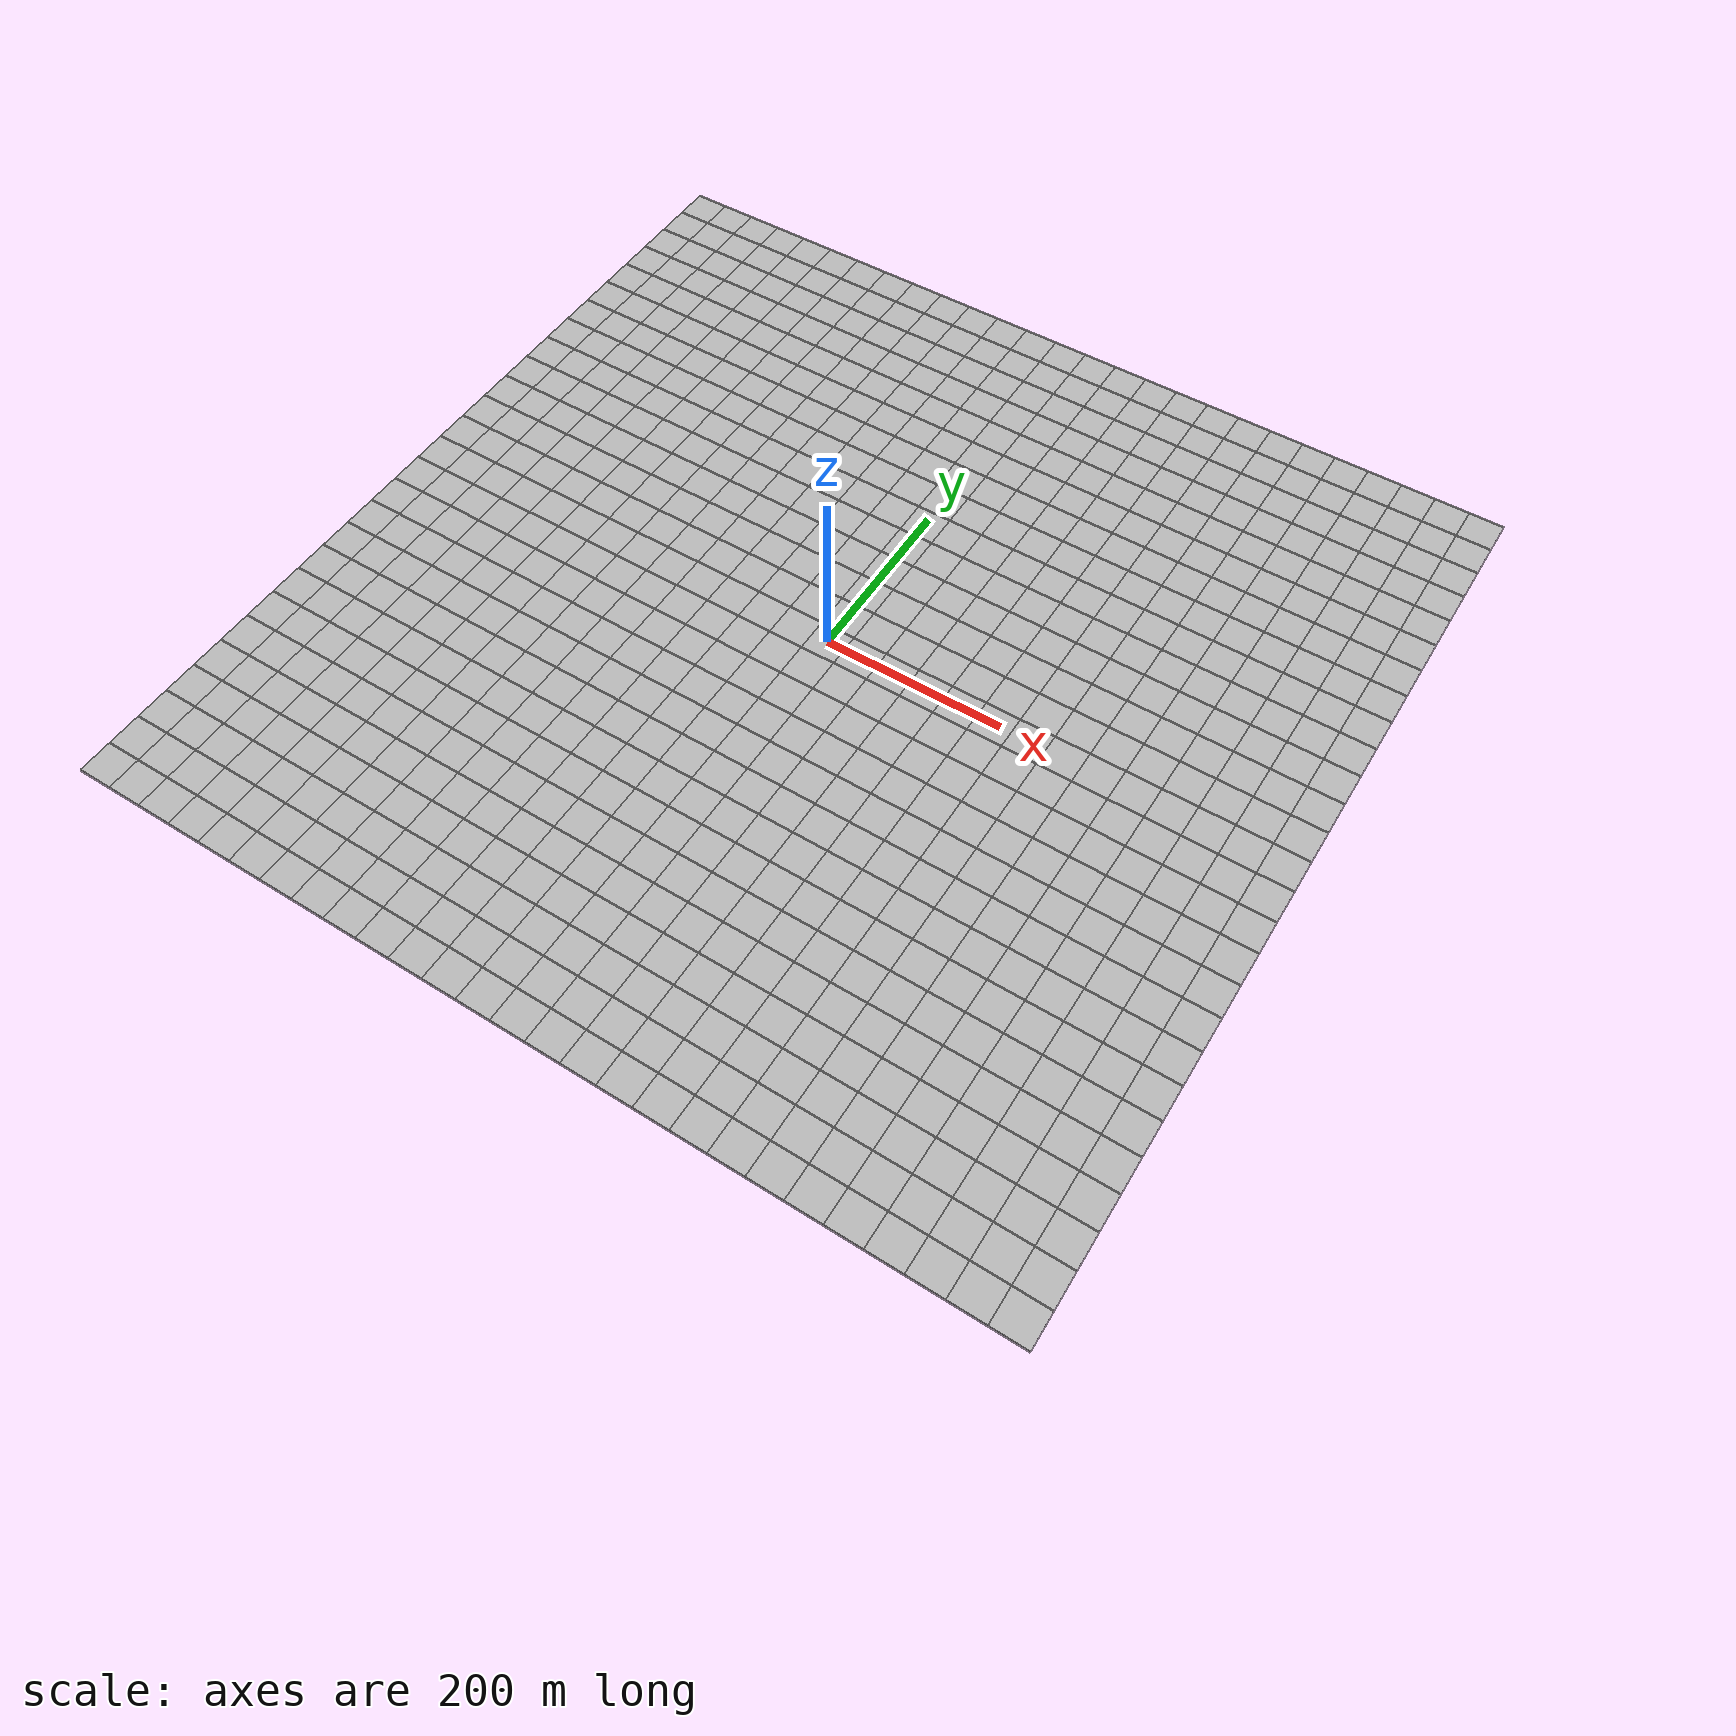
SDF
<sdf version='1.7'>
<model name='map_satellite_36.082428_140.078339_1020_1020'>
  <static>true</static>
  <link name='link'>
    <collision name='collision'>
      <pose>0 0 -0.5 0 0 0</pose>
      <geometry>
        <box>
          <size>1042.44 1042.44 1</size>
        </box>
      </geometry>
    </collision>
    <visual name='visual0_0'>
      <pose>-501.915 501.915 -0.5 0 0 1.5708</pose>
      <geometry>
        <box>
          <size>38.6088 38.6088 1</size>
        </box>
      </geometry>
      <material>
        <script>
          <uri>model://map_satellite_36.082428_140.078339_1020_1020/materials/scripts</uri>
          <uri>model://map_satellite_36.082428_140.078339_1020_1020/materials/textures</uri>
          <name>map_satellite_36.082428_140.078339_1020_1020/0_0</name>
        </script>
      </material>
    </visual>
    <visual name='visual0_1'>
      <pose>-463.306 501.915 -0.5 0 0 1.5708</pose>
      <geometry>
        <box>
          <size>38.6088 38.6088 1</size>
        </box>
      </geometry>
      <material>
        <script>
          <uri>model://map_satellite_36.082428_140.078339_1020_1020/materials/scripts</uri>
          <uri>model://map_satellite_36.082428_140.078339_1020_1020/materials/textures</uri>
          <name>map_satellite_36.082428_140.078339_1020_1020/0_1</name>
        </script>
      </material>
    </visual>
    <visual name='visual0_2'>
      <pose>-424.697 501.915 -0.5 0 0 1.5708</pose>
      <geometry>
        <box>
          <size>38.6088 38.6088 1</size>
        </box>
      </geometry>
      <material>
        <script>
          <uri>model://map_satellite_36.082428_140.078339_1020_1020/materials/scripts</uri>
          <uri>model://map_satellite_36.082428_140.078339_1020_1020/materials/textures</uri>
          <name>map_satellite_36.082428_140.078339_1020_1020/0_2</name>
        </script>
      </material>
    </visual>
    <visual name='visual0_3'>
      <pose>-386.088 501.915 -0.5 0 0 1.5708</pose>
      <geometry>
        <box>
          <size>38.6088 38.6088 1</size>
        </box>
      </geometry>
      <material>
        <script>
          <uri>model://map_satellite_36.082428_140.078339_1020_1020/materials/scripts</uri>
          <uri>model://map_satellite_36.082428_140.078339_1020_1020/materials/textures</uri>
          <name>map_satellite_36.082428_140.078339_1020_1020/0_3</name>
        </script>
      </material>
    </visual>
    <visual name='visual0_4'>
      <pose>-347.48 501.915 -0.5 0 0 1.5708</pose>
      <geometry>
        <box>
          <size>38.6088 38.6088 1</size>
        </box>
      </geometry>
      <material>
        <script>
          <uri>model://map_satellite_36.082428_140.078339_1020_1020/materials/scripts</uri>
          <uri>model://map_satellite_36.082428_140.078339_1020_1020/materials/textures</uri>
          <name>map_satellite_36.082428_140.078339_1020_1020/0_4</name>
        </script>
      </material>
    </visual>
    <visual name='visual0_5'>
      <pose>-308.871 501.915 -0.5 0 0 1.5708</pose>
      <geometry>
        <box>
          <size>38.6088 38.6088 1</size>
        </box>
      </geometry>
      <material>
        <script>
          <uri>model://map_satellite_36.082428_140.078339_1020_1020/materials/scripts</uri>
          <uri>model://map_satellite_36.082428_140.078339_1020_1020/materials/textures</uri>
          <name>map_satellite_36.082428_140.078339_1020_1020/0_5</name>
        </script>
      </material>
    </visual>
    <visual name='visual0_6'>
      <pose>-270.262 501.915 -0.5 0 0 1.5708</pose>
      <geometry>
        <box>
          <size>38.6088 38.6088 1</size>
        </box>
      </geometry>
      <material>
        <script>
          <uri>model://map_satellite_36.082428_140.078339_1020_1020/materials/scripts</uri>
          <uri>model://map_satellite_36.082428_140.078339_1020_1020/materials/textures</uri>
          <name>map_satellite_36.082428_140.078339_1020_1020/0_6</name>
        </script>
      </material>
    </visual>
    <visual name='visual0_7'>
      <pose>-231.653 501.915 -0.5 0 0 1.5708</pose>
      <geometry>
        <box>
          <size>38.6088 38.6088 1</size>
        </box>
      </geometry>
      <material>
        <script>
          <uri>model://map_satellite_36.082428_140.078339_1020_1020/materials/scripts</uri>
          <uri>model://map_satellite_36.082428_140.078339_1020_1020/materials/textures</uri>
          <name>map_satellite_36.082428_140.078339_1020_1020/0_7</name>
        </script>
      </material>
    </visual>
    <visual name='visual0_8'>
      <pose>-193.044 501.915 -0.5 0 0 1.5708</pose>
      <geometry>
        <box>
          <size>38.6088 38.6088 1</size>
        </box>
      </geometry>
      <material>
        <script>
          <uri>model://map_satellite_36.082428_140.078339_1020_1020/materials/scripts</uri>
          <uri>model://map_satellite_36.082428_140.078339_1020_1020/materials/textures</uri>
          <name>map_satellite_36.082428_140.078339_1020_1020/0_8</name>
        </script>
      </material>
    </visual>
    <visual name='visual0_9'>
      <pose>-154.435 501.915 -0.5 0 0 1.5708</pose>
      <geometry>
        <box>
          <size>38.6088 38.6088 1</size>
        </box>
      </geometry>
      <material>
        <script>
          <uri>model://map_satellite_36.082428_140.078339_1020_1020/materials/scripts</uri>
          <uri>model://map_satellite_36.082428_140.078339_1020_1020/materials/textures</uri>
          <name>map_satellite_36.082428_140.078339_1020_1020/0_9</name>
        </script>
      </material>
    </visual>
    <visual name='visual0_10'>
      <pose>-115.827 501.915 -0.5 0 0 1.5708</pose>
      <geometry>
        <box>
          <size>38.6088 38.6088 1</size>
        </box>
      </geometry>
      <material>
        <script>
          <uri>model://map_satellite_36.082428_140.078339_1020_1020/materials/scripts</uri>
          <uri>model://map_satellite_36.082428_140.078339_1020_1020/materials/textures</uri>
          <name>map_satellite_36.082428_140.078339_1020_1020/0_10</name>
        </script>
      </material>
    </visual>
    <visual name='visual0_11'>
      <pose>-77.2177 501.915 -0.5 0 0 1.5708</pose>
      <geometry>
        <box>
          <size>38.6088 38.6088 1</size>
        </box>
      </geometry>
      <material>
        <script>
          <uri>model://map_satellite_36.082428_140.078339_1020_1020/materials/scripts</uri>
          <uri>model://map_satellite_36.082428_140.078339_1020_1020/materials/textures</uri>
          <name>map_satellite_36.082428_140.078339_1020_1020/0_11</name>
        </script>
      </material>
    </visual>
    <visual name='visual0_12'>
      <pose>-38.6088 501.915 -0.5 0 0 1.5708</pose>
      <geometry>
        <box>
          <size>38.6088 38.6088 1</size>
        </box>
      </geometry>
      <material>
        <script>
          <uri>model://map_satellite_36.082428_140.078339_1020_1020/materials/scripts</uri>
          <uri>model://map_satellite_36.082428_140.078339_1020_1020/materials/textures</uri>
          <name>map_satellite_36.082428_140.078339_1020_1020/0_12</name>
        </script>
      </material>
    </visual>
    <visual name='visual0_13'>
      <pose>-1.13687e-13 501.915 -0.5 0 0 1.5708</pose>
      <geometry>
        <box>
          <size>38.6088 38.6088 1</size>
        </box>
      </geometry>
      <material>
        <script>
          <uri>model://map_satellite_36.082428_140.078339_1020_1020/materials/scripts</uri>
          <uri>model://map_satellite_36.082428_140.078339_1020_1020/materials/textures</uri>
          <name>map_satellite_36.082428_140.078339_1020_1020/0_13</name>
        </script>
      </material>
    </visual>
    <visual name='visual0_14'>
      <pose>38.6088 501.915 -0.5 0 0 1.5708</pose>
      <geometry>
        <box>
          <size>38.6088 38.6088 1</size>
        </box>
      </geometry>
      <material>
        <script>
          <uri>model://map_satellite_36.082428_140.078339_1020_1020/materials/scripts</uri>
          <uri>model://map_satellite_36.082428_140.078339_1020_1020/materials/textures</uri>
          <name>map_satellite_36.082428_140.078339_1020_1020/0_14</name>
        </script>
      </material>
    </visual>
    <visual name='visual0_15'>
      <pose>77.2177 501.915 -0.5 0 0 1.5708</pose>
      <geometry>
        <box>
          <size>38.6088 38.6088 1</size>
        </box>
      </geometry>
      <material>
        <script>
          <uri>model://map_satellite_36.082428_140.078339_1020_1020/materials/scripts</uri>
          <uri>model://map_satellite_36.082428_140.078339_1020_1020/materials/textures</uri>
          <name>map_satellite_36.082428_140.078339_1020_1020/0_15</name>
        </script>
      </material>
    </visual>
    <visual name='visual0_16'>
      <pose>115.827 501.915 -0.5 0 0 1.5708</pose>
      <geometry>
        <box>
          <size>38.6088 38.6088 1</size>
        </box>
      </geometry>
      <material>
        <script>
          <uri>model://map_satellite_36.082428_140.078339_1020_1020/materials/scripts</uri>
          <uri>model://map_satellite_36.082428_140.078339_1020_1020/materials/textures</uri>
          <name>map_satellite_36.082428_140.078339_1020_1020/0_16</name>
        </script>
      </material>
    </visual>
    <visual name='visual0_17'>
      <pose>154.435 501.915 -0.5 0 0 1.5708</pose>
      <geometry>
        <box>
          <size>38.6088 38.6088 1</size>
        </box>
      </geometry>
      <material>
        <script>
          <uri>model://map_satellite_36.082428_140.078339_1020_1020/materials/scripts</uri>
          <uri>model://map_satellite_36.082428_140.078339_1020_1020/materials/textures</uri>
          <name>map_satellite_36.082428_140.078339_1020_1020/0_17</name>
        </script>
      </material>
    </visual>
    <visual name='visual0_18'>
      <pose>193.044 501.915 -0.5 0 0 1.5708</pose>
      <geometry>
        <box>
          <size>38.6088 38.6088 1</size>
        </box>
      </geometry>
      <material>
        <script>
          <uri>model://map_satellite_36.082428_140.078339_1020_1020/materials/scripts</uri>
          <uri>model://map_satellite_36.082428_140.078339_1020_1020/materials/textures</uri>
          <name>map_satellite_36.082428_140.078339_1020_1020/0_18</name>
        </script>
      </material>
    </visual>
    <visual name='visual0_19'>
      <pose>231.653 501.915 -0.5 0 0 1.5708</pose>
      <geometry>
        <box>
          <size>38.6088 38.6088 1</size>
        </box>
      </geometry>
      <material>
        <script>
          <uri>model://map_satellite_36.082428_140.078339_1020_1020/materials/scripts</uri>
          <uri>model://map_satellite_36.082428_140.078339_1020_1020/materials/textures</uri>
          <name>map_satellite_36.082428_140.078339_1020_1020/0_19</name>
        </script>
      </material>
    </visual>
    <visual name='visual0_20'>
      <pose>270.262 501.915 -0.5 0 0 1.5708</pose>
      <geometry>
        <box>
          <size>38.6088 38.6088 1</size>
        </box>
      </geometry>
      <material>
        <script>
          <uri>model://map_satellite_36.082428_140.078339_1020_1020/materials/scripts</uri>
          <uri>model://map_satellite_36.082428_140.078339_1020_1020/materials/textures</uri>
          <name>map_satellite_36.082428_140.078339_1020_1020/0_20</name>
        </script>
      </material>
    </visual>
    <visual name='visual0_21'>
      <pose>308.871 501.915 -0.5 0 0 1.5708</pose>
      <geometry>
        <box>
          <size>38.6088 38.6088 1</size>
        </box>
      </geometry>
      <material>
        <script>
          <uri>model://map_satellite_36.082428_140.078339_1020_1020/materials/scripts</uri>
          <uri>model://map_satellite_36.082428_140.078339_1020_1020/materials/textures</uri>
          <name>map_satellite_36.082428_140.078339_1020_1020/0_21</name>
        </script>
      </material>
    </visual>
    <visual name='visual0_22'>
      <pose>347.48 501.915 -0.5 0 0 1.5708</pose>
      <geometry>
        <box>
          <size>38.6088 38.6088 1</size>
        </box>
      </geometry>
      <material>
        <script>
          <uri>model://map_satellite_36.082428_140.078339_1020_1020/materials/scripts</uri>
          <uri>model://map_satellite_36.082428_140.078339_1020_1020/materials/textures</uri>
          <name>map_satellite_36.082428_140.078339_1020_1020/0_22</name>
        </script>
      </material>
    </visual>
    <visual name='visual0_23'>
      <pose>386.088 501.915 -0.5 0 0 1.5708</pose>
      <geometry>
        <box>
          <size>38.6088 38.6088 1</size>
        </box>
      </geometry>
      <material>
        <script>
          <uri>model://map_satellite_36.082428_140.078339_1020_1020/materials/scripts</uri>
          <uri>model://map_satellite_36.082428_140.078339_1020_1020/materials/textures</uri>
          <name>map_satellite_36.082428_140.078339_1020_1020/0_23</name>
        </script>
      </material>
    </visual>
    <visual name='visual0_24'>
      <pose>424.697 501.915 -0.5 0 0 1.5708</pose>
      <geometry>
        <box>
          <size>38.6088 38.6088 1</size>
        </box>
      </geometry>
      <material>
        <script>
          <uri>model://map_satellite_36.082428_140.078339_1020_1020/materials/scripts</uri>
          <uri>model://map_satellite_36.082428_140.078339_1020_1020/materials/textures</uri>
          <name>map_satellite_36.082428_140.078339_1020_1020/0_24</name>
        </script>
      </material>
    </visual>
    <visual name='visual0_25'>
      <pose>463.306 501.915 -0.5 0 0 1.5708</pose>
      <geometry>
        <box>
          <size>38.6088 38.6088 1</size>
        </box>
      </geometry>
      <material>
        <script>
          <uri>model://map_satellite_36.082428_140.078339_1020_1020/materials/scripts</uri>
          <uri>model://map_satellite_36.082428_140.078339_1020_1020/materials/textures</uri>
          <name>map_satellite_36.082428_140.078339_1020_1020/0_25</name>
        </script>
      </material>
    </visual>
    <visual name='visual0_26'>
      <pose>501.915 501.915 -0.5 0 0 1.5708</pose>
      <geometry>
        <box>
          <size>38.6088 38.6088 1</size>
        </box>
      </geometry>
      <material>
        <script>
          <uri>model://map_satellite_36.082428_140.078339_1020_1020/materials/scripts</uri>
          <uri>model://map_satellite_36.082428_140.078339_1020_1020/materials/textures</uri>
          <name>map_satellite_36.082428_140.078339_1020_1020/0_26</name>
        </script>
      </material>
    </visual>
    <visual name='visual1_0'>
      <pose>-501.915 463.306 -0.5 0 0 1.5708</pose>
      <geometry>
        <box>
          <size>38.6088 38.6088 1</size>
        </box>
      </geometry>
      <material>
        <script>
          <uri>model://map_satellite_36.082428_140.078339_1020_1020/materials/scripts</uri>
          <uri>model://map_satellite_36.082428_140.078339_1020_1020/materials/textures</uri>
          <name>map_satellite_36.082428_140.078339_1020_1020/1_0</name>
        </script>
      </material>
    </visual>
    <visual name='visual1_1'>
      <pose>-463.306 463.306 -0.5 0 0 1.5708</pose>
      <geometry>
        <box>
          <size>38.6088 38.6088 1</size>
        </box>
      </geometry>
      <material>
        <script>
          <uri>model://map_satellite_36.082428_140.078339_1020_1020/materials/scripts</uri>
          <uri>model://map_satellite_36.082428_140.078339_1020_1020/materials/textures</uri>
          <name>map_satellite_36.082428_140.078339_1020_1020/1_1</name>
        </script>
      </material>
    </visual>
    <visual name='visual1_2'>
      <pose>-424.697 463.306 -0.5 0 0 1.5708</pose>
      <geometry>
        <box>
          <size>38.6088 38.6088 1</size>
        </box>
      </geometry>
      <material>
        <script>
          <uri>model://map_satellite_36.082428_140.078339_1020_1020/materials/scripts</uri>
          <uri>model://map_satellite_36.082428_140.078339_1020_1020/materials/textures</uri>
          <name>map_satellite_36.082428_140.078339_1020_1020/1_2</name>
        </script>
      </material>
    </visual>
    <visual name='visual1_3'>
      <pose>-386.088 463.306 -0.5 0 0 1.5708</pose>
      <geometry>
        <box>
          <size>38.6088 38.6088 1</size>
        </box>
      </geometry>
      <material>
        <script>
          <uri>model://map_satellite_36.082428_140.078339_1020_1020/materials/scripts</uri>
          <uri>model://map_satellite_36.082428_140.078339_1020_1020/materials/textures</uri>
          <name>map_satellite_36.082428_140.078339_1020_1020/1_3</name>
        </script>
      </material>
    </visual>
    <visual name='visual1_4'>
      <pose>-347.48 463.306 -0.5 0 0 1.5708</pose>
      <geometry>
        <box>
          <size>38.6088 38.6088 1</size>
        </box>
      </geometry>
      <material>
        <script>
          <uri>model://map_satellite_36.082428_140.078339_1020_1020/materials/scripts</uri>
          <uri>model://map_satellite_36.082428_140.078339_1020_1020/materials/textures</uri>
          <name>map_satellite_36.082428_140.078339_1020_1020/1_4</name>
        </script>
      </material>
    </visual>
    <visual name='visual1_5'>
      <pose>-308.871 463.306 -0.5 0 0 1.5708</pose>
      <geometry>
        <box>
          <size>38.6088 38.6088 1</size>
        </box>
      </geometry>
      <material>
        <script>
          <uri>model://map_satellite_36.082428_140.078339_1020_1020/materials/scripts</uri>
          <uri>model://map_satellite_36.082428_140.078339_1020_1020/materials/textures</uri>
          <name>map_satellite_36.082428_140.078339_1020_1020/1_5</name>
        </script>
      </material>
    </visual>
    <visual name='visual1_6'>
      <pose>-270.262 463.306 -0.5 0 0 1.5708</pose>
      <geometry>
        <box>
          <size>38.6088 38.6088 1</size>
        </box>
      </geometry>
      <material>
        <script>
          <uri>model://map_satellite_36.082428_140.078339_1020_1020/materials/scripts</uri>
          <uri>model://map_satellite_36.082428_140.078339_1020_1020/materials/textures</uri>
          <name>map_satellite_36.082428_140.078339_1020_1020/1_6</name>
        </script>
      </material>
    </visual>
    <visual name='visual1_7'>
      <pose>-231.653 463.306 -0.5 0 0 1.5708</pose>
      <geometry>
        <box>
          <size>38.6088 38.6088 1</size>
        </box>
      </geometry>
      <material>
        <script>
          <uri>model://map_satellite_36.082428_140.078339_1020_1020/materials/scripts</uri>
          <uri>model://map_satellite_36.082428_140.078339_1020_1020/materials/textures</uri>
          <name>map_satellite_36.082428_140.078339_1020_1020/1_7</name>
        </script>
      </material>
    </visual>
    <visual name='visual1_8'>
      <pose>-193.044 463.306 -0.5 0 0 1.5708</pose>
      <geometry>
        <box>
          <size>38.6088 38.6088 1</size>
        </box>
      </geometry>
      <material>
        <script>
          <uri>model://map_satellite_36.082428_140.078339_1020_1020/materials/scripts</uri>
          <uri>model://map_satellite_36.082428_140.078339_1020_1020/materials/textures</uri>
          <name>map_satellite_36.082428_140.078339_1020_1020/1_8</name>
        </script>
      </material>
    </visual>
    <visual name='visual1_9'>
      <pose>-154.435 463.306 -0.5 0 0 1.5708</pose>
      <geometry>
        <box>
          <size>38.6088 38.6088 1</size>
        </box>
      </geometry>
      <material>
        <script>
          <uri>model://map_satellite_36.082428_140.078339_1020_1020/materials/scripts</uri>
          <uri>model://map_satellite_36.082428_140.078339_1020_1020/materials/textures</uri>
          <name>map_satellite_36.082428_140.078339_1020_1020/1_9</name>
        </script>
      </material>
    </visual>
    <visual name='visual1_10'>
      <pose>-115.827 463.306 -0.5 0 0 1.5708</pose>
      <geometry>
        <box>
          <size>38.6088 38.6088 1</size>
        </box>
      </geometry>
      <material>
        <script>
          <uri>model://map_satellite_36.082428_140.078339_1020_1020/materials/scripts</uri>
          <uri>model://map_satellite_36.082428_140.078339_1020_1020/materials/textures</uri>
          <name>map_satellite_36.082428_140.078339_1020_1020/1_10</name>
        </script>
      </material>
    </visual>
    <visual name='visual1_11'>
      <pose>-77.2177 463.306 -0.5 0 0 1.5708</pose>
      <geometry>
        <box>
          <size>38.6088 38.6088 1</size>
        </box>
      </geometry>
      <material>
        <script>
          <uri>model://map_satellite_36.082428_140.078339_1020_1020/materials/scripts</uri>
          <uri>model://map_satellite_36.082428_140.078339_1020_1020/materials/textures</uri>
          <name>map_satellite_36.082428_140.078339_1020_1020/1_11</name>
        </script>
      </material>
    </visual>
    <visual name='visual1_12'>
      <pose>-38.6088 463.306 -0.5 0 0 1.5708</pose>
      <geometry>
        <box>
          <size>38.6088 38.6088 1</size>
        </box>
      </geometry>
      <material>
        <script>
          <uri>model://map_satellite_36.082428_140.078339_1020_1020/materials/scripts</uri>
          <uri>model://map_satellite_36.082428_140.078339_1020_1020/materials/textures</uri>
          <name>map_satellite_36.082428_140.078339_1020_1020/1_12</name>
        </script>
      </material>
    </visual>
    <visual name='visual1_13'>
      <pose>-1.13687e-13 463.306 -0.5 0 0 1.5708</pose>
      <geometry>
        <box>
          <size>38.6088 38.6088 1</size>
        </box>
      </geometry>
      <material>
        <script>
          <uri>model://map_satellite_36.082428_140.078339_1020_1020/materials/scripts</uri>
          <uri>model://map_satellite_36.082428_140.078339_1020_1020/materials/textures</uri>
          <name>map_satellite_36.082428_140.078339_1020_1020/1_13</name>
        </script>
      </material>
    </visual>
    <visual name='visual1_14'>
      <pose>38.6088 463.306 -0.5 0 0 1.5708</pose>
      <geometry>
        <box>
          <size>38.6088 38.6088 1</size>
        </box>
      </geometry>
      <material>
        <script>
          <uri>model://map_satellite_36.082428_140.078339_1020_1020/materials/scripts</uri>
          <uri>model://map_satellite_36.082428_140.078339_1020_1020/materials/textures</uri>
          <name>map_satellite_36.082428_140.078339_1020_1020/1_14</name>
        </script>
      </material>
    </visual>
    <visual name='visual1_15'>
      <pose>77.2177 463.306 -0.5 0 0 1.5708</pose>
      <geometry>
        <box>
          <size>38.6088 38.6088 1</size>
        </box>
      </geometry>
      <material>
        <script>
          <uri>model://map_satellite_36.082428_140.078339_1020_1020/materials/scripts</uri>
          <uri>model://map_satellite_36.082428_140.078339_1020_1020/materials/textures</uri>
          <name>map_satellite_36.082428_140.078339_1020_1020/1_15</name>
        </script>
      </material>
    </visual>
    <visual name='visual1_16'>
      <pose>115.827 463.306 -0.5 0 0 1.5708</pose>
      <geometry>
        <box>
          <size>38.6088 38.6088 1</size>
        </box>
      </geometry>
      <material>
        <script>
          <uri>model://map_satellite_36.082428_140.078339_1020_1020/materials/scripts</uri>
          <uri>model://map_satellite_36.082428_140.078339_1020_1020/materials/textures</uri>
          <name>map_satellite_36.082428_140.078339_1020_1020/1_16</name>
        </script>
      </material>
    </visual>
    <visual name='visual1_17'>
      <pose>154.435 463.306 -0.5 0 0 1.5708</pose>
      <geometry>
        <box>
          <size>38.6088 38.6088 1</size>
        </box>
      </geometry>
      <material>
        <script>
          <uri>model://map_satellite_36.082428_140.078339_1020_1020/materials/scripts</uri>
          <uri>model://map_satellite_36.082428_140.078339_1020_1020/materials/textures</uri>
          <name>map_satellite_36.082428_140.078339_1020_1020/1_17</name>
        </script>
      </material>
    </visual>
    <visual name='visual1_18'>
      <pose>193.044 463.306 -0.5 0 0 1.5708</pose>
      <geometry>
        <box>
          <size>38.6088 38.6088 1</size>
        </box>
      </geometry>
      <material>
        <script>
          <uri>model://map_satellite_36.082428_140.078339_1020_1020/materials/scripts</uri>
          <uri>model://map_satellite_36.082428_140.078339_1020_1020/materials/textures</uri>
          <name>map_satellite_36.082428_140.078339_1020_1020/1_18</name>
        </script>
      </material>
    </visual>
    <visual name='visual1_19'>
      <pose>231.653 463.306 -0.5 0 0 1.5708</pose>
      <geometry>
        <box>
          <size>38.6088 38.6088 1</size>
        </box>
      </geometry>
      <material>
        <script>
          <uri>model://map_satellite_36.082428_140.078339_1020_1020/materials/scripts</uri>
          <uri>model://map_satellite_36.082428_140.078339_1020_1020/materials/textures</uri>
          <name>map_satellite_36.082428_140.078339_1020_1020/1_19</name>
        </script>
      </material>
    </visual>
    <visual name='visual1_20'>
      <pose>270.262 463.306 -0.5 0 0 1.5708</pose>
      <geometry>
        <box>
          <size>38.6088 38.6088 1</size>
        </box>
      </geometry>
      <material>
        <script>
          <uri>model://map_satellite_36.082428_140.078339_1020_1020/materials/scripts</uri>
          <uri>model://map_satellite_36.082428_140.078339_1020_1020/materials/textures</uri>
          <name>map_satellite_36.082428_140.078339_1020_1020/1_20</name>
        </script>
      </material>
    </visual>
    <visual name='visual1_21'>
      <pose>308.871 463.306 -0.5 0 0 1.5708</pose>
      <geometry>
        <box>
          <size>38.6088 38.6088 1</size>
        </box>
      </geometry>
      <material>
        <script>
          <uri>model://map_satellite_36.082428_140.078339_1020_1020/materials/scripts</uri>
          <uri>model://map_satellite_36.082428_140.078339_1020_1020/materials/textures</uri>
          <name>map_satellite_36.082428_140.078339_1020_1020/1_21</name>
        </script>
      </material>
    </visual>
    <visual name='visual1_22'>
      <pose>347.48 463.306 -0.5 0 0 1.5708</pose>
      <geometry>
        <box>
          <size>38.6088 38.6088 1</size>
        </box>
      </geometry>
      <material>
        <script>
          <uri>model://map_satellite_36.082428_140.078339_1020_1020/materials/scripts</uri>
          <uri>model://map_satellite_36.082428_140.078339_1020_1020/materials/textures</uri>
          <name>map_satellite_36.082428_140.078339_1020_1020/1_22</name>
        </script>
      </material>
    </visual>
    <visual name='visual1_23'>
      <pose>386.088 463.306 -0.5 0 0 1.5708</pose>
      <geometry>
        <box>
          <size>38.6088 38.6088 1</size>
        </box>
      </geometry>
      <material>
        <script>
          <uri>model://map_satellite_36.082428_140.078339_1020_1020/materials/scripts</uri>
          <uri>model://map_satellite_36.082428_140.078339_1020_1020/materials/textures</uri>
          <name>map_satellite_36.082428_140.078339_1020_1020/1_23</name>
        </script>
      </material>
    </visual>
    <visual name='visual1_24'>
      <pose>424.697 463.306 -0.5 0 0 1.5708</pose>
      <geometry>
        <box>
          <size>38.6088 38.6088 1</size>
        </box>
      </geometry>
      <material>
        <script>
          <uri>model://map_satellite_36.082428_140.078339_1020_1020/materials/scripts</uri>
          <uri>model://map_satellite_36.082428_140.078339_1020_1020/materials/textures</uri>
          <name>map_satellite_36.082428_140.078339_1020_1020/1_24</name>
        </script>
      </material>
    </visual>
    <visual name='visual1_25'>
      <pose>463.306 463.306 -0.5 0 0 1.5708</pose>
      <geometry>
        <box>
          <size>38.6088 38.6088 1</size>
        </box>
      </geometry>
      <material>
        <script>
          <uri>model://map_satellite_36.082428_140.078339_1020_1020/materials/scripts</uri>
          <uri>model://map_satellite_36.082428_140.078339_1020_1020/materials/textures</uri>
          <name>map_satellite_36.082428_140.078339_1020_1020/1_25</name>
        </script>
      </material>
    </visual>
    <visual name='visual1_26'>
      <pose>501.915 463.306 -0.5 0 0 1.5708</pose>
      <geometry>
        <box>
          <size>38.6088 38.6088 1</size>
        </box>
      </geometry>
      <material>
        <script>
          <uri>model://map_satellite_36.082428_140.078339_1020_1020/materials/scripts</uri>
          <uri>model://map_satellite_36.082428_140.078339_1020_1020/materials/textures</uri>
          <name>map_satellite_36.082428_140.078339_1020_1020/1_26</name>
        </script>
      </material>
    </visual>
    <visual name='visual2_0'>
      <pose>-501.915 424.697 -0.5 0 0 1.5708</pose>
      <geometry>
        <box>
          <size>38.6088 38.6088 1</size>
        </box>
      </geometry>
      <material>
        <script>
          <uri>model://map_satellite_36.082428_140.078339_1020_1020/materials/scripts</uri>
          <uri>model://map_satellite_36.082428_140.078339_1020_1020/materials/textures</uri>
          <name>map_satellite_36.082428_140.078339_1020_1020/2_0</name>
        </script>
      </material>
    </visual>
    <visual name='visual2_1'>
      <pose>-463.306 424.697 -0.5 0 0 1.5708</pose>
      <geometry>
        <box>
          <size>38.6088 38.6088 1</size>
        </box>
      </geometry>
      <material>
        <script>
          <uri>model://map_satellite_36.082428_140.078339_1020_1020/materials/scripts</uri>
          <uri>model://map_satellite_36.082428_140.078339_1020_1020/materials/textures</uri>
          <name>map_satellite_36.082428_140.078339_1020_1020/2_1</name>
        </script>
      </material>
    </visual>
    <visual name='visual2_2'>
      <pose>-424.697 424.697 -0.5 0 0 1.5708</pose>
      <geometry>
        <box>
          <size>38.6088 38.6088 1</size>
        </box>
      </geometry>
      <material>
        <script>
          <uri>model://map_satellite_36.082428_140.078339_1020_1020/materials/scripts</uri>
          <uri>model://map_satellite_36.082428_140.078339_1020_1020/materials/textures</uri>
          <name>map_satellite_36.082428_140.078339_1020_1020/2_2</name>
        </script>
      </material>
    </visual>
    <visual name='visual2_3'>
      <pose>-386.088 424.697 -0.5 0 0 1.5708</pose>
      <geometry>
        <box>
          <size>38.6088 38.6088 1</size>
        </box>
      </geometry>
      <material>
        <script>
          <uri>model://map_satellite_36.082428_140.078339_1020_1020/materials/scripts</uri>
          <uri>model://map_satellite_36.082428_140.078339_1020_1020/materials/textures</uri>
          <name>map_satellite_36.082428_140.078339_1020_1020/2_3</name>
        </script>
      </material>
    </visual>
    <visual name='visual2_4'>
      <pose>-347.48 424.697 -0.5 0 0 1.5708</pose>
      <geometry>
        <box>
          <size>38.6088 38.6088 1</size>
        </box>
      </geometry>
      <material>
        <script>
          <uri>model://map_satellite_36.082428_140.078339_1020_1020/materials/scripts</uri>
          <uri>model://map_satellite_36.082428_140.078339_1020_1020/materials/textures</uri>
          <name>map_satellite_36.082428_140.078339_1020_1020/2_4</name>
        </script>
      </material>
    </visual>
    <visual name='visual2_5'>
      <pose>-308.871 424.697 -0.5 0 0 1.5708</pose>
      <geometry>
        <box>
          <size>38.6088 38.6088 1</size>
        </box>
      </geometry>
      <material>
        <script>
          <uri>model://map_satellite_36.082428_140.078339_1020_1020/materials/scripts</uri>
          <uri>model://map_satellite_36.082428_140.078339_1020_1020/materials/textures</uri>
          <name>map_satellite_36.082428_140.078339_1020_1020/2_5</name>
        </script>
      </material>
    </visual>
    <visual name='visual2_6'>
      <pose>-270.262 424.697 -0.5 0 0 1.5708</pose>
      <geometry>
        <box>
          <size>38.6088 38.6088 1</size>
        </box>
      </geometry>
      <material>
        <script>
          <uri>model://map_satellite_36.082428_140.078339_1020_1020/materials/scripts</uri>
          <uri>model://map_satellite_36.082428_140.078339_1020_1020/materials/textures</uri>
          <name>map_satellite_36.082428_140.078339_1020_1020/2_6</name>
        </script>
      </material>
    </visual>
    <visual name='visual2_7'>
      <pose>-231.653 424.697 -0.5 0 0 1.5708</pose>
      <geometry>
        <box>
          <size>38.6088 38.6088 1</size>
        </box>
      </geometry>
      <material>
        <script>
          <uri>model://map_satellite_36.082428_140.078339_1020_1020/materials/scripts</uri>
          <uri>model://map_satellite_36.082428_140.078339_1020_1020/materials/textures</uri>
          <name>map_satellite_36.082428_140.078339_1020_1020/2_7</name>
        </script>
      </material>
    </visual>
    <visual name='visual2_8'>
      <pose>-193.044 424.697 -0.5 0 0 1.5708</pose>
      <geometry>
        <box>
          <size>38.6088 38.6088 1</size>
        </box>
      </geometry>
      <material>
        <script>
          <uri>model://map_satellite_36.082428_140.078339_1020_1020/materials/scripts</uri>
          <uri>model://map_satellite_36.082428_140.078339_1020_1020/materials/textures</uri>
          <name>map_satellite_36.082428_140.078339_1020_1020/2_8</name>
        </script>
      </material>
    </visual>
    <visual name='visual2_9'>
      <pose>-154.435 424.697 -0.5 0 0 1.5708</pose>
      <geometry>
        <box>
          <size>38.6088 38.6088 1</size>
        </box>
      </geometry>
      <material>
        <script>
          <uri>model://map_satellite_36.082428_140.078339_1020_1020/materials/scripts</uri>
          <uri>model://map_satellite_36.082428_140.078339_1020_1020/materials/textures</uri>
          <name>map_satellite_36.082428_140.078339_1020_1020/2_9</name>
        </script>
      </material>
    </visual>
    <visual name='visual2_10'>
      <pose>-115.827 424.697 -0.5 0 0 1.5708</pose>
      <geometry>
        <box>
          <size>38.6088 38.6088 1</size>
        </box>
      </geometry>
      <material>
        <script>
          <uri>model://map_satellite_36.082428_140.078339_1020_1020/materials/scripts</uri>
          <uri>model://map_satellite_36.082428_140.078339_1020_1020/materials/textures</uri>
          <name>map_satellite_36.082428_140.078339_1020_1020/2_10</name>
        </script>
      </material>
    </visual>
    <visual name='visual2_11'>
      <pose>-77.2177 424.697 -0.5 0 0 1.5708</pose>
      <geometry>
        <box>
          <size>38.6088 38.6088 1</size>
        </box>
      </geometry>
      <material>
        <script>
          <uri>model://map_satellite_36.082428_140.078339_1020_1020/materials/scripts</uri>
          <uri>model://map_satellite_36.082428_140.078339_1020_1020/materials/textures</uri>
          <name>map_satellite_36.082428_140.078339_1020_1020/2_11</name>
        </script>
      </material>
    </visual>
    <visual name='visual2_12'>
      <pose>-38.6088 424.697 -0.5 0 0 1.5708</pose>
      <geometry>
        <box>
          <size>38.6088 38.6088 1</size>
        </box>
      </geometry>
      <material>
        <script>
          <uri>model://map_satellite_36.082428_140.078339_1020_1020/materials/scripts</uri>
          <uri>model://map_satellite_36.082428_140.078339_1020_1020/materials/textures</uri>
          <name>map_satellite_36.082428_140.078339_1020_1020/2_12</name>
        </script>
      </material>
    </visual>
    <visual name='visual2_13'>
      <pose>-1.13687e-13 424.697 -0.5 0 0 1.5708</pose>
      <geometry>
        <box>
          <size>38.6088 38.6088 1</size>
        </box>
      </geometry>
      <material>
        <script>
          <uri>model://map_satellite_36.082428_140.078339_1020_1020/materials/scripts</uri>
          <uri>model://map_satellite_36.082428_140.078339_1020_1020/materials/textures</uri>
          <name>map_satellite_36.082428_140.078339_1020_1020/2_13</name>
        </script>
      </material>
    </visual>
    <visual name='visual2_14'>
      <pose>38.6088 424.697 -0.5 0 0 1.5708</pose>
      <geometry>
        <box>
          <size>38.6088 38.6088 1</size>
        </box>
      </geometry>
      <material>
        <script>
          <uri>model://map_satellite_36.082428_140.078339_1020_1020/materials/scripts</uri>
          <uri>model://map_satellite_36.082428_140.078339_1020_1020/materials/textures</uri>
          <name>map_satellite_36.082428_140.078339_1020_1020/2_14</name>
        </script>
      </material>
    </visual>
    <visual name='visual2_15'>
      <pose>77.2177 424.697 -0.5 0 0 1.5708</pose>
      <geometry>
        <box>
          <size>38.6088 38.6088 1</size>
        </box>
      </geometry>
      <material>
        <script>
          <uri>model://map_satellite_36.082428_140.078339_1020_1020/materials/scripts</uri>
          <uri>model://map_satellite_36.082428_140.078339_1020_1020/materials/textures</uri>
          <name>map_satellite_36.082428_140.078339_1020_1020/2_15</name>
        </script>
      </material>
    </visual>
    <visual name='visual2_16'>
      <pose>115.827 424.697 -0.5 0 0 1.5708</pose>
      <geometry>
        <box>
          <size>38.6088 38.6088 1</size>
        </box>
      </geometry>
      <material>
        <script>
          <uri>model://map_satellite_36.082428_140.078339_1020_1020/materials/scripts</uri>
          <uri>model://map_satellite_36.082428_140.078339_1020_1020/materials/textures</uri>
          <name>map_satellite_36.082428_140.078339_1020_1020/2_16</name>
        </script>
      </material>
    </visual>
    <visual name='visual2_17'>
      <pose>154.435 424.697 -0.5 0 0 1.5708</pose>
      <geometry>
        <box>
          <size>38.6088 38.6088 1</size>
        </box>
      </geometry>
      <material>
        <script>
          <uri>model://map_satellite_36.082428_140.078339_1020_1020/materials/scripts</uri>
          <uri>model://map_satellite_36.082428_140.078339_1020_1020/materials/textures</uri>
          <name>map_satellite_36.082428_140.078339_1020_1020/2_17</name>
        </script>
      </material>
    </visual>
    <visual name='visual2_18'>
      <pose>193.044 424.697 -0.5 0 0 1.5708</pose>
      <geometry>
        <box>
          <size>38.6088 38.6088 1</size>
        </box>
      </geometry>
      <material>
        <script>
          <uri>model://map_satellite_36.082428_140.078339_1020_1020/materials/scripts</uri>
          <uri>model://map_satellite_36.082428_140.078339_1020_1020/materials/textures</uri>
          <name>map_satellite_36.082428_140.078339_1020_1020/2_18</name>
        </script>
      </material>
    </visual>
    <visual name='visual2_19'>
      <pose>231.653 424.697 -0.5 0 0 1.5708</pose>
      <geometry>
        <box>
          <size>38.6088 38.6088 1</size>
        </box>
      </geometry>
      <material>
        <script>
          <uri>model://map_satellite_36.082428_140.078339_1020_1020/materials/scripts</uri>
          <uri>model://map_satellite_36.082428_140.078339_1020_1020/materials/textures</uri>
          <name>map_satellite_36.082428_140.078339_1020_1020/2_19</name>
        </script>
      </material>
    </visual>
    <visual name='visual2_20'>
      <pose>270.262 424.697 -0.5 0 0 1.5708</pose>
      <geometry>
        <box>
          <size>38.6088 38.6088 1</size>
        </box>
      </geometry>
      <material>
        <script>
          <uri>model://map_satellite_36.082428_140.078339_1020_1020/materials/scripts</uri>
          <uri>model://map_satellite_36.082428_140.078339_1020_1020/materials/textures</uri>
          <name>map_satellite_36.082428_140.078339_1020_1020/2_20</name>
        </script>
      </material>
    </visual>
    <visual name='visual2_21'>
      <pose>308.871 424.697 -0.5 0 0 1.5708</pose>
      <geometry>
        <box>
          <size>38.6088 38.6088 1</size>
        </box>
      </geometry>
      <material>
        <script>
          <uri>model://map_satellite_36.082428_140.078339_1020_1020/materials/scripts</uri>
          <uri>model://map_satellite_36.082428_140.078339_1020_1020/materials/textures</uri>
          <name>map_satellite_36.082428_140.078339_1020_1020/2_21</name>
        </script>
      </material>
    </visual>
    <visual name='visual2_22'>
      <pose>347.48 424.697 -0.5 0 0 1.5708</pose>
      <geometry>
        <box>
          <size>38.6088 38.6088 1</size>
        </box>
      </geometry>
      <material>
        <script>
          <uri>model://map_satellite_36.082428_140.078339_1020_1020/materials/scripts</uri>
          <uri>model://map_satellite_36.082428_140.078339_1020_1020/materials/textures</uri>
          <name>map_satellite_36.082428_140.078339_1020_1020/2_22</name>
        </script>
      </material>
    </visual>
    <visual name='visual2_23'>
      <pose>386.088 424.697 -0.5 0 0 1.5708</pose>
      <geometry>
        <box>
          <size>38.6088 38.6088 1</size>
        </box>
      </geometry>
      <material>
        <script>
          <uri>model://map_satellite_36.082428_140.078339_1020_1020/materials/scripts</uri>
          <uri>model://map_satellite_36.082428_140.078339_1020_1020/materials/textures</uri>
          <name>map_satellite_36.082428_140.078339_1020_1020/2_23</name>
        </script>
      </material>
    </visual>
    <visual name='visual2_24'>
      <pose>424.697 424.697 -0.5 0 0 1.5708</pose>
      <geometry>
        <box>
          <size>38.6088 38.6088 1</size>
        </box>
      </geometry>
      <material>
        <script>
          <uri>model://map_satellite_36.082428_140.078339_1020_1020/materials/scripts</uri>
          <uri>model://map_satellite_36.082428_140.078339_1020_1020/materials/textures</uri>
          <name>map_satellite_36.082428_140.078339_1020_1020/2_24</name>
        </script>
      </material>
    </visual>
    <visual name='visual2_25'>
      <pose>463.306 424.697 -0.5 0 0 1.5708</pose>
      <geometry>
        <box>
          <size>38.6088 38.6088 1</size>
        </box>
      </geometry>
      <material>
        <script>
          <uri>model://map_satellite_36.082428_140.078339_1020_1020/materials/scripts</uri>
          <uri>model://map_satellite_36.082428_140.078339_1020_1020/materials/textures</uri>
          <name>map_satellite_36.082428_140.078339_1020_1020/2_25</name>
        </script>
      </material>
    </visual>
    <visual name='visual2_26'>
      <pose>501.915 424.697 -0.5 0 0 1.5708</pose>
      <geometry>
        <box>
          <size>38.6088 38.6088 1</size>
        </box>
      </geometry>
      <material>
        <script>
          <uri>model://map_satellite_36.082428_140.078339_1020_1020/materials/scripts</uri>
          <uri>model://map_satellite_36.082428_140.078339_1020_1020/materials/textures</uri>
          <name>map_satellite_36.082428_140.078339_1020_1020/2_26</name>
        </script>
      </material>
    </visual>
    <visual name='visual3_0'>
      <pose>-501.915 386.088 -0.5 0 0 1.5708</pose>
      <geometry>
        <box>
          <size>38.6088 38.6088 1</size>
        </box>
      </geometry>
      <material>
        <script>
          <uri>model://map_satellite_36.082428_140.078339_1020_1020/materials/scripts</uri>
          <uri>model://map_satellite_36.082428_140.078339_1020_1020/materials/textures</uri>
          <name>map_satellite_36.082428_140.078339_1020_1020/3_0</name>
        </script>
      </material>
    </visual>
    <visual name='visual3_1'>
      <pose>-463.306 386.088 -0.5 0 0 1.5708</pose>
      <geometry>
        <box>
          <size>38.6088 38.6088 1</size>
        </box>
      </geometry>
      <material>
        <script>
          <uri>model://map_satellite_36.082428_140.078339_1020_1020/materials/scripts</uri>
          <uri>model://map_satellite_36.082428_140.078339_1020_1020/materials/textures</uri>
          <name>map_satellite_36.082428_140.078339_1020_1020/3_1</name>
        </script>
      </material>
    </visual>
    <visual name='visual3_2'>
      <pose>-424.697 386.088 -0.5 0 0 1.5708</pose>
      <geometry>
        <box>
          <size>38.6088 38.6088 1</size>
        </box>
      </geometry>
      <material>
        <script>
          <uri>model://map_satellite_36.082428_140.078339_1020_1020/materials/scripts</uri>
          <uri>model://map_satellite_36.082428_140.078339_1020_1020/materials/textures</uri>
          <name>map_satellite_36.082428_140.078339_1020_1020/3_2</name>
        </script>
      </material>
    </visual>
    <visual name='visual3_3'>
      <pose>-386.088 386.088 -0.5 0 0 1.5708</pose>
      <geometry>
        <box>
          <size>38.6088 38.6088 1</size>
        </box>
      </geometry>
      <material>
        <script>
          <uri>model://map_satellite_36.082428_140.078339_1020_1020/materials/scripts</uri>
          <uri>model://map_satellite_36.082428_140.078339_1020_1020/materials/textures</uri>
          <name>map_satellite_36.082428_140.078339_1020_1020/3_3</name>
        </script>
      </material>
    </visual>
    <visual name='visual3_4'>
      <pose>-347.48 386.088 -0.5 0 0 1.5708</pose>
      <geometry>
        <box>
          <size>38.6088 38.6088 1</size>
        </box>
      </geometry>
      <material>
        <script>
          <uri>model://map_satellite_36.082428_140.078339_1020_1020/materials/scripts</uri>
          <uri>model://map_satellite_36.082428_140.078339_1020_1020/materials/textures</uri>
          <name>map_satellite_36.082428_140.078339_1020_1020/3_4</name>
        </script>
      </material>
    </visual>
    <visual name='visual3_5'>
      <pose>-308.871 386.088 -0.5 0 0 1.5708</pose>
      <geometry>
        <box>
          <size>38.6088 38.6088 1</size>
        </box>
      </geometry>
      <material>
        <script>
          <uri>model://map_satellite_36.082428_140.078339_1020_1020/materials/scripts</uri>
          <uri>model://map_satellite_36.082428_140.078339_1020_1020/materials/textures</uri>
          <name>map_satellite_36.082428_140.078339_1020_1020/3_5</name>
        </script>
      </material>
    </visual>
    <visual name='visual3_6'>
      <pose>-270.262 386.088 -0.5 0 0 1.5708</pose>
      <geometry>
        <box>
          <size>38.6088 38.6088 1</size>
        </box>
      </geometry>
      <material>
        <script>
          <uri>model://map_satellite_36.082428_140.078339_1020_1020/materials/scripts</uri>
          <uri>model://map_satellite_36.082428_140.078339_1020_1020/materials/textures</uri>
          <name>map_satellite_36.082428_140.078339_1020_1020/3_6</name>
        </script>
      </material>
    </visual>
    <visual name='visual3_7'>
      <pose>-231.653 386.088 -0.5 0 0 1.5708</pose>
      <geometry>
        <box>
          <size>38.6088 38.6088 1</size>
        </box>
      </geometry>
      <material>
        <script>
          <uri>model://map_satellite_36.082428_140.078339_1020_1020/materials/scripts</uri>
          <uri>model://map_satellite_36.082428_140.078339_1020_1020/materials/textures</uri>
          <name>map_satellite_36.082428_140.078339_1020_1020/3_7</name>
        </script>
      </material>
    </visual>
    <visual name='visual3_8'>
      <pose>-193.044 386.088 -0.5 0 0 1.5708</pose>
      <geometry>
        <box>
          <size>38.6088 38.6088 1</size>
        </box>
      </geometry>
      <material>
        <script>
          <uri>model://map_satellite_36.082428_140.078339_1020_1020/materials/scripts</uri>
          <uri>model://map_satellite_36.082428_140.078339_1020_1020/materials/textures</uri>
          <name>map_satellite_36.082428_140.078339_1020_1020/3_8</name>
        </script>
      </material>
    </visual>
    <visual name='visual3_9'>
      <pose>-154.435 386.088 -0.5 0 0 1.5708</pose>
      <geometry>
        <box>
          <size>38.6088 38.6088 1</size>
        </box>
      </geometry>
      <material>
        <script>
          <uri>model://map_satellite_36.082428_140.078339_1020_1020/materials/scripts</uri>
          <uri>model://map_satellite_36.082428_140.078339_1020_1020/materials/textures</uri>
          <name>map_satellite_36.082428_140.078339_1020_1020/3_9</name>
        </script>
      </material>
    </visual>
    <visual name='visual3_10'>
      <pose>-115.827 386.088 -0.5 0 0 1.5708</pose>
      <geometry>
        <box>
          <size>38.6088 38.6088 1</size>
        </box>
      </geometry>
      <material>
        <script>
          <uri>model://map_satellite_36.082428_140.078339_1020_1020/materials/scripts</uri>
          <uri>model://map_satellite_36.082428_140.078339_1020_1020/materials/textures</uri>
          <name>map_satellite_36.082428_140.078339_1020_1020/3_10</name>
        </script>
      </material>
    </visual>
    <visual name='visual3_11'>
      <pose>-77.2177 386.088 -0.5 0 0 1.5708</pose>
      <geometry>
        <box>
          <size>38.6088 38.6088 1</size>
        </box>
      </geometry>
      <material>
        <script>
          <uri>model://map_satellite_36.082428_140.078339_1020_1020/materials/scripts</uri>
          <uri>model://map_satellite_36.082428_140.078339_1020_1020/materials/textures</uri>
          <name>map_satellite_36.082428_140.078339_1020_1020/3_11</name>
        </script>
      </material>
    </visual>
    <visual name='visual3_12'>
      <pose>-38.6088 386.088 -0.5 0 0 1.5708</pose>
      <geometry>
        <box>
          <size>38.6088 38.6088 1</size>
        </box>
      </geometry>
      <material>
        <script>
          <uri>model://map_satellite_36.082428_140.078339_1020_1020/materials/scripts</uri>
          <uri>model://map_satellite_36.082428_140.078339_1020_1020/materials/textures</uri>
          <name>map_satellite_36.082428_140.078339_1020_1020/3_12</name>
        </script>
      </material>
    </visual>
    <visual name='visual3_13'>
      <pose>-1.13687e-13 386.088 -0.5 0 0 1.5708</pose>
      <geometry>
        <box>
          <size>38.6088 38.6088 1</size>
        </box>
      </geometry>
      <material>
        <script>
          <uri>model://map_satellite_36.082428_140.078339_1020_1020/materials/scripts</uri>
          <uri>model://map_satellite_36.082428_140.078339_1020_1020/materials/textures</uri>
          <name>map_satellite_36.082428_140.078339_1020_1020/3_13</name>
        </script>
      </material>
    </visual>
    <visual name='visual3_14'>
      <pose>38.6088 386.088 -0.5 0 0 1.5708</pose>
      <geometry>
        <box>
          <size>38.6088 38.6088 1</size>
        </box>
      </geometry>
      <material>
        <script>
          <uri>model://map_satellite_36.082428_140.078339_1020_1020/materials/scripts</uri>
          <uri>model://map_satellite_36.082428_140.078339_1020_1020/materials/textures</uri>
          <name>map_satellite_36.082428_140.078339_1020_1020/3_14</name>
        </script>
      </material>
    </visual>
    <visual name='visual3_15'>
      <pose>77.2177 386.088 -0.5 0 0 1.5708</pose>
      <geometry>
        <box>
          <size>38.6088 38.6088 1</size>
        </box>
      </geometry>
      <material>
        <script>
          <uri>model://map_satellite_36.082428_140.078339_1020_1020/materials/scripts</uri>
          <uri>model://map_satellite_36.082428_140.078339_1020_1020/materials/textures</uri>
          <name>map_satellite_36.082428_140.078339_1020_1020/3_15</name>
        </script>
      </material>
    </visual>
    <visual name='visual3_16'>
      <pose>115.827 386.088 -0.5 0 0 1.5708</pose>
      <geometry>
        <box>
          <size>38.6088 38.6088 1</size>
        </box>
      </geometry>
      <material>
        <script>
          <uri>model://map_satellite_36.082428_140.078339_1020_1020/materials/scripts</uri>
          <uri>model://map_satellite_36.082428_140.078339_1020_1020/materials/textures</uri>
          <name>map_satellite_36.082428_140.078339_1020_1020/3_16</name>
        </script>
      </material>
    </visual>
    <visual name='visual3_17'>
      <pose>154.435 386.088 -0.5 0 0 1.5708</pose>
      <geometry>
        <box>
          <size>38.6088 38.6088 1</size>
        </box>
      </geometry>
      <material>
        <script>
          <uri>model://map_satellite_36.082428_140.078339_1020_1020/materials/scripts</uri>
          <uri>model://map_satellite_36.082428_140.078339_1020_1020/materials/textures</uri>
          <name>map_satellite_36.082428_140.078339_1020_1020/3_17</name>
        </script>
      </material>
    </visual>
    <visual name='visual3_18'>
      <pose>193.044 386.088 -0.5 0 0 1.5708</pose>
      <geometry>
        <box>
          <size>38.6088 38.6088 1</size>
        </box>
      </geometry>
      <material>
        <script>
          <uri>model://map_satellite_36.082428_140.078339_1020_1020/materials/scripts</uri>
          <uri>model://map_satellite_36.082428_140.078339_1020_1020/materials/textures</uri>
          <name>map_satellite_36.082428_140.078339_1020_1020/3_18</name>
        </script>
      </material>
    </visual>
    <visual name='visual3_19'>
      <pose>231.653 386.088 -0.5 0 0 1.5708</pose>
      <geometry>
        <box>
          <size>38.6088 38.6088 1</size>
        </box>
      </geometry>
      <material>
        <script>
          <uri>model://map_satellite_36.082428_140.078339_1020_1020/materials/scripts</uri>
          <uri>model://map_satellite_36.082428_140.078339_1020_1020/materials/textures</uri>
          <name>map_satellite_36.082428_140.078339_1020_1020/3_19</name>
        </script>
      </material>
    </visual>
    <visual name='visual3_20'>
      <pose>270.262 386.088 -0.5 0 0 1.5708</pose>
      <geometry>
        <box>
          <size>38.6088 38.6088 1</size>
        </box>
      </geometry>
      <material>
        <script>
          <uri>model://map_satellite_36.082428_140.078339_1020_1020/materials/scripts</uri>
          <uri>model://map_satellite_36.082428_140.078339_1020_1020/materials/textures</uri>
          <name>map_satellite_36.082428_140.078339_1020_1020/3_20</name>
        </script>
      </material>
    </visual>
    <visual name='visual3_21'>
      <pose>308.871 386.088 -0.5 0 0 1.5708</pose>
      <geometry>
        <box>
          <size>38.6088 38.6088 1</size>
        </box>
      </geometry>
      <material>
        <script>
          <uri>model://map_satellite_36.082428_140.078339_1020_1020/materials/scripts</uri>
          <uri>model://map_satellite_36.082428_140.078339_1020_1020/materials/textures</uri>
          <name>map_satellite_36.082428_140.078339_1020_1020/3_21</name>
        </script>
      </material>
    </visual>
    <visual name='visual3_22'>
      <pose>347.48 386.088 -0.5 0 0 1.5708</pose>
      <geometry>
        <box>
          <size>38.6088 38.6088 1</size>
        </box>
      </geometry>
      <material>
        <script>
          <uri>model://map_satellite_36.082428_140.078339_1020_1020/materials/scripts</uri>
          <uri>model://map_satellite_36.082428_140.078339_1020_1020/materials/textures</uri>
          <name>map_satellite_36.082428_140.078339_1020_1020/3_22</name>
        </script>
      </material>
    </visual>
    <visual name='visual3_23'>
      <pose>386.088 386.088 -0.5 0 0 1.5708</pose>
      <geometry>
        <box>
          <size>38.6088 38.6088 1</size>
        </box>
      </geometry>
      <material>
        <script>
          <uri>model://map_satellite_36.082428_140.078339_1020_1020/materials/scripts</uri>
          <uri>model://map_satellite_36.082428_140.078339_1020_1020/materials/textures</uri>
          <name>map_satellite_36.082428_140.078339_1020_1020/3_23</name>
        </script>
      </material>
    </visual>
    <visual name='visual3_24'>
      <pose>424.697 386.088 -0.5 0 0 1.5708</pose>
      <geometry>
        <box>
          <size>38.6088 38.6088 1</size>
        </box>
      </geometry>
      <material>
        <script>
          <uri>model://map_satellite_36.082428_140.078339_1020_1020/materials/scripts</uri>
          <uri>model://map_satellite_36.082428_140.078339_1020_1020/materials/textures</uri>
          <name>map_satellite_36.082428_140.078339_1020_1020/3_24</name>
        </script>
      </material>
    </visual>
    <visual name='visual3_25'>
      <pose>463.306 386.088 -0.5 0 0 1.5708</pose>
      <geometry>
        <box>
          <size>38.6088 38.6088 1</size>
        </box>
      </geometry>
      <material>
        <script>
          <uri>model://map_satellite_36.082428_140.078339_1020_1020/materials/scripts</uri>
          <uri>model://map_satellite_36.082428_140.078339_1020_1020/materials/textures</uri>
          <name>map_satellite_36.082428_140.078339_1020_1020/3_25</name>
        </script>
      </material>
    </visual>
    <visual name='visual3_26'>
      <pose>501.915 386.088 -0.5 0 0 1.5708</pose>
      <geometry>
        <box>
          <size>38.6088 38.6088 1</size>
        </box>
      </geometry>
      <material>
        <script>
          <uri>model://map_satellite_36.082428_140.078339_1020_1020/materials/scripts</uri>
          <uri>model://map_satellite_36.082428_140.078339_1020_1020/materials/textures</uri>
          <name>map_satellite_36.082428_140.078339_1020_1020/3_26</name>
        </script>
      </material>
    </visual>
    <visual name='visual4_0'>
      <pose>-501.915 347.48 -0.5 0 0 1.5708</pose>
      <geometry>
        <box>
          <size>38.6088 38.6088 1</size>
        </box>
      </geometry>
      <material>
        <script>
          <uri>model://map_satellite_36.082428_140.078339_1020_1020/materials/scripts</uri>
          <uri>model://map_satellite_36.082428_140.078339_1020_1020/materials/textures</uri>
          <name>map_satellite_36.082428_140.078339_1020_1020/4_0</name>
        </script>
      </material>
    </visual>
    <visual name='visual4_1'>
      <pose>-463.306 347.48 -0.5 0 0 1.5708</pose>
      <geometry>
        <box>
          <size>38.6088 38.6088 1</size>
        </box>
      </geometry>
      <material>
        <script>
          <uri>model://map_satellite_36.082428_140.078339_1020_1020/materials/scripts</uri>
          <uri>model://map_satellite_36.082428_140.078339_1020_1020/materials/textures</uri>
          <name>map_satellite_36.082428_140.078339_1020_1020/4_1</name>
        </script>
      </material>
    </visual>
    <visual name='visual4_2'>
      <pose>-424.697 347.48 -0.5 0 0 1.5708</pose>
      <geometry>
        <box>
          <size>38.6088 38.6088 1</size>
        </box>
      </geometry>
      <material>
        <script>
          <uri>model://map_satellite_36.082428_140.078339_1020_1020/materials/scripts</uri>
          <uri>model://map_satellite_36.082428_140.078339_1020_1020/materials/textures</uri>
          <name>map_satellite_36.082428_140.078339_1020_1020/4_2</name>
        </script>
      </material>
    </visual>
    <visual name='visual4_3'>
      <pose>-386.088 347.48 -0.5 0 0 1.5708</pose>
      <geometry>
        <box>
          <size>38.6088 38.6088 1</size>
        </box>
      </geometry>
      <material>
        <script>
          <uri>model://map_satellite_36.082428_140.078339_1020_1020/materials/scripts</uri>
          <uri>model://map_satellite_36.082428_140.078339_1020_1020/materials/textures</uri>
          <name>map_satellite_36.082428_140.078339_1020_1020/4_3</name>
        </script>
      </material>
    </visual>
    <visual name='visual4_4'>
      <pose>-347.48 347.48 -0.5 0 0 1.5708</pose>
      <geometry>
        <box>
          <size>38.6088 38.6088 1</size>
        </box>
      </geometry>
      <material>
        <script>
          <uri>model://map_satellite_36.082428_140.078339_1020_1020/materials/scripts</uri>
          <uri>model://map_satellite_36.082428_140.078339_1020_1020/materials/textures</uri>
          <name>map_satellite_36.082428_140.078339_1020_1020/4_4</name>
        </script>
      </material>
    </visual>
    <visual name='visual4_5'>
      <pose>-308.871 347.48 -0.5 0 0 1.5708</pose>
      <geometry>
        <box>
          <size>38.6088 38.6088 1</size>
        </box>
      </geometry>
      <material>
        <script>
          <uri>model://map_satellite_36.082428_140.078339_1020_1020/materials/scripts</uri>
          <uri>model://map_satellite_36.082428_140.078339_1020_1020/materials/textures</uri>
          <name>map_satellite_36.082428_140.078339_1020_1020/4_5</name>
        </script>
      </material>
    </visual>
    <visual name='visual4_6'>
      <pose>-270.262 347.48 -0.5 0 0 1.5708</pose>
      <geometry>
        <box>
          <size>38.6088 38.6088 1</size>
        </box>
      </geometry>
      <material>
        <script>
          <uri>model://map_satellite_36.082428_140.078339_1020_1020/materials/scripts</uri>
          <uri>model://map_satellite_36.082428_140.078339_1020_1020/materials/textures</uri>
          <name>map_satellite_36.082428_140.078339_1020_1020/4_6</name>
        </script>
      </material>
    </visual>
    <visual name='visual4_7'>
      <pose>-231.653 347.48 -0.5 0 0 1.5708</pose>
      <geometry>
        <box>
          <size>38.6088 38.6088 1</size>
        </box>
      </geometry>
      <material>
        <script>
          <uri>model://map_satellite_36.082428_140.078339_1020_1020/materials/scripts</uri>
          <uri>model://map_satellite_36.082428_140.078339_1020_1020/materials/textures</uri>
          <name>map_satellite_36.082428_140.078339_1020_1020/4_7</name>
        </script>
      </material>
    </visual>
    <visual name='visual4_8'>
      <pose>-193.044 347.48 -0.5 0 0 1.5708</pose>
      <geometry>
        <box>
          <size>38.6088 38.6088 1</size>
        </box>
      </geometry>
      <material>
        <script>
          <uri>model://map_satellite_36.082428_140.078339_1020_1020/materials/scripts</uri>
          <uri>model://map_satellite_36.082428_140.078339_1020_1020/materials/textures</uri>
          <name>map_satellite_36.082428_140.078339_1020_1020/4_8</name>
        </script>
      </material>
    </visual>
    <visual name='visual4_9'>
      <pose>-154.435 347.48 -0.5 0 0 1.5708</pose>
      <geometry>
        <box>
          <size>38.6088 38.6088 1</size>
        </box>
      </geometry>
      <material>
        <script>
          <uri>model://map_satellite_36.082428_140.078339_1020_1020/materials/scripts</uri>
          <uri>model://map_satellite_36.082428_140.078339_1020_1020/materials/textures</uri>
          <name>map_satellite_36.082428_140.078339_1020_1020/4_9</name>
        </script>
      </material>
    </visual>
    <visual name='visual4_10'>
      <pose>-115.827 347.48 -0.5 0 0 1.5708</pose>
      <geometry>
        <box>
          <size>38.6088 38.6088 1</size>
        </box>
      </geometry>
      <material>
        <script>
          <uri>model://map_satellite_36.082428_140.078339_1020_1020/materials/scripts</uri>
          <uri>model://map_satellite_36.082428_140.078339_1020_1020/materials/textures</uri>
          <name>map_satellite_36.082428_140.078339_1020_1020/4_10</name>
        </script>
      </material>
    </visual>
    <visual name='visual4_11'>
      <pose>-77.2177 347.48 -0.5 0 0 1.5708</pose>
      <geometry>
        <box>
          <size>38.6088 38.6088 1</size>
        </box>
      </geometry>
      <material>
        <script>
          <uri>model://map_satellite_36.082428_140.078339_1020_1020/materials/scripts</uri>
          <uri>model://map_satellite_36.082428_140.078339_1020_1020/materials/textures</uri>
          <name>map_satellite_36.082428_140.078339_1020_1020/4_11</name>
        </script>
      </material>
    </visual>
    <visual name='visual4_12'>
      <pose>-38.6088 347.48 -0.5 0 0 1.5708</pose>
      <geometry>
        <box>
          <size>38.6088 38.6088 1</size>
        </box>
      </geometry>
      <material>
        <script>
          <uri>model://map_satellite_36.082428_140.078339_1020_1020/materials/scripts</uri>
          <uri>model://map_satellite_36.082428_140.078339_1020_1020/materials/textures</uri>
          <name>map_satellite_36.082428_140.078339_1020_1020/4_12</name>
        </script>
      </material>
    </visual>
    <visual name='visual4_13'>
      <pose>-1.13687e-13 347.48 -0.5 0 0 1.5708</pose>
      <geometry>
        <box>
          <size>38.6088 38.6088 1</size>
        </box>
      </geometry>
      <material>
        <script>
          <uri>model://map_satellite_36.082428_140.078339_1020_1020/materials/scripts</uri>
          <uri>model://map_satellite_36.082428_140.078339_1020_1020/materials/textures</uri>
          <name>map_satellite_36.082428_140.078339_1020_1020/4_13</name>
        </script>
      </material>
    </visual>
    <visual name='visual4_14'>
      <pose>38.6088 347.48 -0.5 0 0 1.5708</pose>
      <geometry>
        <box>
          <size>38.6088 38.6088 1</size>
        </box>
      </geometry>
      <material>
        <script>
          <uri>model://map_satellite_36.082428_140.078339_1020_1020/materials/scripts</uri>
          <uri>model://map_satellite_36.082428_140.078339_1020_1020/materials/textures</uri>
          <name>map_satellite_36.082428_140.078339_1020_1020/4_14</name>
        </script>
      </material>
    </visual>
    <visual name='visual4_15'>
      <pose>77.2177 347.48 -0.5 0 0 1.5708</pose>
      <geometry>
        <box>
          <size>38.6088 38.6088 1</size>
        </box>
      </geometry>
      <material>
        <script>
          <uri>model://map_satellite_36.082428_140.078339_1020_1020/materials/scripts</uri>
          <uri>model://map_satellite_36.082428_140.078339_1020_1020/materials/textures</uri>
          <name>map_satellite_36.082428_140.078339_1020_1020/4_15</name>
        </script>
      </material>
    </visual>
    <visual name='visual4_16'>
      <pose>115.827 347.48 -0.5 0 0 1.5708</pose>
      <geometry>
        <box>
          <size>38.6088 38.6088 1</size>
        </box>
      </geometry>
      <material>
        <script>
          <uri>model://map_satellite_36.082428_140.078339_1020_1020/materials/scripts</uri>
          <uri>model://map_satellite_36.082428_140.078339_1020_1020/materials/textures</uri>
          <name>map_satellite_36.082428_140.078339_1020_1020/4_16</name>
        </script>
      </material>
    </visual>
    <visual name='visual4_17'>
      <pose>154.435 347.48 -0.5 0 0 1.5708</pose>
      <geometry>
        <box>
          <size>38.6088 38.6088 1</size>
        </box>
      </geometry>
      <material>
        <script>
          <uri>model://map_satellite_36.082428_140.078339_1020_1020/materials/scripts</uri>
          <uri>model://map_satellite_36.082428_140.078339_1020_1020/materials/textures</uri>
          <name>map_satellite_36.082428_140.078339_1020_1020/4_17</name>
        </script>
      </material>
    </visual>
    <visual name='visual4_18'>
      <pose>193.044 347.48 -0.5 0 0 1.5708</pose>
      <geometry>
        <box>
          <size>38.6088 38.6088 1</size>
        </box>
      </geometry>
      <material>
        <script>
          <uri>model://map_satellite_36.082428_140.078339_1020_1020/materials/scripts</uri>
          <uri>model://map_satellite_36.082428_140.078339_1020_1020/materials/textures</uri>
          <name>map_satellite_36.082428_140.078339_1020_1020/4_18</name>
        </script>
      </material>
    </visual>
    <visual name='visual4_19'>
      <pose>231.653 347.48 -0.5 0 0 1.5708</pose>
      <geometry>
        <box>
          <size>38.6088 38.6088 1</size>
        </box>
      </geometry>
      <material>
        <script>
          <uri>model://map_satellite_36.082428_140.078339_1020_1020/materials/scripts</uri>
          <uri>model://map_satellite_36.082428_140.078339_1020_1020/materials/textures</uri>
          <name>map_satellite_36.082428_140.078339_1020_1020/4_19</name>
        </script>
      </material>
    </visual>
    <visual name='visual4_20'>
      <pose>270.262 347.48 -0.5 0 0 1.5708</pose>
      <geometry>
        <box>
          <size>38.6088 38.6088 1</size>
        </box>
      </geometry>
      <material>
        <script>
          <uri>model://map_satellite_36.082428_140.078339_1020_1020/materials/scripts</uri>
          <uri>model://map_satellite_36.082428_140.078339_1020_1020/materials/textures</uri>
          <name>map_satellite_36.082428_140.078339_1020_1020/4_20</name>
        </script>
      </material>
    </visual>
    <visual name='visual4_21'>
      <pose>308.871 347.48 -0.5 0 0 1.5708</pose>
      <geometry>
        <box>
          <size>38.6088 38.6088 1</size>
        </box>
      </geometry>
      <material>
        <script>
          <uri>model://map_satellite_36.082428_140.078339_1020_1020/materials/scripts</uri>
          <uri>model://map_satellite_36.082428_140.078339_1020_1020/materials/textures</uri>
          <name>map_satellite_36.082428_140.078339_1020_1020/4_21</name>
        </script>
      </material>
    </visual>
    <visual name='visual4_22'>
      <pose>347.48 347.48 -0.5 0 0 1.5708</pose>
      <geometry>
        <box>
          <size>38.6088 38.6088 1</size>
        </box>
      </geometry>
      <material>
        <script>
          <uri>model://map_satellite_36.082428_140.078339_1020_1020/materials/scripts</uri>
          <uri>model://map_satellite_36.082428_140.078339_1020_1020/materials/textures</uri>
          <name>map_satellite_36.082428_140.078339_1020_1020/4_22</name>
        </script>
      </material>
    </visual>
    <visual name='visual4_23'>
      <pose>386.088 347.48 -0.5 0 0 1.5708</pose>
      <geometry>
        <box>
          <size>38.6088 38.6088 1</size>
        </box>
      </geometry>
      <material>
        <script>
          <uri>model://map_satellite_36.082428_140.078339_1020_1020/materials/scripts</uri>
          <uri>model://map_satellite_36.082428_140.078339_1020_1020/materials/textures</uri>
          <name>map_satellite_36.082428_140.078339_1020_1020/4_23</name>
        </script>
      </material>
    </visual>
    <visual name='visual4_24'>
      <pose>424.697 347.48 -0.5 0 0 1.5708</pose>
      <geometry>
        <box>
          <size>38.6088 38.6088 1</size>
        </box>
      </geometry>
      <material>
        <script>
          <uri>model://map_satellite_36.082428_140.078339_1020_1020/materials/scripts</uri>
          <uri>model://map_satellite_36.082428_140.078339_1020_1020/materials/textures</uri>
          <name>map_satellite_36.082428_140.078339_1020_1020/4_24</name>
        </script>
      </material>
    </visual>
    <visual name='visual4_25'>
      <pose>463.306 347.48 -0.5 0 0 1.5708</pose>
      <geometry>
        <box>
          <size>38.6088 38.6088 1</size>
        </box>
      </geometry>
      <material>
        <script>
          <uri>model://map_satellite_36.082428_140.078339_1020_1020/materials/scripts</uri>
          <uri>model://map_satellite_36.082428_140.078339_1020_1020/materials/textures</uri>
          <name>map_satellite_36.082428_140.078339_1020_1020/4_25</name>
        </script>
      </material>
    </visual>
    <visual name='visual4_26'>
      <pose>501.915 347.48 -0.5 0 0 1.5708</pose>
      <geometry>
        <box>
          <size>38.6088 38.6088 1</size>
        </box>
      </geometry>
      <material>
        <script>
          <uri>model://map_satellite_36.082428_140.078339_1020_1020/materials/scripts</uri>
          <uri>model://map_satellite_36.082428_140.078339_1020_1020/materials/textures</uri>
          <name>map_satellite_36.082428_140.078339_1020_1020/4_26</name>
        </script>
      </material>
    </visual>
    <visual name='visual5_0'>
      <pose>-501.915 308.871 -0.5 0 0 1.5708</pose>
      <geometry>
        <box>
          <size>38.6088 38.6088 1</size>
        </box>
      </geometry>
      <material>
        <script>
          <uri>model://map_satellite_36.082428_140.078339_1020_1020/materials/scripts</uri>
          <uri>model://map_satellite_36.082428_140.078339_1020_1020/materials/textures</uri>
          <name>map_satellite_36.082428_140.078339_1020_1020/5_0</name>
        </script>
      </material>
    </visual>
    <visual name='visual5_1'>
      <pose>-463.306 308.871 -0.5 0 0 1.5708</pose>
      <geometry>
        <box>
          <size>38.6088 38.6088 1</size>
        </box>
      </geometry>
      <material>
        <script>
          <uri>model://map_satellite_36.082428_140.078339_1020_1020/materials/scripts</uri>
          <uri>model://map_satellite_36.082428_140.078339_1020_1020/materials/textures</uri>
          <name>map_satellite_36.082428_140.078339_1020_1020/5_1</name>
        </script>
      </material>
    </visual>
    <visual name='visual5_2'>
      <pose>-424.697 308.871 -0.5 0 0 1.5708</pose>
      <geometry>
        <box>
          <size>38.6088 38.6088 1</size>
        </box>
      </geometry>
      <material>
        <script>
          <uri>model://map_satellite_36.082428_140.078339_1020_1020/materials/scripts</uri>
          <uri>model://map_satellite_36.082428_140.078339_1020_1020/materials/textures</uri>
          <name>map_satellite_36.082428_140.078339_1020_1020/5_2</name>
        </script>
      </material>
    </visual>
    <visual name='visual5_3'>
      <pose>-386.088 308.871 -0.5 0 0 1.5708</pose>
      <geometry>
        <box>
          <size>38.6088 38.6088 1</size>
        </box>
      </geometry>
      <material>
        <script>
          <uri>model://map_satellite_36.082428_140.078339_1020_1020/materials/scripts</uri>
          <uri>model://map_satellite_36.082428_140.078339_1020_1020/materials/textures</uri>
          <name>map_satellite_36.082428_140.078339_1020_1020/5_3</name>
        </script>
      </material>
    </visual>
    <visual name='visual5_4'>
      <pose>-347.48 308.871 -0.5 0 0 1.5708</pose>
      <geometry>
        <box>
          <size>38.6088 38.6088 1</size>
        </box>
      </geometry>
      <material>
        <script>
          <uri>model://map_satellite_36.082428_140.078339_1020_1020/materials/scripts</uri>
          <uri>model://map_satellite_36.082428_140.078339_1020_1020/materials/textures</uri>
          <name>map_satellite_36.082428_140.078339_1020_1020/5_4</name>
        </script>
      </material>
    </visual>
    <visual name='visual5_5'>
      <pose>-308.871 308.871 -0.5 0 0 1.5708</pose>
      <geometry>
        <box>
          <size>38.6088 38.6088 1</size>
        </box>
      </geometry>
      <material>
        <script>
          <uri>model://map_satellite_36.082428_140.078339_1020_1020/materials/scripts</uri>
          <uri>model://map_satellite_36.082428_140.078339_1020_1020/materials/textures</uri>
          <name>map_satellite_36.082428_140.078339_1020_1020/5_5</name>
        </script>
      </material>
    </visual>
    <visual name='visual5_6'>
      <pose>-270.262 308.871 -0.5 0 0 1.5708</pose>
      <geometry>
        <box>
          <size>38.6088 38.6088 1</size>
        </box>
      </geometry>
      <material>
        <script>
          <uri>model://map_satellite_36.082428_140.078339_1020_1020/materials/scripts</uri>
          <uri>model://map_satellite_36.082428_140.078339_1020_1020/materials/textures</uri>
          <name>map_satellite_36.082428_140.078339_1020_1020/5_6</name>
        </script>
      </material>
    </visual>
    <visual name='visual5_7'>
      <pose>-231.653 308.871 -0.5 0 0 1.5708</pose>
      <geometry>
        <box>
          <size>38.6088 38.6088 1</size>
        </box>
      </geometry>
      <material>
        <script>
          <uri>model://map_satellite_36.082428_140.078339_1020_1020/materials/scripts</uri>
          <uri>model://map_satellite_36.082428_140.078339_1020_1020/materials/textures</uri>
          <name>map_satellite_36.082428_140.078339_1020_1020/5_7</name>
        </script>
      </material>
    </visual>
    <visual name='visual5_8'>
      <pose>-193.044 308.871 -0.5 0 0 1.5708</pose>
      <geometry>
        <box>
          <size>38.6088 38.6088 1</size>
        </box>
      </geometry>
      <material>
        <script>
          <uri>model://map_satellite_36.082428_140.078339_1020_1020/materials/scripts</uri>
          <uri>model://map_satellite_36.082428_140.078339_1020_1020/materials/textures</uri>
          <name>map_satellite_36.082428_140.078339_1020_1020/5_8</name>
        </script>
      </material>
    </visual>
    <visual name='visual5_9'>
      <pose>-154.435 308.871 -0.5 0 0 1.5708</pose>
      <geometry>
        <box>
          <size>38.6088 38.6088 1</size>
        </box>
      </geometry>
      <material>
        <script>
          <uri>model://map_satellite_36.082428_140.078339_1020_1020/materials/scripts</uri>
          <uri>model://map_satellite_36.082428_140.078339_1020_1020/materials/textures</uri>
          <name>map_satellite_36.082428_140.078339_1020_1020/5_9</name>
        </script>
      </material>
    </visual>
    <visual name='visual5_10'>
      <pose>-115.827 308.871 -0.5 0 0 1.5708</pose>
      <geometry>
        <box>
          <size>38.6088 38.6088 1</size>
        </box>
      </geometry>
      <material>
        <script>
          <uri>model://map_satellite_36.082428_140.078339_1020_1020/materials/scripts</uri>
          <uri>model://map_satellite_36.082428_140.078339_1020_1020/materials/textures</uri>
          <name>map_satellite_36.082428_140.078339_1020_1020/5_10</name>
        </script>
      </material>
    </visual>
    <visual name='visual5_11'>
      <pose>-77.2177 308.871 -0.5 0 0 1.5708</pose>
      <geometry>
        <box>
          <size>38.6088 38.6088 1</size>
        </box>
      </geometry>
      <material>
        <script>
          <uri>model://map_satellite_36.082428_140.078339_1020_1020/materials/scripts</uri>
          <uri>model://map_satellite_36.082428_140.078339_1020_1020/materials/textures</uri>
          <name>map_satellite_36.082428_140.078339_1020_1020/5_11</name>
        </script>
      </material>
    </visual>
    <visual name='visual5_12'>
      <pose>-38.6088 308.871 -0.5 0 0 1.5708</pose>
      <geometry>
        <box>
          <size>38.6088 38.6088 1</size>
        </box>
      </geometry>
      <material>
        <script>
          <uri>model://map_satellite_36.082428_140.078339_1020_1020/materials/scripts</uri>
          <uri>model://map_satellite_36.082428_140.078339_1020_1020/materials/textures</uri>
          <name>map_satellite_36.082428_140.078339_1020_1020/5_12</name>
        </script>
      </material>
    </visual>
    <visual name='visual5_13'>
      <pose>-1.13687e-13 308.871 -0.5 0 0 1.5708</pose>
      <geometry>
        <box>
          <size>38.6088 38.6088 1</size>
        </box>
      </geometry>
      <material>
        <script>
          <uri>model://map_satellite_36.082428_140.078339_1020_1020/materials/scripts</uri>
          <uri>model://map_satellite_36.082428_140.078339_1020_1020/materials/textures</uri>
          <name>map_satellite_36.082428_140.078339_1020_1020/5_13</name>
        </script>
      </material>
    </visual>
    <visual name='visual5_14'>
      <pose>38.6088 308.871 -0.5 0 0 1.5708</pose>
      <geometry>
        <box>
          <size>38.6088 38.6088 1</size>
        </box>
      </geometry>
      <material>
        <script>
          <uri>model://map_satellite_36.082428_140.078339_1020_1020/materials/scripts</uri>
          <uri>model://map_satellite_36.082428_140.078339_1020_1020/materials/textures</uri>
          <name>map_satellite_36.082428_140.078339_1020_1020/5_14</name>
        </script>
      </material>
    </visual>
    <visual name='visual5_15'>
      <pose>77.2177 308.871 -0.5 0 0 1.5708</pose>
      <geometry>
        <box>
          <size>38.6088 38.6088 1</size>
        </box>
      </geometry>
      <material>
        <script>
          <uri>model://map_satellite_36.082428_140.078339_1020_1020/materials/scripts</uri>
          <uri>model://map_satellite_36.082428_140.078339_1020_1020/materials/textures</uri>
          <name>map_satellite_36.082428_140.078339_1020_1020/5_15</name>
        </script>
      </material>
    </visual>
    <visual name='visual5_16'>
      <pose>115.827 308.871 -0.5 0 0 1.5708</pose>
      <geometry>
        <box>
          <size>38.6088 38.6088 1</size>
        </box>
      </geometry>
      <material>
        <script>
          <uri>model://map_satellite_36.082428_140.078339_1020_1020/materials/scripts</uri>
          <uri>model://map_satellite_36.082428_140.078339_1020_1020/materials/textures</uri>
          <name>map_satellite_36.082428_140.078339_1020_1020/5_16</name>
        </script>
      </material>
    </visual>
    <visual name='visual5_17'>
      <pose>154.435 308.871 -0.5 0 0 1.5708</pose>
      <geometry>
        <box>
          <size>38.6088 38.6088 1</size>
        </box>
      </geometry>
      <material>
        <script>
          <uri>model://map_satellite_36.082428_140.078339_1020_1020/materials/scripts</uri>
          <uri>model://map_satellite_36.082428_140.078339_1020_1020/materials/textures</uri>
          <name>map_satellite_36.082428_140.078339_1020_1020/5_17</name>
        </script>
      </material>
    </visual>
    <visual name='visual5_18'>
      <pose>193.044 308.871 -0.5 0 0 1.5708</pose>
      <geometry>
        <box>
          <size>38.6088 38.6088 1</size>
        </box>
      </geometry>
      <material>
        <script>
          <uri>model://map_satellite_36.082428_140.078339_1020_1020/materials/scripts</uri>
          <uri>model://map_satellite_36.082428_140.078339_1020_1020/materials/textures</uri>
          <name>map_satellite_36.082428_140.078339_1020_1020/5_18</name>
        </script>
      </material>
    </visual>
    <visual name='visual5_19'>
      <pose>231.653 308.871 -0.5 0 0 1.5708</pose>
      <geometry>
        <box>
          <size>38.6088 38.6088 1</size>
        </box>
      </geometry>
      <material>
        <script>
          <uri>model://map_satellite_36.082428_140.078339_1020_1020/materials/scripts</uri>
          <uri>model://map_satellite_36.082428_140.078339_1020_1020/materials/textures</uri>
          <name>map_satellite_36.082428_140.078339_1020_1020/5_19</name>
        </script>
      </material>
    </visual>
    <visual name='visual5_20'>
      <pose>270.262 308.871 -0.5 0 0 1.5708</pose>
      <geometry>
        <box>
          <size>38.6088 38.6088 1</size>
        </box>
      </geometry>
      <material>
        <script>
          <uri>model://map_satellite_36.082428_140.078339_1020_1020/materials/scripts</uri>
          <uri>model://map_satellite_36.082428_140.078339_1020_1020/materials/textures</uri>
          <name>map_satellite_36.082428_140.078339_1020_1020/5_20</name>
        </script>
      </material>
    </visual>
    <visual name='visual5_21'>
      <pose>308.871 308.871 -0.5 0 0 1.5708</pose>
      <geometry>
        <box>
          <size>38.6088 38.6088 1</size>
        </box>
      </geometry>
      <material>
        <script>
          <uri>model://map_satellite_36.082428_140.078339_1020_1020/materials/scripts</uri>
          <uri>model://map_satellite_36.082428_140.078339_1020_1020/materials/textures</uri>
          <name>map_satellite_36.082428_140.078339_1020_1020/5_21</name>
        </script>
      </material>
    </visual>
    <visual name='visual5_22'>
      <pose>347.48 308.871 -0.5 0 0 1.5708</pose>
      <geometry>
        <box>
          <size>38.6088 38.6088 1</size>
        </box>
      </geometry>
      <material>
        <script>
          <uri>model://map_satellite_36.082428_140.078339_1020_1020/materials/scripts</uri>
          <uri>model://map_satellite_36.082428_140.078339_1020_1020/materials/textures</uri>
          <name>map_satellite_36.082428_140.078339_1020_1020/5_22</name>
        </script>
      </material>
    </visual>
    <visual name='visual5_23'>
      <pose>386.088 308.871 -0.5 0 0 1.5708</pose>
      <geometry>
        <box>
          <size>38.6088 38.6088 1</size>
        </box>
      </geometry>
      <material>
        <script>
          <uri>model://map_satellite_36.082428_140.078339_1020_1020/materials/scripts</uri>
          <uri>model://map_satellite_36.082428_140.078339_1020_1020/materials/textures</uri>
          <name>map_satellite_36.082428_140.078339_1020_1020/5_23</name>
        </script>
      </material>
    </visual>
    <visual name='visual5_24'>
      <pose>424.697 308.871 -0.5 0 0 1.5708</pose>
      <geometry>
        <box>
          <size>38.6088 38.6088 1</size>
        </box>
      </geometry>
      <material>
        <script>
          <uri>model://map_satellite_36.082428_140.078339_1020_1020/materials/scripts</uri>
          <uri>model://map_satellite_36.082428_140.078339_1020_1020/materials/textures</uri>
          <name>map_satellite_36.082428_140.078339_1020_1020/5_24</name>
        </script>
      </material>
    </visual>
    <visual name='visual5_25'>
      <pose>463.306 308.871 -0.5 0 0 1.5708</pose>
      <geometry>
        <box>
          <size>38.6088 38.6088 1</size>
        </box>
      </geometry>
      <material>
        <script>
          <uri>model://map_satellite_36.082428_140.078339_1020_1020/materials/scripts</uri>
          <uri>model://map_satellite_36.082428_140.078339_1020_1020/materials/textures</uri>
          <name>map_satellite_36.082428_140.078339_1020_1020/5_25</name>
        </script>
      </material>
    </visual>
    <visual name='visual5_26'>
      <pose>501.915 308.871 -0.5 0 0 1.5708</pose>
      <geometry>
        <box>
          <size>38.6088 38.6088 1</size>
        </box>
      </geometry>
      <material>
        <script>
          <uri>model://map_satellite_36.082428_140.078339_1020_1020/materials/scripts</uri>
          <uri>model://map_satellite_36.082428_140.078339_1020_1020/materials/textures</uri>
          <name>map_satellite_36.082428_140.078339_1020_1020/5_26</name>
        </script>
      </material>
    </visual>
    <visual name='visual6_0'>
      <pose>-501.915 270.262 -0.5 0 0 1.5708</pose>
      <geometry>
        <box>
          <size>38.6088 38.6088 1</size>
        </box>
      </geometry>
      <material>
        <script>
          <uri>model://map_satellite_36.082428_140.078339_1020_1020/materials/scripts</uri>
          <uri>model://map_satellite_36.082428_140.078339_1020_1020/materials/textures</uri>
          <name>map_satellite_36.082428_140.078339_1020_1020/6_0</name>
        </script>
      </material>
    </visual>
    <visual name='visual6_1'>
      <pose>-463.306 270.262 -0.5 0 0 1.5708</pose>
      <geometry>
        <box>
          <size>38.6088 38.6088 1</size>
        </box>
      </geometry>
      <material>
        <script>
          <uri>model://map_satellite_36.082428_140.078339_1020_1020/materials/scripts</uri>
          <uri>model://map_satellite_36.082428_140.078339_1020_1020/materials/textures</uri>
          <name>map_satellite_36.082428_140.078339_1020_1020/6_1</name>
        </script>
      </material>
    </visual>
    <visual name='visual6_2'>
      <pose>-424.697 270.262 -0.5 0 0 1.5708</pose>
      <geometry>
        <box>
          <size>38.6088 38.6088 1</size>
        </box>
      </geometry>
      <material>
        <script>
          <uri>model://map_satellite_36.082428_140.078339_1020_1020/materials/scripts</uri>
          <uri>model://map_satellite_36.082428_140.078339_1020_1020/materials/textures</uri>
          <name>map_satellite_36.082428_140.078339_1020_1020/6_2</name>
        </script>
      </material>
    </visual>
    <visual name='visual6_3'>
      <pose>-386.088 270.262 -0.5 0 0 1.5708</pose>
      <geometry>
        <box>
          <size>38.6088 38.6088 1</size>
        </box>
      </geometry>
      <material>
        <script>
          <uri>model://map_satellite_36.082428_140.078339_1020_1020/materials/scripts</uri>
          <uri>model://map_satellite_36.082428_140.078339_1020_1020/materials/textures</uri>
          <name>map_satellite_36.082428_140.078339_1020_1020/6_3</name>
        </script>
      </material>
    </visual>
    <visual name='visual6_4'>
      <pose>-347.48 270.262 -0.5 0 0 1.5708</pose>
      <geometry>
        <box>
          <size>38.6088 38.6088 1</size>
        </box>
      </geometry>
      <material>
        <script>
          <uri>model://map_satellite_36.082428_140.078339_1020_1020/materials/scripts</uri>
          <uri>model://map_satellite_36.082428_140.078339_1020_1020/materials/textures</uri>
          <name>map_satellite_36.082428_140.078339_1020_1020/6_4</name>
        </script>
      </material>
    </visual>
    <visual name='visual6_5'>
      <pose>-308.871 270.262 -0.5 0 0 1.5708</pose>
      <geometry>
        <box>
          <size>38.6088 38.6088 1</size>
        </box>
      </geometry>
      <material>
        <script>
          <uri>model://map_satellite_36.082428_140.078339_1020_1020/materials/scripts</uri>
          <uri>model://map_satellite_36.082428_140.078339_1020_1020/materials/textures</uri>
          <name>map_satellite_36.082428_140.078339_1020_1020/6_5</name>
        </script>
      </material>
    </visual>
    <visual name='visual6_6'>
      <pose>-270.262 270.262 -0.5 0 0 1.5708</pose>
      <geometry>
        <box>
          <size>38.6088 38.6088 1</size>
        </box>
      </geometry>
      <material>
        <script>
          <uri>model://map_satellite_36.082428_140.078339_1020_1020/materials/scripts</uri>
          <uri>model://map_satellite_36.082428_140.078339_1020_1020/materials/textures</uri>
          <name>map_satellite_36.082428_140.078339_1020_1020/6_6</name>
        </script>
      </material>
    </visual>
    <visual name='visual6_7'>
      <pose>-231.653 270.262 -0.5 0 0 1.5708</pose>
      <geometry>
        <box>
          <size>38.6088 38.6088 1</size>
        </box>
      </geometry>
      <material>
        <script>
          <uri>model://map_satellite_36.082428_140.078339_1020_1020/materials/scripts</uri>
          <uri>model://map_satellite_36.082428_140.078339_1020_1020/materials/textures</uri>
          <name>map_satellite_36.082428_140.078339_1020_1020/6_7</name>
        </script>
      </material>
    </visual>
    <visual name='visual6_8'>
      <pose>-193.044 270.262 -0.5 0 0 1.5708</pose>
      <geometry>
        <box>
          <size>38.6088 38.6088 1</size>
        </box>
      </geometry>
      <material>
        <script>
          <uri>model://map_satellite_36.082428_140.078339_1020_1020/materials/scripts</uri>
          <uri>model://map_satellite_36.082428_140.078339_1020_1020/materials/textures</uri>
          <name>map_satellite_36.082428_140.078339_1020_1020/6_8</name>
        </script>
      </material>
    </visual>
    <visual name='visual6_9'>
      <pose>-154.435 270.262 -0.5 0 0 1.5708</pose>
      <geometry>
        <box>
          <size>38.6088 38.6088 1</size>
        </box>
      </geometry>
      <material>
        <script>
          <uri>model://map_satellite_36.082428_140.078339_1020_1020/materials/scripts</uri>
          <uri>model://map_satellite_36.082428_140.078339_1020_1020/materials/textures</uri>
          <name>map_satellite_36.082428_140.078339_1020_1020/6_9</name>
        </script>
      </material>
    </visual>
    <visual name='visual6_10'>
      <pose>-115.827 270.262 -0.5 0 0 1.5708</pose>
      <geometry>
        <box>
          <size>38.6088 38.6088 1</size>
        </box>
      </geometry>
      <material>
        <script>
          <uri>model://map_satellite_36.082428_140.078339_1020_1020/materials/scripts</uri>
          <uri>model://map_satellite_36.082428_140.078339_1020_1020/materials/textures</uri>
          <name>map_satellite_36.082428_140.078339_1020_1020/6_10</name>
        </script>
      </material>
    </visual>
    <visual name='visual6_11'>
      <pose>-77.2177 270.262 -0.5 0 0 1.5708</pose>
      <geometry>
        <box>
          <size>38.6088 38.6088 1</size>
        </box>
      </geometry>
      <material>
        <script>
          <uri>model://map_satellite_36.082428_140.078339_1020_1020/materials/scripts</uri>
          <uri>model://map_satellite_36.082428_140.078339_1020_1020/materials/textures</uri>
          <name>map_satellite_36.082428_140.078339_1020_1020/6_11</name>
        </script>
      </material>
    </visual>
    <visual name='visual6_12'>
      <pose>-38.6088 270.262 -0.5 0 0 1.5708</pose>
      <geometry>
        <box>
          <size>38.6088 38.6088 1</size>
        </box>
      </geometry>
      <material>
        <script>
          <uri>model://map_satellite_36.082428_140.078339_1020_1020/materials/scripts</uri>
          <uri>model://map_satellite_36.082428_140.078339_1020_1020/materials/textures</uri>
          <name>map_satellite_36.082428_140.078339_1020_1020/6_12</name>
        </script>
      </material>
    </visual>
    <visual name='visual6_13'>
      <pose>-1.13687e-13 270.262 -0.5 0 0 1.5708</pose>
      <geometry>
        <box>
          <size>38.6088 38.6088 1</size>
        </box>
      </geometry>
      <material>
        <script>
          <uri>model://map_satellite_36.082428_140.078339_1020_1020/materials/scripts</uri>
          <uri>model://map_satellite_36.082428_140.078339_1020_1020/materials/textures</uri>
          <name>map_satellite_36.082428_140.078339_1020_1020/6_13</name>
        </script>
      </material>
    </visual>
    <visual name='visual6_14'>
      <pose>38.6088 270.262 -0.5 0 0 1.5708</pose>
      <geometry>
        <box>
          <size>38.6088 38.6088 1</size>
        </box>
      </geometry>
      <material>
        <script>
          <uri>model://map_satellite_36.082428_140.078339_1020_1020/materials/scripts</uri>
          <uri>model://map_satellite_36.082428_140.078339_1020_1020/materials/textures</uri>
          <name>map_satellite_36.082428_140.078339_1020_1020/6_14</name>
        </script>
      </material>
    </visual>
    <visual name='visual6_15'>
      <pose>77.2177 270.262 -0.5 0 0 1.5708</pose>
      <geometry>
        <box>
          <size>38.6088 38.6088 1</size>
        </box>
      </geometry>
      <material>
        <script>
          <uri>model://map_satellite_36.082428_140.078339_1020_1020/materials/scripts</uri>
          <uri>model://map_satellite_36.082428_140.078339_1020_1020/materials/textures</uri>
          <name>map_satellite_36.082428_140.078339_1020_1020/6_15</name>
        </script>
      </material>
    </visual>
    <visual name='visual6_16'>
      <pose>115.827 270.262 -0.5 0 0 1.5708</pose>
      <geometry>
        <box>
          <size>38.6088 38.6088 1</size>
        </box>
      </geometry>
      <material>
        <script>
          <uri>model://map_satellite_36.082428_140.078339_1020_1020/materials/scripts</uri>
          <uri>model://map_satellite_36.082428_140.078339_1020_1020/materials/textures</uri>
          <name>map_satellite_36.082428_140.078339_1020_1020/6_16</name>
        </script>
      </material>
    </visual>
    <visual name='visual6_17'>
      <pose>154.435 270.262 -0.5 0 0 1.5708</pose>
      <geometry>
        <box>
          <size>38.6088 38.6088 1</size>
        </box>
      </geometry>
      <material>
        <script>
          <uri>model://map_satellite_36.082428_140.078339_1020_1020/materials/scripts</uri>
          <uri>model://map_satellite_36.082428_140.078339_1020_1020/materials/textures</uri>
          <name>map_satellite_36.082428_140.078339_1020_1020/6_17</name>
        </script>
      </material>
    </visual>
    <visual name='visual6_18'>
      <pose>193.044 270.262 -0.5 0 0 1.5708</pose>
      <geometry>
        <box>
          <size>38.6088 38.6088 1</size>
        </box>
      </geometry>
      <material>
        <script>
          <uri>model://map_satellite_36.082428_140.078339_1020_1020/materials/scripts</uri>
          <uri>model://map_satellite_36.082428_140.078339_1020_1020/materials/textures</uri>
          <name>map_satellite_36.082428_140.078339_1020_1020/6_18</name>
        </script>
      </material>
    </visual>
    <visual name='visual6_19'>
      <pose>231.653 270.262 -0.5 0 0 1.5708</pose>
      <geometry>
        <box>
          <size>38.6088 38.6088 1</size>
        </box>
      </geometry>
      <material>
        <script>
          <uri>model://map_satellite_36.082428_140.078339_1020_1020/materials/scripts</uri>
          <uri>model://map_satellite_36.082428_140.078339_1020_1020/materials/textures</uri>
          <name>map_satellite_36.082428_140.078339_1020_1020/6_19</name>
        </script>
      </material>
    </visual>
    <visual name='visual6_20'>
      <pose>270.262 270.262 -0.5 0 0 1.5708</pose>
      <geometry>
        <box>
          <size>38.6088 38.6088 1</size>
        </box>
      </geometry>
      <material>
        <script>
          <uri>model://map_satellite_36.082428_140.078339_1020_1020/materials/scripts</uri>
          <uri>model://map_satellite_36.082428_140.078339_1020_1020/materials/textures</uri>
          <name>map_satellite_36.082428_140.078339_1020_1020/6_20</name>
        </script>
      </material>
    </visual>
    <visual name='visual6_21'>
      <pose>308.871 270.262 -0.5 0 0 1.5708</pose>
      <geometry>
        <box>
          <size>38.6088 38.6088 1</size>
        </box>
      </geometry>
      <material>
        <script>
          <uri>model://map_satellite_36.082428_140.078339_1020_1020/materials/scripts</uri>
          <uri>model://map_satellite_36.082428_140.078339_1020_1020/materials/textures</uri>
          <name>map_satellite_36.082428_140.078339_1020_1020/6_21</name>
        </script>
      </material>
    </visual>
    <visual name='visual6_22'>
      <pose>347.48 270.262 -0.5 0 0 1.5708</pose>
      <geometry>
        <box>
          <size>38.6088 38.6088 1</size>
        </box>
      </geometry>
      <material>
        <script>
          <uri>model://map_satellite_36.082428_140.078339_1020_1020/materials/scripts</uri>
          <uri>model://map_satellite_36.082428_140.078339_1020_1020/materials/textures</uri>
          <name>map_satellite_36.082428_140.078339_1020_1020/6_22</name>
        </script>
      </material>
    </visual>
    <visual name='visual6_23'>
      <pose>386.088 270.262 -0.5 0 0 1.5708</pose>
      <geometry>
        <box>
          <size>38.6088 38.6088 1</size>
        </box>
      </geometry>
      <material>
        <script>
          <uri>model://map_satellite_36.082428_140.078339_1020_1020/materials/scripts</uri>
          <uri>model://map_satellite_36.082428_140.078339_1020_1020/materials/textures</uri>
          <name>map_satellite_36.082428_140.078339_1020_1020/6_23</name>
        </script>
      </material>
    </visual>
    <visual name='visual6_24'>
      <pose>424.697 270.262 -0.5 0 0 1.5708</pose>
      <geometry>
        <box>
          <size>38.6088 38.6088 1</size>
        </box>
      </geometry>
      <material>
        <script>
          <uri>model://map_satellite_36.082428_140.078339_1020_1020/materials/scripts</uri>
          <uri>model://map_satellite_36.082428_140.078339_1020_1020/materials/textures</uri>
          <name>map_satellite_36.082428_140.078339_1020_1020/6_24</name>
        </script>
      </material>
    </visual>
    <visual name='visual6_25'>
      <pose>463.306 270.262 -0.5 0 0 1.5708</pose>
      <geometry>
        <box>
          <size>38.6088 38.6088 1</size>
        </box>
      </geometry>
      <material>
        <script>
          <uri>model://map_satellite_36.082428_140.078339_1020_1020/materials/scripts</uri>
          <uri>model://map_satellite_36.082428_140.078339_1020_1020/materials/textures</uri>
          <name>map_satellite_36.082428_140.078339_1020_1020/6_25</name>
        </script>
      </material>
    </visual>
    <visual name='visual6_26'>
      <pose>501.915 270.262 -0.5 0 0 1.5708</pose>
      <geometry>
        <box>
          <size>38.6088 38.6088 1</size>
        </box>
      </geometry>
      <material>
        <script>
          <uri>model://map_satellite_36.082428_140.078339_1020_1020/materials/scripts</uri>
          <uri>model://map_satellite_36.082428_140.078339_1020_1020/materials/textures</uri>
          <name>map_satellite_36.082428_140.078339_1020_1020/6_26</name>
        </script>
      </material>
    </visual>
    <visual name='visual7_0'>
      <pose>-501.915 231.653 -0.5 0 0 1.5708</pose>
      <geometry>
        <box>
          <size>38.6088 38.6088 1</size>
        </box>
      </geometry>
      <material>
        <script>
          <uri>model://map_satellite_36.082428_140.078339_1020_1020/materials/scripts</uri>
          <uri>model://map_satellite_36.082428_140.078339_1020_1020/materials/textures</uri>
          <name>map_satellite_36.082428_140.078339_1020_1020/7_0</name>
        </script>
      </material>
    </visual>
    <visual name='visual7_1'>
      <pose>-463.306 231.653 -0.5 0 0 1.5708</pose>
      <geometry>
        <box>
          <size>38.6088 38.6088 1</size>
        </box>
      </geometry>
      <material>
        <script>
          <uri>model://map_satellite_36.082428_140.078339_1020_1020/materials/scripts</uri>
          <uri>model://map_satellite_36.082428_140.078339_1020_1020/materials/textures</uri>
          <name>map_satellite_36.082428_140.078339_1020_1020/7_1</name>
        </script>
      </material>
    </visual>
    <visual name='visual7_2'>
      <pose>-424.697 231.653 -0.5 0 0 1.5708</pose>
      <geometry>
        <box>
          <size>38.6088 38.6088 1</size>
        </box>
      </geometry>
      <material>
        <script>
          <uri>model://map_satellite_36.082428_140.078339_1020_1020/materials/scripts</uri>
          <uri>model://map_satellite_36.082428_140.078339_1020_1020/materials/textures</uri>
          <name>map_satellite_36.082428_140.078339_1020_1020/7_2</name>
        </script>
      </material>
    </visual>
    <visual name='visual7_3'>
      <pose>-386.088 231.653 -0.5 0 0 1.5708</pose>
      <geometry>
        <box>
          <size>38.6088 38.6088 1</size>
        </box>
      </geometry>
      <material>
        <script>
          <uri>model://map_satellite_36.082428_140.078339_1020_1020/materials/scripts</uri>
          <uri>model://map_satellite_36.082428_140.078339_1020_1020/materials/textures</uri>
          <name>map_satellite_36.082428_140.078339_1020_1020/7_3</name>
        </script>
      </material>
    </visual>
    <visual name='visual7_4'>
      <pose>-347.48 231.653 -0.5 0 0 1.5708</pose>
      <geometry>
        <box>
          <size>38.6088 38.6088 1</size>
        </box>
      </geometry>
      <material>
        <script>
          <uri>model://map_satellite_36.082428_140.078339_1020_1020/materials/scripts</uri>
          <uri>model://map_satellite_36.082428_140.078339_1020_1020/materials/textures</uri>
          <name>map_satellite_36.082428_140.078339_1020_1020/7_4</name>
        </script>
      </material>
    </visual>
    <visual name='visual7_5'>
      <pose>-308.871 231.653 -0.5 0 0 1.5708</pose>
      <geometry>
        <box>
          <size>38.6088 38.6088 1</size>
        </box>
      </geometry>
      <material>
        <script>
          <uri>model://map_satellite_36.082428_140.078339_1020_1020/materials/scripts</uri>
          <uri>model://map_satellite_36.082428_140.078339_1020_1020/materials/textures</uri>
          <name>map_satellite_36.082428_140.078339_1020_1020/7_5</name>
        </script>
      </material>
    </visual>
    <visual name='visual7_6'>
      <pose>-270.262 231.653 -0.5 0 0 1.5708</pose>
      <geometry>
        <box>
          <size>38.6088 38.6088 1</size>
        </box>
      </geometry>
      <material>
        <script>
          <uri>model://map_satellite_36.082428_140.078339_1020_1020/materials/scripts</uri>
          <uri>model://map_satellite_36.082428_140.078339_1020_1020/materials/textures</uri>
          <name>map_satellite_36.082428_140.078339_1020_1020/7_6</name>
        </script>
      </material>
    </visual>
    <visual name='visual7_7'>
      <pose>-231.653 231.653 -0.5 0 0 1.5708</pose>
      <geometry>
        <box>
          <size>38.6088 38.6088 1</size>
        </box>
      </geometry>
      <material>
        <script>
          <uri>model://map_satellite_36.082428_140.078339_1020_1020/materials/scripts</uri>
          <uri>model://map_satellite_36.082428_140.078339_1020_1020/materials/textures</uri>
          <name>map_satellite_36.082428_140.078339_1020_1020/7_7</name>
        </script>
      </material>
    </visual>
    <visual name='visual7_8'>
      <pose>-193.044 231.653 -0.5 0 0 1.5708</pose>
      <geometry>
        <box>
          <size>38.6088 38.6088 1</size>
        </box>
      </geometry>
      <material>
        <script>
          <uri>model://map_satellite_36.082428_140.078339_1020_1020/materials/scripts</uri>
          <uri>model://map_satellite_36.082428_140.078339_1020_1020/materials/textures</uri>
          <name>map_satellite_36.082428_140.078339_1020_1020/7_8</name>
        </script>
      </material>
    </visual>
    <visual name='visual7_9'>
      <pose>-154.435 231.653 -0.5 0 0 1.5708</pose>
      <geometry>
        <box>
          <size>38.6088 38.6088 1</size>
        </box>
      </geometry>
      <material>
        <script>
          <uri>model://map_satellite_36.082428_140.078339_1020_1020/materials/scripts</uri>
          <uri>model://map_satellite_36.082428_140.078339_1020_1020/materials/textures</uri>
          <name>map_satellite_36.082428_140.078339_1020_1020/7_9</name>
        </script>
      </material>
    </visual>
    <visual name='visual7_10'>
      <pose>-115.827 231.653 -0.5 0 0 1.5708</pose>
      <geometry>
        <box>
          <size>38.6088 38.6088 1</size>
        </box>
      </geometry>
      <material>
        <script>
          <uri>model://map_satellite_36.082428_140.078339_1020_1020/materials/scripts</uri>
          <uri>model://map_satellite_36.082428_140.078339_1020_1020/materials/textures</uri>
          <name>map_satellite_36.082428_140.078339_1020_1020/7_10</name>
        </script>
      </material>
    </visual>
    <visual name='visual7_11'>
      <pose>-77.2177 231.653 -0.5 0 0 1.5708</pose>
      <geometry>
        <box>
          <size>38.6088 38.6088 1</size>
        </box>
      </geometry>
      <material>
        <script>
          <uri>model://map_satellite_36.082428_140.078339_1020_1020/materials/scripts</uri>
          <uri>model://map_satellite_36.082428_140.078339_1020_1020/materials/textures</uri>
          <name>map_satellite_36.082428_140.078339_1020_1020/7_11</name>
        </script>
      </material>
    </visual>
    <visual name='visual7_12'>
      <pose>-38.6088 231.653 -0.5 0 0 1.5708</pose>
      <geometry>
        <box>
          <size>38.6088 38.6088 1</size>
        </box>
      </geometry>
      <material>
        <script>
          <uri>model://map_satellite_36.082428_140.078339_1020_1020/materials/scripts</uri>
          <uri>model://map_satellite_36.082428_140.078339_1020_1020/materials/textures</uri>
          <name>map_satellite_36.082428_140.078339_1020_1020/7_12</name>
        </script>
      </material>
    </visual>
    <visual name='visual7_13'>
      <pose>-1.13687e-13 231.653 -0.5 0 0 1.5708</pose>
      <geometry>
        <box>
          <size>38.6088 38.6088 1</size>
        </box>
      </geometry>
      <material>
        <script>
          <uri>model://map_satellite_36.082428_140.078339_1020_1020/materials/scripts</uri>
          <uri>model://map_satellite_36.082428_140.078339_1020_1020/materials/textures</uri>
          <name>map_satellite_36.082428_140.078339_1020_1020/7_13</name>
        </script>
      </material>
    </visual>
    <visual name='visual7_14'>
      <pose>38.6088 231.653 -0.5 0 0 1.5708</pose>
      <geometry>
        <box>
          <size>38.6088 38.6088 1</size>
        </box>
      </geometry>
      <material>
        <script>
          <uri>model://map_satellite_36.082428_140.078339_1020_1020/materials/scripts</uri>
          <uri>model://map_satellite_36.082428_140.078339_1020_1020/materials/textures</uri>
          <name>map_satellite_36.082428_140.078339_1020_1020/7_14</name>
        </script>
      </material>
    </visual>
    <visual name='visual7_15'>
      <pose>77.2177 231.653 -0.5 0 0 1.5708</pose>
      <geometry>
        <box>
          <size>38.6088 38.6088 1</size>
        </box>
      </geometry>
      <material>
        <script>
          <uri>model://map_satellite_36.082428_140.078339_1020_1020/materials/scripts</uri>
          <uri>model://map_satellite_36.082428_140.078339_1020_1020/materials/textures</uri>
          <name>map_satellite_36.082428_140.078339_1020_1020/7_15</name>
        </script>
      </material>
    </visual>
    <visual name='visual7_16'>
      <pose>115.827 231.653 -0.5 0 0 1.5708</pose>
      <geometry>
        <box>
          <size>38.6088 38.6088 1</size>
        </box>
      </geometry>
      <material>
        <script>
          <uri>model://map_satellite_36.082428_140.078339_1020_1020/materials/scripts</uri>
          <uri>model://map_satellite_36.082428_140.078339_1020_1020/materials/textures</uri>
          <name>map_satellite_36.082428_140.078339_1020_1020/7_16</name>
        </script>
      </material>
    </visual>
    <visual name='visual7_17'>
      <pose>154.435 231.653 -0.5 0 0 1.5708</pose>
      <geometry>
        <box>
          <size>38.6088 38.6088 1</size>
        </box>
      </geometry>
      <material>
        <script>
          <uri>model://map_satellite_36.082428_140.078339_1020_1020/materials/scripts</uri>
          <uri>model://map_satellite_36.082428_140.078339_1020_1020/materials/textures</uri>
          <name>map_satellite_36.082428_140.078339_1020_1020/7_17</name>
        </script>
      </material>
    </visual>
    <visual name='visual7_18'>
      <pose>193.044 231.653 -0.5 0 0 1.5708</pose>
      <geometry>
        <box>
          <size>38.6088 38.6088 1</size>
        </box>
      </geometry>
      <material>
        <script>
          <uri>model://map_satellite_36.082428_140.078339_1020_1020/materials/scripts</uri>
          <uri>model://map_satellite_36.082428_140.078339_1020_1020/materials/textures</uri>
          <name>map_satellite_36.082428_140.078339_1020_1020/7_18</name>
        </script>
      </material>
    </visual>
    <visual name='visual7_19'>
      <pose>231.653 231.653 -0.5 0 0 1.5708</pose>
      <geometry>
        <box>
          <size>38.6088 38.6088 1</size>
        </box>
      </geometry>
      <material>
        <script>
          <uri>model://map_satellite_36.082428_140.078339_1020_1020/materials/scripts</uri>
          <uri>model://map_satellite_36.082428_140.078339_1020_1020/materials/textures</uri>
          <name>map_satellite_36.082428_140.078339_1020_1020/7_19</name>
        </script>
      </material>
    </visual>
    <visual name='visual7_20'>
      <pose>270.262 231.653 -0.5 0 0 1.5708</pose>
      <geometry>
        <box>
          <size>38.6088 38.6088 1</size>
        </box>
      </geometry>
      <material>
        <script>
          <uri>model://map_satellite_36.082428_140.078339_1020_1020/materials/scripts</uri>
          <uri>model://map_satellite_36.082428_140.078339_1020_1020/materials/textures</uri>
          <name>map_satellite_36.082428_140.078339_1020_1020/7_20</name>
        </script>
      </material>
    </visual>
    <visual name='visual7_21'>
      <pose>308.871 231.653 -0.5 0 0 1.5708</pose>
      <geometry>
        <box>
          <size>38.6088 38.6088 1</size>
        </box>
      </geometry>
      <material>
        <script>
          <uri>model://map_satellite_36.082428_140.078339_1020_1020/materials/scripts</uri>
          <uri>model://map_satellite_36.082428_140.078339_1020_1020/materials/textures</uri>
          <name>map_satellite_36.082428_140.078339_1020_1020/7_21</name>
        </script>
      </material>
    </visual>
    <visual name='visual7_22'>
      <pose>347.48 231.653 -0.5 0 0 1.5708</pose>
      <geometry>
        <box>
          <size>38.6088 38.6088 1</size>
        </box>
      </geometry>
      <material>
        <script>
          <uri>model://map_satellite_36.082428_140.078339_1020_1020/materials/scripts</uri>
          <uri>model://map_satellite_36.082428_140.078339_1020_1020/materials/textures</uri>
          <name>map_satellite_36.082428_140.078339_1020_1020/7_22</name>
        </script>
      </material>
    </visual>
    <visual name='visual7_23'>
      <pose>386.088 231.653 -0.5 0 0 1.5708</pose>
      <geometry>
        <box>
          <size>38.6088 38.6088 1</size>
        </box>
      </geometry>
      <material>
        <script>
          <uri>model://map_satellite_36.082428_140.078339_1020_1020/materials/scripts</uri>
          <uri>model://map_satellite_36.082428_140.078339_1020_1020/materials/textures</uri>
          <name>map_satellite_36.082428_140.078339_1020_1020/7_23</name>
        </script>
      </material>
    </visual>
    <visual name='visual7_24'>
      <pose>424.697 231.653 -0.5 0 0 1.5708</pose>
      <geometry>
        <box>
          <size>38.6088 38.6088 1</size>
        </box>
      </geometry>
      <material>
        <script>
          <uri>model://map_satellite_36.082428_140.078339_1020_1020/materials/scripts</uri>
          <uri>model://map_satellite_36.082428_140.078339_1020_1020/materials/textures</uri>
          <name>map_satellite_36.082428_140.078339_1020_1020/7_24</name>
        </script>
      </material>
    </visual>
    <visual name='visual7_25'>
      <pose>463.306 231.653 -0.5 0 0 1.5708</pose>
      <geometry>
        <box>
          <size>38.6088 38.6088 1</size>
        </box>
      </geometry>
      <material>
        <script>
          <uri>model://map_satellite_36.082428_140.078339_1020_1020/materials/scripts</uri>
          <uri>model://map_satellite_36.082428_140.078339_1020_1020/materials/textures</uri>
          <name>map_satellite_36.082428_140.078339_1020_1020/7_25</name>
        </script>
      </material>
    </visual>
    <visual name='visual7_26'>
      <pose>501.915 231.653 -0.5 0 0 1.5708</pose>
      <geometry>
        <box>
          <size>38.6088 38.6088 1</size>
        </box>
      </geometry>
      <material>
        <script>
          <uri>model://map_satellite_36.082428_140.078339_1020_1020/materials/scripts</uri>
          <uri>model://map_satellite_36.082428_140.078339_1020_1020/materials/textures</uri>
          <name>map_satellite_36.082428_140.078339_1020_1020/7_26</name>
        </script>
      </material>
    </visual>
    <visual name='visual8_0'>
      <pose>-501.915 193.044 -0.5 0 0 1.5708</pose>
      <geometry>
        <box>
          <size>38.6088 38.6088 1</size>
        </box>
      </geometry>
      <material>
        <script>
          <uri>model://map_satellite_36.082428_140.078339_1020_1020/materials/scripts</uri>
          <uri>model://map_satellite_36.082428_140.078339_1020_1020/materials/textures</uri>
          <name>map_satellite_36.082428_140.078339_1020_1020/8_0</name>
        </script>
      </material>
    </visual>
    <visual name='visual8_1'>
      <pose>-463.306 193.044 -0.5 0 0 1.5708</pose>
      <geometry>
        <box>
          <size>38.6088 38.6088 1</size>
        </box>
      </geometry>
      <material>
        <script>
          <uri>model://map_satellite_36.082428_140.078339_1020_1020/materials/scripts</uri>
          <uri>model://map_satellite_36.082428_140.078339_1020_1020/materials/textures</uri>
          <name>map_satellite_36.082428_140.078339_1020_1020/8_1</name>
        </script>
      </material>
    </visual>
    <visual name='visual8_2'>
      <pose>-424.697 193.044 -0.5 0 0 1.5708</pose>
      <geometry>
        <box>
          <size>38.6088 38.6088 1</size>
        </box>
      </geometry>
      <material>
        <script>
          <uri>model://map_satellite_36.082428_140.078339_1020_1020/materials/scripts</uri>
          <uri>model://map_satellite_36.082428_140.078339_1020_1020/materials/textures</uri>
          <name>map_satellite_36.082428_140.078339_1020_1020/8_2</name>
        </script>
      </material>
    </visual>
    <visual name='visual8_3'>
      <pose>-386.088 193.044 -0.5 0 0 1.5708</pose>
      <geometry>
        <box>
          <size>38.6088 38.6088 1</size>
        </box>
      </geometry>
      <material>
        <script>
          <uri>model://map_satellite_36.082428_140.078339_1020_1020/materials/scripts</uri>
          <uri>model://map_satellite_36.082428_140.078339_1020_1020/materials/textures</uri>
          <name>map_satellite_36.082428_140.078339_1020_1020/8_3</name>
        </script>
      </material>
    </visual>
    <visual name='visual8_4'>
      <pose>-347.48 193.044 -0.5 0 0 1.5708</pose>
      <geometry>
        <box>
          <size>38.6088 38.6088 1</size>
        </box>
      </geometry>
      <material>
        <script>
          <uri>model://map_satellite_36.082428_140.078339_1020_1020/materials/scripts</uri>
          <uri>model://map_satellite_36.082428_140.078339_1020_1020/materials/textures</uri>
          <name>map_satellite_36.082428_140.078339_1020_1020/8_4</name>
        </script>
      </material>
    </visual>
    <visual name='visual8_5'>
      <pose>-308.871 193.044 -0.5 0 0 1.5708</pose>
      <geometry>
        <box>
          <size>38.6088 38.6088 1</size>
        </box>
      </geometry>
      <material>
        <script>
          <uri>model://map_satellite_36.082428_140.078339_1020_1020/materials/scripts</uri>
          <uri>model://map_satellite_36.082428_140.078339_1020_1020/materials/textures</uri>
          <name>map_satellite_36.082428_140.078339_1020_1020/8_5</name>
        </script>
      </material>
    </visual>
    <visual name='visual8_6'>
      <pose>-270.262 193.044 -0.5 0 0 1.5708</pose>
      <geometry>
        <box>
          <size>38.6088 38.6088 1</size>
        </box>
      </geometry>
      <material>
        <script>
          <uri>model://map_satellite_36.082428_140.078339_1020_1020/materials/scripts</uri>
          <uri>model://map_satellite_36.082428_140.078339_1020_1020/materials/textures</uri>
          <name>map_satellite_36.082428_140.078339_1020_1020/8_6</name>
        </script>
      </material>
    </visual>
    <visual name='visual8_7'>
      <pose>-231.653 193.044 -0.5 0 0 1.5708</pose>
      <geometry>
        <box>
          <size>38.6088 38.6088 1</size>
        </box>
      </geometry>
      <material>
        <script>
          <uri>model://map_satellite_36.082428_140.078339_1020_1020/materials/scripts</uri>
          <uri>model://map_satellite_36.082428_140.078339_1020_1020/materials/textures</uri>
          <name>map_satellite_36.082428_140.078339_1020_1020/8_7</name>
        </script>
      </material>
    </visual>
    <visual name='visual8_8'>
      <pose>-193.044 193.044 -0.5 0 0 1.5708</pose>
      <geometry>
        <box>
          <size>38.6088 38.6088 1</size>
        </box>
      </geometry>
      <material>
        <script>
          <uri>model://map_satellite_36.082428_140.078339_1020_1020/materials/scripts</uri>
          <uri>model://map_satellite_36.082428_140.078339_1020_1020/materials/textures</uri>
          <name>map_satellite_36.082428_140.078339_1020_1020/8_8</name>
        </script>
      </material>
    </visual>
    <visual name='visual8_9'>
      <pose>-154.435 193.044 -0.5 0 0 1.5708</pose>
      <geometry>
        <box>
          <size>38.6088 38.6088 1</size>
        </box>
      </geometry>
      <material>
        <script>
          <uri>model://map_satellite_36.082428_140.078339_1020_1020/materials/scripts</uri>
          <uri>model://map_satellite_36.082428_140.078339_1020_1020/materials/textures</uri>
          <name>map_satellite_36.082428_140.078339_1020_1020/8_9</name>
        </script>
      </material>
    </visual>
    <visual name='visual8_10'>
      <pose>-115.827 193.044 -0.5 0 0 1.5708</pose>
      <geometry>
        <box>
          <size>38.6088 38.6088 1</size>
        </box>
      </geometry>
      <material>
        <script>
          <uri>model://map_satellite_36.082428_140.078339_1020_1020/materials/scripts</uri>
          <uri>model://map_satellite_36.082428_140.078339_1020_1020/materials/textures</uri>
          <name>map_satellite_36.082428_140.078339_1020_1020/8_10</name>
        </script>
      </material>
    </visual>
    <visual name='visual8_11'>
      <pose>-77.2177 193.044 -0.5 0 0 1.5708</pose>
      <geometry>
        <box>
          <size>38.6088 38.6088 1</size>
        </box>
      </geometry>
      <material>
        <script>
          <uri>model://map_satellite_36.082428_140.078339_1020_1020/materials/scripts</uri>
          <uri>model://map_satellite_36.082428_140.078339_1020_1020/materials/textures</uri>
          <name>map_satellite_36.082428_140.078339_1020_1020/8_11</name>
        </script>
      </material>
    </visual>
    <visual name='visual8_12'>
      <pose>-38.6088 193.044 -0.5 0 0 1.5708</pose>
      <geometry>
        <box>
          <size>38.6088 38.6088 1</size>
        </box>
      </geometry>
      <material>
        <script>
          <uri>model://map_satellite_36.082428_140.078339_1020_1020/materials/scripts</uri>
          <uri>model://map_satellite_36.082428_140.078339_1020_1020/materials/textures</uri>
          <name>map_satellite_36.082428_140.078339_1020_1020/8_12</name>
        </script>
      </material>
    </visual>
    <visual name='visual8_13'>
      <pose>-1.13687e-13 193.044 -0.5 0 0 1.5708</pose>
      <geometry>
        <box>
          <size>38.6088 38.6088 1</size>
        </box>
      </geometry>
      <material>
        <script>
          <uri>model://map_satellite_36.082428_140.078339_1020_1020/materials/scripts</uri>
          <uri>model://map_satellite_36.082428_140.078339_1020_1020/materials/textures</uri>
          <name>map_satellite_36.082428_140.078339_1020_1020/8_13</name>
        </script>
      </material>
    </visual>
    <visual name='visual8_14'>
      <pose>38.6088 193.044 -0.5 0 0 1.5708</pose>
      <geometry>
        <box>
          <size>38.6088 38.6088 1</size>
        </box>
      </geometry>
      <material>
        <script>
          <uri>model://map_satellite_36.082428_140.078339_1020_1020/materials/scripts</uri>
          <uri>model://map_satellite_36.082428_140.078339_1020_1020/materials/textures</uri>
          <name>map_satellite_36.082428_140.078339_1020_1020/8_14</name>
        </script>
      </material>
    </visual>
    <visual name='visual8_15'>
      <pose>77.2177 193.044 -0.5 0 0 1.5708</pose>
      <geometry>
        <box>
          <size>38.6088 38.6088 1</size>
        </box>
      </geometry>
      <material>
        <script>
          <uri>model://map_satellite_36.082428_140.078339_1020_1020/materials/scripts</uri>
          <uri>model://map_satellite_36.082428_140.078339_1020_1020/materials/textures</uri>
          <name>map_satellite_36.082428_140.078339_1020_1020/8_15</name>
        </script>
      </material>
    </visual>
    <visual name='visual8_16'>
      <pose>115.827 193.044 -0.5 0 0 1.5708</pose>
      <geometry>
        <box>
          <size>38.6088 38.6088 1</size>
        </box>
      </geometry>
      <material>
        <script>
          <uri>model://map_satellite_36.082428_140.078339_1020_1020/materials/scripts</uri>
          <uri>model://map_satellite_36.082428_140.078339_1020_1020/materials/textures</uri>
          <name>map_satellite_36.082428_140.078339_1020_1020/8_16</name>
        </script>
      </material>
    </visual>
    <visual name='visual8_17'>
      <pose>154.435 193.044 -0.5 0 0 1.5708</pose>
      <geometry>
        <box>
          <size>38.6088 38.6088 1</size>
        </box>
      </geometry>
      <material>
        <script>
          <uri>model://map_satellite_36.082428_140.078339_1020_1020/materials/scripts</uri>
          <uri>model://map_satellite_36.082428_140.078339_1020_1020/materials/textures</uri>
          <name>map_satellite_36.082428_140.078339_1020_1020/8_17</name>
        </script>
      </material>
    </visual>
    <visual name='visual8_18'>
      <pose>193.044 193.044 -0.5 0 0 1.5708</pose>
      <geometry>
        <box>
          <size>38.6088 38.6088 1</size>
        </box>
      </geometry>
      <material>
        <script>
          <uri>model://map_satellite_36.082428_140.078339_1020_1020/materials/scripts</uri>
          <uri>model://map_satellite_36.082428_140.078339_1020_1020/materials/textures</uri>
          <name>map_satellite_36.082428_140.078339_1020_1020/8_18</name>
        </script>
      </material>
    </visual>
    <visual name='visual8_19'>
      <pose>231.653 193.044 -0.5 0 0 1.5708</pose>
      <geometry>
        <box>
          <size>38.6088 38.6088 1</size>
        </box>
      </geometry>
      <material>
        <script>
          <uri>model://map_satellite_36.082428_140.078339_1020_1020/materials/scripts</uri>
          <uri>model://map_satellite_36.082428_140.078339_1020_1020/materials/textures</uri>
          <name>map_satellite_36.082428_140.078339_1020_1020/8_19</name>
        </script>
      </material>
    </visual>
    <visual name='visual8_20'>
      <pose>270.262 193.044 -0.5 0 0 1.5708</pose>
      <geometry>
        <box>
          <size>38.6088 38.6088 1</size>
        </box>
      </geometry>
      <material>
        <script>
          <uri>model://map_satellite_36.082428_140.078339_1020_1020/materials/scripts</uri>
          <uri>model://map_satellite_36.082428_140.078339_1020_1020/materials/textures</uri>
          <name>map_satellite_36.082428_140.078339_1020_1020/8_20</name>
        </script>
      </material>
    </visual>
    <visual name='visual8_21'>
      <pose>308.871 193.044 -0.5 0 0 1.5708</pose>
      <geometry>
        <box>
          <size>38.6088 38.6088 1</size>
        </box>
      </geometry>
      <material>
        <script>
          <uri>model://map_satellite_36.082428_140.078339_1020_1020/materials/scripts</uri>
          <uri>model://map_satellite_36.082428_140.078339_1020_1020/materials/textures</uri>
          <name>map_satellite_36.082428_140.078339_1020_1020/8_21</name>
        </script>
      </material>
    </visual>
    <visual name='visual8_22'>
      <pose>347.48 193.044 -0.5 0 0 1.5708</pose>
      <geometry>
        <box>
          <size>38.6088 38.6088 1</size>
        </box>
      </geometry>
      <material>
        <script>
          <uri>model://map_satellite_36.082428_140.078339_1020_1020/materials/scripts</uri>
          <uri>model://map_satellite_36.082428_140.078339_1020_1020/materials/textures</uri>
          <name>map_satellite_36.082428_140.078339_1020_1020/8_22</name>
        </script>
      </material>
    </visual>
    <visual name='visual8_23'>
      <pose>386.088 193.044 -0.5 0 0 1.5708</pose>
      <geometry>
        <box>
          <size>38.6088 38.6088 1</size>
        </box>
      </geometry>
      <material>
        <script>
          <uri>model://map_satellite_36.082428_140.078339_1020_1020/materials/scripts</uri>
          <uri>model://map_satellite_36.082428_140.078339_1020_1020/materials/textures</uri>
          <name>map_satellite_36.082428_140.078339_1020_1020/8_23</name>
        </script>
      </material>
    </visual>
    <visual name='visual8_24'>
      <pose>424.697 193.044 -0.5 0 0 1.5708</pose>
      <geometry>
        <box>
          <size>38.6088 38.6088 1</size>
        </box>
      </geometry>
      <material>
        <script>
          <uri>model://map_satellite_36.082428_140.078339_1020_1020/materials/scripts</uri>
          <uri>model://map_satellite_36.082428_140.078339_1020_1020/materials/textures</uri>
          <name>map_satellite_36.082428_140.078339_1020_1020/8_24</name>
        </script>
      </material>
    </visual>
    <visual name='visual8_25'>
      <pose>463.306 193.044 -0.5 0 0 1.5708</pose>
      <geometry>
        <box>
          <size>38.6088 38.6088 1</size>
        </box>
      </geometry>
      <material>
        <script>
          <uri>model://map_satellite_36.082428_140.078339_1020_1020/materials/scripts</uri>
          <uri>model://map_satellite_36.082428_140.078339_1020_1020/materials/textures</uri>
          <name>map_satellite_36.082428_140.078339_1020_1020/8_25</name>
        </script>
      </material>
    </visual>
    <visual name='visual8_26'>
      <pose>501.915 193.044 -0.5 0 0 1.5708</pose>
      <geometry>
        <box>
          <size>38.6088 38.6088 1</size>
        </box>
      </geometry>
      <material>
        <script>
          <uri>model://map_satellite_36.082428_140.078339_1020_1020/materials/scripts</uri>
          <uri>model://map_satellite_36.082428_140.078339_1020_1020/materials/textures</uri>
          <name>map_satellite_36.082428_140.078339_1020_1020/8_26</name>
        </script>
      </material>
    </visual>
    <visual name='visual9_0'>
      <pose>-501.915 154.435 -0.5 0 0 1.5708</pose>
      <geometry>
        <box>
          <size>38.6088 38.6088 1</size>
        </box>
      </geometry>
      <material>
        <script>
          <uri>model://map_satellite_36.082428_140.078339_1020_1020/materials/scripts</uri>
          <uri>model://map_satellite_36.082428_140.078339_1020_1020/materials/textures</uri>
          <name>map_satellite_36.082428_140.078339_1020_1020/9_0</name>
        </script>
      </material>
    </visual>
    <visual name='visual9_1'>
      <pose>-463.306 154.435 -0.5 0 0 1.5708</pose>
      <geometry>
        <box>
          <size>38.6088 38.6088 1</size>
        </box>
      </geometry>
      <material>
        <script>
          <uri>model://map_satellite_36.082428_140.078339_1020_1020/materials/scripts</uri>
          <uri>model://map_satellite_36.082428_140.078339_1020_1020/materials/textures</uri>
          <name>map_satellite_36.082428_140.078339_1020_1020/9_1</name>
        </script>
      </material>
    </visual>
    <visual name='visual9_2'>
      <pose>-424.697 154.435 -0.5 0 0 1.5708</pose>
      <geometry>
        <box>
          <size>38.6088 38.6088 1</size>
        </box>
      </geometry>
      <material>
        <script>
          <uri>model://map_satellite_36.082428_140.078339_1020_1020/materials/scripts</uri>
          <uri>model://map_satellite_36.082428_140.078339_1020_1020/materials/textures</uri>
          <name>map_satellite_36.082428_140.078339_1020_1020/9_2</name>
        </script>
      </material>
    </visual>
    <visual name='visual9_3'>
      <pose>-386.088 154.435 -0.5 0 0 1.5708</pose>
      <geometry>
        <box>
          <size>38.6088 38.6088 1</size>
        </box>
      </geometry>
      <material>
        <script>
          <uri>model://map_satellite_36.082428_140.078339_1020_1020/materials/scripts</uri>
          <uri>model://map_satellite_36.082428_140.078339_1020_1020/materials/textures</uri>
          <name>map_satellite_36.082428_140.078339_1020_1020/9_3</name>
        </script>
      </material>
    </visual>
    <visual name='visual9_4'>
      <pose>-347.48 154.435 -0.5 0 0 1.5708</pose>
      <geometry>
        <box>
          <size>38.6088 38.6088 1</size>
        </box>
      </geometry>
      <material>
        <script>
          <uri>model://map_satellite_36.082428_140.078339_1020_1020/materials/scripts</uri>
          <uri>model://map_satellite_36.082428_140.078339_1020_1020/materials/textures</uri>
          <name>map_satellite_36.082428_140.078339_1020_1020/9_4</name>
        </script>
      </material>
    </visual>
    <visual name='visual9_5'>
      <pose>-308.871 154.435 -0.5 0 0 1.5708</pose>
      <geometry>
        <box>
          <size>38.6088 38.6088 1</size>
        </box>
      </geometry>
      <material>
        <script>
          <uri>model://map_satellite_36.082428_140.078339_1020_1020/materials/scripts</uri>
          <uri>model://map_satellite_36.082428_140.078339_1020_1020/materials/textures</uri>
          <name>map_satellite_36.082428_140.078339_1020_1020/9_5</name>
        </script>
      </material>
    </visual>
    <visual name='visual9_6'>
      <pose>-270.262 154.435 -0.5 0 0 1.5708</pose>
      <geometry>
        <box>
          <size>38.6088 38.6088 1</size>
        </box>
      </geometry>
      <material>
        <script>
          <uri>model://map_satellite_36.082428_140.078339_1020_1020/materials/scripts</uri>
          <uri>model://map_satellite_36.082428_140.078339_1020_1020/materials/textures</uri>
          <name>map_satellite_36.082428_140.078339_1020_1020/9_6</name>
        </script>
      </material>
    </visual>
    <visual name='visual9_7'>
      <pose>-231.653 154.435 -0.5 0 0 1.5708</pose>
      <geometry>
        <box>
          <size>38.6088 38.6088 1</size>
        </box>
      </geometry>
      <material>
        <script>
          <uri>model://map_satellite_36.082428_140.078339_1020_1020/materials/scripts</uri>
          <uri>model://map_satellite_36.082428_140.078339_1020_1020/materials/textures</uri>
          <name>map_satellite_36.082428_140.078339_1020_1020/9_7</name>
        </script>
      </material>
    </visual>
    <visual name='visual9_8'>
      <pose>-193.044 154.435 -0.5 0 0 1.5708</pose>
      <geometry>
        <box>
          <size>38.6088 38.6088 1</size>
        </box>
      </geometry>
      <material>
        <script>
          <uri>model://map_satellite_36.082428_140.078339_1020_1020/materials/scripts</uri>
          <uri>model://map_satellite_36.082428_140.078339_1020_1020/materials/textures</uri>
          <name>map_satellite_36.082428_140.078339_1020_1020/9_8</name>
        </script>
      </material>
    </visual>
    <visual name='visual9_9'>
      <pose>-154.435 154.435 -0.5 0 0 1.5708</pose>
      <geometry>
        <box>
          <size>38.6088 38.6088 1</size>
        </box>
      </geometry>
      <material>
        <script>
          <uri>model://map_satellite_36.082428_140.078339_1020_1020/materials/scripts</uri>
          <uri>model://map_satellite_36.082428_140.078339_1020_1020/materials/textures</uri>
          <name>map_satellite_36.082428_140.078339_1020_1020/9_9</name>
        </script>
      </material>
    </visual>
    <visual name='visual9_10'>
      <pose>-115.827 154.435 -0.5 0 0 1.5708</pose>
      <geometry>
        <box>
          <size>38.6088 38.6088 1</size>
        </box>
      </geometry>
      <material>
        <script>
          <uri>model://map_satellite_36.082428_140.078339_1020_1020/materials/scripts</uri>
          <uri>model://map_satellite_36.082428_140.078339_1020_1020/materials/textures</uri>
          <name>map_satellite_36.082428_140.078339_1020_1020/9_10</name>
        </script>
      </material>
    </visual>
    <visual name='visual9_11'>
      <pose>-77.2177 154.435 -0.5 0 0 1.5708</pose>
      <geometry>
        <box>
          <size>38.6088 38.6088 1</size>
        </box>
      </geometry>
      <material>
        <script>
          <uri>model://map_satellite_36.082428_140.078339_1020_1020/materials/scripts</uri>
          <uri>model://map_satellite_36.082428_140.078339_1020_1020/materials/textures</uri>
          <name>map_satellite_36.082428_140.078339_1020_1020/9_11</name>
        </script>
      </material>
    </visual>
    <visual name='visual9_12'>
      <pose>-38.6088 154.435 -0.5 0 0 1.5708</pose>
      <geometry>
        <box>
          <size>38.6088 38.6088 1</size>
        </box>
      </geometry>
      <material>
        <script>
          <uri>model://map_satellite_36.082428_140.078339_1020_1020/materials/scripts</uri>
          <uri>model://map_satellite_36.082428_140.078339_1020_1020/materials/textures</uri>
          <name>map_satellite_36.082428_140.078339_1020_1020/9_12</name>
        </script>
      </material>
    </visual>
    <visual name='visual9_13'>
      <pose>-1.13687e-13 154.435 -0.5 0 0 1.5708</pose>
      <geometry>
        <box>
          <size>38.6088 38.6088 1</size>
        </box>
      </geometry>
      <material>
        <script>
          <uri>model://map_satellite_36.082428_140.078339_1020_1020/materials/scripts</uri>
          <uri>model://map_satellite_36.082428_140.078339_1020_1020/materials/textures</uri>
          <name>map_satellite_36.082428_140.078339_1020_1020/9_13</name>
        </script>
      </material>
    </visual>
    <visual name='visual9_14'>
      <pose>38.6088 154.435 -0.5 0 0 1.5708</pose>
      <geometry>
        <box>
          <size>38.6088 38.6088 1</size>
        </box>
      </geometry>
      <material>
        <script>
          <uri>model://map_satellite_36.082428_140.078339_1020_1020/materials/scripts</uri>
          <uri>model://map_satellite_36.082428_140.078339_1020_1020/materials/textures</uri>
          <name>map_satellite_36.082428_140.078339_1020_1020/9_14</name>
        </script>
      </material>
    </visual>
    <visual name='visual9_15'>
      <pose>77.2177 154.435 -0.5 0 0 1.5708</pose>
      <geometry>
        <box>
          <size>38.6088 38.6088 1</size>
        </box>
      </geometry>
      <material>
        <script>
          <uri>model://map_satellite_36.082428_140.078339_1020_1020/materials/scripts</uri>
          <uri>model://map_satellite_36.082428_140.078339_1020_1020/materials/textures</uri>
          <name>map_satellite_36.082428_140.078339_1020_1020/9_15</name>
        </script>
      </material>
    </visual>
    <visual name='visual9_16'>
      <pose>115.827 154.435 -0.5 0 0 1.5708</pose>
      <geometry>
        <box>
          <size>38.6088 38.6088 1</size>
        </box>
      </geometry>
      <material>
        <script>
          <uri>model://map_satellite_36.082428_140.078339_1020_1020/materials/scripts</uri>
          <uri>model://map_satellite_36.082428_140.078339_1020_1020/materials/textures</uri>
          <name>map_satellite_36.082428_140.078339_1020_1020/9_16</name>
        </script>
      </material>
    </visual>
    <visual name='visual9_17'>
      <pose>154.435 154.435 -0.5 0 0 1.5708</pose>
      <geometry>
        <box>
          <size>38.6088 38.6088 1</size>
        </box>
      </geometry>
      <material>
        <script>
          <uri>model://map_satellite_36.082428_140.078339_1020_1020/materials/scripts</uri>
          <uri>model://map_satellite_36.082428_140.078339_1020_1020/materials/textures</uri>
          <name>map_satellite_36.082428_140.078339_1020_1020/9_17</name>
        </script>
      </material>
    </visual>
    <visual name='visual9_18'>
      <pose>193.044 154.435 -0.5 0 0 1.5708</pose>
      <geometry>
        <box>
          <size>38.6088 38.6088 1</size>
        </box>
      </geometry>
      <material>
        <script>
          <uri>model://map_satellite_36.082428_140.078339_1020_1020/materials/scripts</uri>
          <uri>model://map_satellite_36.082428_140.078339_1020_1020/materials/textures</uri>
          <name>map_satellite_36.082428_140.078339_1020_1020/9_18</name>
        </script>
      </material>
    </visual>
    <visual name='visual9_19'>
      <pose>231.653 154.435 -0.5 0 0 1.5708</pose>
      <geometry>
        <box>
          <size>38.6088 38.6088 1</size>
        </box>
      </geometry>
      <material>
        <script>
          <uri>model://map_satellite_36.082428_140.078339_1020_1020/materials/scripts</uri>
          <uri>model://map_satellite_36.082428_140.078339_1020_1020/materials/textures</uri>
          <name>map_satellite_36.082428_140.078339_1020_1020/9_19</name>
        </script>
      </material>
    </visual>
    <visual name='visual9_20'>
      <pose>270.262 154.435 -0.5 0 0 1.5708</pose>
      <geometry>
        <box>
          <size>38.6088 38.6088 1</size>
        </box>
      </geometry>
      <material>
        <script>
          <uri>model://map_satellite_36.082428_140.078339_1020_1020/materials/scripts</uri>
          <uri>model://map_satellite_36.082428_140.078339_1020_1020/materials/textures</uri>
          <name>map_satellite_36.082428_140.078339_1020_1020/9_20</name>
        </script>
      </material>
    </visual>
    <visual name='visual9_21'>
      <pose>308.871 154.435 -0.5 0 0 1.5708</pose>
      <geometry>
        <box>
          <size>38.6088 38.6088 1</size>
        </box>
      </geometry>
      <material>
        <script>
          <uri>model://map_satellite_36.082428_140.078339_1020_1020/materials/scripts</uri>
          <uri>model://map_satellite_36.082428_140.078339_1020_1020/materials/textures</uri>
          <name>map_satellite_36.082428_140.078339_1020_1020/9_21</name>
        </script>
      </material>
    </visual>
    <visual name='visual9_22'>
      <pose>347.48 154.435 -0.5 0 0 1.5708</pose>
      <geometry>
        <box>
          <size>38.6088 38.6088 1</size>
        </box>
      </geometry>
      <material>
        <script>
          <uri>model://map_satellite_36.082428_140.078339_1020_1020/materials/scripts</uri>
          <uri>model://map_satellite_36.082428_140.078339_1020_1020/materials/textures</uri>
          <name>map_satellite_36.082428_140.078339_1020_1020/9_22</name>
        </script>
      </material>
    </visual>
    <visual name='visual9_23'>
      <pose>386.088 154.435 -0.5 0 0 1.5708</pose>
      <geometry>
        <box>
          <size>38.6088 38.6088 1</size>
        </box>
      </geometry>
      <material>
        <script>
          <uri>model://map_satellite_36.082428_140.078339_1020_1020/materials/scripts</uri>
          <uri>model://map_satellite_36.082428_140.078339_1020_1020/materials/textures</uri>
          <name>map_satellite_36.082428_140.078339_1020_1020/9_23</name>
        </script>
      </material>
    </visual>
    <visual name='visual9_24'>
      <pose>424.697 154.435 -0.5 0 0 1.5708</pose>
      <geometry>
        <box>
          <size>38.6088 38.6088 1</size>
        </box>
      </geometry>
      <material>
        <script>
          <uri>model://map_satellite_36.082428_140.078339_1020_1020/materials/scripts</uri>
          <uri>model://map_satellite_36.082428_140.078339_1020_1020/materials/textures</uri>
          <name>map_satellite_36.082428_140.078339_1020_1020/9_24</name>
        </script>
      </material>
    </visual>
    <visual name='visual9_25'>
      <pose>463.306 154.435 -0.5 0 0 1.5708</pose>
      <geometry>
        <box>
          <size>38.6088 38.6088 1</size>
        </box>
      </geometry>
      <material>
        <script>
          <uri>model://map_satellite_36.082428_140.078339_1020_1020/materials/scripts</uri>
          <uri>model://map_satellite_36.082428_140.078339_1020_1020/materials/textures</uri>
          <name>map_satellite_36.082428_140.078339_1020_1020/9_25</name>
        </script>
      </material>
    </visual>
    <visual name='visual9_26'>
      <pose>501.915 154.435 -0.5 0 0 1.5708</pose>
      <geometry>
        <box>
          <size>38.6088 38.6088 1</size>
        </box>
      </geometry>
      <material>
        <script>
          <uri>model://map_satellite_36.082428_140.078339_1020_1020/materials/scripts</uri>
          <uri>model://map_satellite_36.082428_140.078339_1020_1020/materials/textures</uri>
          <name>map_satellite_36.082428_140.078339_1020_1020/9_26</name>
        </script>
      </material>
    </visual>
    <visual name='visual10_0'>
      <pose>-501.915 115.827 -0.5 0 0 1.5708</pose>
      <geometry>
        <box>
          <size>38.6088 38.6088 1</size>
        </box>
      </geometry>
      <material>
        <script>
          <uri>model://map_satellite_36.082428_140.078339_1020_1020/materials/scripts</uri>
          <uri>model://map_satellite_36.082428_140.078339_1020_1020/materials/textures</uri>
          <name>map_satellite_36.082428_140.078339_1020_1020/10_0</name>
        </script>
      </material>
    </visual>
    <visual name='visual10_1'>
      <pose>-463.306 115.827 -0.5 0 0 1.5708</pose>
      <geometry>
        <box>
          <size>38.6088 38.6088 1</size>
        </box>
      </geometry>
      <material>
        <script>
          <uri>model://map_satellite_36.082428_140.078339_1020_1020/materials/scripts</uri>
          <uri>model://map_satellite_36.082428_140.078339_1020_1020/materials/textures</uri>
          <name>map_satellite_36.082428_140.078339_1020_1020/10_1</name>
        </script>
      </material>
    </visual>
    <visual name='visual10_2'>
      <pose>-424.697 115.827 -0.5 0 0 1.5708</pose>
      <geometry>
        <box>
          <size>38.6088 38.6088 1</size>
        </box>
      </geometry>
      <material>
        <script>
          <uri>model://map_satellite_36.082428_140.078339_1020_1020/materials/scripts</uri>
          <uri>model://map_satellite_36.082428_140.078339_1020_1020/materials/textures</uri>
          <name>map_satellite_36.082428_140.078339_1020_1020/10_2</name>
        </script>
      </material>
    </visual>
    <visual name='visual10_3'>
      <pose>-386.088 115.827 -0.5 0 0 1.5708</pose>
      <geometry>
        <box>
          <size>38.6088 38.6088 1</size>
        </box>
      </geometry>
      <material>
        <script>
          <uri>model://map_satellite_36.082428_140.078339_1020_1020/materials/scripts</uri>
          <uri>model://map_satellite_36.082428_140.078339_1020_1020/materials/textures</uri>
          <name>map_satellite_36.082428_140.078339_1020_1020/10_3</name>
        </script>
      </material>
    </visual>
    <visual name='visual10_4'>
      <pose>-347.48 115.827 -0.5 0 0 1.5708</pose>
      <geometry>
        <box>
          <size>38.6088 38.6088 1</size>
        </box>
      </geometry>
      <material>
        <script>
          <uri>model://map_satellite_36.082428_140.078339_1020_1020/materials/scripts</uri>
          <uri>model://map_satellite_36.082428_140.078339_1020_1020/materials/textures</uri>
          <name>map_satellite_36.082428_140.078339_1020_1020/10_4</name>
        </script>
      </material>
    </visual>
    <visual name='visual10_5'>
      <pose>-308.871 115.827 -0.5 0 0 1.5708</pose>
      <geometry>
        <box>
          <size>38.6088 38.6088 1</size>
        </box>
      </geometry>
      <material>
        <script>
          <uri>model://map_satellite_36.082428_140.078339_1020_1020/materials/scripts</uri>
          <uri>model://map_satellite_36.082428_140.078339_1020_1020/materials/textures</uri>
          <name>map_satellite_36.082428_140.078339_1020_1020/10_5</name>
        </script>
      </material>
    </visual>
    <visual name='visual10_6'>
      <pose>-270.262 115.827 -0.5 0 0 1.5708</pose>
      <geometry>
        <box>
          <size>38.6088 38.6088 1</size>
        </box>
      </geometry>
      <material>
        <script>
          <uri>model://map_satellite_36.082428_140.078339_1020_1020/materials/scripts</uri>
          <uri>model://map_satellite_36.082428_140.078339_1020_1020/materials/textures</uri>
          <name>map_satellite_36.082428_140.078339_1020_1020/10_6</name>
        </script>
      </material>
    </visual>
    <visual name='visual10_7'>
      <pose>-231.653 115.827 -0.5 0 0 1.5708</pose>
      <geometry>
        <box>
          <size>38.6088 38.6088 1</size>
        </box>
      </geometry>
      <material>
        <script>
          <uri>model://map_satellite_36.082428_140.078339_1020_1020/materials/scripts</uri>
          <uri>model://map_satellite_36.082428_140.078339_1020_1020/materials/textures</uri>
          <name>map_satellite_36.082428_140.078339_1020_1020/10_7</name>
        </script>
      </material>
    </visual>
    <visual name='visual10_8'>
      <pose>-193.044 115.827 -0.5 0 0 1.5708</pose>
      <geometry>
        <box>
          <size>38.6088 38.6088 1</size>
        </box>
      </geometry>
      <material>
        <script>
          <uri>model://map_satellite_36.082428_140.078339_1020_1020/materials/scripts</uri>
          <uri>model://map_satellite_36.082428_140.078339_1020_1020/materials/textures</uri>
          <name>map_satellite_36.082428_140.078339_1020_1020/10_8</name>
        </script>
      </material>
    </visual>
    <visual name='visual10_9'>
      <pose>-154.435 115.827 -0.5 0 0 1.5708</pose>
      <geometry>
        <box>
          <size>38.6088 38.6088 1</size>
        </box>
      </geometry>
      <material>
        <script>
          <uri>model://map_satellite_36.082428_140.078339_1020_1020/materials/scripts</uri>
          <uri>model://map_satellite_36.082428_140.078339_1020_1020/materials/textures</uri>
          <name>map_satellite_36.082428_140.078339_1020_1020/10_9</name>
        </script>
      </material>
    </visual>
    <visual name='visual10_10'>
      <pose>-115.827 115.827 -0.5 0 0 1.5708</pose>
      <geometry>
        <box>
          <size>38.6088 38.6088 1</size>
        </box>
      </geometry>
      <material>
        <script>
          <uri>model://map_satellite_36.082428_140.078339_1020_1020/materials/scripts</uri>
          <uri>model://map_satellite_36.082428_140.078339_1020_1020/materials/textures</uri>
          <name>map_satellite_36.082428_140.078339_1020_1020/10_10</name>
        </script>
      </material>
    </visual>
    <visual name='visual10_11'>
      <pose>-77.2177 115.827 -0.5 0 0 1.5708</pose>
      <geometry>
        <box>
          <size>38.6088 38.6088 1</size>
        </box>
      </geometry>
      <material>
        <script>
          <uri>model://map_satellite_36.082428_140.078339_1020_1020/materials/scripts</uri>
          <uri>model://map_satellite_36.082428_140.078339_1020_1020/materials/textures</uri>
          <name>map_satellite_36.082428_140.078339_1020_1020/10_11</name>
        </script>
      </material>
    </visual>
    <visual name='visual10_12'>
      <pose>-38.6088 115.827 -0.5 0 0 1.5708</pose>
      <geometry>
        <box>
          <size>38.6088 38.6088 1</size>
        </box>
      </geometry>
      <material>
        <script>
          <uri>model://map_satellite_36.082428_140.078339_1020_1020/materials/scripts</uri>
          <uri>model://map_satellite_36.082428_140.078339_1020_1020/materials/textures</uri>
          <name>map_satellite_36.082428_140.078339_1020_1020/10_12</name>
        </script>
      </material>
    </visual>
    <visual name='visual10_13'>
      <pose>-1.13687e-13 115.827 -0.5 0 0 1.5708</pose>
      <geometry>
        <box>
          <size>38.6088 38.6088 1</size>
        </box>
      </geometry>
      <material>
        <script>
          <uri>model://map_satellite_36.082428_140.078339_1020_1020/materials/scripts</uri>
          <uri>model://map_satellite_36.082428_140.078339_1020_1020/materials/textures</uri>
          <name>map_satellite_36.082428_140.078339_1020_1020/10_13</name>
        </script>
      </material>
    </visual>
    <visual name='visual10_14'>
      <pose>38.6088 115.827 -0.5 0 0 1.5708</pose>
      <geometry>
        <box>
          <size>38.6088 38.6088 1</size>
        </box>
      </geometry>
      <material>
        <script>
          <uri>model://map_satellite_36.082428_140.078339_1020_1020/materials/scripts</uri>
          <uri>model://map_satellite_36.082428_140.078339_1020_1020/materials/textures</uri>
          <name>map_satellite_36.082428_140.078339_1020_1020/10_14</name>
        </script>
      </material>
    </visual>
    <visual name='visual10_15'>
      <pose>77.2177 115.827 -0.5 0 0 1.5708</pose>
      <geometry>
        <box>
          <size>38.6088 38.6088 1</size>
        </box>
      </geometry>
      <material>
        <script>
          <uri>model://map_satellite_36.082428_140.078339_1020_1020/materials/scripts</uri>
          <uri>model://map_satellite_36.082428_140.078339_1020_1020/materials/textures</uri>
          <name>map_satellite_36.082428_140.078339_1020_1020/10_15</name>
        </script>
      </material>
    </visual>
    <visual name='visual10_16'>
      <pose>115.827 115.827 -0.5 0 0 1.5708</pose>
      <geometry>
        <box>
          <size>38.6088 38.6088 1</size>
        </box>
      </geometry>
      <material>
        <script>
          <uri>model://map_satellite_36.082428_140.078339_1020_1020/materials/scripts</uri>
          <uri>model://map_satellite_36.082428_140.078339_1020_1020/materials/textures</uri>
          <name>map_satellite_36.082428_140.078339_1020_1020/10_16</name>
        </script>
      </material>
    </visual>
    <visual name='visual10_17'>
      <pose>154.435 115.827 -0.5 0 0 1.5708</pose>
      <geometry>
        <box>
          <size>38.6088 38.6088 1</size>
        </box>
      </geometry>
      <material>
        <script>
          <uri>model://map_satellite_36.082428_140.078339_1020_1020/materials/scripts</uri>
          <uri>model://map_satellite_36.082428_140.078339_1020_1020/materials/textures</uri>
          <name>map_satellite_36.082428_140.078339_1020_1020/10_17</name>
        </script>
      </material>
    </visual>
    <visual name='visual10_18'>
      <pose>193.044 115.827 -0.5 0 0 1.5708</pose>
      <geometry>
        <box>
          <size>38.6088 38.6088 1</size>
        </box>
      </geometry>
      <material>
        <script>
          <uri>model://map_satellite_36.082428_140.078339_1020_1020/materials/scripts</uri>
          <uri>model://map_satellite_36.082428_140.078339_1020_1020/materials/textures</uri>
          <name>map_satellite_36.082428_140.078339_1020_1020/10_18</name>
        </script>
      </material>
    </visual>
    <visual name='visual10_19'>
      <pose>231.653 115.827 -0.5 0 0 1.5708</pose>
      <geometry>
        <box>
          <size>38.6088 38.6088 1</size>
        </box>
      </geometry>
      <material>
        <script>
          <uri>model://map_satellite_36.082428_140.078339_1020_1020/materials/scripts</uri>
          <uri>model://map_satellite_36.082428_140.078339_1020_1020/materials/textures</uri>
          <name>map_satellite_36.082428_140.078339_1020_1020/10_19</name>
        </script>
      </material>
    </visual>
    <visual name='visual10_20'>
      <pose>270.262 115.827 -0.5 0 0 1.5708</pose>
      <geometry>
        <box>
          <size>38.6088 38.6088 1</size>
        </box>
      </geometry>
      <material>
        <script>
          <uri>model://map_satellite_36.082428_140.078339_1020_1020/materials/scripts</uri>
          <uri>model://map_satellite_36.082428_140.078339_1020_1020/materials/textures</uri>
          <name>map_satellite_36.082428_140.078339_1020_1020/10_20</name>
        </script>
      </material>
    </visual>
    <visual name='visual10_21'>
      <pose>308.871 115.827 -0.5 0 0 1.5708</pose>
      <geometry>
        <box>
          <size>38.6088 38.6088 1</size>
        </box>
      </geometry>
      <material>
        <script>
          <uri>model://map_satellite_36.082428_140.078339_1020_1020/materials/scripts</uri>
          <uri>model://map_satellite_36.082428_140.078339_1020_1020/materials/textures</uri>
          <name>map_satellite_36.082428_140.078339_1020_1020/10_21</name>
        </script>
      </material>
    </visual>
    <visual name='visual10_22'>
      <pose>347.48 115.827 -0.5 0 0 1.5708</pose>
      <geometry>
        <box>
          <size>38.6088 38.6088 1</size>
        </box>
      </geometry>
      <material>
        <script>
          <uri>model://map_satellite_36.082428_140.078339_1020_1020/materials/scripts</uri>
          <uri>model://map_satellite_36.082428_140.078339_1020_1020/materials/textures</uri>
          <name>map_satellite_36.082428_140.078339_1020_1020/10_22</name>
        </script>
      </material>
    </visual>
    <visual name='visual10_23'>
      <pose>386.088 115.827 -0.5 0 0 1.5708</pose>
      <geometry>
        <box>
          <size>38.6088 38.6088 1</size>
        </box>
      </geometry>
      <material>
        <script>
          <uri>model://map_satellite_36.082428_140.078339_1020_1020/materials/scripts</uri>
          <uri>model://map_satellite_36.082428_140.078339_1020_1020/materials/textures</uri>
          <name>map_satellite_36.082428_140.078339_1020_1020/10_23</name>
        </script>
      </material>
    </visual>
    <visual name='visual10_24'>
      <pose>424.697 115.827 -0.5 0 0 1.5708</pose>
      <geometry>
        <box>
          <size>38.6088 38.6088 1</size>
        </box>
      </geometry>
      <material>
        <script>
          <uri>model://map_satellite_36.082428_140.078339_1020_1020/materials/scripts</uri>
          <uri>model://map_satellite_36.082428_140.078339_1020_1020/materials/textures</uri>
          <name>map_satellite_36.082428_140.078339_1020_1020/10_24</name>
        </script>
      </material>
    </visual>
    <visual name='visual10_25'>
      <pose>463.306 115.827 -0.5 0 0 1.5708</pose>
      <geometry>
        <box>
          <size>38.6088 38.6088 1</size>
        </box>
      </geometry>
      <material>
        <script>
          <uri>model://map_satellite_36.082428_140.078339_1020_1020/materials/scripts</uri>
          <uri>model://map_satellite_36.082428_140.078339_1020_1020/materials/textures</uri>
          <name>map_satellite_36.082428_140.078339_1020_1020/10_25</name>
        </script>
      </material>
    </visual>
    <visual name='visual10_26'>
      <pose>501.915 115.827 -0.5 0 0 1.5708</pose>
      <geometry>
        <box>
          <size>38.6088 38.6088 1</size>
        </box>
      </geometry>
      <material>
        <script>
          <uri>model://map_satellite_36.082428_140.078339_1020_1020/materials/scripts</uri>
          <uri>model://map_satellite_36.082428_140.078339_1020_1020/materials/textures</uri>
          <name>map_satellite_36.082428_140.078339_1020_1020/10_26</name>
        </script>
      </material>
    </visual>
    <visual name='visual11_0'>
      <pose>-501.915 77.2177 -0.5 0 0 1.5708</pose>
      <geometry>
        <box>
          <size>38.6088 38.6088 1</size>
        </box>
      </geometry>
      <material>
        <script>
          <uri>model://map_satellite_36.082428_140.078339_1020_1020/materials/scripts</uri>
          <uri>model://map_satellite_36.082428_140.078339_1020_1020/materials/textures</uri>
          <name>map_satellite_36.082428_140.078339_1020_1020/11_0</name>
        </script>
      </material>
    </visual>
    <visual name='visual11_1'>
      <pose>-463.306 77.2177 -0.5 0 0 1.5708</pose>
      <geometry>
        <box>
          <size>38.6088 38.6088 1</size>
        </box>
      </geometry>
      <material>
        <script>
          <uri>model://map_satellite_36.082428_140.078339_1020_1020/materials/scripts</uri>
          <uri>model://map_satellite_36.082428_140.078339_1020_1020/materials/textures</uri>
          <name>map_satellite_36.082428_140.078339_1020_1020/11_1</name>
        </script>
      </material>
    </visual>
    <visual name='visual11_2'>
      <pose>-424.697 77.2177 -0.5 0 0 1.5708</pose>
      <geometry>
        <box>
          <size>38.6088 38.6088 1</size>
        </box>
      </geometry>
      <material>
        <script>
          <uri>model://map_satellite_36.082428_140.078339_1020_1020/materials/scripts</uri>
          <uri>model://map_satellite_36.082428_140.078339_1020_1020/materials/textures</uri>
          <name>map_satellite_36.082428_140.078339_1020_1020/11_2</name>
        </script>
      </material>
    </visual>
    <visual name='visual11_3'>
      <pose>-386.088 77.2177 -0.5 0 0 1.5708</pose>
      <geometry>
        <box>
          <size>38.6088 38.6088 1</size>
        </box>
      </geometry>
      <material>
        <script>
          <uri>model://map_satellite_36.082428_140.078339_1020_1020/materials/scripts</uri>
          <uri>model://map_satellite_36.082428_140.078339_1020_1020/materials/textures</uri>
          <name>map_satellite_36.082428_140.078339_1020_1020/11_3</name>
        </script>
      </material>
    </visual>
    <visual name='visual11_4'>
      <pose>-347.48 77.2177 -0.5 0 0 1.5708</pose>
      <geometry>
        <box>
          <size>38.6088 38.6088 1</size>
        </box>
      </geometry>
      <material>
        <script>
          <uri>model://map_satellite_36.082428_140.078339_1020_1020/materials/scripts</uri>
          <uri>model://map_satellite_36.082428_140.078339_1020_1020/materials/textures</uri>
          <name>map_satellite_36.082428_140.078339_1020_1020/11_4</name>
        </script>
      </material>
    </visual>
    <visual name='visual11_5'>
      <pose>-308.871 77.2177 -0.5 0 0 1.5708</pose>
      <geometry>
        <box>
          <size>38.6088 38.6088 1</size>
        </box>
      </geometry>
      <material>
        <script>
          <uri>model://map_satellite_36.082428_140.078339_1020_1020/materials/scripts</uri>
          <uri>model://map_satellite_36.082428_140.078339_1020_1020/materials/textures</uri>
          <name>map_satellite_36.082428_140.078339_1020_1020/11_5</name>
        </script>
      </material>
    </visual>
    <visual name='visual11_6'>
      <pose>-270.262 77.2177 -0.5 0 0 1.5708</pose>
      <geometry>
        <box>
          <size>38.6088 38.6088 1</size>
        </box>
      </geometry>
      <material>
        <script>
          <uri>model://map_satellite_36.082428_140.078339_1020_1020/materials/scripts</uri>
          <uri>model://map_satellite_36.082428_140.078339_1020_1020/materials/textures</uri>
          <name>map_satellite_36.082428_140.078339_1020_1020/11_6</name>
        </script>
      </material>
    </visual>
    <visual name='visual11_7'>
      <pose>-231.653 77.2177 -0.5 0 0 1.5708</pose>
      <geometry>
        <box>
          <size>38.6088 38.6088 1</size>
        </box>
      </geometry>
      <material>
        <script>
          <uri>model://map_satellite_36.082428_140.078339_1020_1020/materials/scripts</uri>
          <uri>model://map_satellite_36.082428_140.078339_1020_1020/materials/textures</uri>
          <name>map_satellite_36.082428_140.078339_1020_1020/11_7</name>
        </script>
      </material>
    </visual>
    <visual name='visual11_8'>
      <pose>-193.044 77.2177 -0.5 0 0 1.5708</pose>
      <geometry>
        <box>
          <size>38.6088 38.6088 1</size>
        </box>
      </geometry>
      <material>
        <script>
          <uri>model://map_satellite_36.082428_140.078339_1020_1020/materials/scripts</uri>
          <uri>model://map_satellite_36.082428_140.078339_1020_1020/materials/textures</uri>
          <name>map_satellite_36.082428_140.078339_1020_1020/11_8</name>
        </script>
      </material>
    </visual>
    <visual name='visual11_9'>
      <pose>-154.435 77.2177 -0.5 0 0 1.5708</pose>
      <geometry>
        <box>
          <size>38.6088 38.6088 1</size>
        </box>
      </geometry>
      <material>
        <script>
          <uri>model://map_satellite_36.082428_140.078339_1020_1020/materials/scripts</uri>
          <uri>model://map_satellite_36.082428_140.078339_1020_1020/materials/textures</uri>
          <name>map_satellite_36.082428_140.078339_1020_1020/11_9</name>
        </script>
      </material>
    </visual>
    <visual name='visual11_10'>
      <pose>-115.827 77.2177 -0.5 0 0 1.5708</pose>
      <geometry>
        <box>
          <size>38.6088 38.6088 1</size>
        </box>
      </geometry>
      <material>
        <script>
          <uri>model://map_satellite_36.082428_140.078339_1020_1020/materials/scripts</uri>
          <uri>model://map_satellite_36.082428_140.078339_1020_1020/materials/textures</uri>
          <name>map_satellite_36.082428_140.078339_1020_1020/11_10</name>
        </script>
      </material>
    </visual>
    <visual name='visual11_11'>
      <pose>-77.2177 77.2177 -0.5 0 0 1.5708</pose>
      <geometry>
        <box>
          <size>38.6088 38.6088 1</size>
        </box>
      </geometry>
      <material>
        <script>
          <uri>model://map_satellite_36.082428_140.078339_1020_1020/materials/scripts</uri>
          <uri>model://map_satellite_36.082428_140.078339_1020_1020/materials/textures</uri>
          <name>map_satellite_36.082428_140.078339_1020_1020/11_11</name>
        </script>
      </material>
    </visual>
    <visual name='visual11_12'>
      <pose>-38.6088 77.2177 -0.5 0 0 1.5708</pose>
      <geometry>
        <box>
          <size>38.6088 38.6088 1</size>
        </box>
      </geometry>
      <material>
        <script>
          <uri>model://map_satellite_36.082428_140.078339_1020_1020/materials/scripts</uri>
          <uri>model://map_satellite_36.082428_140.078339_1020_1020/materials/textures</uri>
          <name>map_satellite_36.082428_140.078339_1020_1020/11_12</name>
        </script>
      </material>
    </visual>
    <visual name='visual11_13'>
      <pose>-1.13687e-13 77.2177 -0.5 0 0 1.5708</pose>
      <geometry>
        <box>
          <size>38.6088 38.6088 1</size>
        </box>
      </geometry>
      <material>
        <script>
          <uri>model://map_satellite_36.082428_140.078339_1020_1020/materials/scripts</uri>
          <uri>model://map_satellite_36.082428_140.078339_1020_1020/materials/textures</uri>
          <name>map_satellite_36.082428_140.078339_1020_1020/11_13</name>
        </script>
      </material>
    </visual>
    <visual name='visual11_14'>
      <pose>38.6088 77.2177 -0.5 0 0 1.5708</pose>
      <geometry>
        <box>
          <size>38.6088 38.6088 1</size>
        </box>
      </geometry>
      <material>
        <script>
          <uri>model://map_satellite_36.082428_140.078339_1020_1020/materials/scripts</uri>
          <uri>model://map_satellite_36.082428_140.078339_1020_1020/materials/textures</uri>
          <name>map_satellite_36.082428_140.078339_1020_1020/11_14</name>
        </script>
      </material>
    </visual>
    <visual name='visual11_15'>
      <pose>77.2177 77.2177 -0.5 0 0 1.5708</pose>
      <geometry>
        <box>
          <size>38.6088 38.6088 1</size>
        </box>
      </geometry>
      <material>
        <script>
          <uri>model://map_satellite_36.082428_140.078339_1020_1020/materials/scripts</uri>
          <uri>model://map_satellite_36.082428_140.078339_1020_1020/materials/textures</uri>
          <name>map_satellite_36.082428_140.078339_1020_1020/11_15</name>
        </script>
      </material>
    </visual>
    <visual name='visual11_16'>
      <pose>115.827 77.2177 -0.5 0 0 1.5708</pose>
      <geometry>
        <box>
          <size>38.6088 38.6088 1</size>
        </box>
      </geometry>
      <material>
        <script>
          <uri>model://map_satellite_36.082428_140.078339_1020_1020/materials/scripts</uri>
          <uri>model://map_satellite_36.082428_140.078339_1020_1020/materials/textures</uri>
          <name>map_satellite_36.082428_140.078339_1020_1020/11_16</name>
        </script>
      </material>
    </visual>
    <visual name='visual11_17'>
      <pose>154.435 77.2177 -0.5 0 0 1.5708</pose>
      <geometry>
        <box>
          <size>38.6088 38.6088 1</size>
        </box>
      </geometry>
      <material>
        <script>
          <uri>model://map_satellite_36.082428_140.078339_1020_1020/materials/scripts</uri>
          <uri>model://map_satellite_36.082428_140.078339_1020_1020/materials/textures</uri>
          <name>map_satellite_36.082428_140.078339_1020_1020/11_17</name>
        </script>
      </material>
    </visual>
    <visual name='visual11_18'>
      <pose>193.044 77.2177 -0.5 0 0 1.5708</pose>
      <geometry>
        <box>
          <size>38.6088 38.6088 1</size>
        </box>
      </geometry>
      <material>
        <script>
          <uri>model://map_satellite_36.082428_140.078339_1020_1020/materials/scripts</uri>
          <uri>model://map_satellite_36.082428_140.078339_1020_1020/materials/textures</uri>
          <name>map_satellite_36.082428_140.078339_1020_1020/11_18</name>
        </script>
      </material>
    </visual>
    <visual name='visual11_19'>
      <pose>231.653 77.2177 -0.5 0 0 1.5708</pose>
      <geometry>
        <box>
          <size>38.6088 38.6088 1</size>
        </box>
      </geometry>
      <material>
        <script>
          <uri>model://map_satellite_36.082428_140.078339_1020_1020/materials/scripts</uri>
          <uri>model://map_satellite_36.082428_140.078339_1020_1020/materials/textures</uri>
          <name>map_satellite_36.082428_140.078339_1020_1020/11_19</name>
        </script>
      </material>
    </visual>
    <visual name='visual11_20'>
      <pose>270.262 77.2177 -0.5 0 0 1.5708</pose>
      <geometry>
        <box>
          <size>38.6088 38.6088 1</size>
        </box>
      </geometry>
      <material>
        <script>
          <uri>model://map_satellite_36.082428_140.078339_1020_1020/materials/scripts</uri>
          <uri>model://map_satellite_36.082428_140.078339_1020_1020/materials/textures</uri>
          <name>map_satellite_36.082428_140.078339_1020_1020/11_20</name>
        </script>
      </material>
    </visual>
    <visual name='visual11_21'>
      <pose>308.871 77.2177 -0.5 0 0 1.5708</pose>
      <geometry>
        <box>
          <size>38.6088 38.6088 1</size>
        </box>
      </geometry>
      <material>
        <script>
          <uri>model://map_satellite_36.082428_140.078339_1020_1020/materials/scripts</uri>
          <uri>model://map_satellite_36.082428_140.078339_1020_1020/materials/textures</uri>
          <name>map_satellite_36.082428_140.078339_1020_1020/11_21</name>
        </script>
      </material>
    </visual>
    <visual name='visual11_22'>
      <pose>347.48 77.2177 -0.5 0 0 1.5708</pose>
      <geometry>
        <box>
          <size>38.6088 38.6088 1</size>
        </box>
      </geometry>
      <material>
        <script>
          <uri>model://map_satellite_36.082428_140.078339_1020_1020/materials/scripts</uri>
          <uri>model://map_satellite_36.082428_140.078339_1020_1020/materials/textures</uri>
          <name>map_satellite_36.082428_140.078339_1020_1020/11_22</name>
        </script>
      </material>
    </visual>
    <visual name='visual11_23'>
      <pose>386.088 77.2177 -0.5 0 0 1.5708</pose>
      <geometry>
        <box>
          <size>38.6088 38.6088 1</size>
        </box>
      </geometry>
      <material>
        <script>
          <uri>model://map_satellite_36.082428_140.078339_1020_1020/materials/scripts</uri>
          <uri>model://map_satellite_36.082428_140.078339_1020_1020/materials/textures</uri>
          <name>map_satellite_36.082428_140.078339_1020_1020/11_23</name>
        </script>
      </material>
    </visual>
    <visual name='visual11_24'>
      <pose>424.697 77.2177 -0.5 0 0 1.5708</pose>
      <geometry>
        <box>
          <size>38.6088 38.6088 1</size>
        </box>
      </geometry>
      <material>
        <script>
          <uri>model://map_satellite_36.082428_140.078339_1020_1020/materials/scripts</uri>
          <uri>model://map_satellite_36.082428_140.078339_1020_1020/materials/textures</uri>
          <name>map_satellite_36.082428_140.078339_1020_1020/11_24</name>
        </script>
      </material>
    </visual>
    <visual name='visual11_25'>
      <pose>463.306 77.2177 -0.5 0 0 1.5708</pose>
      <geometry>
        <box>
          <size>38.6088 38.6088 1</size>
        </box>
      </geometry>
      <material>
        <script>
          <uri>model://map_satellite_36.082428_140.078339_1020_1020/materials/scripts</uri>
          <uri>model://map_satellite_36.082428_140.078339_1020_1020/materials/textures</uri>
          <name>map_satellite_36.082428_140.078339_1020_1020/11_25</name>
        </script>
      </material>
    </visual>
    <visual name='visual11_26'>
      <pose>501.915 77.2177 -0.5 0 0 1.5708</pose>
      <geometry>
        <box>
          <size>38.6088 38.6088 1</size>
        </box>
      </geometry>
      <material>
        <script>
          <uri>model://map_satellite_36.082428_140.078339_1020_1020/materials/scripts</uri>
          <uri>model://map_satellite_36.082428_140.078339_1020_1020/materials/textures</uri>
          <name>map_satellite_36.082428_140.078339_1020_1020/11_26</name>
        </script>
      </material>
    </visual>
    <visual name='visual12_0'>
      <pose>-501.915 38.6088 -0.5 0 0 1.5708</pose>
      <geometry>
        <box>
          <size>38.6088 38.6088 1</size>
        </box>
      </geometry>
      <material>
        <script>
          <uri>model://map_satellite_36.082428_140.078339_1020_1020/materials/scripts</uri>
          <uri>model://map_satellite_36.082428_140.078339_1020_1020/materials/textures</uri>
          <name>map_satellite_36.082428_140.078339_1020_1020/12_0</name>
        </script>
      </material>
    </visual>
    <visual name='visual12_1'>
      <pose>-463.306 38.6088 -0.5 0 0 1.5708</pose>
      <geometry>
        <box>
          <size>38.6088 38.6088 1</size>
        </box>
      </geometry>
      <material>
        <script>
          <uri>model://map_satellite_36.082428_140.078339_1020_1020/materials/scripts</uri>
          <uri>model://map_satellite_36.082428_140.078339_1020_1020/materials/textures</uri>
          <name>map_satellite_36.082428_140.078339_1020_1020/12_1</name>
        </script>
      </material>
    </visual>
    <visual name='visual12_2'>
      <pose>-424.697 38.6088 -0.5 0 0 1.5708</pose>
      <geometry>
        <box>
          <size>38.6088 38.6088 1</size>
        </box>
      </geometry>
      <material>
        <script>
          <uri>model://map_satellite_36.082428_140.078339_1020_1020/materials/scripts</uri>
          <uri>model://map_satellite_36.082428_140.078339_1020_1020/materials/textures</uri>
          <name>map_satellite_36.082428_140.078339_1020_1020/12_2</name>
        </script>
      </material>
    </visual>
    <visual name='visual12_3'>
      <pose>-386.088 38.6088 -0.5 0 0 1.5708</pose>
      <geometry>
        <box>
          <size>38.6088 38.6088 1</size>
        </box>
      </geometry>
      <material>
        <script>
          <uri>model://map_satellite_36.082428_140.078339_1020_1020/materials/scripts</uri>
          <uri>model://map_satellite_36.082428_140.078339_1020_1020/materials/textures</uri>
          <name>map_satellite_36.082428_140.078339_1020_1020/12_3</name>
        </script>
      </material>
    </visual>
    <visual name='visual12_4'>
      <pose>-347.48 38.6088 -0.5 0 0 1.5708</pose>
      <geometry>
        <box>
          <size>38.6088 38.6088 1</size>
        </box>
      </geometry>
      <material>
        <script>
          <uri>model://map_satellite_36.082428_140.078339_1020_1020/materials/scripts</uri>
          <uri>model://map_satellite_36.082428_140.078339_1020_1020/materials/textures</uri>
          <name>map_satellite_36.082428_140.078339_1020_1020/12_4</name>
        </script>
      </material>
    </visual>
    <visual name='visual12_5'>
      <pose>-308.871 38.6088 -0.5 0 0 1.5708</pose>
      <geometry>
        <box>
          <size>38.6088 38.6088 1</size>
        </box>
      </geometry>
      <material>
        <script>
          <uri>model://map_satellite_36.082428_140.078339_1020_1020/materials/scripts</uri>
          <uri>model://map_satellite_36.082428_140.078339_1020_1020/materials/textures</uri>
          <name>map_satellite_36.082428_140.078339_1020_1020/12_5</name>
        </script>
      </material>
    </visual>
    <visual name='visual12_6'>
      <pose>-270.262 38.6088 -0.5 0 0 1.5708</pose>
      <geometry>
        <box>
          <size>38.6088 38.6088 1</size>
        </box>
      </geometry>
      <material>
        <script>
          <uri>model://map_satellite_36.082428_140.078339_1020_1020/materials/scripts</uri>
          <uri>model://map_satellite_36.082428_140.078339_1020_1020/materials/textures</uri>
          <name>map_satellite_36.082428_140.078339_1020_1020/12_6</name>
        </script>
      </material>
    </visual>
    <visual name='visual12_7'>
      <pose>-231.653 38.6088 -0.5 0 0 1.5708</pose>
      <geometry>
        <box>
          <size>38.6088 38.6088 1</size>
        </box>
      </geometry>
      <material>
        <script>
          <uri>model://map_satellite_36.082428_140.078339_1020_1020/materials/scripts</uri>
          <uri>model://map_satellite_36.082428_140.078339_1020_1020/materials/textures</uri>
          <name>map_satellite_36.082428_140.078339_1020_1020/12_7</name>
        </script>
      </material>
    </visual>
    <visual name='visual12_8'>
      <pose>-193.044 38.6088 -0.5 0 0 1.5708</pose>
      <geometry>
        <box>
          <size>38.6088 38.6088 1</size>
        </box>
      </geometry>
      <material>
        <script>
          <uri>model://map_satellite_36.082428_140.078339_1020_1020/materials/scripts</uri>
          <uri>model://map_satellite_36.082428_140.078339_1020_1020/materials/textures</uri>
          <name>map_satellite_36.082428_140.078339_1020_1020/12_8</name>
        </script>
      </material>
    </visual>
    <visual name='visual12_9'>
      <pose>-154.435 38.6088 -0.5 0 0 1.5708</pose>
      <geometry>
        <box>
          <size>38.6088 38.6088 1</size>
        </box>
      </geometry>
      <material>
        <script>
          <uri>model://map_satellite_36.082428_140.078339_1020_1020/materials/scripts</uri>
          <uri>model://map_satellite_36.082428_140.078339_1020_1020/materials/textures</uri>
          <name>map_satellite_36.082428_140.078339_1020_1020/12_9</name>
        </script>
      </material>
    </visual>
    <visual name='visual12_10'>
      <pose>-115.827 38.6088 -0.5 0 0 1.5708</pose>
      <geometry>
        <box>
          <size>38.6088 38.6088 1</size>
        </box>
      </geometry>
      <material>
        <script>
          <uri>model://map_satellite_36.082428_140.078339_1020_1020/materials/scripts</uri>
          <uri>model://map_satellite_36.082428_140.078339_1020_1020/materials/textures</uri>
          <name>map_satellite_36.082428_140.078339_1020_1020/12_10</name>
        </script>
      </material>
    </visual>
    <visual name='visual12_11'>
      <pose>-77.2177 38.6088 -0.5 0 0 1.5708</pose>
      <geometry>
        <box>
          <size>38.6088 38.6088 1</size>
        </box>
      </geometry>
      <material>
        <script>
          <uri>model://map_satellite_36.082428_140.078339_1020_1020/materials/scripts</uri>
          <uri>model://map_satellite_36.082428_140.078339_1020_1020/materials/textures</uri>
          <name>map_satellite_36.082428_140.078339_1020_1020/12_11</name>
        </script>
      </material>
    </visual>
    <visual name='visual12_12'>
      <pose>-38.6088 38.6088 -0.5 0 0 1.5708</pose>
      <geometry>
        <box>
          <size>38.6088 38.6088 1</size>
        </box>
      </geometry>
      <material>
        <script>
          <uri>model://map_satellite_36.082428_140.078339_1020_1020/materials/scripts</uri>
          <uri>model://map_satellite_36.082428_140.078339_1020_1020/materials/textures</uri>
          <name>map_satellite_36.082428_140.078339_1020_1020/12_12</name>
        </script>
      </material>
    </visual>
    <visual name='visual12_13'>
      <pose>-1.13687e-13 38.6088 -0.5 0 0 1.5708</pose>
      <geometry>
        <box>
          <size>38.6088 38.6088 1</size>
        </box>
      </geometry>
      <material>
        <script>
          <uri>model://map_satellite_36.082428_140.078339_1020_1020/materials/scripts</uri>
          <uri>model://map_satellite_36.082428_140.078339_1020_1020/materials/textures</uri>
          <name>map_satellite_36.082428_140.078339_1020_1020/12_13</name>
        </script>
      </material>
    </visual>
    <visual name='visual12_14'>
      <pose>38.6088 38.6088 -0.5 0 0 1.5708</pose>
      <geometry>
        <box>
          <size>38.6088 38.6088 1</size>
        </box>
      </geometry>
      <material>
        <script>
          <uri>model://map_satellite_36.082428_140.078339_1020_1020/materials/scripts</uri>
          <uri>model://map_satellite_36.082428_140.078339_1020_1020/materials/textures</uri>
          <name>map_satellite_36.082428_140.078339_1020_1020/12_14</name>
        </script>
      </material>
    </visual>
    <visual name='visual12_15'>
      <pose>77.2177 38.6088 -0.5 0 0 1.5708</pose>
      <geometry>
        <box>
          <size>38.6088 38.6088 1</size>
        </box>
      </geometry>
      <material>
        <script>
          <uri>model://map_satellite_36.082428_140.078339_1020_1020/materials/scripts</uri>
          <uri>model://map_satellite_36.082428_140.078339_1020_1020/materials/textures</uri>
          <name>map_satellite_36.082428_140.078339_1020_1020/12_15</name>
        </script>
      </material>
    </visual>
    <visual name='visual12_16'>
      <pose>115.827 38.6088 -0.5 0 0 1.5708</pose>
      <geometry>
        <box>
          <size>38.6088 38.6088 1</size>
        </box>
      </geometry>
      <material>
        <script>
          <uri>model://map_satellite_36.082428_140.078339_1020_1020/materials/scripts</uri>
          <uri>model://map_satellite_36.082428_140.078339_1020_1020/materials/textures</uri>
          <name>map_satellite_36.082428_140.078339_1020_1020/12_16</name>
        </script>
      </material>
    </visual>
    <visual name='visual12_17'>
      <pose>154.435 38.6088 -0.5 0 0 1.5708</pose>
      <geometry>
        <box>
          <size>38.6088 38.6088 1</size>
        </box>
      </geometry>
      <material>
        <script>
          <uri>model://map_satellite_36.082428_140.078339_1020_1020/materials/scripts</uri>
          <uri>model://map_satellite_36.082428_140.078339_1020_1020/materials/textures</uri>
          <name>map_satellite_36.082428_140.078339_1020_1020/12_17</name>
        </script>
      </material>
    </visual>
    <visual name='visual12_18'>
      <pose>193.044 38.6088 -0.5 0 0 1.5708</pose>
      <geometry>
        <box>
          <size>38.6088 38.6088 1</size>
        </box>
      </geometry>
      <material>
        <script>
          <uri>model://map_satellite_36.082428_140.078339_1020_1020/materials/scripts</uri>
          <uri>model://map_satellite_36.082428_140.078339_1020_1020/materials/textures</uri>
          <name>map_satellite_36.082428_140.078339_1020_1020/12_18</name>
        </script>
      </material>
    </visual>
    <visual name='visual12_19'>
      <pose>231.653 38.6088 -0.5 0 0 1.5708</pose>
      <geometry>
        <box>
          <size>38.6088 38.6088 1</size>
        </box>
      </geometry>
      <material>
        <script>
          <uri>model://map_satellite_36.082428_140.078339_1020_1020/materials/scripts</uri>
          <uri>model://map_satellite_36.082428_140.078339_1020_1020/materials/textures</uri>
          <name>map_satellite_36.082428_140.078339_1020_1020/12_19</name>
        </script>
      </material>
    </visual>
    <visual name='visual12_20'>
      <pose>270.262 38.6088 -0.5 0 0 1.5708</pose>
      <geometry>
        <box>
          <size>38.6088 38.6088 1</size>
        </box>
      </geometry>
      <material>
        <script>
          <uri>model://map_satellite_36.082428_140.078339_1020_1020/materials/scripts</uri>
          <uri>model://map_satellite_36.082428_140.078339_1020_1020/materials/textures</uri>
          <name>map_satellite_36.082428_140.078339_1020_1020/12_20</name>
        </script>
      </material>
    </visual>
    <visual name='visual12_21'>
      <pose>308.871 38.6088 -0.5 0 0 1.5708</pose>
      <geometry>
        <box>
          <size>38.6088 38.6088 1</size>
        </box>
      </geometry>
      <material>
        <script>
          <uri>model://map_satellite_36.082428_140.078339_1020_1020/materials/scripts</uri>
          <uri>model://map_satellite_36.082428_140.078339_1020_1020/materials/textures</uri>
          <name>map_satellite_36.082428_140.078339_1020_1020/12_21</name>
        </script>
      </material>
    </visual>
    <visual name='visual12_22'>
      <pose>347.48 38.6088 -0.5 0 0 1.5708</pose>
      <geometry>
        <box>
          <size>38.6088 38.6088 1</size>
        </box>
      </geometry>
      <material>
        <script>
          <uri>model://map_satellite_36.082428_140.078339_1020_1020/materials/scripts</uri>
          <uri>model://map_satellite_36.082428_140.078339_1020_1020/materials/textures</uri>
          <name>map_satellite_36.082428_140.078339_1020_1020/12_22</name>
        </script>
      </material>
    </visual>
    <visual name='visual12_23'>
      <pose>386.088 38.6088 -0.5 0 0 1.5708</pose>
      <geometry>
        <box>
          <size>38.6088 38.6088 1</size>
        </box>
      </geometry>
      <material>
        <script>
          <uri>model://map_satellite_36.082428_140.078339_1020_1020/materials/scripts</uri>
          <uri>model://map_satellite_36.082428_140.078339_1020_1020/materials/textures</uri>
          <name>map_satellite_36.082428_140.078339_1020_1020/12_23</name>
        </script>
      </material>
    </visual>
    <visual name='visual12_24'>
      <pose>424.697 38.6088 -0.5 0 0 1.5708</pose>
      <geometry>
        <box>
          <size>38.6088 38.6088 1</size>
        </box>
      </geometry>
      <material>
        <script>
          <uri>model://map_satellite_36.082428_140.078339_1020_1020/materials/scripts</uri>
          <uri>model://map_satellite_36.082428_140.078339_1020_1020/materials/textures</uri>
          <name>map_satellite_36.082428_140.078339_1020_1020/12_24</name>
        </script>
      </material>
    </visual>
    <visual name='visual12_25'>
      <pose>463.306 38.6088 -0.5 0 0 1.5708</pose>
      <geometry>
        <box>
          <size>38.6088 38.6088 1</size>
        </box>
      </geometry>
      <material>
        <script>
          <uri>model://map_satellite_36.082428_140.078339_1020_1020/materials/scripts</uri>
          <uri>model://map_satellite_36.082428_140.078339_1020_1020/materials/textures</uri>
          <name>map_satellite_36.082428_140.078339_1020_1020/12_25</name>
        </script>
      </material>
    </visual>
    <visual name='visual12_26'>
      <pose>501.915 38.6088 -0.5 0 0 1.5708</pose>
      <geometry>
        <box>
          <size>38.6088 38.6088 1</size>
        </box>
      </geometry>
      <material>
        <script>
          <uri>model://map_satellite_36.082428_140.078339_1020_1020/materials/scripts</uri>
          <uri>model://map_satellite_36.082428_140.078339_1020_1020/materials/textures</uri>
          <name>map_satellite_36.082428_140.078339_1020_1020/12_26</name>
        </script>
      </material>
    </visual>
    <visual name='visual13_0'>
      <pose>-501.915 1.13687e-13 -0.5 0 0 1.5708</pose>
      <geometry>
        <box>
          <size>38.6088 38.6088 1</size>
        </box>
      </geometry>
      <material>
        <script>
          <uri>model://map_satellite_36.082428_140.078339_1020_1020/materials/scripts</uri>
          <uri>model://map_satellite_36.082428_140.078339_1020_1020/materials/textures</uri>
          <name>map_satellite_36.082428_140.078339_1020_1020/13_0</name>
        </script>
      </material>
    </visual>
    <visual name='visual13_1'>
      <pose>-463.306 1.13687e-13 -0.5 0 0 1.5708</pose>
      <geometry>
        <box>
          <size>38.6088 38.6088 1</size>
        </box>
      </geometry>
      <material>
        <script>
          <uri>model://map_satellite_36.082428_140.078339_1020_1020/materials/scripts</uri>
          <uri>model://map_satellite_36.082428_140.078339_1020_1020/materials/textures</uri>
          <name>map_satellite_36.082428_140.078339_1020_1020/13_1</name>
        </script>
      </material>
    </visual>
    <visual name='visual13_2'>
      <pose>-424.697 1.13687e-13 -0.5 0 0 1.5708</pose>
      <geometry>
        <box>
          <size>38.6088 38.6088 1</size>
        </box>
      </geometry>
      <material>
        <script>
          <uri>model://map_satellite_36.082428_140.078339_1020_1020/materials/scripts</uri>
          <uri>model://map_satellite_36.082428_140.078339_1020_1020/materials/textures</uri>
          <name>map_satellite_36.082428_140.078339_1020_1020/13_2</name>
        </script>
      </material>
    </visual>
    <visual name='visual13_3'>
      <pose>-386.088 1.13687e-13 -0.5 0 0 1.5708</pose>
      <geometry>
        <box>
          <size>38.6088 38.6088 1</size>
        </box>
      </geometry>
      <material>
        <script>
          <uri>model://map_satellite_36.082428_140.078339_1020_1020/materials/scripts</uri>
          <uri>model://map_satellite_36.082428_140.078339_1020_1020/materials/textures</uri>
          <name>map_satellite_36.082428_140.078339_1020_1020/13_3</name>
        </script>
      </material>
    </visual>
    <visual name='visual13_4'>
      <pose>-347.48 1.13687e-13 -0.5 0 0 1.5708</pose>
      <geometry>
        <box>
          <size>38.6088 38.6088 1</size>
        </box>
      </geometry>
      <material>
        <script>
          <uri>model://map_satellite_36.082428_140.078339_1020_1020/materials/scripts</uri>
          <uri>model://map_satellite_36.082428_140.078339_1020_1020/materials/textures</uri>
          <name>map_satellite_36.082428_140.078339_1020_1020/13_4</name>
        </script>
      </material>
    </visual>
    <visual name='visual13_5'>
      <pose>-308.871 1.13687e-13 -0.5 0 0 1.5708</pose>
      <geometry>
        <box>
          <size>38.6088 38.6088 1</size>
        </box>
      </geometry>
      <material>
        <script>
          <uri>model://map_satellite_36.082428_140.078339_1020_1020/materials/scripts</uri>
          <uri>model://map_satellite_36.082428_140.078339_1020_1020/materials/textures</uri>
          <name>map_satellite_36.082428_140.078339_1020_1020/13_5</name>
        </script>
      </material>
    </visual>
    <visual name='visual13_6'>
      <pose>-270.262 1.13687e-13 -0.5 0 0 1.5708</pose>
      <geometry>
        <box>
          <size>38.6088 38.6088 1</size>
        </box>
      </geometry>
      <material>
        <script>
          <uri>model://map_satellite_36.082428_140.078339_1020_1020/materials/scripts</uri>
          <uri>model://map_satellite_36.082428_140.078339_1020_1020/materials/textures</uri>
          <name>map_satellite_36.082428_140.078339_1020_1020/13_6</name>
        </script>
      </material>
    </visual>
    <visual name='visual13_7'>
      <pose>-231.653 1.13687e-13 -0.5 0 0 1.5708</pose>
      <geometry>
        <box>
          <size>38.6088 38.6088 1</size>
        </box>
      </geometry>
      <material>
        <script>
          <uri>model://map_satellite_36.082428_140.078339_1020_1020/materials/scripts</uri>
          <uri>model://map_satellite_36.082428_140.078339_1020_1020/materials/textures</uri>
          <name>map_satellite_36.082428_140.078339_1020_1020/13_7</name>
        </script>
      </material>
    </visual>
    <visual name='visual13_8'>
      <pose>-193.044 1.13687e-13 -0.5 0 0 1.5708</pose>
      <geometry>
        <box>
          <size>38.6088 38.6088 1</size>
        </box>
      </geometry>
      <material>
        <script>
          <uri>model://map_satellite_36.082428_140.078339_1020_1020/materials/scripts</uri>
          <uri>model://map_satellite_36.082428_140.078339_1020_1020/materials/textures</uri>
          <name>map_satellite_36.082428_140.078339_1020_1020/13_8</name>
        </script>
      </material>
    </visual>
    <visual name='visual13_9'>
      <pose>-154.435 1.13687e-13 -0.5 0 0 1.5708</pose>
      <geometry>
        <box>
          <size>38.6088 38.6088 1</size>
        </box>
      </geometry>
      <material>
        <script>
          <uri>model://map_satellite_36.082428_140.078339_1020_1020/materials/scripts</uri>
          <uri>model://map_satellite_36.082428_140.078339_1020_1020/materials/textures</uri>
          <name>map_satellite_36.082428_140.078339_1020_1020/13_9</name>
        </script>
      </material>
    </visual>
    <visual name='visual13_10'>
      <pose>-115.827 1.13687e-13 -0.5 0 0 1.5708</pose>
      <geometry>
        <box>
          <size>38.6088 38.6088 1</size>
        </box>
      </geometry>
      <material>
        <script>
          <uri>model://map_satellite_36.082428_140.078339_1020_1020/materials/scripts</uri>
          <uri>model://map_satellite_36.082428_140.078339_1020_1020/materials/textures</uri>
          <name>map_satellite_36.082428_140.078339_1020_1020/13_10</name>
        </script>
      </material>
    </visual>
    <visual name='visual13_11'>
      <pose>-77.2177 1.13687e-13 -0.5 0 0 1.5708</pose>
      <geometry>
        <box>
          <size>38.6088 38.6088 1</size>
        </box>
      </geometry>
      <material>
        <script>
          <uri>model://map_satellite_36.082428_140.078339_1020_1020/materials/scripts</uri>
          <uri>model://map_satellite_36.082428_140.078339_1020_1020/materials/textures</uri>
          <name>map_satellite_36.082428_140.078339_1020_1020/13_11</name>
        </script>
      </material>
    </visual>
    <visual name='visual13_12'>
      <pose>-38.6088 1.13687e-13 -0.5 0 0 1.5708</pose>
      <geometry>
        <box>
          <size>38.6088 38.6088 1</size>
        </box>
      </geometry>
      <material>
        <script>
          <uri>model://map_satellite_36.082428_140.078339_1020_1020/materials/scripts</uri>
          <uri>model://map_satellite_36.082428_140.078339_1020_1020/materials/textures</uri>
          <name>map_satellite_36.082428_140.078339_1020_1020/13_12</name>
        </script>
      </material>
    </visual>
    <visual name='visual13_13'>
      <pose>-1.13687e-13 1.13687e-13 -0.5 0 0 1.5708</pose>
      <geometry>
        <box>
          <size>38.6088 38.6088 1</size>
        </box>
      </geometry>
      <material>
        <script>
          <uri>model://map_satellite_36.082428_140.078339_1020_1020/materials/scripts</uri>
          <uri>model://map_satellite_36.082428_140.078339_1020_1020/materials/textures</uri>
          <name>map_satellite_36.082428_140.078339_1020_1020/13_13</name>
        </script>
      </material>
    </visual>
    <visual name='visual13_14'>
      <pose>38.6088 1.13687e-13 -0.5 0 0 1.5708</pose>
      <geometry>
        <box>
          <size>38.6088 38.6088 1</size>
        </box>
      </geometry>
      <material>
        <script>
          <uri>model://map_satellite_36.082428_140.078339_1020_1020/materials/scripts</uri>
          <uri>model://map_satellite_36.082428_140.078339_1020_1020/materials/textures</uri>
          <name>map_satellite_36.082428_140.078339_1020_1020/13_14</name>
        </script>
      </material>
    </visual>
    <visual name='visual13_15'>
      <pose>77.2177 1.13687e-13 -0.5 0 0 1.5708</pose>
      <geometry>
        <box>
          <size>38.6088 38.6088 1</size>
        </box>
      </geometry>
      <material>
        <script>
          <uri>model://map_satellite_36.082428_140.078339_1020_1020/materials/scripts</uri>
          <uri>model://map_satellite_36.082428_140.078339_1020_1020/materials/textures</uri>
          <name>map_satellite_36.082428_140.078339_1020_1020/13_15</name>
        </script>
      </material>
    </visual>
    <visual name='visual13_16'>
      <pose>115.827 1.13687e-13 -0.5 0 0 1.5708</pose>
      <geometry>
        <box>
          <size>38.6088 38.6088 1</size>
        </box>
      </geometry>
      <material>
        <script>
          <uri>model://map_satellite_36.082428_140.078339_1020_1020/materials/scripts</uri>
          <uri>model://map_satellite_36.082428_140.078339_1020_1020/materials/textures</uri>
          <name>map_satellite_36.082428_140.078339_1020_1020/13_16</name>
        </script>
      </material>
    </visual>
    <visual name='visual13_17'>
      <pose>154.435 1.13687e-13 -0.5 0 0 1.5708</pose>
      <geometry>
        <box>
          <size>38.6088 38.6088 1</size>
        </box>
      </geometry>
      <material>
        <script>
          <uri>model://map_satellite_36.082428_140.078339_1020_1020/materials/scripts</uri>
          <uri>model://map_satellite_36.082428_140.078339_1020_1020/materials/textures</uri>
          <name>map_satellite_36.082428_140.078339_1020_1020/13_17</name>
        </script>
      </material>
    </visual>
    <visual name='visual13_18'>
      <pose>193.044 1.13687e-13 -0.5 0 0 1.5708</pose>
      <geometry>
        <box>
          <size>38.6088 38.6088 1</size>
        </box>
      </geometry>
      <material>
        <script>
          <uri>model://map_satellite_36.082428_140.078339_1020_1020/materials/scripts</uri>
          <uri>model://map_satellite_36.082428_140.078339_1020_1020/materials/textures</uri>
          <name>map_satellite_36.082428_140.078339_1020_1020/13_18</name>
        </script>
      </material>
    </visual>
    <visual name='visual13_19'>
      <pose>231.653 1.13687e-13 -0.5 0 0 1.5708</pose>
      <geometry>
        <box>
          <size>38.6088 38.6088 1</size>
        </box>
      </geometry>
      <material>
        <script>
          <uri>model://map_satellite_36.082428_140.078339_1020_1020/materials/scripts</uri>
          <uri>model://map_satellite_36.082428_140.078339_1020_1020/materials/textures</uri>
          <name>map_satellite_36.082428_140.078339_1020_1020/13_19</name>
        </script>
      </material>
    </visual>
    <visual name='visual13_20'>
      <pose>270.262 1.13687e-13 -0.5 0 0 1.5708</pose>
      <geometry>
        <box>
          <size>38.6088 38.6088 1</size>
        </box>
      </geometry>
      <material>
        <script>
          <uri>model://map_satellite_36.082428_140.078339_1020_1020/materials/scripts</uri>
          <uri>model://map_satellite_36.082428_140.078339_1020_1020/materials/textures</uri>
          <name>map_satellite_36.082428_140.078339_1020_1020/13_20</name>
        </script>
      </material>
    </visual>
    <visual name='visual13_21'>
      <pose>308.871 1.13687e-13 -0.5 0 0 1.5708</pose>
      <geometry>
        <box>
          <size>38.6088 38.6088 1</size>
        </box>
      </geometry>
      <material>
        <script>
          <uri>model://map_satellite_36.082428_140.078339_1020_1020/materials/scripts</uri>
          <uri>model://map_satellite_36.082428_140.078339_1020_1020/materials/textures</uri>
          <name>map_satellite_36.082428_140.078339_1020_1020/13_21</name>
        </script>
      </material>
    </visual>
    <visual name='visual13_22'>
      <pose>347.48 1.13687e-13 -0.5 0 0 1.5708</pose>
      <geometry>
        <box>
          <size>38.6088 38.6088 1</size>
        </box>
      </geometry>
      <material>
        <script>
          <uri>model://map_satellite_36.082428_140.078339_1020_1020/materials/scripts</uri>
          <uri>model://map_satellite_36.082428_140.078339_1020_1020/materials/textures</uri>
          <name>map_satellite_36.082428_140.078339_1020_1020/13_22</name>
        </script>
      </material>
    </visual>
    <visual name='visual13_23'>
      <pose>386.088 1.13687e-13 -0.5 0 0 1.5708</pose>
      <geometry>
        <box>
          <size>38.6088 38.6088 1</size>
        </box>
      </geometry>
      <material>
        <script>
          <uri>model://map_satellite_36.082428_140.078339_1020_1020/materials/scripts</uri>
          <uri>model://map_satellite_36.082428_140.078339_1020_1020/materials/textures</uri>
          <name>map_satellite_36.082428_140.078339_1020_1020/13_23</name>
        </script>
      </material>
    </visual>
    <visual name='visual13_24'>
      <pose>424.697 1.13687e-13 -0.5 0 0 1.5708</pose>
      <geometry>
        <box>
          <size>38.6088 38.6088 1</size>
        </box>
      </geometry>
      <material>
        <script>
          <uri>model://map_satellite_36.082428_140.078339_1020_1020/materials/scripts</uri>
          <uri>model://map_satellite_36.082428_140.078339_1020_1020/materials/textures</uri>
          <name>map_satellite_36.082428_140.078339_1020_1020/13_24</name>
        </script>
      </material>
    </visual>
    <visual name='visual13_25'>
      <pose>463.306 1.13687e-13 -0.5 0 0 1.5708</pose>
      <geometry>
        <box>
          <size>38.6088 38.6088 1</size>
        </box>
      </geometry>
      <material>
        <script>
          <uri>model://map_satellite_36.082428_140.078339_1020_1020/materials/scripts</uri>
          <uri>model://map_satellite_36.082428_140.078339_1020_1020/materials/textures</uri>
          <name>map_satellite_36.082428_140.078339_1020_1020/13_25</name>
        </script>
      </material>
    </visual>
    <visual name='visual13_26'>
      <pose>501.915 1.13687e-13 -0.5 0 0 1.5708</pose>
      <geometry>
        <box>
          <size>38.6088 38.6088 1</size>
        </box>
      </geometry>
      <material>
        <script>
          <uri>model://map_satellite_36.082428_140.078339_1020_1020/materials/scripts</uri>
          <uri>model://map_satellite_36.082428_140.078339_1020_1020/materials/textures</uri>
          <name>map_satellite_36.082428_140.078339_1020_1020/13_26</name>
        </script>
      </material>
    </visual>
    <visual name='visual14_0'>
      <pose>-501.915 -38.6088 -0.5 0 0 1.5708</pose>
      <geometry>
        <box>
          <size>38.6088 38.6088 1</size>
        </box>
      </geometry>
      <material>
        <script>
          <uri>model://map_satellite_36.082428_140.078339_1020_1020/materials/scripts</uri>
          <uri>model://map_satellite_36.082428_140.078339_1020_1020/materials/textures</uri>
          <name>map_satellite_36.082428_140.078339_1020_1020/14_0</name>
        </script>
      </material>
    </visual>
    <visual name='visual14_1'>
      <pose>-463.306 -38.6088 -0.5 0 0 1.5708</pose>
      <geometry>
        <box>
          <size>38.6088 38.6088 1</size>
        </box>
      </geometry>
      <material>
        <script>
          <uri>model://map_satellite_36.082428_140.078339_1020_1020/materials/scripts</uri>
          <uri>model://map_satellite_36.082428_140.078339_1020_1020/materials/textures</uri>
          <name>map_satellite_36.082428_140.078339_1020_1020/14_1</name>
        </script>
      </material>
    </visual>
    <visual name='visual14_2'>
      <pose>-424.697 -38.6088 -0.5 0 0 1.5708</pose>
      <geometry>
        <box>
          <size>38.6088 38.6088 1</size>
        </box>
      </geometry>
      <material>
        <script>
          <uri>model://map_satellite_36.082428_140.078339_1020_1020/materials/scripts</uri>
          <uri>model://map_satellite_36.082428_140.078339_1020_1020/materials/textures</uri>
          <name>map_satellite_36.082428_140.078339_1020_1020/14_2</name>
        </script>
      </material>
    </visual>
    <visual name='visual14_3'>
      <pose>-386.088 -38.6088 -0.5 0 0 1.5708</pose>
      <geometry>
        <box>
          <size>38.6088 38.6088 1</size>
        </box>
      </geometry>
      <material>
        <script>
          <uri>model://map_satellite_36.082428_140.078339_1020_1020/materials/scripts</uri>
          <uri>model://map_satellite_36.082428_140.078339_1020_1020/materials/textures</uri>
          <name>map_satellite_36.082428_140.078339_1020_1020/14_3</name>
        </script>
      </material>
    </visual>
    <visual name='visual14_4'>
      <pose>-347.48 -38.6088 -0.5 0 0 1.5708</pose>
      <geometry>
        <box>
          <size>38.6088 38.6088 1</size>
        </box>
      </geometry>
      <material>
        <script>
          <uri>model://map_satellite_36.082428_140.078339_1020_1020/materials/scripts</uri>
          <uri>model://map_satellite_36.082428_140.078339_1020_1020/materials/textures</uri>
          <name>map_satellite_36.082428_140.078339_1020_1020/14_4</name>
        </script>
      </material>
    </visual>
    <visual name='visual14_5'>
      <pose>-308.871 -38.6088 -0.5 0 0 1.5708</pose>
      <geometry>
        <box>
          <size>38.6088 38.6088 1</size>
        </box>
      </geometry>
      <material>
        <script>
          <uri>model://map_satellite_36.082428_140.078339_1020_1020/materials/scripts</uri>
          <uri>model://map_satellite_36.082428_140.078339_1020_1020/materials/textures</uri>
          <name>map_satellite_36.082428_140.078339_1020_1020/14_5</name>
        </script>
      </material>
    </visual>
    <visual name='visual14_6'>
      <pose>-270.262 -38.6088 -0.5 0 0 1.5708</pose>
      <geometry>
        <box>
          <size>38.6088 38.6088 1</size>
        </box>
      </geometry>
      <material>
        <script>
          <uri>model://map_satellite_36.082428_140.078339_1020_1020/materials/scripts</uri>
          <uri>model://map_satellite_36.082428_140.078339_1020_1020/materials/textures</uri>
          <name>map_satellite_36.082428_140.078339_1020_1020/14_6</name>
        </script>
      </material>
    </visual>
    <visual name='visual14_7'>
      <pose>-231.653 -38.6088 -0.5 0 0 1.5708</pose>
      <geometry>
        <box>
          <size>38.6088 38.6088 1</size>
        </box>
      </geometry>
      <material>
        <script>
          <uri>model://map_satellite_36.082428_140.078339_1020_1020/materials/scripts</uri>
          <uri>model://map_satellite_36.082428_140.078339_1020_1020/materials/textures</uri>
          <name>map_satellite_36.082428_140.078339_1020_1020/14_7</name>
        </script>
      </material>
    </visual>
    <visual name='visual14_8'>
      <pose>-193.044 -38.6088 -0.5 0 0 1.5708</pose>
      <geometry>
        <box>
          <size>38.6088 38.6088 1</size>
        </box>
      </geometry>
      <material>
        <script>
          <uri>model://map_satellite_36.082428_140.078339_1020_1020/materials/scripts</uri>
          <uri>model://map_satellite_36.082428_140.078339_1020_1020/materials/textures</uri>
          <name>map_satellite_36.082428_140.078339_1020_1020/14_8</name>
        </script>
      </material>
    </visual>
    <visual name='visual14_9'>
      <pose>-154.435 -38.6088 -0.5 0 0 1.5708</pose>
      <geometry>
        <box>
          <size>38.6088 38.6088 1</size>
        </box>
      </geometry>
      <material>
        <script>
          <uri>model://map_satellite_36.082428_140.078339_1020_1020/materials/scripts</uri>
          <uri>model://map_satellite_36.082428_140.078339_1020_1020/materials/textures</uri>
          <name>map_satellite_36.082428_140.078339_1020_1020/14_9</name>
        </script>
      </material>
    </visual>
    <visual name='visual14_10'>
      <pose>-115.827 -38.6088 -0.5 0 0 1.5708</pose>
      <geometry>
        <box>
          <size>38.6088 38.6088 1</size>
        </box>
      </geometry>
      <material>
        <script>
          <uri>model://map_satellite_36.082428_140.078339_1020_1020/materials/scripts</uri>
          <uri>model://map_satellite_36.082428_140.078339_1020_1020/materials/textures</uri>
          <name>map_satellite_36.082428_140.078339_1020_1020/14_10</name>
        </script>
      </material>
    </visual>
    <visual name='visual14_11'>
      <pose>-77.2177 -38.6088 -0.5 0 0 1.5708</pose>
      <geometry>
        <box>
          <size>38.6088 38.6088 1</size>
        </box>
      </geometry>
      <material>
        <script>
          <uri>model://map_satellite_36.082428_140.078339_1020_1020/materials/scripts</uri>
          <uri>model://map_satellite_36.082428_140.078339_1020_1020/materials/textures</uri>
          <name>map_satellite_36.082428_140.078339_1020_1020/14_11</name>
        </script>
      </material>
    </visual>
    <visual name='visual14_12'>
      <pose>-38.6088 -38.6088 -0.5 0 0 1.5708</pose>
      <geometry>
        <box>
          <size>38.6088 38.6088 1</size>
        </box>
      </geometry>
      <material>
        <script>
          <uri>model://map_satellite_36.082428_140.078339_1020_1020/materials/scripts</uri>
          <uri>model://map_satellite_36.082428_140.078339_1020_1020/materials/textures</uri>
          <name>map_satellite_36.082428_140.078339_1020_1020/14_12</name>
        </script>
      </material>
    </visual>
    <visual name='visual14_13'>
      <pose>-1.13687e-13 -38.6088 -0.5 0 0 1.5708</pose>
      <geometry>
        <box>
          <size>38.6088 38.6088 1</size>
        </box>
      </geometry>
      <material>
        <script>
          <uri>model://map_satellite_36.082428_140.078339_1020_1020/materials/scripts</uri>
          <uri>model://map_satellite_36.082428_140.078339_1020_1020/materials/textures</uri>
          <name>map_satellite_36.082428_140.078339_1020_1020/14_13</name>
        </script>
      </material>
    </visual>
    <visual name='visual14_14'>
      <pose>38.6088 -38.6088 -0.5 0 0 1.5708</pose>
      <geometry>
        <box>
          <size>38.6088 38.6088 1</size>
        </box>
      </geometry>
      <material>
        <script>
          <uri>model://map_satellite_36.082428_140.078339_1020_1020/materials/scripts</uri>
          <uri>model://map_satellite_36.082428_140.078339_1020_1020/materials/textures</uri>
          <name>map_satellite_36.082428_140.078339_1020_1020/14_14</name>
        </script>
      </material>
    </visual>
    <visual name='visual14_15'>
      <pose>77.2177 -38.6088 -0.5 0 0 1.5708</pose>
      <geometry>
        <box>
          <size>38.6088 38.6088 1</size>
        </box>
      </geometry>
      <material>
        <script>
          <uri>model://map_satellite_36.082428_140.078339_1020_1020/materials/scripts</uri>
          <uri>model://map_satellite_36.082428_140.078339_1020_1020/materials/textures</uri>
          <name>map_satellite_36.082428_140.078339_1020_1020/14_15</name>
        </script>
      </material>
    </visual>
    <visual name='visual14_16'>
      <pose>115.827 -38.6088 -0.5 0 0 1.5708</pose>
      <geometry>
        <box>
          <size>38.6088 38.6088 1</size>
        </box>
      </geometry>
      <material>
        <script>
          <uri>model://map_satellite_36.082428_140.078339_1020_1020/materials/scripts</uri>
          <uri>model://map_satellite_36.082428_140.078339_1020_1020/materials/textures</uri>
          <name>map_satellite_36.082428_140.078339_1020_1020/14_16</name>
        </script>
      </material>
    </visual>
    <visual name='visual14_17'>
      <pose>154.435 -38.6088 -0.5 0 0 1.5708</pose>
      <geometry>
        <box>
          <size>38.6088 38.6088 1</size>
        </box>
      </geometry>
      <material>
        <script>
          <uri>model://map_satellite_36.082428_140.078339_1020_1020/materials/scripts</uri>
          <uri>model://map_satellite_36.082428_140.078339_1020_1020/materials/textures</uri>
          <name>map_satellite_36.082428_140.078339_1020_1020/14_17</name>
        </script>
      </material>
    </visual>
    <visual name='visual14_18'>
      <pose>193.044 -38.6088 -0.5 0 0 1.5708</pose>
      <geometry>
        <box>
          <size>38.6088 38.6088 1</size>
        </box>
      </geometry>
      <material>
        <script>
          <uri>model://map_satellite_36.082428_140.078339_1020_1020/materials/scripts</uri>
          <uri>model://map_satellite_36.082428_140.078339_1020_1020/materials/textures</uri>
          <name>map_satellite_36.082428_140.078339_1020_1020/14_18</name>
        </script>
      </material>
    </visual>
    <visual name='visual14_19'>
      <pose>231.653 -38.6088 -0.5 0 0 1.5708</pose>
      <geometry>
        <box>
          <size>38.6088 38.6088 1</size>
        </box>
      </geometry>
      <material>
        <script>
          <uri>model://map_satellite_36.082428_140.078339_1020_1020/materials/scripts</uri>
          <uri>model://map_satellite_36.082428_140.078339_1020_1020/materials/textures</uri>
          <name>map_satellite_36.082428_140.078339_1020_1020/14_19</name>
        </script>
      </material>
    </visual>
    <visual name='visual14_20'>
      <pose>270.262 -38.6088 -0.5 0 0 1.5708</pose>
      <geometry>
        <box>
          <size>38.6088 38.6088 1</size>
        </box>
      </geometry>
      <material>
        <script>
          <uri>model://map_satellite_36.082428_140.078339_1020_1020/materials/scripts</uri>
          <uri>model://map_satellite_36.082428_140.078339_1020_1020/materials/textures</uri>
          <name>map_satellite_36.082428_140.078339_1020_1020/14_20</name>
        </script>
      </material>
    </visual>
    <visual name='visual14_21'>
      <pose>308.871 -38.6088 -0.5 0 0 1.5708</pose>
      <geometry>
        <box>
          <size>38.6088 38.6088 1</size>
        </box>
      </geometry>
      <material>
        <script>
          <uri>model://map_satellite_36.082428_140.078339_1020_1020/materials/scripts</uri>
          <uri>model://map_satellite_36.082428_140.078339_1020_1020/materials/textures</uri>
          <name>map_satellite_36.082428_140.078339_1020_1020/14_21</name>
        </script>
      </material>
    </visual>
    <visual name='visual14_22'>
      <pose>347.48 -38.6088 -0.5 0 0 1.5708</pose>
      <geometry>
        <box>
          <size>38.6088 38.6088 1</size>
        </box>
      </geometry>
      <material>
        <script>
          <uri>model://map_satellite_36.082428_140.078339_1020_1020/materials/scripts</uri>
          <uri>model://map_satellite_36.082428_140.078339_1020_1020/materials/textures</uri>
          <name>map_satellite_36.082428_140.078339_1020_1020/14_22</name>
        </script>
      </material>
    </visual>
    <visual name='visual14_23'>
      <pose>386.088 -38.6088 -0.5 0 0 1.5708</pose>
      <geometry>
        <box>
          <size>38.6088 38.6088 1</size>
        </box>
      </geometry>
      <material>
        <script>
          <uri>model://map_satellite_36.082428_140.078339_1020_1020/materials/scripts</uri>
          <uri>model://map_satellite_36.082428_140.078339_1020_1020/materials/textures</uri>
          <name>map_satellite_36.082428_140.078339_1020_1020/14_23</name>
        </script>
      </material>
    </visual>
    <visual name='visual14_24'>
      <pose>424.697 -38.6088 -0.5 0 0 1.5708</pose>
      <geometry>
        <box>
          <size>38.6088 38.6088 1</size>
        </box>
      </geometry>
      <material>
        <script>
          <uri>model://map_satellite_36.082428_140.078339_1020_1020/materials/scripts</uri>
          <uri>model://map_satellite_36.082428_140.078339_1020_1020/materials/textures</uri>
          <name>map_satellite_36.082428_140.078339_1020_1020/14_24</name>
        </script>
      </material>
    </visual>
    <visual name='visual14_25'>
      <pose>463.306 -38.6088 -0.5 0 0 1.5708</pose>
      <geometry>
        <box>
          <size>38.6088 38.6088 1</size>
        </box>
      </geometry>
      <material>
        <script>
          <uri>model://map_satellite_36.082428_140.078339_1020_1020/materials/scripts</uri>
          <uri>model://map_satellite_36.082428_140.078339_1020_1020/materials/textures</uri>
          <name>map_satellite_36.082428_140.078339_1020_1020/14_25</name>
        </script>
      </material>
    </visual>
    <visual name='visual14_26'>
      <pose>501.915 -38.6088 -0.5 0 0 1.5708</pose>
      <geometry>
        <box>
          <size>38.6088 38.6088 1</size>
        </box>
      </geometry>
      <material>
        <script>
          <uri>model://map_satellite_36.082428_140.078339_1020_1020/materials/scripts</uri>
          <uri>model://map_satellite_36.082428_140.078339_1020_1020/materials/textures</uri>
          <name>map_satellite_36.082428_140.078339_1020_1020/14_26</name>
        </script>
      </material>
    </visual>
    <visual name='visual15_0'>
      <pose>-501.915 -77.2177 -0.5 0 0 1.5708</pose>
      <geometry>
        <box>
          <size>38.6088 38.6088 1</size>
        </box>
      </geometry>
      <material>
        <script>
          <uri>model://map_satellite_36.082428_140.078339_1020_1020/materials/scripts</uri>
          <uri>model://map_satellite_36.082428_140.078339_1020_1020/materials/textures</uri>
          <name>map_satellite_36.082428_140.078339_1020_1020/15_0</name>
        </script>
      </material>
    </visual>
    <visual name='visual15_1'>
      <pose>-463.306 -77.2177 -0.5 0 0 1.5708</pose>
      <geometry>
        <box>
          <size>38.6088 38.6088 1</size>
        </box>
      </geometry>
      <material>
        <script>
          <uri>model://map_satellite_36.082428_140.078339_1020_1020/materials/scripts</uri>
          <uri>model://map_satellite_36.082428_140.078339_1020_1020/materials/textures</uri>
          <name>map_satellite_36.082428_140.078339_1020_1020/15_1</name>
        </script>
      </material>
    </visual>
    <visual name='visual15_2'>
      <pose>-424.697 -77.2177 -0.5 0 0 1.5708</pose>
      <geometry>
        <box>
          <size>38.6088 38.6088 1</size>
        </box>
      </geometry>
      <material>
        <script>
          <uri>model://map_satellite_36.082428_140.078339_1020_1020/materials/scripts</uri>
          <uri>model://map_satellite_36.082428_140.078339_1020_1020/materials/textures</uri>
          <name>map_satellite_36.082428_140.078339_1020_1020/15_2</name>
        </script>
      </material>
    </visual>
    <visual name='visual15_3'>
      <pose>-386.088 -77.2177 -0.5 0 0 1.5708</pose>
      <geometry>
        <box>
          <size>38.6088 38.6088 1</size>
        </box>
      </geometry>
      <material>
        <script>
          <uri>model://map_satellite_36.082428_140.078339_1020_1020/materials/scripts</uri>
          <uri>model://map_satellite_36.082428_140.078339_1020_1020/materials/textures</uri>
          <name>map_satellite_36.082428_140.078339_1020_1020/15_3</name>
        </script>
      </material>
    </visual>
    <visual name='visual15_4'>
      <pose>-347.48 -77.2177 -0.5 0 0 1.5708</pose>
      <geometry>
        <box>
          <size>38.6088 38.6088 1</size>
        </box>
      </geometry>
      <material>
        <script>
          <uri>model://map_satellite_36.082428_140.078339_1020_1020/materials/scripts</uri>
          <uri>model://map_satellite_36.082428_140.078339_1020_1020/materials/textures</uri>
          <name>map_satellite_36.082428_140.078339_1020_1020/15_4</name>
        </script>
      </material>
    </visual>
    <visual name='visual15_5'>
      <pose>-308.871 -77.2177 -0.5 0 0 1.5708</pose>
      <geometry>
        <box>
          <size>38.6088 38.6088 1</size>
        </box>
      </geometry>
      <material>
        <script>
          <uri>model://map_satellite_36.082428_140.078339_1020_1020/materials/scripts</uri>
          <uri>model://map_satellite_36.082428_140.078339_1020_1020/materials/textures</uri>
          <name>map_satellite_36.082428_140.078339_1020_1020/15_5</name>
        </script>
      </material>
    </visual>
    <visual name='visual15_6'>
      <pose>-270.262 -77.2177 -0.5 0 0 1.5708</pose>
      <geometry>
        <box>
          <size>38.6088 38.6088 1</size>
        </box>
      </geometry>
      <material>
        <script>
          <uri>model://map_satellite_36.082428_140.078339_1020_1020/materials/scripts</uri>
          <uri>model://map_satellite_36.082428_140.078339_1020_1020/materials/textures</uri>
          <name>map_satellite_36.082428_140.078339_1020_1020/15_6</name>
        </script>
      </material>
    </visual>
    <visual name='visual15_7'>
      <pose>-231.653 -77.2177 -0.5 0 0 1.5708</pose>
      <geometry>
        <box>
          <size>38.6088 38.6088 1</size>
        </box>
      </geometry>
      <material>
        <script>
          <uri>model://map_satellite_36.082428_140.078339_1020_1020/materials/scripts</uri>
          <uri>model://map_satellite_36.082428_140.078339_1020_1020/materials/textures</uri>
          <name>map_satellite_36.082428_140.078339_1020_1020/15_7</name>
        </script>
      </material>
    </visual>
    <visual name='visual15_8'>
      <pose>-193.044 -77.2177 -0.5 0 0 1.5708</pose>
      <geometry>
        <box>
          <size>38.6088 38.6088 1</size>
        </box>
      </geometry>
      <material>
        <script>
          <uri>model://map_satellite_36.082428_140.078339_1020_1020/materials/scripts</uri>
          <uri>model://map_satellite_36.082428_140.078339_1020_1020/materials/textures</uri>
          <name>map_satellite_36.082428_140.078339_1020_1020/15_8</name>
        </script>
      </material>
    </visual>
    <visual name='visual15_9'>
      <pose>-154.435 -77.2177 -0.5 0 0 1.5708</pose>
      <geometry>
        <box>
          <size>38.6088 38.6088 1</size>
        </box>
      </geometry>
      <material>
        <script>
          <uri>model://map_satellite_36.082428_140.078339_1020_1020/materials/scripts</uri>
          <uri>model://map_satellite_36.082428_140.078339_1020_1020/materials/textures</uri>
          <name>map_satellite_36.082428_140.078339_1020_1020/15_9</name>
        </script>
      </material>
    </visual>
    <visual name='visual15_10'>
      <pose>-115.827 -77.2177 -0.5 0 0 1.5708</pose>
      <geometry>
        <box>
          <size>38.6088 38.6088 1</size>
        </box>
      </geometry>
      <material>
        <script>
          <uri>model://map_satellite_36.082428_140.078339_1020_1020/materials/scripts</uri>
          <uri>model://map_satellite_36.082428_140.078339_1020_1020/materials/textures</uri>
          <name>map_satellite_36.082428_140.078339_1020_1020/15_10</name>
        </script>
      </material>
    </visual>
    <visual name='visual15_11'>
      <pose>-77.2177 -77.2177 -0.5 0 0 1.5708</pose>
      <geometry>
        <box>
          <size>38.6088 38.6088 1</size>
        </box>
      </geometry>
      <material>
        <script>
          <uri>model://map_satellite_36.082428_140.078339_1020_1020/materials/scripts</uri>
          <uri>model://map_satellite_36.082428_140.078339_1020_1020/materials/textures</uri>
          <name>map_satellite_36.082428_140.078339_1020_1020/15_11</name>
        </script>
      </material>
    </visual>
    <visual name='visual15_12'>
      <pose>-38.6088 -77.2177 -0.5 0 0 1.5708</pose>
      <geometry>
        <box>
          <size>38.6088 38.6088 1</size>
        </box>
      </geometry>
      <material>
        <script>
          <uri>model://map_satellite_36.082428_140.078339_1020_1020/materials/scripts</uri>
          <uri>model://map_satellite_36.082428_140.078339_1020_1020/materials/textures</uri>
          <name>map_satellite_36.082428_140.078339_1020_1020/15_12</name>
        </script>
      </material>
    </visual>
    <visual name='visual15_13'>
      <pose>-1.13687e-13 -77.2177 -0.5 0 0 1.5708</pose>
      <geometry>
        <box>
          <size>38.6088 38.6088 1</size>
        </box>
      </geometry>
      <material>
        <script>
          <uri>model://map_satellite_36.082428_140.078339_1020_1020/materials/scripts</uri>
          <uri>model://map_satellite_36.082428_140.078339_1020_1020/materials/textures</uri>
          <name>map_satellite_36.082428_140.078339_1020_1020/15_13</name>
        </script>
      </material>
    </visual>
    <visual name='visual15_14'>
      <pose>38.6088 -77.2177 -0.5 0 0 1.5708</pose>
      <geometry>
        <box>
          <size>38.6088 38.6088 1</size>
        </box>
      </geometry>
      <material>
        <script>
          <uri>model://map_satellite_36.082428_140.078339_1020_1020/materials/scripts</uri>
          <uri>model://map_satellite_36.082428_140.078339_1020_1020/materials/textures</uri>
          <name>map_satellite_36.082428_140.078339_1020_1020/15_14</name>
        </script>
      </material>
    </visual>
    <visual name='visual15_15'>
      <pose>77.2177 -77.2177 -0.5 0 0 1.5708</pose>
      <geometry>
        <box>
          <size>38.6088 38.6088 1</size>
        </box>
      </geometry>
      <material>
        <script>
          <uri>model://map_satellite_36.082428_140.078339_1020_1020/materials/scripts</uri>
          <uri>model://map_satellite_36.082428_140.078339_1020_1020/materials/textures</uri>
          <name>map_satellite_36.082428_140.078339_1020_1020/15_15</name>
        </script>
      </material>
    </visual>
    <visual name='visual15_16'>
      <pose>115.827 -77.2177 -0.5 0 0 1.5708</pose>
      <geometry>
        <box>
          <size>38.6088 38.6088 1</size>
        </box>
      </geometry>
      <material>
        <script>
          <uri>model://map_satellite_36.082428_140.078339_1020_1020/materials/scripts</uri>
          <uri>model://map_satellite_36.082428_140.078339_1020_1020/materials/textures</uri>
          <name>map_satellite_36.082428_140.078339_1020_1020/15_16</name>
        </script>
      </material>
    </visual>
    <visual name='visual15_17'>
      <pose>154.435 -77.2177 -0.5 0 0 1.5708</pose>
      <geometry>
        <box>
          <size>38.6088 38.6088 1</size>
        </box>
      </geometry>
      <material>
        <script>
          <uri>model://map_satellite_36.082428_140.078339_1020_1020/materials/scripts</uri>
          <uri>model://map_satellite_36.082428_140.078339_1020_1020/materials/textures</uri>
          <name>map_satellite_36.082428_140.078339_1020_1020/15_17</name>
        </script>
      </material>
    </visual>
    <visual name='visual15_18'>
      <pose>193.044 -77.2177 -0.5 0 0 1.5708</pose>
      <geometry>
        <box>
          <size>38.6088 38.6088 1</size>
        </box>
      </geometry>
      <material>
        <script>
          <uri>model://map_satellite_36.082428_140.078339_1020_1020/materials/scripts</uri>
          <uri>model://map_satellite_36.082428_140.078339_1020_1020/materials/textures</uri>
          <name>map_satellite_36.082428_140.078339_1020_1020/15_18</name>
        </script>
      </material>
    </visual>
    <visual name='visual15_19'>
      <pose>231.653 -77.2177 -0.5 0 0 1.5708</pose>
      <geometry>
        <box>
          <size>38.6088 38.6088 1</size>
        </box>
      </geometry>
      <material>
        <script>
          <uri>model://map_satellite_36.082428_140.078339_1020_1020/materials/scripts</uri>
          <uri>model://map_satellite_36.082428_140.078339_1020_1020/materials/textures</uri>
          <name>map_satellite_36.082428_140.078339_1020_1020/15_19</name>
        </script>
      </material>
    </visual>
    <visual name='visual15_20'>
      <pose>270.262 -77.2177 -0.5 0 0 1.5708</pose>
      <geometry>
        <box>
          <size>38.6088 38.6088 1</size>
        </box>
      </geometry>
      <material>
        <script>
          <uri>model://map_satellite_36.082428_140.078339_1020_1020/materials/scripts</uri>
          <uri>model://map_satellite_36.082428_140.078339_1020_1020/materials/textures</uri>
          <name>map_satellite_36.082428_140.078339_1020_1020/15_20</name>
        </script>
      </material>
    </visual>
    <visual name='visual15_21'>
      <pose>308.871 -77.2177 -0.5 0 0 1.5708</pose>
      <geometry>
        <box>
          <size>38.6088 38.6088 1</size>
        </box>
      </geometry>
      <material>
        <script>
          <uri>model://map_satellite_36.082428_140.078339_1020_1020/materials/scripts</uri>
          <uri>model://map_satellite_36.082428_140.078339_1020_1020/materials/textures</uri>
          <name>map_satellite_36.082428_140.078339_1020_1020/15_21</name>
        </script>
      </material>
    </visual>
    <visual name='visual15_22'>
      <pose>347.48 -77.2177 -0.5 0 0 1.5708</pose>
      <geometry>
        <box>
          <size>38.6088 38.6088 1</size>
        </box>
      </geometry>
      <material>
        <script>
          <uri>model://map_satellite_36.082428_140.078339_1020_1020/materials/scripts</uri>
          <uri>model://map_satellite_36.082428_140.078339_1020_1020/materials/textures</uri>
          <name>map_satellite_36.082428_140.078339_1020_1020/15_22</name>
        </script>
      </material>
    </visual>
    <visual name='visual15_23'>
      <pose>386.088 -77.2177 -0.5 0 0 1.5708</pose>
      <geometry>
        <box>
          <size>38.6088 38.6088 1</size>
        </box>
      </geometry>
      <material>
        <script>
          <uri>model://map_satellite_36.082428_140.078339_1020_1020/materials/scripts</uri>
          <uri>model://map_satellite_36.082428_140.078339_1020_1020/materials/textures</uri>
          <name>map_satellite_36.082428_140.078339_1020_1020/15_23</name>
        </script>
      </material>
    </visual>
    <visual name='visual15_24'>
      <pose>424.697 -77.2177 -0.5 0 0 1.5708</pose>
      <geometry>
        <box>
          <size>38.6088 38.6088 1</size>
        </box>
      </geometry>
      <material>
        <script>
          <uri>model://map_satellite_36.082428_140.078339_1020_1020/materials/scripts</uri>
          <uri>model://map_satellite_36.082428_140.078339_1020_1020/materials/textures</uri>
          <name>map_satellite_36.082428_140.078339_1020_1020/15_24</name>
        </script>
      </material>
    </visual>
    <visual name='visual15_25'>
      <pose>463.306 -77.2177 -0.5 0 0 1.5708</pose>
      <geometry>
        <box>
          <size>38.6088 38.6088 1</size>
        </box>
      </geometry>
      <material>
        <script>
          <uri>model://map_satellite_36.082428_140.078339_1020_1020/materials/scripts</uri>
          <uri>model://map_satellite_36.082428_140.078339_1020_1020/materials/textures</uri>
          <name>map_satellite_36.082428_140.078339_1020_1020/15_25</name>
        </script>
      </material>
    </visual>
    <visual name='visual15_26'>
      <pose>501.915 -77.2177 -0.5 0 0 1.5708</pose>
      <geometry>
        <box>
          <size>38.6088 38.6088 1</size>
        </box>
      </geometry>
      <material>
        <script>
          <uri>model://map_satellite_36.082428_140.078339_1020_1020/materials/scripts</uri>
          <uri>model://map_satellite_36.082428_140.078339_1020_1020/materials/textures</uri>
          <name>map_satellite_36.082428_140.078339_1020_1020/15_26</name>
        </script>
      </material>
    </visual>
    <visual name='visual16_0'>
      <pose>-501.915 -115.827 -0.5 0 0 1.5708</pose>
      <geometry>
        <box>
          <size>38.6088 38.6088 1</size>
        </box>
      </geometry>
      <material>
        <script>
          <uri>model://map_satellite_36.082428_140.078339_1020_1020/materials/scripts</uri>
          <uri>model://map_satellite_36.082428_140.078339_1020_1020/materials/textures</uri>
          <name>map_satellite_36.082428_140.078339_1020_1020/16_0</name>
        </script>
      </material>
    </visual>
    <visual name='visual16_1'>
      <pose>-463.306 -115.827 -0.5 0 0 1.5708</pose>
      <geometry>
        <box>
          <size>38.6088 38.6088 1</size>
        </box>
      </geometry>
      <material>
        <script>
          <uri>model://map_satellite_36.082428_140.078339_1020_1020/materials/scripts</uri>
          <uri>model://map_satellite_36.082428_140.078339_1020_1020/materials/textures</uri>
          <name>map_satellite_36.082428_140.078339_1020_1020/16_1</name>
        </script>
      </material>
    </visual>
    <visual name='visual16_2'>
      <pose>-424.697 -115.827 -0.5 0 0 1.5708</pose>
      <geometry>
        <box>
          <size>38.6088 38.6088 1</size>
        </box>
      </geometry>
      <material>
        <script>
          <uri>model://map_satellite_36.082428_140.078339_1020_1020/materials/scripts</uri>
          <uri>model://map_satellite_36.082428_140.078339_1020_1020/materials/textures</uri>
          <name>map_satellite_36.082428_140.078339_1020_1020/16_2</name>
        </script>
      </material>
    </visual>
    <visual name='visual16_3'>
      <pose>-386.088 -115.827 -0.5 0 0 1.5708</pose>
      <geometry>
        <box>
          <size>38.6088 38.6088 1</size>
        </box>
      </geometry>
      <material>
        <script>
          <uri>model://map_satellite_36.082428_140.078339_1020_1020/materials/scripts</uri>
          <uri>model://map_satellite_36.082428_140.078339_1020_1020/materials/textures</uri>
          <name>map_satellite_36.082428_140.078339_1020_1020/16_3</name>
        </script>
      </material>
    </visual>
    <visual name='visual16_4'>
      <pose>-347.48 -115.827 -0.5 0 0 1.5708</pose>
      <geometry>
        <box>
          <size>38.6088 38.6088 1</size>
        </box>
      </geometry>
      <material>
        <script>
          <uri>model://map_satellite_36.082428_140.078339_1020_1020/materials/scripts</uri>
          <uri>model://map_satellite_36.082428_140.078339_1020_1020/materials/textures</uri>
          <name>map_satellite_36.082428_140.078339_1020_1020/16_4</name>
        </script>
      </material>
    </visual>
    <visual name='visual16_5'>
      <pose>-308.871 -115.827 -0.5 0 0 1.5708</pose>
      <geometry>
        <box>
          <size>38.6088 38.6088 1</size>
        </box>
      </geometry>
      <material>
        <script>
          <uri>model://map_satellite_36.082428_140.078339_1020_1020/materials/scripts</uri>
          <uri>model://map_satellite_36.082428_140.078339_1020_1020/materials/textures</uri>
          <name>map_satellite_36.082428_140.078339_1020_1020/16_5</name>
        </script>
      </material>
    </visual>
    <visual name='visual16_6'>
      <pose>-270.262 -115.827 -0.5 0 0 1.5708</pose>
      <geometry>
        <box>
          <size>38.6088 38.6088 1</size>
        </box>
      </geometry>
      <material>
        <script>
          <uri>model://map_satellite_36.082428_140.078339_1020_1020/materials/scripts</uri>
          <uri>model://map_satellite_36.082428_140.078339_1020_1020/materials/textures</uri>
          <name>map_satellite_36.082428_140.078339_1020_1020/16_6</name>
        </script>
      </material>
    </visual>
    <visual name='visual16_7'>
      <pose>-231.653 -115.827 -0.5 0 0 1.5708</pose>
      <geometry>
        <box>
          <size>38.6088 38.6088 1</size>
        </box>
      </geometry>
      <material>
        <script>
          <uri>model://map_satellite_36.082428_140.078339_1020_1020/materials/scripts</uri>
          <uri>model://map_satellite_36.082428_140.078339_1020_1020/materials/textures</uri>
          <name>map_satellite_36.082428_140.078339_1020_1020/16_7</name>
        </script>
      </material>
    </visual>
    <visual name='visual16_8'>
      <pose>-193.044 -115.827 -0.5 0 0 1.5708</pose>
      <geometry>
        <box>
          <size>38.6088 38.6088 1</size>
        </box>
      </geometry>
      <material>
        <script>
          <uri>model://map_satellite_36.082428_140.078339_1020_1020/materials/scripts</uri>
          <uri>model://map_satellite_36.082428_140.078339_1020_1020/materials/textures</uri>
          <name>map_satellite_36.082428_140.078339_1020_1020/16_8</name>
        </script>
      </material>
    </visual>
    <visual name='visual16_9'>
      <pose>-154.435 -115.827 -0.5 0 0 1.5708</pose>
      <geometry>
        <box>
          <size>38.6088 38.6088 1</size>
        </box>
      </geometry>
      <material>
        <script>
          <uri>model://map_satellite_36.082428_140.078339_1020_1020/materials/scripts</uri>
          <uri>model://map_satellite_36.082428_140.078339_1020_1020/materials/textures</uri>
          <name>map_satellite_36.082428_140.078339_1020_1020/16_9</name>
        </script>
      </material>
    </visual>
    <visual name='visual16_10'>
      <pose>-115.827 -115.827 -0.5 0 0 1.5708</pose>
      <geometry>
        <box>
          <size>38.6088 38.6088 1</size>
        </box>
      </geometry>
      <material>
        <script>
          <uri>model://map_satellite_36.082428_140.078339_1020_1020/materials/scripts</uri>
          <uri>model://map_satellite_36.082428_140.078339_1020_1020/materials/textures</uri>
          <name>map_satellite_36.082428_140.078339_1020_1020/16_10</name>
        </script>
      </material>
    </visual>
    <visual name='visual16_11'>
      <pose>-77.2177 -115.827 -0.5 0 0 1.5708</pose>
      <geometry>
        <box>
          <size>38.6088 38.6088 1</size>
        </box>
      </geometry>
      <material>
        <script>
          <uri>model://map_satellite_36.082428_140.078339_1020_1020/materials/scripts</uri>
          <uri>model://map_satellite_36.082428_140.078339_1020_1020/materials/textures</uri>
          <name>map_satellite_36.082428_140.078339_1020_1020/16_11</name>
        </script>
      </material>
    </visual>
    <visual name='visual16_12'>
      <pose>-38.6088 -115.827 -0.5 0 0 1.5708</pose>
      <geometry>
        <box>
          <size>38.6088 38.6088 1</size>
        </box>
      </geometry>
      <material>
        <script>
          <uri>model://map_satellite_36.082428_140.078339_1020_1020/materials/scripts</uri>
          <uri>model://map_satellite_36.082428_140.078339_1020_1020/materials/textures</uri>
          <name>map_satellite_36.082428_140.078339_1020_1020/16_12</name>
        </script>
      </material>
    </visual>
    <visual name='visual16_13'>
      <pose>-1.13687e-13 -115.827 -0.5 0 0 1.5708</pose>
      <geometry>
        <box>
          <size>38.6088 38.6088 1</size>
        </box>
      </geometry>
      <material>
        <script>
          <uri>model://map_satellite_36.082428_140.078339_1020_1020/materials/scripts</uri>
          <uri>model://map_satellite_36.082428_140.078339_1020_1020/materials/textures</uri>
          <name>map_satellite_36.082428_140.078339_1020_1020/16_13</name>
        </script>
      </material>
    </visual>
    <visual name='visual16_14'>
      <pose>38.6088 -115.827 -0.5 0 0 1.5708</pose>
      <geometry>
        <box>
          <size>38.6088 38.6088 1</size>
        </box>
      </geometry>
      <material>
        <script>
          <uri>model://map_satellite_36.082428_140.078339_1020_1020/materials/scripts</uri>
          <uri>model://map_satellite_36.082428_140.078339_1020_1020/materials/textures</uri>
          <name>map_satellite_36.082428_140.078339_1020_1020/16_14</name>
        </script>
      </material>
    </visual>
    <visual name='visual16_15'>
      <pose>77.2177 -115.827 -0.5 0 0 1.5708</pose>
      <geometry>
        <box>
          <size>38.6088 38.6088 1</size>
        </box>
      </geometry>
      <material>
        <script>
          <uri>model://map_satellite_36.082428_140.078339_1020_1020/materials/scripts</uri>
          <uri>model://map_satellite_36.082428_140.078339_1020_1020/materials/textures</uri>
          <name>map_satellite_36.082428_140.078339_1020_1020/16_15</name>
        </script>
      </material>
    </visual>
    <visual name='visual16_16'>
      <pose>115.827 -115.827 -0.5 0 0 1.5708</pose>
      <geometry>
        <box>
          <size>38.6088 38.6088 1</size>
        </box>
      </geometry>
      <material>
        <script>
          <uri>model://map_satellite_36.082428_140.078339_1020_1020/materials/scripts</uri>
          <uri>model://map_satellite_36.082428_140.078339_1020_1020/materials/textures</uri>
          <name>map_satellite_36.082428_140.078339_1020_1020/16_16</name>
        </script>
      </material>
    </visual>
    <visual name='visual16_17'>
      <pose>154.435 -115.827 -0.5 0 0 1.5708</pose>
      <geometry>
        <box>
          <size>38.6088 38.6088 1</size>
        </box>
      </geometry>
      <material>
        <script>
          <uri>model://map_satellite_36.082428_140.078339_1020_1020/materials/scripts</uri>
          <uri>model://map_satellite_36.082428_140.078339_1020_1020/materials/textures</uri>
          <name>map_satellite_36.082428_140.078339_1020_1020/16_17</name>
        </script>
      </material>
    </visual>
    <visual name='visual16_18'>
      <pose>193.044 -115.827 -0.5 0 0 1.5708</pose>
      <geometry>
        <box>
          <size>38.6088 38.6088 1</size>
        </box>
      </geometry>
      <material>
        <script>
          <uri>model://map_satellite_36.082428_140.078339_1020_1020/materials/scripts</uri>
          <uri>model://map_satellite_36.082428_140.078339_1020_1020/materials/textures</uri>
          <name>map_satellite_36.082428_140.078339_1020_1020/16_18</name>
        </script>
      </material>
    </visual>
    <visual name='visual16_19'>
      <pose>231.653 -115.827 -0.5 0 0 1.5708</pose>
      <geometry>
        <box>
          <size>38.6088 38.6088 1</size>
        </box>
      </geometry>
      <material>
        <script>
          <uri>model://map_satellite_36.082428_140.078339_1020_1020/materials/scripts</uri>
          <uri>model://map_satellite_36.082428_140.078339_1020_1020/materials/textures</uri>
          <name>map_satellite_36.082428_140.078339_1020_1020/16_19</name>
        </script>
      </material>
    </visual>
    <visual name='visual16_20'>
      <pose>270.262 -115.827 -0.5 0 0 1.5708</pose>
      <geometry>
        <box>
          <size>38.6088 38.6088 1</size>
        </box>
      </geometry>
      <material>
        <script>
          <uri>model://map_satellite_36.082428_140.078339_1020_1020/materials/scripts</uri>
          <uri>model://map_satellite_36.082428_140.078339_1020_1020/materials/textures</uri>
          <name>map_satellite_36.082428_140.078339_1020_1020/16_20</name>
        </script>
      </material>
    </visual>
    <visual name='visual16_21'>
      <pose>308.871 -115.827 -0.5 0 0 1.5708</pose>
      <geometry>
        <box>
          <size>38.6088 38.6088 1</size>
        </box>
      </geometry>
      <material>
        <script>
          <uri>model://map_satellite_36.082428_140.078339_1020_1020/materials/scripts</uri>
          <uri>model://map_satellite_36.082428_140.078339_1020_1020/materials/textures</uri>
          <name>map_satellite_36.082428_140.078339_1020_1020/16_21</name>
        </script>
      </material>
    </visual>
    <visual name='visual16_22'>
      <pose>347.48 -115.827 -0.5 0 0 1.5708</pose>
      <geometry>
        <box>
          <size>38.6088 38.6088 1</size>
        </box>
      </geometry>
      <material>
        <script>
          <uri>model://map_satellite_36.082428_140.078339_1020_1020/materials/scripts</uri>
          <uri>model://map_satellite_36.082428_140.078339_1020_1020/materials/textures</uri>
          <name>map_satellite_36.082428_140.078339_1020_1020/16_22</name>
        </script>
      </material>
    </visual>
    <visual name='visual16_23'>
      <pose>386.088 -115.827 -0.5 0 0 1.5708</pose>
      <geometry>
        <box>
          <size>38.6088 38.6088 1</size>
        </box>
      </geometry>
      <material>
        <script>
          <uri>model://map_satellite_36.082428_140.078339_1020_1020/materials/scripts</uri>
          <uri>model://map_satellite_36.082428_140.078339_1020_1020/materials/textures</uri>
          <name>map_satellite_36.082428_140.078339_1020_1020/16_23</name>
        </script>
      </material>
    </visual>
    <visual name='visual16_24'>
      <pose>424.697 -115.827 -0.5 0 0 1.5708</pose>
      <geometry>
        <box>
          <size>38.6088 38.6088 1</size>
        </box>
      </geometry>
      <material>
        <script>
          <uri>model://map_satellite_36.082428_140.078339_1020_1020/materials/scripts</uri>
          <uri>model://map_satellite_36.082428_140.078339_1020_1020/materials/textures</uri>
          <name>map_satellite_36.082428_140.078339_1020_1020/16_24</name>
        </script>
      </material>
    </visual>
    <visual name='visual16_25'>
      <pose>463.306 -115.827 -0.5 0 0 1.5708</pose>
      <geometry>
        <box>
          <size>38.6088 38.6088 1</size>
        </box>
      </geometry>
      <material>
        <script>
          <uri>model://map_satellite_36.082428_140.078339_1020_1020/materials/scripts</uri>
          <uri>model://map_satellite_36.082428_140.078339_1020_1020/materials/textures</uri>
          <name>map_satellite_36.082428_140.078339_1020_1020/16_25</name>
        </script>
      </material>
    </visual>
    <visual name='visual16_26'>
      <pose>501.915 -115.827 -0.5 0 0 1.5708</pose>
      <geometry>
        <box>
          <size>38.6088 38.6088 1</size>
        </box>
      </geometry>
      <material>
        <script>
          <uri>model://map_satellite_36.082428_140.078339_1020_1020/materials/scripts</uri>
          <uri>model://map_satellite_36.082428_140.078339_1020_1020/materials/textures</uri>
          <name>map_satellite_36.082428_140.078339_1020_1020/16_26</name>
        </script>
      </material>
    </visual>
    <visual name='visual17_0'>
      <pose>-501.915 -154.435 -0.5 0 0 1.5708</pose>
      <geometry>
        <box>
          <size>38.6088 38.6088 1</size>
        </box>
      </geometry>
      <material>
        <script>
          <uri>model://map_satellite_36.082428_140.078339_1020_1020/materials/scripts</uri>
          <uri>model://map_satellite_36.082428_140.078339_1020_1020/materials/textures</uri>
          <name>map_satellite_36.082428_140.078339_1020_1020/17_0</name>
        </script>
      </material>
    </visual>
    <visual name='visual17_1'>
      <pose>-463.306 -154.435 -0.5 0 0 1.5708</pose>
      <geometry>
        <box>
          <size>38.6088 38.6088 1</size>
        </box>
      </geometry>
      <material>
        <script>
          <uri>model://map_satellite_36.082428_140.078339_1020_1020/materials/scripts</uri>
          <uri>model://map_satellite_36.082428_140.078339_1020_1020/materials/textures</uri>
          <name>map_satellite_36.082428_140.078339_1020_1020/17_1</name>
        </script>
      </material>
    </visual>
    <visual name='visual17_2'>
      <pose>-424.697 -154.435 -0.5 0 0 1.5708</pose>
      <geometry>
        <box>
          <size>38.6088 38.6088 1</size>
        </box>
      </geometry>
      <material>
        <script>
          <uri>model://map_satellite_36.082428_140.078339_1020_1020/materials/scripts</uri>
          <uri>model://map_satellite_36.082428_140.078339_1020_1020/materials/textures</uri>
          <name>map_satellite_36.082428_140.078339_1020_1020/17_2</name>
        </script>
      </material>
    </visual>
    <visual name='visual17_3'>
      <pose>-386.088 -154.435 -0.5 0 0 1.5708</pose>
      <geometry>
        <box>
          <size>38.6088 38.6088 1</size>
        </box>
      </geometry>
      <material>
        <script>
          <uri>model://map_satellite_36.082428_140.078339_1020_1020/materials/scripts</uri>
          <uri>model://map_satellite_36.082428_140.078339_1020_1020/materials/textures</uri>
          <name>map_satellite_36.082428_140.078339_1020_1020/17_3</name>
        </script>
      </material>
    </visual>
    <visual name='visual17_4'>
      <pose>-347.48 -154.435 -0.5 0 0 1.5708</pose>
      <geometry>
        <box>
          <size>38.6088 38.6088 1</size>
        </box>
      </geometry>
      <material>
        <script>
          <uri>model://map_satellite_36.082428_140.078339_1020_1020/materials/scripts</uri>
          <uri>model://map_satellite_36.082428_140.078339_1020_1020/materials/textures</uri>
          <name>map_satellite_36.082428_140.078339_1020_1020/17_4</name>
        </script>
      </material>
    </visual>
    <visual name='visual17_5'>
      <pose>-308.871 -154.435 -0.5 0 0 1.5708</pose>
      <geometry>
        <box>
          <size>38.6088 38.6088 1</size>
        </box>
      </geometry>
      <material>
        <script>
          <uri>model://map_satellite_36.082428_140.078339_1020_1020/materials/scripts</uri>
          <uri>model://map_satellite_36.082428_140.078339_1020_1020/materials/textures</uri>
          <name>map_satellite_36.082428_140.078339_1020_1020/17_5</name>
        </script>
      </material>
    </visual>
    <visual name='visual17_6'>
      <pose>-270.262 -154.435 -0.5 0 0 1.5708</pose>
      <geometry>
        <box>
          <size>38.6088 38.6088 1</size>
        </box>
      </geometry>
      <material>
        <script>
          <uri>model://map_satellite_36.082428_140.078339_1020_1020/materials/scripts</uri>
          <uri>model://map_satellite_36.082428_140.078339_1020_1020/materials/textures</uri>
          <name>map_satellite_36.082428_140.078339_1020_1020/17_6</name>
        </script>
      </material>
    </visual>
    <visual name='visual17_7'>
      <pose>-231.653 -154.435 -0.5 0 0 1.5708</pose>
      <geometry>
        <box>
          <size>38.6088 38.6088 1</size>
        </box>
      </geometry>
      <material>
        <script>
          <uri>model://map_satellite_36.082428_140.078339_1020_1020/materials/scripts</uri>
          <uri>model://map_satellite_36.082428_140.078339_1020_1020/materials/textures</uri>
          <name>map_satellite_36.082428_140.078339_1020_1020/17_7</name>
        </script>
      </material>
    </visual>
    <visual name='visual17_8'>
      <pose>-193.044 -154.435 -0.5 0 0 1.5708</pose>
      <geometry>
        <box>
          <size>38.6088 38.6088 1</size>
        </box>
      </geometry>
      <material>
        <script>
          <uri>model://map_satellite_36.082428_140.078339_1020_1020/materials/scripts</uri>
          <uri>model://map_satellite_36.082428_140.078339_1020_1020/materials/textures</uri>
          <name>map_satellite_36.082428_140.078339_1020_1020/17_8</name>
        </script>
      </material>
    </visual>
    <visual name='visual17_9'>
      <pose>-154.435 -154.435 -0.5 0 0 1.5708</pose>
      <geometry>
        <box>
          <size>38.6088 38.6088 1</size>
        </box>
      </geometry>
      <material>
        <script>
          <uri>model://map_satellite_36.082428_140.078339_1020_1020/materials/scripts</uri>
          <uri>model://map_satellite_36.082428_140.078339_1020_1020/materials/textures</uri>
          <name>map_satellite_36.082428_140.078339_1020_1020/17_9</name>
        </script>
      </material>
    </visual>
    <visual name='visual17_10'>
      <pose>-115.827 -154.435 -0.5 0 0 1.5708</pose>
      <geometry>
        <box>
          <size>38.6088 38.6088 1</size>
        </box>
      </geometry>
      <material>
        <script>
          <uri>model://map_satellite_36.082428_140.078339_1020_1020/materials/scripts</uri>
          <uri>model://map_satellite_36.082428_140.078339_1020_1020/materials/textures</uri>
          <name>map_satellite_36.082428_140.078339_1020_1020/17_10</name>
        </script>
      </material>
    </visual>
    <visual name='visual17_11'>
      <pose>-77.2177 -154.435 -0.5 0 0 1.5708</pose>
      <geometry>
        <box>
          <size>38.6088 38.6088 1</size>
        </box>
      </geometry>
      <material>
        <script>
          <uri>model://map_satellite_36.082428_140.078339_1020_1020/materials/scripts</uri>
          <uri>model://map_satellite_36.082428_140.078339_1020_1020/materials/textures</uri>
          <name>map_satellite_36.082428_140.078339_1020_1020/17_11</name>
        </script>
      </material>
    </visual>
    <visual name='visual17_12'>
      <pose>-38.6088 -154.435 -0.5 0 0 1.5708</pose>
      <geometry>
        <box>
          <size>38.6088 38.6088 1</size>
        </box>
      </geometry>
      <material>
        <script>
          <uri>model://map_satellite_36.082428_140.078339_1020_1020/materials/scripts</uri>
          <uri>model://map_satellite_36.082428_140.078339_1020_1020/materials/textures</uri>
          <name>map_satellite_36.082428_140.078339_1020_1020/17_12</name>
        </script>
      </material>
    </visual>
    <visual name='visual17_13'>
      <pose>-1.13687e-13 -154.435 -0.5 0 0 1.5708</pose>
      <geometry>
        <box>
          <size>38.6088 38.6088 1</size>
        </box>
      </geometry>
      <material>
        <script>
          <uri>model://map_satellite_36.082428_140.078339_1020_1020/materials/scripts</uri>
          <uri>model://map_satellite_36.082428_140.078339_1020_1020/materials/textures</uri>
          <name>map_satellite_36.082428_140.078339_1020_1020/17_13</name>
        </script>
      </material>
    </visual>
    <visual name='visual17_14'>
      <pose>38.6088 -154.435 -0.5 0 0 1.5708</pose>
      <geometry>
        <box>
          <size>38.6088 38.6088 1</size>
        </box>
      </geometry>
      <material>
        <script>
          <uri>model://map_satellite_36.082428_140.078339_1020_1020/materials/scripts</uri>
          <uri>model://map_satellite_36.082428_140.078339_1020_1020/materials/textures</uri>
          <name>map_satellite_36.082428_140.078339_1020_1020/17_14</name>
        </script>
      </material>
    </visual>
    <visual name='visual17_15'>
      <pose>77.2177 -154.435 -0.5 0 0 1.5708</pose>
      <geometry>
        <box>
          <size>38.6088 38.6088 1</size>
        </box>
      </geometry>
      <material>
        <script>
          <uri>model://map_satellite_36.082428_140.078339_1020_1020/materials/scripts</uri>
          <uri>model://map_satellite_36.082428_140.078339_1020_1020/materials/textures</uri>
          <name>map_satellite_36.082428_140.078339_1020_1020/17_15</name>
        </script>
      </material>
    </visual>
    <visual name='visual17_16'>
      <pose>115.827 -154.435 -0.5 0 0 1.5708</pose>
      <geometry>
        <box>
          <size>38.6088 38.6088 1</size>
        </box>
      </geometry>
      <material>
        <script>
          <uri>model://map_satellite_36.082428_140.078339_1020_1020/materials/scripts</uri>
          <uri>model://map_satellite_36.082428_140.078339_1020_1020/materials/textures</uri>
          <name>map_satellite_36.082428_140.078339_1020_1020/17_16</name>
        </script>
      </material>
    </visual>
    <visual name='visual17_17'>
      <pose>154.435 -154.435 -0.5 0 0 1.5708</pose>
      <geometry>
        <box>
          <size>38.6088 38.6088 1</size>
        </box>
      </geometry>
      <material>
        <script>
          <uri>model://map_satellite_36.082428_140.078339_1020_1020/materials/scripts</uri>
          <uri>model://map_satellite_36.082428_140.078339_1020_1020/materials/textures</uri>
          <name>map_satellite_36.082428_140.078339_1020_1020/17_17</name>
        </script>
      </material>
    </visual>
    <visual name='visual17_18'>
      <pose>193.044 -154.435 -0.5 0 0 1.5708</pose>
      <geometry>
        <box>
          <size>38.6088 38.6088 1</size>
        </box>
      </geometry>
      <material>
        <script>
          <uri>model://map_satellite_36.082428_140.078339_1020_1020/materials/scripts</uri>
          <uri>model://map_satellite_36.082428_140.078339_1020_1020/materials/textures</uri>
          <name>map_satellite_36.082428_140.078339_1020_1020/17_18</name>
        </script>
      </material>
    </visual>
    <visual name='visual17_19'>
      <pose>231.653 -154.435 -0.5 0 0 1.5708</pose>
      <geometry>
        <box>
          <size>38.6088 38.6088 1</size>
        </box>
      </geometry>
      <material>
        <script>
          <uri>model://map_satellite_36.082428_140.078339_1020_1020/materials/scripts</uri>
          <uri>model://map_satellite_36.082428_140.078339_1020_1020/materials/textures</uri>
          <name>map_satellite_36.082428_140.078339_1020_1020/17_19</name>
        </script>
      </material>
    </visual>
    <visual name='visual17_20'>
      <pose>270.262 -154.435 -0.5 0 0 1.5708</pose>
      <geometry>
        <box>
          <size>38.6088 38.6088 1</size>
        </box>
      </geometry>
      <material>
        <script>
          <uri>model://map_satellite_36.082428_140.078339_1020_1020/materials/scripts</uri>
          <uri>model://map_satellite_36.082428_140.078339_1020_1020/materials/textures</uri>
          <name>map_satellite_36.082428_140.078339_1020_1020/17_20</name>
        </script>
      </material>
    </visual>
    <visual name='visual17_21'>
      <pose>308.871 -154.435 -0.5 0 0 1.5708</pose>
      <geometry>
        <box>
          <size>38.6088 38.6088 1</size>
        </box>
      </geometry>
      <material>
        <script>
          <uri>model://map_satellite_36.082428_140.078339_1020_1020/materials/scripts</uri>
          <uri>model://map_satellite_36.082428_140.078339_1020_1020/materials/textures</uri>
          <name>map_satellite_36.082428_140.078339_1020_1020/17_21</name>
        </script>
      </material>
    </visual>
    <visual name='visual17_22'>
      <pose>347.48 -154.435 -0.5 0 0 1.5708</pose>
      <geometry>
        <box>
          <size>38.6088 38.6088 1</size>
        </box>
      </geometry>
      <material>
        <script>
          <uri>model://map_satellite_36.082428_140.078339_1020_1020/materials/scripts</uri>
          <uri>model://map_satellite_36.082428_140.078339_1020_1020/materials/textures</uri>
          <name>map_satellite_36.082428_140.078339_1020_1020/17_22</name>
        </script>
      </material>
    </visual>
    <visual name='visual17_23'>
      <pose>386.088 -154.435 -0.5 0 0 1.5708</pose>
      <geometry>
        <box>
          <size>38.6088 38.6088 1</size>
        </box>
      </geometry>
      <material>
        <script>
          <uri>model://map_satellite_36.082428_140.078339_1020_1020/materials/scripts</uri>
          <uri>model://map_satellite_36.082428_140.078339_1020_1020/materials/textures</uri>
          <name>map_satellite_36.082428_140.078339_1020_1020/17_23</name>
        </script>
      </material>
    </visual>
    <visual name='visual17_24'>
      <pose>424.697 -154.435 -0.5 0 0 1.5708</pose>
      <geometry>
        <box>
          <size>38.6088 38.6088 1</size>
        </box>
      </geometry>
      <material>
        <script>
          <uri>model://map_satellite_36.082428_140.078339_1020_1020/materials/scripts</uri>
          <uri>model://map_satellite_36.082428_140.078339_1020_1020/materials/textures</uri>
          <name>map_satellite_36.082428_140.078339_1020_1020/17_24</name>
        </script>
      </material>
    </visual>
    <visual name='visual17_25'>
      <pose>463.306 -154.435 -0.5 0 0 1.5708</pose>
      <geometry>
        <box>
          <size>38.6088 38.6088 1</size>
        </box>
      </geometry>
      <material>
        <script>
          <uri>model://map_satellite_36.082428_140.078339_1020_1020/materials/scripts</uri>
          <uri>model://map_satellite_36.082428_140.078339_1020_1020/materials/textures</uri>
          <name>map_satellite_36.082428_140.078339_1020_1020/17_25</name>
        </script>
      </material>
    </visual>
    <visual name='visual17_26'>
      <pose>501.915 -154.435 -0.5 0 0 1.5708</pose>
      <geometry>
        <box>
          <size>38.6088 38.6088 1</size>
        </box>
      </geometry>
      <material>
        <script>
          <uri>model://map_satellite_36.082428_140.078339_1020_1020/materials/scripts</uri>
          <uri>model://map_satellite_36.082428_140.078339_1020_1020/materials/textures</uri>
          <name>map_satellite_36.082428_140.078339_1020_1020/17_26</name>
        </script>
      </material>
    </visual>
    <visual name='visual18_0'>
      <pose>-501.915 -193.044 -0.5 0 0 1.5708</pose>
      <geometry>
        <box>
          <size>38.6088 38.6088 1</size>
        </box>
      </geometry>
      <material>
        <script>
          <uri>model://map_satellite_36.082428_140.078339_1020_1020/materials/scripts</uri>
          <uri>model://map_satellite_36.082428_140.078339_1020_1020/materials/textures</uri>
          <name>map_satellite_36.082428_140.078339_1020_1020/18_0</name>
        </script>
      </material>
    </visual>
    <visual name='visual18_1'>
      <pose>-463.306 -193.044 -0.5 0 0 1.5708</pose>
      <geometry>
        <box>
          <size>38.6088 38.6088 1</size>
        </box>
      </geometry>
      <material>
        <script>
          <uri>model://map_satellite_36.082428_140.078339_1020_1020/materials/scripts</uri>
          <uri>model://map_satellite_36.082428_140.078339_1020_1020/materials/textures</uri>
          <name>map_satellite_36.082428_140.078339_1020_1020/18_1</name>
        </script>
      </material>
    </visual>
    <visual name='visual18_2'>
      <pose>-424.697 -193.044 -0.5 0 0 1.5708</pose>
      <geometry>
        <box>
          <size>38.6088 38.6088 1</size>
        </box>
      </geometry>
      <material>
        <script>
          <uri>model://map_satellite_36.082428_140.078339_1020_1020/materials/scripts</uri>
          <uri>model://map_satellite_36.082428_140.078339_1020_1020/materials/textures</uri>
          <name>map_satellite_36.082428_140.078339_1020_1020/18_2</name>
        </script>
      </material>
    </visual>
    <visual name='visual18_3'>
      <pose>-386.088 -193.044 -0.5 0 0 1.5708</pose>
      <geometry>
        <box>
          <size>38.6088 38.6088 1</size>
        </box>
      </geometry>
      <material>
        <script>
          <uri>model://map_satellite_36.082428_140.078339_1020_1020/materials/scripts</uri>
          <uri>model://map_satellite_36.082428_140.078339_1020_1020/materials/textures</uri>
          <name>map_satellite_36.082428_140.078339_1020_1020/18_3</name>
        </script>
      </material>
    </visual>
    <visual name='visual18_4'>
      <pose>-347.48 -193.044 -0.5 0 0 1.5708</pose>
      <geometry>
        <box>
          <size>38.6088 38.6088 1</size>
        </box>
      </geometry>
      <material>
        <script>
          <uri>model://map_satellite_36.082428_140.078339_1020_1020/materials/scripts</uri>
          <uri>model://map_satellite_36.082428_140.078339_1020_1020/materials/textures</uri>
          <name>map_satellite_36.082428_140.078339_1020_1020/18_4</name>
        </script>
      </material>
    </visual>
    <visual name='visual18_5'>
      <pose>-308.871 -193.044 -0.5 0 0 1.5708</pose>
      <geometry>
        <box>
          <size>38.6088 38.6088 1</size>
        </box>
      </geometry>
      <material>
        <script>
          <uri>model://map_satellite_36.082428_140.078339_1020_1020/materials/scripts</uri>
          <uri>model://map_satellite_36.082428_140.078339_1020_1020/materials/textures</uri>
          <name>map_satellite_36.082428_140.078339_1020_1020/18_5</name>
        </script>
      </material>
    </visual>
    <visual name='visual18_6'>
      <pose>-270.262 -193.044 -0.5 0 0 1.5708</pose>
      <geometry>
        <box>
          <size>38.6088 38.6088 1</size>
        </box>
      </geometry>
      <material>
        <script>
          <uri>model://map_satellite_36.082428_140.078339_1020_1020/materials/scripts</uri>
          <uri>model://map_satellite_36.082428_140.078339_1020_1020/materials/textures</uri>
          <name>map_satellite_36.082428_140.078339_1020_1020/18_6</name>
        </script>
      </material>
    </visual>
    <visual name='visual18_7'>
      <pose>-231.653 -193.044 -0.5 0 0 1.5708</pose>
      <geometry>
        <box>
          <size>38.6088 38.6088 1</size>
        </box>
      </geometry>
      <material>
        <script>
          <uri>model://map_satellite_36.082428_140.078339_1020_1020/materials/scripts</uri>
          <uri>model://map_satellite_36.082428_140.078339_1020_1020/materials/textures</uri>
          <name>map_satellite_36.082428_140.078339_1020_1020/18_7</name>
        </script>
      </material>
    </visual>
    <visual name='visual18_8'>
      <pose>-193.044 -193.044 -0.5 0 0 1.5708</pose>
      <geometry>
        <box>
          <size>38.6088 38.6088 1</size>
        </box>
      </geometry>
      <material>
        <script>
          <uri>model://map_satellite_36.082428_140.078339_1020_1020/materials/scripts</uri>
          <uri>model://map_satellite_36.082428_140.078339_1020_1020/materials/textures</uri>
          <name>map_satellite_36.082428_140.078339_1020_1020/18_8</name>
        </script>
      </material>
    </visual>
    <visual name='visual18_9'>
      <pose>-154.435 -193.044 -0.5 0 0 1.5708</pose>
      <geometry>
        <box>
          <size>38.6088 38.6088 1</size>
        </box>
      </geometry>
      <material>
        <script>
          <uri>model://map_satellite_36.082428_140.078339_1020_1020/materials/scripts</uri>
          <uri>model://map_satellite_36.082428_140.078339_1020_1020/materials/textures</uri>
          <name>map_satellite_36.082428_140.078339_1020_1020/18_9</name>
        </script>
      </material>
    </visual>
    <visual name='visual18_10'>
      <pose>-115.827 -193.044 -0.5 0 0 1.5708</pose>
      <geometry>
        <box>
          <size>38.6088 38.6088 1</size>
        </box>
      </geometry>
      <material>
        <script>
          <uri>model://map_satellite_36.082428_140.078339_1020_1020/materials/scripts</uri>
          <uri>model://map_satellite_36.082428_140.078339_1020_1020/materials/textures</uri>
          <name>map_satellite_36.082428_140.078339_1020_1020/18_10</name>
        </script>
      </material>
    </visual>
    <visual name='visual18_11'>
      <pose>-77.2177 -193.044 -0.5 0 0 1.5708</pose>
      <geometry>
        <box>
          <size>38.6088 38.6088 1</size>
        </box>
      </geometry>
      <material>
        <script>
          <uri>model://map_satellite_36.082428_140.078339_1020_1020/materials/scripts</uri>
          <uri>model://map_satellite_36.082428_140.078339_1020_1020/materials/textures</uri>
          <name>map_satellite_36.082428_140.078339_1020_1020/18_11</name>
        </script>
      </material>
    </visual>
    <visual name='visual18_12'>
      <pose>-38.6088 -193.044 -0.5 0 0 1.5708</pose>
      <geometry>
        <box>
          <size>38.6088 38.6088 1</size>
        </box>
      </geometry>
      <material>
        <script>
          <uri>model://map_satellite_36.082428_140.078339_1020_1020/materials/scripts</uri>
          <uri>model://map_satellite_36.082428_140.078339_1020_1020/materials/textures</uri>
          <name>map_satellite_36.082428_140.078339_1020_1020/18_12</name>
        </script>
      </material>
    </visual>
    <visual name='visual18_13'>
      <pose>-1.13687e-13 -193.044 -0.5 0 0 1.5708</pose>
      <geometry>
        <box>
          <size>38.6088 38.6088 1</size>
        </box>
      </geometry>
      <material>
        <script>
          <uri>model://map_satellite_36.082428_140.078339_1020_1020/materials/scripts</uri>
          <uri>model://map_satellite_36.082428_140.078339_1020_1020/materials/textures</uri>
          <name>map_satellite_36.082428_140.078339_1020_1020/18_13</name>
        </script>
      </material>
    </visual>
    <visual name='visual18_14'>
      <pose>38.6088 -193.044 -0.5 0 0 1.5708</pose>
      <geometry>
        <box>
          <size>38.6088 38.6088 1</size>
        </box>
      </geometry>
      <material>
        <script>
          <uri>model://map_satellite_36.082428_140.078339_1020_1020/materials/scripts</uri>
          <uri>model://map_satellite_36.082428_140.078339_1020_1020/materials/textures</uri>
          <name>map_satellite_36.082428_140.078339_1020_1020/18_14</name>
        </script>
      </material>
    </visual>
    <visual name='visual18_15'>
      <pose>77.2177 -193.044 -0.5 0 0 1.5708</pose>
      <geometry>
        <box>
          <size>38.6088 38.6088 1</size>
        </box>
      </geometry>
      <material>
        <script>
          <uri>model://map_satellite_36.082428_140.078339_1020_1020/materials/scripts</uri>
          <uri>model://map_satellite_36.082428_140.078339_1020_1020/materials/textures</uri>
          <name>map_satellite_36.082428_140.078339_1020_1020/18_15</name>
        </script>
      </material>
    </visual>
    <visual name='visual18_16'>
      <pose>115.827 -193.044 -0.5 0 0 1.5708</pose>
      <geometry>
        <box>
          <size>38.6088 38.6088 1</size>
        </box>
      </geometry>
      <material>
        <script>
          <uri>model://map_satellite_36.082428_140.078339_1020_1020/materials/scripts</uri>
          <uri>model://map_satellite_36.082428_140.078339_1020_1020/materials/textures</uri>
          <name>map_satellite_36.082428_140.078339_1020_1020/18_16</name>
        </script>
      </material>
    </visual>
    <visual name='visual18_17'>
      <pose>154.435 -193.044 -0.5 0 0 1.5708</pose>
      <geometry>
        <box>
          <size>38.6088 38.6088 1</size>
        </box>
      </geometry>
      <material>
        <script>
          <uri>model://map_satellite_36.082428_140.078339_1020_1020/materials/scripts</uri>
          <uri>model://map_satellite_36.082428_140.078339_1020_1020/materials/textures</uri>
          <name>map_satellite_36.082428_140.078339_1020_1020/18_17</name>
        </script>
      </material>
    </visual>
    <visual name='visual18_18'>
      <pose>193.044 -193.044 -0.5 0 0 1.5708</pose>
      <geometry>
        <box>
          <size>38.6088 38.6088 1</size>
        </box>
      </geometry>
      <material>
        <script>
          <uri>model://map_satellite_36.082428_140.078339_1020_1020/materials/scripts</uri>
          <uri>model://map_satellite_36.082428_140.078339_1020_1020/materials/textures</uri>
          <name>map_satellite_36.082428_140.078339_1020_1020/18_18</name>
        </script>
      </material>
    </visual>
    <visual name='visual18_19'>
      <pose>231.653 -193.044 -0.5 0 0 1.5708</pose>
      <geometry>
        <box>
          <size>38.6088 38.6088 1</size>
        </box>
      </geometry>
      <material>
        <script>
          <uri>model://map_satellite_36.082428_140.078339_1020_1020/materials/scripts</uri>
          <uri>model://map_satellite_36.082428_140.078339_1020_1020/materials/textures</uri>
          <name>map_satellite_36.082428_140.078339_1020_1020/18_19</name>
        </script>
      </material>
    </visual>
    <visual name='visual18_20'>
      <pose>270.262 -193.044 -0.5 0 0 1.5708</pose>
      <geometry>
        <box>
          <size>38.6088 38.6088 1</size>
        </box>
      </geometry>
      <material>
        <script>
          <uri>model://map_satellite_36.082428_140.078339_1020_1020/materials/scripts</uri>
          <uri>model://map_satellite_36.082428_140.078339_1020_1020/materials/textures</uri>
          <name>map_satellite_36.082428_140.078339_1020_1020/18_20</name>
        </script>
      </material>
    </visual>
    <visual name='visual18_21'>
      <pose>308.871 -193.044 -0.5 0 0 1.5708</pose>
      <geometry>
        <box>
          <size>38.6088 38.6088 1</size>
        </box>
      </geometry>
      <material>
        <script>
          <uri>model://map_satellite_36.082428_140.078339_1020_1020/materials/scripts</uri>
          <uri>model://map_satellite_36.082428_140.078339_1020_1020/materials/textures</uri>
          <name>map_satellite_36.082428_140.078339_1020_1020/18_21</name>
        </script>
      </material>
    </visual>
    <visual name='visual18_22'>
      <pose>347.48 -193.044 -0.5 0 0 1.5708</pose>
      <geometry>
        <box>
          <size>38.6088 38.6088 1</size>
        </box>
      </geometry>
      <material>
        <script>
          <uri>model://map_satellite_36.082428_140.078339_1020_1020/materials/scripts</uri>
          <uri>model://map_satellite_36.082428_140.078339_1020_1020/materials/textures</uri>
          <name>map_satellite_36.082428_140.078339_1020_1020/18_22</name>
        </script>
      </material>
    </visual>
    <visual name='visual18_23'>
      <pose>386.088 -193.044 -0.5 0 0 1.5708</pose>
      <geometry>
        <box>
          <size>38.6088 38.6088 1</size>
        </box>
      </geometry>
      <material>
        <script>
          <uri>model://map_satellite_36.082428_140.078339_1020_1020/materials/scripts</uri>
          <uri>model://map_satellite_36.082428_140.078339_1020_1020/materials/textures</uri>
          <name>map_satellite_36.082428_140.078339_1020_1020/18_23</name>
        </script>
      </material>
    </visual>
    <visual name='visual18_24'>
      <pose>424.697 -193.044 -0.5 0 0 1.5708</pose>
      <geometry>
        <box>
          <size>38.6088 38.6088 1</size>
        </box>
      </geometry>
      <material>
        <script>
          <uri>model://map_satellite_36.082428_140.078339_1020_1020/materials/scripts</uri>
          <uri>model://map_satellite_36.082428_140.078339_1020_1020/materials/textures</uri>
          <name>map_satellite_36.082428_140.078339_1020_1020/18_24</name>
        </script>
      </material>
    </visual>
    <visual name='visual18_25'>
      <pose>463.306 -193.044 -0.5 0 0 1.5708</pose>
      <geometry>
        <box>
          <size>38.6088 38.6088 1</size>
        </box>
      </geometry>
      <material>
        <script>
          <uri>model://map_satellite_36.082428_140.078339_1020_1020/materials/scripts</uri>
          <uri>model://map_satellite_36.082428_140.078339_1020_1020/materials/textures</uri>
          <name>map_satellite_36.082428_140.078339_1020_1020/18_25</name>
        </script>
      </material>
    </visual>
    <visual name='visual18_26'>
      <pose>501.915 -193.044 -0.5 0 0 1.5708</pose>
      <geometry>
        <box>
          <size>38.6088 38.6088 1</size>
        </box>
      </geometry>
      <material>
        <script>
          <uri>model://map_satellite_36.082428_140.078339_1020_1020/materials/scripts</uri>
          <uri>model://map_satellite_36.082428_140.078339_1020_1020/materials/textures</uri>
          <name>map_satellite_36.082428_140.078339_1020_1020/18_26</name>
        </script>
      </material>
    </visual>
    <visual name='visual19_0'>
      <pose>-501.915 -231.653 -0.5 0 0 1.5708</pose>
      <geometry>
        <box>
          <size>38.6088 38.6088 1</size>
        </box>
      </geometry>
      <material>
        <script>
          <uri>model://map_satellite_36.082428_140.078339_1020_1020/materials/scripts</uri>
          <uri>model://map_satellite_36.082428_140.078339_1020_1020/materials/textures</uri>
          <name>map_satellite_36.082428_140.078339_1020_1020/19_0</name>
        </script>
      </material>
    </visual>
    <visual name='visual19_1'>
      <pose>-463.306 -231.653 -0.5 0 0 1.5708</pose>
      <geometry>
        <box>
          <size>38.6088 38.6088 1</size>
        </box>
      </geometry>
      <material>
        <script>
          <uri>model://map_satellite_36.082428_140.078339_1020_1020/materials/scripts</uri>
          <uri>model://map_satellite_36.082428_140.078339_1020_1020/materials/textures</uri>
          <name>map_satellite_36.082428_140.078339_1020_1020/19_1</name>
        </script>
      </material>
    </visual>
    <visual name='visual19_2'>
      <pose>-424.697 -231.653 -0.5 0 0 1.5708</pose>
      <geometry>
        <box>
          <size>38.6088 38.6088 1</size>
        </box>
      </geometry>
      <material>
        <script>
          <uri>model://map_satellite_36.082428_140.078339_1020_1020/materials/scripts</uri>
          <uri>model://map_satellite_36.082428_140.078339_1020_1020/materials/textures</uri>
          <name>map_satellite_36.082428_140.078339_1020_1020/19_2</name>
        </script>
      </material>
    </visual>
    <visual name='visual19_3'>
      <pose>-386.088 -231.653 -0.5 0 0 1.5708</pose>
      <geometry>
        <box>
          <size>38.6088 38.6088 1</size>
        </box>
      </geometry>
      <material>
        <script>
          <uri>model://map_satellite_36.082428_140.078339_1020_1020/materials/scripts</uri>
          <uri>model://map_satellite_36.082428_140.078339_1020_1020/materials/textures</uri>
          <name>map_satellite_36.082428_140.078339_1020_1020/19_3</name>
        </script>
      </material>
    </visual>
    <visual name='visual19_4'>
      <pose>-347.48 -231.653 -0.5 0 0 1.5708</pose>
      <geometry>
        <box>
          <size>38.6088 38.6088 1</size>
        </box>
      </geometry>
      <material>
        <script>
          <uri>model://map_satellite_36.082428_140.078339_1020_1020/materials/scripts</uri>
          <uri>model://map_satellite_36.082428_140.078339_1020_1020/materials/textures</uri>
          <name>map_satellite_36.082428_140.078339_1020_1020/19_4</name>
        </script>
      </material>
    </visual>
    <visual name='visual19_5'>
      <pose>-308.871 -231.653 -0.5 0 0 1.5708</pose>
      <geometry>
        <box>
          <size>38.6088 38.6088 1</size>
        </box>
      </geometry>
      <material>
        <script>
          <uri>model://map_satellite_36.082428_140.078339_1020_1020/materials/scripts</uri>
          <uri>model://map_satellite_36.082428_140.078339_1020_1020/materials/textures</uri>
          <name>map_satellite_36.082428_140.078339_1020_1020/19_5</name>
        </script>
      </material>
    </visual>
    <visual name='visual19_6'>
      <pose>-270.262 -231.653 -0.5 0 0 1.5708</pose>
      <geometry>
        <box>
          <size>38.6088 38.6088 1</size>
        </box>
      </geometry>
      <material>
        <script>
          <uri>model://map_satellite_36.082428_140.078339_1020_1020/materials/scripts</uri>
          <uri>model://map_satellite_36.082428_140.078339_1020_1020/materials/textures</uri>
          <name>map_satellite_36.082428_140.078339_1020_1020/19_6</name>
        </script>
      </material>
    </visual>
    <visual name='visual19_7'>
      <pose>-231.653 -231.653 -0.5 0 0 1.5708</pose>
      <geometry>
        <box>
          <size>38.6088 38.6088 1</size>
        </box>
      </geometry>
      <material>
        <script>
          <uri>model://map_satellite_36.082428_140.078339_1020_1020/materials/scripts</uri>
          <uri>model://map_satellite_36.082428_140.078339_1020_1020/materials/textures</uri>
          <name>map_satellite_36.082428_140.078339_1020_1020/19_7</name>
        </script>
      </material>
    </visual>
    <visual name='visual19_8'>
      <pose>-193.044 -231.653 -0.5 0 0 1.5708</pose>
      <geometry>
        <box>
          <size>38.6088 38.6088 1</size>
        </box>
      </geometry>
      <material>
        <script>
          <uri>model://map_satellite_36.082428_140.078339_1020_1020/materials/scripts</uri>
          <uri>model://map_satellite_36.082428_140.078339_1020_1020/materials/textures</uri>
          <name>map_satellite_36.082428_140.078339_1020_1020/19_8</name>
        </script>
      </material>
    </visual>
    <visual name='visual19_9'>
      <pose>-154.435 -231.653 -0.5 0 0 1.5708</pose>
      <geometry>
        <box>
          <size>38.6088 38.6088 1</size>
        </box>
      </geometry>
      <material>
        <script>
          <uri>model://map_satellite_36.082428_140.078339_1020_1020/materials/scripts</uri>
          <uri>model://map_satellite_36.082428_140.078339_1020_1020/materials/textures</uri>
          <name>map_satellite_36.082428_140.078339_1020_1020/19_9</name>
        </script>
      </material>
    </visual>
    <visual name='visual19_10'>
      <pose>-115.827 -231.653 -0.5 0 0 1.5708</pose>
      <geometry>
        <box>
          <size>38.6088 38.6088 1</size>
        </box>
      </geometry>
      <material>
        <script>
          <uri>model://map_satellite_36.082428_140.078339_1020_1020/materials/scripts</uri>
          <uri>model://map_satellite_36.082428_140.078339_1020_1020/materials/textures</uri>
          <name>map_satellite_36.082428_140.078339_1020_1020/19_10</name>
        </script>
      </material>
    </visual>
    <visual name='visual19_11'>
      <pose>-77.2177 -231.653 -0.5 0 0 1.5708</pose>
      <geometry>
        <box>
          <size>38.6088 38.6088 1</size>
        </box>
      </geometry>
      <material>
        <script>
          <uri>model://map_satellite_36.082428_140.078339_1020_1020/materials/scripts</uri>
          <uri>model://map_satellite_36.082428_140.078339_1020_1020/materials/textures</uri>
          <name>map_satellite_36.082428_140.078339_1020_1020/19_11</name>
        </script>
      </material>
    </visual>
    <visual name='visual19_12'>
      <pose>-38.6088 -231.653 -0.5 0 0 1.5708</pose>
      <geometry>
        <box>
          <size>38.6088 38.6088 1</size>
        </box>
      </geometry>
      <material>
        <script>
          <uri>model://map_satellite_36.082428_140.078339_1020_1020/materials/scripts</uri>
          <uri>model://map_satellite_36.082428_140.078339_1020_1020/materials/textures</uri>
          <name>map_satellite_36.082428_140.078339_1020_1020/19_12</name>
        </script>
      </material>
    </visual>
    <visual name='visual19_13'>
      <pose>-1.13687e-13 -231.653 -0.5 0 0 1.5708</pose>
      <geometry>
        <box>
          <size>38.6088 38.6088 1</size>
        </box>
      </geometry>
      <material>
        <script>
          <uri>model://map_satellite_36.082428_140.078339_1020_1020/materials/scripts</uri>
          <uri>model://map_satellite_36.082428_140.078339_1020_1020/materials/textures</uri>
          <name>map_satellite_36.082428_140.078339_1020_1020/19_13</name>
        </script>
      </material>
    </visual>
    <visual name='visual19_14'>
      <pose>38.6088 -231.653 -0.5 0 0 1.5708</pose>
      <geometry>
        <box>
          <size>38.6088 38.6088 1</size>
        </box>
      </geometry>
      <material>
        <script>
          <uri>model://map_satellite_36.082428_140.078339_1020_1020/materials/scripts</uri>
          <uri>model://map_satellite_36.082428_140.078339_1020_1020/materials/textures</uri>
          <name>map_satellite_36.082428_140.078339_1020_1020/19_14</name>
        </script>
      </material>
    </visual>
    <visual name='visual19_15'>
      <pose>77.2177 -231.653 -0.5 0 0 1.5708</pose>
      <geometry>
        <box>
          <size>38.6088 38.6088 1</size>
        </box>
      </geometry>
      <material>
        <script>
          <uri>model://map_satellite_36.082428_140.078339_1020_1020/materials/scripts</uri>
          <uri>model://map_satellite_36.082428_140.078339_1020_1020/materials/textures</uri>
          <name>map_satellite_36.082428_140.078339_1020_1020/19_15</name>
        </script>
      </material>
    </visual>
    <visual name='visual19_16'>
      <pose>115.827 -231.653 -0.5 0 0 1.5708</pose>
      <geometry>
        <box>
          <size>38.6088 38.6088 1</size>
        </box>
      </geometry>
      <material>
        <script>
          <uri>model://map_satellite_36.082428_140.078339_1020_1020/materials/scripts</uri>
          <uri>model://map_satellite_36.082428_140.078339_1020_1020/materials/textures</uri>
          <name>map_satellite_36.082428_140.078339_1020_1020/19_16</name>
        </script>
      </material>
    </visual>
    <visual name='visual19_17'>
      <pose>154.435 -231.653 -0.5 0 0 1.5708</pose>
      <geometry>
        <box>
          <size>38.6088 38.6088 1</size>
        </box>
      </geometry>
      <material>
        <script>
          <uri>model://map_satellite_36.082428_140.078339_1020_1020/materials/scripts</uri>
          <uri>model://map_satellite_36.082428_140.078339_1020_1020/materials/textures</uri>
          <name>map_satellite_36.082428_140.078339_1020_1020/19_17</name>
        </script>
      </material>
    </visual>
    <visual name='visual19_18'>
      <pose>193.044 -231.653 -0.5 0 0 1.5708</pose>
      <geometry>
        <box>
          <size>38.6088 38.6088 1</size>
        </box>
      </geometry>
      <material>
        <script>
          <uri>model://map_satellite_36.082428_140.078339_1020_1020/materials/scripts</uri>
          <uri>model://map_satellite_36.082428_140.078339_1020_1020/materials/textures</uri>
          <name>map_satellite_36.082428_140.078339_1020_1020/19_18</name>
        </script>
      </material>
    </visual>
    <visual name='visual19_19'>
      <pose>231.653 -231.653 -0.5 0 0 1.5708</pose>
      <geometry>
        <box>
          <size>38.6088 38.6088 1</size>
        </box>
      </geometry>
      <material>
        <script>
          <uri>model://map_satellite_36.082428_140.078339_1020_1020/materials/scripts</uri>
          <uri>model://map_satellite_36.082428_140.078339_1020_1020/materials/textures</uri>
          <name>map_satellite_36.082428_140.078339_1020_1020/19_19</name>
        </script>
      </material>
    </visual>
    <visual name='visual19_20'>
      <pose>270.262 -231.653 -0.5 0 0 1.5708</pose>
      <geometry>
        <box>
          <size>38.6088 38.6088 1</size>
        </box>
      </geometry>
      <material>
        <script>
          <uri>model://map_satellite_36.082428_140.078339_1020_1020/materials/scripts</uri>
          <uri>model://map_satellite_36.082428_140.078339_1020_1020/materials/textures</uri>
          <name>map_satellite_36.082428_140.078339_1020_1020/19_20</name>
        </script>
      </material>
    </visual>
    <visual name='visual19_21'>
      <pose>308.871 -231.653 -0.5 0 0 1.5708</pose>
      <geometry>
        <box>
          <size>38.6088 38.6088 1</size>
        </box>
      </geometry>
      <material>
        <script>
          <uri>model://map_satellite_36.082428_140.078339_1020_1020/materials/scripts</uri>
          <uri>model://map_satellite_36.082428_140.078339_1020_1020/materials/textures</uri>
          <name>map_satellite_36.082428_140.078339_1020_1020/19_21</name>
        </script>
      </material>
    </visual>
    <visual name='visual19_22'>
      <pose>347.48 -231.653 -0.5 0 0 1.5708</pose>
      <geometry>
        <box>
          <size>38.6088 38.6088 1</size>
        </box>
      </geometry>
      <material>
        <script>
          <uri>model://map_satellite_36.082428_140.078339_1020_1020/materials/scripts</uri>
          <uri>model://map_satellite_36.082428_140.078339_1020_1020/materials/textures</uri>
          <name>map_satellite_36.082428_140.078339_1020_1020/19_22</name>
        </script>
      </material>
    </visual>
    <visual name='visual19_23'>
      <pose>386.088 -231.653 -0.5 0 0 1.5708</pose>
      <geometry>
        <box>
          <size>38.6088 38.6088 1</size>
        </box>
      </geometry>
      <material>
        <script>
          <uri>model://map_satellite_36.082428_140.078339_1020_1020/materials/scripts</uri>
          <uri>model://map_satellite_36.082428_140.078339_1020_1020/materials/textures</uri>
          <name>map_satellite_36.082428_140.078339_1020_1020/19_23</name>
        </script>
      </material>
    </visual>
    <visual name='visual19_24'>
      <pose>424.697 -231.653 -0.5 0 0 1.5708</pose>
      <geometry>
        <box>
          <size>38.6088 38.6088 1</size>
        </box>
      </geometry>
      <material>
        <script>
          <uri>model://map_satellite_36.082428_140.078339_1020_1020/materials/scripts</uri>
          <uri>model://map_satellite_36.082428_140.078339_1020_1020/materials/textures</uri>
          <name>map_satellite_36.082428_140.078339_1020_1020/19_24</name>
        </script>
      </material>
    </visual>
    <visual name='visual19_25'>
      <pose>463.306 -231.653 -0.5 0 0 1.5708</pose>
      <geometry>
        <box>
          <size>38.6088 38.6088 1</size>
        </box>
      </geometry>
      <material>
        <script>
          <uri>model://map_satellite_36.082428_140.078339_1020_1020/materials/scripts</uri>
          <uri>model://map_satellite_36.082428_140.078339_1020_1020/materials/textures</uri>
          <name>map_satellite_36.082428_140.078339_1020_1020/19_25</name>
        </script>
      </material>
    </visual>
    <visual name='visual19_26'>
      <pose>501.915 -231.653 -0.5 0 0 1.5708</pose>
      <geometry>
        <box>
          <size>38.6088 38.6088 1</size>
        </box>
      </geometry>
      <material>
        <script>
          <uri>model://map_satellite_36.082428_140.078339_1020_1020/materials/scripts</uri>
          <uri>model://map_satellite_36.082428_140.078339_1020_1020/materials/textures</uri>
          <name>map_satellite_36.082428_140.078339_1020_1020/19_26</name>
        </script>
      </material>
    </visual>
    <visual name='visual20_0'>
      <pose>-501.915 -270.262 -0.5 0 0 1.5708</pose>
      <geometry>
        <box>
          <size>38.6088 38.6088 1</size>
        </box>
      </geometry>
      <material>
        <script>
          <uri>model://map_satellite_36.082428_140.078339_1020_1020/materials/scripts</uri>
          <uri>model://map_satellite_36.082428_140.078339_1020_1020/materials/textures</uri>
          <name>map_satellite_36.082428_140.078339_1020_1020/20_0</name>
        </script>
      </material>
    </visual>
    <visual name='visual20_1'>
      <pose>-463.306 -270.262 -0.5 0 0 1.5708</pose>
      <geometry>
        <box>
          <size>38.6088 38.6088 1</size>
        </box>
      </geometry>
      <material>
        <script>
          <uri>model://map_satellite_36.082428_140.078339_1020_1020/materials/scripts</uri>
          <uri>model://map_satellite_36.082428_140.078339_1020_1020/materials/textures</uri>
          <name>map_satellite_36.082428_140.078339_1020_1020/20_1</name>
        </script>
      </material>
    </visual>
    <visual name='visual20_2'>
      <pose>-424.697 -270.262 -0.5 0 0 1.5708</pose>
      <geometry>
        <box>
          <size>38.6088 38.6088 1</size>
        </box>
      </geometry>
      <material>
        <script>
          <uri>model://map_satellite_36.082428_140.078339_1020_1020/materials/scripts</uri>
          <uri>model://map_satellite_36.082428_140.078339_1020_1020/materials/textures</uri>
          <name>map_satellite_36.082428_140.078339_1020_1020/20_2</name>
        </script>
      </material>
    </visual>
    <visual name='visual20_3'>
      <pose>-386.088 -270.262 -0.5 0 0 1.5708</pose>
      <geometry>
        <box>
          <size>38.6088 38.6088 1</size>
        </box>
      </geometry>
      <material>
        <script>
          <uri>model://map_satellite_36.082428_140.078339_1020_1020/materials/scripts</uri>
          <uri>model://map_satellite_36.082428_140.078339_1020_1020/materials/textures</uri>
          <name>map_satellite_36.082428_140.078339_1020_1020/20_3</name>
        </script>
      </material>
    </visual>
    <visual name='visual20_4'>
      <pose>-347.48 -270.262 -0.5 0 0 1.5708</pose>
      <geometry>
        <box>
          <size>38.6088 38.6088 1</size>
        </box>
      </geometry>
      <material>
        <script>
          <uri>model://map_satellite_36.082428_140.078339_1020_1020/materials/scripts</uri>
          <uri>model://map_satellite_36.082428_140.078339_1020_1020/materials/textures</uri>
          <name>map_satellite_36.082428_140.078339_1020_1020/20_4</name>
        </script>
      </material>
    </visual>
    <visual name='visual20_5'>
      <pose>-308.871 -270.262 -0.5 0 0 1.5708</pose>
      <geometry>
        <box>
          <size>38.6088 38.6088 1</size>
        </box>
      </geometry>
      <material>
        <script>
          <uri>model://map_satellite_36.082428_140.078339_1020_1020/materials/scripts</uri>
          <uri>model://map_satellite_36.082428_140.078339_1020_1020/materials/textures</uri>
          <name>map_satellite_36.082428_140.078339_1020_1020/20_5</name>
        </script>
      </material>
    </visual>
    <visual name='visual20_6'>
      <pose>-270.262 -270.262 -0.5 0 0 1.5708</pose>
      <geometry>
        <box>
          <size>38.6088 38.6088 1</size>
        </box>
      </geometry>
      <material>
        <script>
          <uri>model://map_satellite_36.082428_140.078339_1020_1020/materials/scripts</uri>
          <uri>model://map_satellite_36.082428_140.078339_1020_1020/materials/textures</uri>
          <name>map_satellite_36.082428_140.078339_1020_1020/20_6</name>
        </script>
      </material>
    </visual>
    <visual name='visual20_7'>
      <pose>-231.653 -270.262 -0.5 0 0 1.5708</pose>
      <geometry>
        <box>
          <size>38.6088 38.6088 1</size>
        </box>
      </geometry>
      <material>
        <script>
          <uri>model://map_satellite_36.082428_140.078339_1020_1020/materials/scripts</uri>
          <uri>model://map_satellite_36.082428_140.078339_1020_1020/materials/textures</uri>
          <name>map_satellite_36.082428_140.078339_1020_1020/20_7</name>
        </script>
      </material>
    </visual>
    <visual name='visual20_8'>
      <pose>-193.044 -270.262 -0.5 0 0 1.5708</pose>
      <geometry>
        <box>
          <size>38.6088 38.6088 1</size>
        </box>
      </geometry>
      <material>
        <script>
          <uri>model://map_satellite_36.082428_140.078339_1020_1020/materials/scripts</uri>
          <uri>model://map_satellite_36.082428_140.078339_1020_1020/materials/textures</uri>
          <name>map_satellite_36.082428_140.078339_1020_1020/20_8</name>
        </script>
      </material>
    </visual>
    <visual name='visual20_9'>
      <pose>-154.435 -270.262 -0.5 0 0 1.5708</pose>
      <geometry>
        <box>
          <size>38.6088 38.6088 1</size>
        </box>
      </geometry>
      <material>
        <script>
          <uri>model://map_satellite_36.082428_140.078339_1020_1020/materials/scripts</uri>
          <uri>model://map_satellite_36.082428_140.078339_1020_1020/materials/textures</uri>
          <name>map_satellite_36.082428_140.078339_1020_1020/20_9</name>
        </script>
      </material>
    </visual>
    <visual name='visual20_10'>
      <pose>-115.827 -270.262 -0.5 0 0 1.5708</pose>
      <geometry>
        <box>
          <size>38.6088 38.6088 1</size>
        </box>
      </geometry>
      <material>
        <script>
          <uri>model://map_satellite_36.082428_140.078339_1020_1020/materials/scripts</uri>
          <uri>model://map_satellite_36.082428_140.078339_1020_1020/materials/textures</uri>
          <name>map_satellite_36.082428_140.078339_1020_1020/20_10</name>
        </script>
      </material>
    </visual>
    <visual name='visual20_11'>
      <pose>-77.2177 -270.262 -0.5 0 0 1.5708</pose>
      <geometry>
        <box>
          <size>38.6088 38.6088 1</size>
        </box>
      </geometry>
      <material>
        <script>
          <uri>model://map_satellite_36.082428_140.078339_1020_1020/materials/scripts</uri>
          <uri>model://map_satellite_36.082428_140.078339_1020_1020/materials/textures</uri>
          <name>map_satellite_36.082428_140.078339_1020_1020/20_11</name>
        </script>
      </material>
    </visual>
    <visual name='visual20_12'>
      <pose>-38.6088 -270.262 -0.5 0 0 1.5708</pose>
      <geometry>
        <box>
          <size>38.6088 38.6088 1</size>
        </box>
      </geometry>
      <material>
        <script>
          <uri>model://map_satellite_36.082428_140.078339_1020_1020/materials/scripts</uri>
          <uri>model://map_satellite_36.082428_140.078339_1020_1020/materials/textures</uri>
          <name>map_satellite_36.082428_140.078339_1020_1020/20_12</name>
        </script>
      </material>
    </visual>
    <visual name='visual20_13'>
      <pose>-1.13687e-13 -270.262 -0.5 0 0 1.5708</pose>
      <geometry>
        <box>
          <size>38.6088 38.6088 1</size>
        </box>
      </geometry>
      <material>
        <script>
          <uri>model://map_satellite_36.082428_140.078339_1020_1020/materials/scripts</uri>
          <uri>model://map_satellite_36.082428_140.078339_1020_1020/materials/textures</uri>
          <name>map_satellite_36.082428_140.078339_1020_1020/20_13</name>
        </script>
      </material>
    </visual>
    <visual name='visual20_14'>
      <pose>38.6088 -270.262 -0.5 0 0 1.5708</pose>
      <geometry>
        <box>
          <size>38.6088 38.6088 1</size>
        </box>
      </geometry>
      <material>
        <script>
          <uri>model://map_satellite_36.082428_140.078339_1020_1020/materials/scripts</uri>
          <uri>model://map_satellite_36.082428_140.078339_1020_1020/materials/textures</uri>
          <name>map_satellite_36.082428_140.078339_1020_1020/20_14</name>
        </script>
      </material>
    </visual>
    <visual name='visual20_15'>
      <pose>77.2177 -270.262 -0.5 0 0 1.5708</pose>
      <geometry>
        <box>
          <size>38.6088 38.6088 1</size>
        </box>
      </geometry>
      <material>
        <script>
          <uri>model://map_satellite_36.082428_140.078339_1020_1020/materials/scripts</uri>
          <uri>model://map_satellite_36.082428_140.078339_1020_1020/materials/textures</uri>
          <name>map_satellite_36.082428_140.078339_1020_1020/20_15</name>
        </script>
      </material>
    </visual>
    <visual name='visual20_16'>
      <pose>115.827 -270.262 -0.5 0 0 1.5708</pose>
      <geometry>
        <box>
          <size>38.6088 38.6088 1</size>
        </box>
      </geometry>
      <material>
        <script>
          <uri>model://map_satellite_36.082428_140.078339_1020_1020/materials/scripts</uri>
          <uri>model://map_satellite_36.082428_140.078339_1020_1020/materials/textures</uri>
          <name>map_satellite_36.082428_140.078339_1020_1020/20_16</name>
        </script>
      </material>
    </visual>
    <visual name='visual20_17'>
      <pose>154.435 -270.262 -0.5 0 0 1.5708</pose>
      <geometry>
        <box>
          <size>38.6088 38.6088 1</size>
        </box>
      </geometry>
      <material>
        <script>
          <uri>model://map_satellite_36.082428_140.078339_1020_1020/materials/scripts</uri>
          <uri>model://map_satellite_36.082428_140.078339_1020_1020/materials/textures</uri>
          <name>map_satellite_36.082428_140.078339_1020_1020/20_17</name>
        </script>
      </material>
    </visual>
    <visual name='visual20_18'>
      <pose>193.044 -270.262 -0.5 0 0 1.5708</pose>
      <geometry>
        <box>
          <size>38.6088 38.6088 1</size>
        </box>
      </geometry>
      <material>
        <script>
          <uri>model://map_satellite_36.082428_140.078339_1020_1020/materials/scripts</uri>
          <uri>model://map_satellite_36.082428_140.078339_1020_1020/materials/textures</uri>
          <name>map_satellite_36.082428_140.078339_1020_1020/20_18</name>
        </script>
      </material>
    </visual>
    <visual name='visual20_19'>
      <pose>231.653 -270.262 -0.5 0 0 1.5708</pose>
      <geometry>
        <box>
          <size>38.6088 38.6088 1</size>
        </box>
      </geometry>
      <material>
        <script>
          <uri>model://map_satellite_36.082428_140.078339_1020_1020/materials/scripts</uri>
          <uri>model://map_satellite_36.082428_140.078339_1020_1020/materials/textures</uri>
          <name>map_satellite_36.082428_140.078339_1020_1020/20_19</name>
        </script>
      </material>
    </visual>
    <visual name='visual20_20'>
      <pose>270.262 -270.262 -0.5 0 0 1.5708</pose>
      <geometry>
        <box>
          <size>38.6088 38.6088 1</size>
        </box>
      </geometry>
      <material>
        <script>
          <uri>model://map_satellite_36.082428_140.078339_1020_1020/materials/scripts</uri>
          <uri>model://map_satellite_36.082428_140.078339_1020_1020/materials/textures</uri>
          <name>map_satellite_36.082428_140.078339_1020_1020/20_20</name>
        </script>
      </material>
    </visual>
    <visual name='visual20_21'>
      <pose>308.871 -270.262 -0.5 0 0 1.5708</pose>
      <geometry>
        <box>
          <size>38.6088 38.6088 1</size>
        </box>
      </geometry>
      <material>
        <script>
          <uri>model://map_satellite_36.082428_140.078339_1020_1020/materials/scripts</uri>
          <uri>model://map_satellite_36.082428_140.078339_1020_1020/materials/textures</uri>
          <name>map_satellite_36.082428_140.078339_1020_1020/20_21</name>
        </script>
      </material>
    </visual>
    <visual name='visual20_22'>
      <pose>347.48 -270.262 -0.5 0 0 1.5708</pose>
      <geometry>
        <box>
          <size>38.6088 38.6088 1</size>
        </box>
      </geometry>
      <material>
        <script>
          <uri>model://map_satellite_36.082428_140.078339_1020_1020/materials/scripts</uri>
          <uri>model://map_satellite_36.082428_140.078339_1020_1020/materials/textures</uri>
          <name>map_satellite_36.082428_140.078339_1020_1020/20_22</name>
        </script>
      </material>
    </visual>
    <visual name='visual20_23'>
      <pose>386.088 -270.262 -0.5 0 0 1.5708</pose>
      <geometry>
        <box>
          <size>38.6088 38.6088 1</size>
        </box>
      </geometry>
      <material>
        <script>
          <uri>model://map_satellite_36.082428_140.078339_1020_1020/materials/scripts</uri>
          <uri>model://map_satellite_36.082428_140.078339_1020_1020/materials/textures</uri>
          <name>map_satellite_36.082428_140.078339_1020_1020/20_23</name>
        </script>
      </material>
    </visual>
    <visual name='visual20_24'>
      <pose>424.697 -270.262 -0.5 0 0 1.5708</pose>
      <geometry>
        <box>
          <size>38.6088 38.6088 1</size>
        </box>
      </geometry>
      <material>
        <script>
          <uri>model://map_satellite_36.082428_140.078339_1020_1020/materials/scripts</uri>
          <uri>model://map_satellite_36.082428_140.078339_1020_1020/materials/textures</uri>
          <name>map_satellite_36.082428_140.078339_1020_1020/20_24</name>
        </script>
      </material>
    </visual>
    <visual name='visual20_25'>
      <pose>463.306 -270.262 -0.5 0 0 1.5708</pose>
      <geometry>
        <box>
          <size>38.6088 38.6088 1</size>
        </box>
      </geometry>
      <material>
        <script>
          <uri>model://map_satellite_36.082428_140.078339_1020_1020/materials/scripts</uri>
          <uri>model://map_satellite_36.082428_140.078339_1020_1020/materials/textures</uri>
          <name>map_satellite_36.082428_140.078339_1020_1020/20_25</name>
        </script>
      </material>
    </visual>
    <visual name='visual20_26'>
      <pose>501.915 -270.262 -0.5 0 0 1.5708</pose>
      <geometry>
        <box>
          <size>38.6088 38.6088 1</size>
        </box>
      </geometry>
      <material>
        <script>
          <uri>model://map_satellite_36.082428_140.078339_1020_1020/materials/scripts</uri>
          <uri>model://map_satellite_36.082428_140.078339_1020_1020/materials/textures</uri>
          <name>map_satellite_36.082428_140.078339_1020_1020/20_26</name>
        </script>
      </material>
    </visual>
    <visual name='visual21_0'>
      <pose>-501.915 -308.871 -0.5 0 0 1.5708</pose>
      <geometry>
        <box>
          <size>38.6088 38.6088 1</size>
        </box>
      </geometry>
      <material>
        <script>
          <uri>model://map_satellite_36.082428_140.078339_1020_1020/materials/scripts</uri>
          <uri>model://map_satellite_36.082428_140.078339_1020_1020/materials/textures</uri>
          <name>map_satellite_36.082428_140.078339_1020_1020/21_0</name>
        </script>
      </material>
    </visual>
    <visual name='visual21_1'>
      <pose>-463.306 -308.871 -0.5 0 0 1.5708</pose>
      <geometry>
        <box>
          <size>38.6088 38.6088 1</size>
        </box>
      </geometry>
      <material>
        <script>
          <uri>model://map_satellite_36.082428_140.078339_1020_1020/materials/scripts</uri>
          <uri>model://map_satellite_36.082428_140.078339_1020_1020/materials/textures</uri>
          <name>map_satellite_36.082428_140.078339_1020_1020/21_1</name>
        </script>
      </material>
    </visual>
    <visual name='visual21_2'>
      <pose>-424.697 -308.871 -0.5 0 0 1.5708</pose>
      <geometry>
        <box>
          <size>38.6088 38.6088 1</size>
        </box>
      </geometry>
      <material>
        <script>
          <uri>model://map_satellite_36.082428_140.078339_1020_1020/materials/scripts</uri>
          <uri>model://map_satellite_36.082428_140.078339_1020_1020/materials/textures</uri>
          <name>map_satellite_36.082428_140.078339_1020_1020/21_2</name>
        </script>
      </material>
    </visual>
    <visual name='visual21_3'>
      <pose>-386.088 -308.871 -0.5 0 0 1.5708</pose>
      <geometry>
        <box>
          <size>38.6088 38.6088 1</size>
        </box>
      </geometry>
      <material>
        <script>
          <uri>model://map_satellite_36.082428_140.078339_1020_1020/materials/scripts</uri>
          <uri>model://map_satellite_36.082428_140.078339_1020_1020/materials/textures</uri>
          <name>map_satellite_36.082428_140.078339_1020_1020/21_3</name>
        </script>
      </material>
    </visual>
    <visual name='visual21_4'>
      <pose>-347.48 -308.871 -0.5 0 0 1.5708</pose>
      <geometry>
        <box>
          <size>38.6088 38.6088 1</size>
        </box>
      </geometry>
      <material>
        <script>
          <uri>model://map_satellite_36.082428_140.078339_1020_1020/materials/scripts</uri>
          <uri>model://map_satellite_36.082428_140.078339_1020_1020/materials/textures</uri>
          <name>map_satellite_36.082428_140.078339_1020_1020/21_4</name>
        </script>
      </material>
    </visual>
    <visual name='visual21_5'>
      <pose>-308.871 -308.871 -0.5 0 0 1.5708</pose>
      <geometry>
        <box>
          <size>38.6088 38.6088 1</size>
        </box>
      </geometry>
      <material>
        <script>
          <uri>model://map_satellite_36.082428_140.078339_1020_1020/materials/scripts</uri>
          <uri>model://map_satellite_36.082428_140.078339_1020_1020/materials/textures</uri>
          <name>map_satellite_36.082428_140.078339_1020_1020/21_5</name>
        </script>
      </material>
    </visual>
    <visual name='visual21_6'>
      <pose>-270.262 -308.871 -0.5 0 0 1.5708</pose>
      <geometry>
        <box>
          <size>38.6088 38.6088 1</size>
        </box>
      </geometry>
      <material>
        <script>
          <uri>model://map_satellite_36.082428_140.078339_1020_1020/materials/scripts</uri>
          <uri>model://map_satellite_36.082428_140.078339_1020_1020/materials/textures</uri>
          <name>map_satellite_36.082428_140.078339_1020_1020/21_6</name>
        </script>
      </material>
    </visual>
    <visual name='visual21_7'>
      <pose>-231.653 -308.871 -0.5 0 0 1.5708</pose>
      <geometry>
        <box>
          <size>38.6088 38.6088 1</size>
        </box>
      </geometry>
      <material>
        <script>
          <uri>model://map_satellite_36.082428_140.078339_1020_1020/materials/scripts</uri>
          <uri>model://map_satellite_36.082428_140.078339_1020_1020/materials/textures</uri>
          <name>map_satellite_36.082428_140.078339_1020_1020/21_7</name>
        </script>
      </material>
    </visual>
    <visual name='visual21_8'>
      <pose>-193.044 -308.871 -0.5 0 0 1.5708</pose>
      <geometry>
        <box>
          <size>38.6088 38.6088 1</size>
        </box>
      </geometry>
      <material>
        <script>
          <uri>model://map_satellite_36.082428_140.078339_1020_1020/materials/scripts</uri>
          <uri>model://map_satellite_36.082428_140.078339_1020_1020/materials/textures</uri>
          <name>map_satellite_36.082428_140.078339_1020_1020/21_8</name>
        </script>
      </material>
    </visual>
    <visual name='visual21_9'>
      <pose>-154.435 -308.871 -0.5 0 0 1.5708</pose>
      <geometry>
        <box>
          <size>38.6088 38.6088 1</size>
        </box>
      </geometry>
      <material>
        <script>
          <uri>model://map_satellite_36.082428_140.078339_1020_1020/materials/scripts</uri>
          <uri>model://map_satellite_36.082428_140.078339_1020_1020/materials/textures</uri>
          <name>map_satellite_36.082428_140.078339_1020_1020/21_9</name>
        </script>
      </material>
    </visual>
    <visual name='visual21_10'>
      <pose>-115.827 -308.871 -0.5 0 0 1.5708</pose>
      <geometry>
        <box>
          <size>38.6088 38.6088 1</size>
        </box>
      </geometry>
      <material>
        <script>
          <uri>model://map_satellite_36.082428_140.078339_1020_1020/materials/scripts</uri>
          <uri>model://map_satellite_36.082428_140.078339_1020_1020/materials/textures</uri>
          <name>map_satellite_36.082428_140.078339_1020_1020/21_10</name>
        </script>
      </material>
    </visual>
    <visual name='visual21_11'>
      <pose>-77.2177 -308.871 -0.5 0 0 1.5708</pose>
      <geometry>
        <box>
          <size>38.6088 38.6088 1</size>
        </box>
      </geometry>
      <material>
        <script>
          <uri>model://map_satellite_36.082428_140.078339_1020_1020/materials/scripts</uri>
          <uri>model://map_satellite_36.082428_140.078339_1020_1020/materials/textures</uri>
          <name>map_satellite_36.082428_140.078339_1020_1020/21_11</name>
        </script>
      </material>
    </visual>
    <visual name='visual21_12'>
      <pose>-38.6088 -308.871 -0.5 0 0 1.5708</pose>
      <geometry>
        <box>
          <size>38.6088 38.6088 1</size>
        </box>
      </geometry>
      <material>
        <script>
          <uri>model://map_satellite_36.082428_140.078339_1020_1020/materials/scripts</uri>
          <uri>model://map_satellite_36.082428_140.078339_1020_1020/materials/textures</uri>
          <name>map_satellite_36.082428_140.078339_1020_1020/21_12</name>
        </script>
      </material>
    </visual>
    <visual name='visual21_13'>
      <pose>-1.13687e-13 -308.871 -0.5 0 0 1.5708</pose>
      <geometry>
        <box>
          <size>38.6088 38.6088 1</size>
        </box>
      </geometry>
      <material>
        <script>
          <uri>model://map_satellite_36.082428_140.078339_1020_1020/materials/scripts</uri>
          <uri>model://map_satellite_36.082428_140.078339_1020_1020/materials/textures</uri>
          <name>map_satellite_36.082428_140.078339_1020_1020/21_13</name>
        </script>
      </material>
    </visual>
    <visual name='visual21_14'>
      <pose>38.6088 -308.871 -0.5 0 0 1.5708</pose>
      <geometry>
        <box>
          <size>38.6088 38.6088 1</size>
        </box>
      </geometry>
      <material>
        <script>
          <uri>model://map_satellite_36.082428_140.078339_1020_1020/materials/scripts</uri>
          <uri>model://map_satellite_36.082428_140.078339_1020_1020/materials/textures</uri>
          <name>map_satellite_36.082428_140.078339_1020_1020/21_14</name>
        </script>
      </material>
    </visual>
    <visual name='visual21_15'>
      <pose>77.2177 -308.871 -0.5 0 0 1.5708</pose>
      <geometry>
        <box>
          <size>38.6088 38.6088 1</size>
        </box>
      </geometry>
      <material>
        <script>
          <uri>model://map_satellite_36.082428_140.078339_1020_1020/materials/scripts</uri>
          <uri>model://map_satellite_36.082428_140.078339_1020_1020/materials/textures</uri>
          <name>map_satellite_36.082428_140.078339_1020_1020/21_15</name>
        </script>
      </material>
    </visual>
    <visual name='visual21_16'>
      <pose>115.827 -308.871 -0.5 0 0 1.5708</pose>
      <geometry>
        <box>
          <size>38.6088 38.6088 1</size>
        </box>
      </geometry>
      <material>
        <script>
          <uri>model://map_satellite_36.082428_140.078339_1020_1020/materials/scripts</uri>
          <uri>model://map_satellite_36.082428_140.078339_1020_1020/materials/textures</uri>
          <name>map_satellite_36.082428_140.078339_1020_1020/21_16</name>
        </script>
      </material>
    </visual>
    <visual name='visual21_17'>
      <pose>154.435 -308.871 -0.5 0 0 1.5708</pose>
      <geometry>
        <box>
          <size>38.6088 38.6088 1</size>
        </box>
      </geometry>
      <material>
        <script>
          <uri>model://map_satellite_36.082428_140.078339_1020_1020/materials/scripts</uri>
          <uri>model://map_satellite_36.082428_140.078339_1020_1020/materials/textures</uri>
          <name>map_satellite_36.082428_140.078339_1020_1020/21_17</name>
        </script>
      </material>
    </visual>
    <visual name='visual21_18'>
      <pose>193.044 -308.871 -0.5 0 0 1.5708</pose>
      <geometry>
        <box>
          <size>38.6088 38.6088 1</size>
        </box>
      </geometry>
      <material>
        <script>
          <uri>model://map_satellite_36.082428_140.078339_1020_1020/materials/scripts</uri>
          <uri>model://map_satellite_36.082428_140.078339_1020_1020/materials/textures</uri>
          <name>map_satellite_36.082428_140.078339_1020_1020/21_18</name>
        </script>
      </material>
    </visual>
    <visual name='visual21_19'>
      <pose>231.653 -308.871 -0.5 0 0 1.5708</pose>
      <geometry>
        <box>
          <size>38.6088 38.6088 1</size>
        </box>
      </geometry>
      <material>
        <script>
          <uri>model://map_satellite_36.082428_140.078339_1020_1020/materials/scripts</uri>
          <uri>model://map_satellite_36.082428_140.078339_1020_1020/materials/textures</uri>
          <name>map_satellite_36.082428_140.078339_1020_1020/21_19</name>
        </script>
      </material>
    </visual>
    <visual name='visual21_20'>
      <pose>270.262 -308.871 -0.5 0 0 1.5708</pose>
      <geometry>
        <box>
          <size>38.6088 38.6088 1</size>
        </box>
      </geometry>
      <material>
        <script>
          <uri>model://map_satellite_36.082428_140.078339_1020_1020/materials/scripts</uri>
          <uri>model://map_satellite_36.082428_140.078339_1020_1020/materials/textures</uri>
          <name>map_satellite_36.082428_140.078339_1020_1020/21_20</name>
        </script>
      </material>
    </visual>
    <visual name='visual21_21'>
      <pose>308.871 -308.871 -0.5 0 0 1.5708</pose>
      <geometry>
        <box>
          <size>38.6088 38.6088 1</size>
        </box>
      </geometry>
      <material>
        <script>
          <uri>model://map_satellite_36.082428_140.078339_1020_1020/materials/scripts</uri>
          <uri>model://map_satellite_36.082428_140.078339_1020_1020/materials/textures</uri>
          <name>map_satellite_36.082428_140.078339_1020_1020/21_21</name>
        </script>
      </material>
    </visual>
    <visual name='visual21_22'>
      <pose>347.48 -308.871 -0.5 0 0 1.5708</pose>
      <geometry>
        <box>
          <size>38.6088 38.6088 1</size>
        </box>
      </geometry>
      <material>
        <script>
          <uri>model://map_satellite_36.082428_140.078339_1020_1020/materials/scripts</uri>
          <uri>model://map_satellite_36.082428_140.078339_1020_1020/materials/textures</uri>
          <name>map_satellite_36.082428_140.078339_1020_1020/21_22</name>
        </script>
      </material>
    </visual>
    <visual name='visual21_23'>
      <pose>386.088 -308.871 -0.5 0 0 1.5708</pose>
      <geometry>
        <box>
          <size>38.6088 38.6088 1</size>
        </box>
      </geometry>
      <material>
        <script>
          <uri>model://map_satellite_36.082428_140.078339_1020_1020/materials/scripts</uri>
          <uri>model://map_satellite_36.082428_140.078339_1020_1020/materials/textures</uri>
          <name>map_satellite_36.082428_140.078339_1020_1020/21_23</name>
        </script>
      </material>
    </visual>
    <visual name='visual21_24'>
      <pose>424.697 -308.871 -0.5 0 0 1.5708</pose>
      <geometry>
        <box>
          <size>38.6088 38.6088 1</size>
        </box>
      </geometry>
      <material>
        <script>
          <uri>model://map_satellite_36.082428_140.078339_1020_1020/materials/scripts</uri>
          <uri>model://map_satellite_36.082428_140.078339_1020_1020/materials/textures</uri>
          <name>map_satellite_36.082428_140.078339_1020_1020/21_24</name>
        </script>
      </material>
    </visual>
    <visual name='visual21_25'>
      <pose>463.306 -308.871 -0.5 0 0 1.5708</pose>
      <geometry>
        <box>
          <size>38.6088 38.6088 1</size>
        </box>
      </geometry>
      <material>
        <script>
          <uri>model://map_satellite_36.082428_140.078339_1020_1020/materials/scripts</uri>
          <uri>model://map_satellite_36.082428_140.078339_1020_1020/materials/textures</uri>
          <name>map_satellite_36.082428_140.078339_1020_1020/21_25</name>
        </script>
      </material>
    </visual>
    <visual name='visual21_26'>
      <pose>501.915 -308.871 -0.5 0 0 1.5708</pose>
      <geometry>
        <box>
          <size>38.6088 38.6088 1</size>
        </box>
      </geometry>
      <material>
        <script>
          <uri>model://map_satellite_36.082428_140.078339_1020_1020/materials/scripts</uri>
          <uri>model://map_satellite_36.082428_140.078339_1020_1020/materials/textures</uri>
          <name>map_satellite_36.082428_140.078339_1020_1020/21_26</name>
        </script>
      </material>
    </visual>
    <visual name='visual22_0'>
      <pose>-501.915 -347.48 -0.5 0 0 1.5708</pose>
      <geometry>
        <box>
          <size>38.6088 38.6088 1</size>
        </box>
      </geometry>
      <material>
        <script>
          <uri>model://map_satellite_36.082428_140.078339_1020_1020/materials/scripts</uri>
          <uri>model://map_satellite_36.082428_140.078339_1020_1020/materials/textures</uri>
          <name>map_satellite_36.082428_140.078339_1020_1020/22_0</name>
        </script>
      </material>
    </visual>
    <visual name='visual22_1'>
      <pose>-463.306 -347.48 -0.5 0 0 1.5708</pose>
      <geometry>
        <box>
          <size>38.6088 38.6088 1</size>
        </box>
      </geometry>
      <material>
        <script>
          <uri>model://map_satellite_36.082428_140.078339_1020_1020/materials/scripts</uri>
          <uri>model://map_satellite_36.082428_140.078339_1020_1020/materials/textures</uri>
          <name>map_satellite_36.082428_140.078339_1020_1020/22_1</name>
        </script>
      </material>
    </visual>
    <visual name='visual22_2'>
      <pose>-424.697 -347.48 -0.5 0 0 1.5708</pose>
      <geometry>
        <box>
          <size>38.6088 38.6088 1</size>
        </box>
      </geometry>
      <material>
        <script>
          <uri>model://map_satellite_36.082428_140.078339_1020_1020/materials/scripts</uri>
          <uri>model://map_satellite_36.082428_140.078339_1020_1020/materials/textures</uri>
          <name>map_satellite_36.082428_140.078339_1020_1020/22_2</name>
        </script>
      </material>
    </visual>
    <visual name='visual22_3'>
      <pose>-386.088 -347.48 -0.5 0 0 1.5708</pose>
      <geometry>
        <box>
          <size>38.6088 38.6088 1</size>
        </box>
      </geometry>
      <material>
        <script>
          <uri>model://map_satellite_36.082428_140.078339_1020_1020/materials/scripts</uri>
          <uri>model://map_satellite_36.082428_140.078339_1020_1020/materials/textures</uri>
          <name>map_satellite_36.082428_140.078339_1020_1020/22_3</name>
        </script>
      </material>
    </visual>
    <visual name='visual22_4'>
      <pose>-347.48 -347.48 -0.5 0 0 1.5708</pose>
      <geometry>
        <box>
          <size>38.6088 38.6088 1</size>
        </box>
      </geometry>
      <material>
        <script>
          <uri>model://map_satellite_36.082428_140.078339_1020_1020/materials/scripts</uri>
          <uri>model://map_satellite_36.082428_140.078339_1020_1020/materials/textures</uri>
          <name>map_satellite_36.082428_140.078339_1020_1020/22_4</name>
        </script>
      </material>
    </visual>
    <visual name='visual22_5'>
      <pose>-308.871 -347.48 -0.5 0 0 1.5708</pose>
      <geometry>
        <box>
          <size>38.6088 38.6088 1</size>
        </box>
      </geometry>
      <material>
        <script>
          <uri>model://map_satellite_36.082428_140.078339_1020_1020/materials/scripts</uri>
          <uri>model://map_satellite_36.082428_140.078339_1020_1020/materials/textures</uri>
          <name>map_satellite_36.082428_140.078339_1020_1020/22_5</name>
        </script>
      </material>
    </visual>
    <visual name='visual22_6'>
      <pose>-270.262 -347.48 -0.5 0 0 1.5708</pose>
      <geometry>
        <box>
          <size>38.6088 38.6088 1</size>
        </box>
      </geometry>
      <material>
        <script>
          <uri>model://map_satellite_36.082428_140.078339_1020_1020/materials/scripts</uri>
          <uri>model://map_satellite_36.082428_140.078339_1020_1020/materials/textures</uri>
          <name>map_satellite_36.082428_140.078339_1020_1020/22_6</name>
        </script>
      </material>
    </visual>
    <visual name='visual22_7'>
      <pose>-231.653 -347.48 -0.5 0 0 1.5708</pose>
      <geometry>
        <box>
          <size>38.6088 38.6088 1</size>
        </box>
      </geometry>
      <material>
        <script>
          <uri>model://map_satellite_36.082428_140.078339_1020_1020/materials/scripts</uri>
          <uri>model://map_satellite_36.082428_140.078339_1020_1020/materials/textures</uri>
          <name>map_satellite_36.082428_140.078339_1020_1020/22_7</name>
        </script>
      </material>
    </visual>
    <visual name='visual22_8'>
      <pose>-193.044 -347.48 -0.5 0 0 1.5708</pose>
      <geometry>
        <box>
          <size>38.6088 38.6088 1</size>
        </box>
      </geometry>
      <material>
        <script>
          <uri>model://map_satellite_36.082428_140.078339_1020_1020/materials/scripts</uri>
          <uri>model://map_satellite_36.082428_140.078339_1020_1020/materials/textures</uri>
          <name>map_satellite_36.082428_140.078339_1020_1020/22_8</name>
        </script>
      </material>
    </visual>
    <visual name='visual22_9'>
      <pose>-154.435 -347.48 -0.5 0 0 1.5708</pose>
      <geometry>
        <box>
          <size>38.6088 38.6088 1</size>
        </box>
      </geometry>
      <material>
        <script>
          <uri>model://map_satellite_36.082428_140.078339_1020_1020/materials/scripts</uri>
          <uri>model://map_satellite_36.082428_140.078339_1020_1020/materials/textures</uri>
          <name>map_satellite_36.082428_140.078339_1020_1020/22_9</name>
        </script>
      </material>
    </visual>
    <visual name='visual22_10'>
      <pose>-115.827 -347.48 -0.5 0 0 1.5708</pose>
      <geometry>
        <box>
          <size>38.6088 38.6088 1</size>
        </box>
      </geometry>
      <material>
        <script>
          <uri>model://map_satellite_36.082428_140.078339_1020_1020/materials/scripts</uri>
          <uri>model://map_satellite_36.082428_140.078339_1020_1020/materials/textures</uri>
          <name>map_satellite_36.082428_140.078339_1020_1020/22_10</name>
        </script>
      </material>
    </visual>
    <visual name='visual22_11'>
      <pose>-77.2177 -347.48 -0.5 0 0 1.5708</pose>
      <geometry>
        <box>
          <size>38.6088 38.6088 1</size>
        </box>
      </geometry>
      <material>
        <script>
          <uri>model://map_satellite_36.082428_140.078339_1020_1020/materials/scripts</uri>
          <uri>model://map_satellite_36.082428_140.078339_1020_1020/materials/textures</uri>
          <name>map_satellite_36.082428_140.078339_1020_1020/22_11</name>
        </script>
      </material>
    </visual>
    <visual name='visual22_12'>
      <pose>-38.6088 -347.48 -0.5 0 0 1.5708</pose>
      <geometry>
        <box>
          <size>38.6088 38.6088 1</size>
        </box>
      </geometry>
      <material>
        <script>
          <uri>model://map_satellite_36.082428_140.078339_1020_1020/materials/scripts</uri>
          <uri>model://map_satellite_36.082428_140.078339_1020_1020/materials/textures</uri>
          <name>map_satellite_36.082428_140.078339_1020_1020/22_12</name>
        </script>
      </material>
    </visual>
    <visual name='visual22_13'>
      <pose>-1.13687e-13 -347.48 -0.5 0 0 1.5708</pose>
      <geometry>
        <box>
          <size>38.6088 38.6088 1</size>
        </box>
      </geometry>
      <material>
        <script>
          <uri>model://map_satellite_36.082428_140.078339_1020_1020/materials/scripts</uri>
          <uri>model://map_satellite_36.082428_140.078339_1020_1020/materials/textures</uri>
          <name>map_satellite_36.082428_140.078339_1020_1020/22_13</name>
        </script>
      </material>
    </visual>
    <visual name='visual22_14'>
      <pose>38.6088 -347.48 -0.5 0 0 1.5708</pose>
      <geometry>
        <box>
          <size>38.6088 38.6088 1</size>
        </box>
      </geometry>
      <material>
        <script>
          <uri>model://map_satellite_36.082428_140.078339_1020_1020/materials/scripts</uri>
          <uri>model://map_satellite_36.082428_140.078339_1020_1020/materials/textures</uri>
          <name>map_satellite_36.082428_140.078339_1020_1020/22_14</name>
        </script>
      </material>
    </visual>
    <visual name='visual22_15'>
      <pose>77.2177 -347.48 -0.5 0 0 1.5708</pose>
      <geometry>
        <box>
          <size>38.6088 38.6088 1</size>
        </box>
      </geometry>
      <material>
        <script>
          <uri>model://map_satellite_36.082428_140.078339_1020_1020/materials/scripts</uri>
          <uri>model://map_satellite_36.082428_140.078339_1020_1020/materials/textures</uri>
          <name>map_satellite_36.082428_140.078339_1020_1020/22_15</name>
        </script>
      </material>
    </visual>
    <visual name='visual22_16'>
      <pose>115.827 -347.48 -0.5 0 0 1.5708</pose>
      <geometry>
        <box>
          <size>38.6088 38.6088 1</size>
        </box>
      </geometry>
      <material>
        <script>
          <uri>model://map_satellite_36.082428_140.078339_1020_1020/materials/scripts</uri>
          <uri>model://map_satellite_36.082428_140.078339_1020_1020/materials/textures</uri>
          <name>map_satellite_36.082428_140.078339_1020_1020/22_16</name>
        </script>
      </material>
    </visual>
    <visual name='visual22_17'>
      <pose>154.435 -347.48 -0.5 0 0 1.5708</pose>
      <geometry>
        <box>
          <size>38.6088 38.6088 1</size>
        </box>
      </geometry>
      <material>
        <script>
          <uri>model://map_satellite_36.082428_140.078339_1020_1020/materials/scripts</uri>
          <uri>model://map_satellite_36.082428_140.078339_1020_1020/materials/textures</uri>
          <name>map_satellite_36.082428_140.078339_1020_1020/22_17</name>
        </script>
      </material>
    </visual>
    <visual name='visual22_18'>
      <pose>193.044 -347.48 -0.5 0 0 1.5708</pose>
      <geometry>
        <box>
          <size>38.6088 38.6088 1</size>
        </box>
      </geometry>
      <material>
        <script>
          <uri>model://map_satellite_36.082428_140.078339_1020_1020/materials/scripts</uri>
          <uri>model://map_satellite_36.082428_140.078339_1020_1020/materials/textures</uri>
          <name>map_satellite_36.082428_140.078339_1020_1020/22_18</name>
        </script>
      </material>
    </visual>
    <visual name='visual22_19'>
      <pose>231.653 -347.48 -0.5 0 0 1.5708</pose>
      <geometry>
        <box>
          <size>38.6088 38.6088 1</size>
        </box>
      </geometry>
      <material>
        <script>
          <uri>model://map_satellite_36.082428_140.078339_1020_1020/materials/scripts</uri>
          <uri>model://map_satellite_36.082428_140.078339_1020_1020/materials/textures</uri>
          <name>map_satellite_36.082428_140.078339_1020_1020/22_19</name>
        </script>
      </material>
    </visual>
    <visual name='visual22_20'>
      <pose>270.262 -347.48 -0.5 0 0 1.5708</pose>
      <geometry>
        <box>
          <size>38.6088 38.6088 1</size>
        </box>
      </geometry>
      <material>
        <script>
          <uri>model://map_satellite_36.082428_140.078339_1020_1020/materials/scripts</uri>
          <uri>model://map_satellite_36.082428_140.078339_1020_1020/materials/textures</uri>
          <name>map_satellite_36.082428_140.078339_1020_1020/22_20</name>
        </script>
      </material>
    </visual>
    <visual name='visual22_21'>
      <pose>308.871 -347.48 -0.5 0 0 1.5708</pose>
      <geometry>
        <box>
          <size>38.6088 38.6088 1</size>
        </box>
      </geometry>
      <material>
        <script>
          <uri>model://map_satellite_36.082428_140.078339_1020_1020/materials/scripts</uri>
          <uri>model://map_satellite_36.082428_140.078339_1020_1020/materials/textures</uri>
          <name>map_satellite_36.082428_140.078339_1020_1020/22_21</name>
        </script>
      </material>
    </visual>
    <visual name='visual22_22'>
      <pose>347.48 -347.48 -0.5 0 0 1.5708</pose>
      <geometry>
        <box>
          <size>38.6088 38.6088 1</size>
        </box>
      </geometry>
      <material>
        <script>
          <uri>model://map_satellite_36.082428_140.078339_1020_1020/materials/scripts</uri>
          <uri>model://map_satellite_36.082428_140.078339_1020_1020/materials/textures</uri>
          <name>map_satellite_36.082428_140.078339_1020_1020/22_22</name>
        </script>
      </material>
    </visual>
    <visual name='visual22_23'>
      <pose>386.088 -347.48 -0.5 0 0 1.5708</pose>
      <geometry>
        <box>
          <size>38.6088 38.6088 1</size>
        </box>
      </geometry>
      <material>
        <script>
          <uri>model://map_satellite_36.082428_140.078339_1020_1020/materials/scripts</uri>
          <uri>model://map_satellite_36.082428_140.078339_1020_1020/materials/textures</uri>
          <name>map_satellite_36.082428_140.078339_1020_1020/22_23</name>
        </script>
      </material>
    </visual>
    <visual name='visual22_24'>
      <pose>424.697 -347.48 -0.5 0 0 1.5708</pose>
      <geometry>
        <box>
          <size>38.6088 38.6088 1</size>
        </box>
      </geometry>
      <material>
        <script>
          <uri>model://map_satellite_36.082428_140.078339_1020_1020/materials/scripts</uri>
          <uri>model://map_satellite_36.082428_140.078339_1020_1020/materials/textures</uri>
          <name>map_satellite_36.082428_140.078339_1020_1020/22_24</name>
        </script>
      </material>
    </visual>
    <visual name='visual22_25'>
      <pose>463.306 -347.48 -0.5 0 0 1.5708</pose>
      <geometry>
        <box>
          <size>38.6088 38.6088 1</size>
        </box>
      </geometry>
      <material>
        <script>
          <uri>model://map_satellite_36.082428_140.078339_1020_1020/materials/scripts</uri>
          <uri>model://map_satellite_36.082428_140.078339_1020_1020/materials/textures</uri>
          <name>map_satellite_36.082428_140.078339_1020_1020/22_25</name>
        </script>
      </material>
    </visual>
    <visual name='visual22_26'>
      <pose>501.915 -347.48 -0.5 0 0 1.5708</pose>
      <geometry>
        <box>
          <size>38.6088 38.6088 1</size>
        </box>
      </geometry>
      <material>
        <script>
          <uri>model://map_satellite_36.082428_140.078339_1020_1020/materials/scripts</uri>
          <uri>model://map_satellite_36.082428_140.078339_1020_1020/materials/textures</uri>
          <name>map_satellite_36.082428_140.078339_1020_1020/22_26</name>
        </script>
      </material>
    </visual>
    <visual name='visual23_0'>
      <pose>-501.915 -386.088 -0.5 0 0 1.5708</pose>
      <geometry>
        <box>
          <size>38.6088 38.6088 1</size>
        </box>
      </geometry>
      <material>
        <script>
          <uri>model://map_satellite_36.082428_140.078339_1020_1020/materials/scripts</uri>
          <uri>model://map_satellite_36.082428_140.078339_1020_1020/materials/textures</uri>
          <name>map_satellite_36.082428_140.078339_1020_1020/23_0</name>
        </script>
      </material>
    </visual>
    <visual name='visual23_1'>
      <pose>-463.306 -386.088 -0.5 0 0 1.5708</pose>
      <geometry>
        <box>
          <size>38.6088 38.6088 1</size>
        </box>
      </geometry>
      <material>
        <script>
          <uri>model://map_satellite_36.082428_140.078339_1020_1020/materials/scripts</uri>
          <uri>model://map_satellite_36.082428_140.078339_1020_1020/materials/textures</uri>
          <name>map_satellite_36.082428_140.078339_1020_1020/23_1</name>
        </script>
      </material>
    </visual>
    <visual name='visual23_2'>
      <pose>-424.697 -386.088 -0.5 0 0 1.5708</pose>
      <geometry>
        <box>
          <size>38.6088 38.6088 1</size>
        </box>
      </geometry>
      <material>
        <script>
          <uri>model://map_satellite_36.082428_140.078339_1020_1020/materials/scripts</uri>
          <uri>model://map_satellite_36.082428_140.078339_1020_1020/materials/textures</uri>
          <name>map_satellite_36.082428_140.078339_1020_1020/23_2</name>
        </script>
      </material>
    </visual>
    <visual name='visual23_3'>
      <pose>-386.088 -386.088 -0.5 0 0 1.5708</pose>
      <geometry>
        <box>
          <size>38.6088 38.6088 1</size>
        </box>
      </geometry>
      <material>
        <script>
          <uri>model://map_satellite_36.082428_140.078339_1020_1020/materials/scripts</uri>
          <uri>model://map_satellite_36.082428_140.078339_1020_1020/materials/textures</uri>
          <name>map_satellite_36.082428_140.078339_1020_1020/23_3</name>
        </script>
      </material>
    </visual>
    <visual name='visual23_4'>
      <pose>-347.48 -386.088 -0.5 0 0 1.5708</pose>
      <geometry>
        <box>
          <size>38.6088 38.6088 1</size>
        </box>
      </geometry>
      <material>
        <script>
          <uri>model://map_satellite_36.082428_140.078339_1020_1020/materials/scripts</uri>
          <uri>model://map_satellite_36.082428_140.078339_1020_1020/materials/textures</uri>
          <name>map_satellite_36.082428_140.078339_1020_1020/23_4</name>
        </script>
      </material>
    </visual>
    <visual name='visual23_5'>
      <pose>-308.871 -386.088 -0.5 0 0 1.5708</pose>
      <geometry>
        <box>
          <size>38.6088 38.6088 1</size>
        </box>
      </geometry>
      <material>
        <script>
          <uri>model://map_satellite_36.082428_140.078339_1020_1020/materials/scripts</uri>
          <uri>model://map_satellite_36.082428_140.078339_1020_1020/materials/textures</uri>
          <name>map_satellite_36.082428_140.078339_1020_1020/23_5</name>
        </script>
      </material>
    </visual>
    <visual name='visual23_6'>
      <pose>-270.262 -386.088 -0.5 0 0 1.5708</pose>
      <geometry>
        <box>
          <size>38.6088 38.6088 1</size>
        </box>
      </geometry>
      <material>
        <script>
          <uri>model://map_satellite_36.082428_140.078339_1020_1020/materials/scripts</uri>
          <uri>model://map_satellite_36.082428_140.078339_1020_1020/materials/textures</uri>
          <name>map_satellite_36.082428_140.078339_1020_1020/23_6</name>
        </script>
      </material>
    </visual>
    <visual name='visual23_7'>
      <pose>-231.653 -386.088 -0.5 0 0 1.5708</pose>
      <geometry>
        <box>
          <size>38.6088 38.6088 1</size>
        </box>
      </geometry>
      <material>
        <script>
          <uri>model://map_satellite_36.082428_140.078339_1020_1020/materials/scripts</uri>
          <uri>model://map_satellite_36.082428_140.078339_1020_1020/materials/textures</uri>
          <name>map_satellite_36.082428_140.078339_1020_1020/23_7</name>
        </script>
      </material>
    </visual>
    <visual name='visual23_8'>
      <pose>-193.044 -386.088 -0.5 0 0 1.5708</pose>
      <geometry>
        <box>
          <size>38.6088 38.6088 1</size>
        </box>
      </geometry>
      <material>
        <script>
          <uri>model://map_satellite_36.082428_140.078339_1020_1020/materials/scripts</uri>
          <uri>model://map_satellite_36.082428_140.078339_1020_1020/materials/textures</uri>
          <name>map_satellite_36.082428_140.078339_1020_1020/23_8</name>
        </script>
      </material>
    </visual>
    <visual name='visual23_9'>
      <pose>-154.435 -386.088 -0.5 0 0 1.5708</pose>
      <geometry>
        <box>
          <size>38.6088 38.6088 1</size>
        </box>
      </geometry>
      <material>
        <script>
          <uri>model://map_satellite_36.082428_140.078339_1020_1020/materials/scripts</uri>
          <uri>model://map_satellite_36.082428_140.078339_1020_1020/materials/textures</uri>
          <name>map_satellite_36.082428_140.078339_1020_1020/23_9</name>
        </script>
      </material>
    </visual>
    <visual name='visual23_10'>
      <pose>-115.827 -386.088 -0.5 0 0 1.5708</pose>
      <geometry>
        <box>
          <size>38.6088 38.6088 1</size>
        </box>
      </geometry>
      <material>
        <script>
          <uri>model://map_satellite_36.082428_140.078339_1020_1020/materials/scripts</uri>
          <uri>model://map_satellite_36.082428_140.078339_1020_1020/materials/textures</uri>
          <name>map_satellite_36.082428_140.078339_1020_1020/23_10</name>
        </script>
      </material>
    </visual>
    <visual name='visual23_11'>
      <pose>-77.2177 -386.088 -0.5 0 0 1.5708</pose>
      <geometry>
        <box>
          <size>38.6088 38.6088 1</size>
        </box>
      </geometry>
      <material>
        <script>
          <uri>model://map_satellite_36.082428_140.078339_1020_1020/materials/scripts</uri>
          <uri>model://map_satellite_36.082428_140.078339_1020_1020/materials/textures</uri>
          <name>map_satellite_36.082428_140.078339_1020_1020/23_11</name>
        </script>
      </material>
    </visual>
    <visual name='visual23_12'>
      <pose>-38.6088 -386.088 -0.5 0 0 1.5708</pose>
      <geometry>
        <box>
          <size>38.6088 38.6088 1</size>
        </box>
      </geometry>
      <material>
        <script>
          <uri>model://map_satellite_36.082428_140.078339_1020_1020/materials/scripts</uri>
          <uri>model://map_satellite_36.082428_140.078339_1020_1020/materials/textures</uri>
          <name>map_satellite_36.082428_140.078339_1020_1020/23_12</name>
        </script>
      </material>
    </visual>
    <visual name='visual23_13'>
      <pose>-1.13687e-13 -386.088 -0.5 0 0 1.5708</pose>
      <geometry>
        <box>
          <size>38.6088 38.6088 1</size>
        </box>
      </geometry>
      <material>
        <script>
          <uri>model://map_satellite_36.082428_140.078339_1020_1020/materials/scripts</uri>
          <uri>model://map_satellite_36.082428_140.078339_1020_1020/materials/textures</uri>
          <name>map_satellite_36.082428_140.078339_1020_1020/23_13</name>
        </script>
      </material>
    </visual>
    <visual name='visual23_14'>
      <pose>38.6088 -386.088 -0.5 0 0 1.5708</pose>
      <geometry>
        <box>
          <size>38.6088 38.6088 1</size>
        </box>
      </geometry>
      <material>
        <script>
          <uri>model://map_satellite_36.082428_140.078339_1020_1020/materials/scripts</uri>
          <uri>model://map_satellite_36.082428_140.078339_1020_1020/materials/textures</uri>
          <name>map_satellite_36.082428_140.078339_1020_1020/23_14</name>
        </script>
      </material>
    </visual>
    <visual name='visual23_15'>
      <pose>77.2177 -386.088 -0.5 0 0 1.5708</pose>
      <geometry>
        <box>
          <size>38.6088 38.6088 1</size>
        </box>
      </geometry>
      <material>
        <script>
          <uri>model://map_satellite_36.082428_140.078339_1020_1020/materials/scripts</uri>
          <uri>model://map_satellite_36.082428_140.078339_1020_1020/materials/textures</uri>
          <name>map_satellite_36.082428_140.078339_1020_1020/23_15</name>
        </script>
      </material>
    </visual>
    <visual name='visual23_16'>
      <pose>115.827 -386.088 -0.5 0 0 1.5708</pose>
      <geometry>
        <box>
          <size>38.6088 38.6088 1</size>
        </box>
      </geometry>
      <material>
        <script>
          <uri>model://map_satellite_36.082428_140.078339_1020_1020/materials/scripts</uri>
          <uri>model://map_satellite_36.082428_140.078339_1020_1020/materials/textures</uri>
          <name>map_satellite_36.082428_140.078339_1020_1020/23_16</name>
        </script>
      </material>
    </visual>
    <visual name='visual23_17'>
      <pose>154.435 -386.088 -0.5 0 0 1.5708</pose>
      <geometry>
        <box>
          <size>38.6088 38.6088 1</size>
        </box>
      </geometry>
      <material>
        <script>
          <uri>model://map_satellite_36.082428_140.078339_1020_1020/materials/scripts</uri>
          <uri>model://map_satellite_36.082428_140.078339_1020_1020/materials/textures</uri>
          <name>map_satellite_36.082428_140.078339_1020_1020/23_17</name>
        </script>
      </material>
    </visual>
    <visual name='visual23_18'>
      <pose>193.044 -386.088 -0.5 0 0 1.5708</pose>
      <geometry>
        <box>
          <size>38.6088 38.6088 1</size>
        </box>
      </geometry>
      <material>
        <script>
          <uri>model://map_satellite_36.082428_140.078339_1020_1020/materials/scripts</uri>
          <uri>model://map_satellite_36.082428_140.078339_1020_1020/materials/textures</uri>
          <name>map_satellite_36.082428_140.078339_1020_1020/23_18</name>
        </script>
      </material>
    </visual>
    <visual name='visual23_19'>
      <pose>231.653 -386.088 -0.5 0 0 1.5708</pose>
      <geometry>
        <box>
          <size>38.6088 38.6088 1</size>
        </box>
      </geometry>
      <material>
        <script>
          <uri>model://map_satellite_36.082428_140.078339_1020_1020/materials/scripts</uri>
          <uri>model://map_satellite_36.082428_140.078339_1020_1020/materials/textures</uri>
          <name>map_satellite_36.082428_140.078339_1020_1020/23_19</name>
        </script>
      </material>
    </visual>
    <visual name='visual23_20'>
      <pose>270.262 -386.088 -0.5 0 0 1.5708</pose>
      <geometry>
        <box>
          <size>38.6088 38.6088 1</size>
        </box>
      </geometry>
      <material>
        <script>
          <uri>model://map_satellite_36.082428_140.078339_1020_1020/materials/scripts</uri>
          <uri>model://map_satellite_36.082428_140.078339_1020_1020/materials/textures</uri>
          <name>map_satellite_36.082428_140.078339_1020_1020/23_20</name>
        </script>
      </material>
    </visual>
    <visual name='visual23_21'>
      <pose>308.871 -386.088 -0.5 0 0 1.5708</pose>
      <geometry>
        <box>
          <size>38.6088 38.6088 1</size>
        </box>
      </geometry>
      <material>
        <script>
          <uri>model://map_satellite_36.082428_140.078339_1020_1020/materials/scripts</uri>
          <uri>model://map_satellite_36.082428_140.078339_1020_1020/materials/textures</uri>
          <name>map_satellite_36.082428_140.078339_1020_1020/23_21</name>
        </script>
      </material>
    </visual>
    <visual name='visual23_22'>
      <pose>347.48 -386.088 -0.5 0 0 1.5708</pose>
      <geometry>
        <box>
          <size>38.6088 38.6088 1</size>
        </box>
      </geometry>
      <material>
        <script>
          <uri>model://map_satellite_36.082428_140.078339_1020_1020/materials/scripts</uri>
          <uri>model://map_satellite_36.082428_140.078339_1020_1020/materials/textures</uri>
          <name>map_satellite_36.082428_140.078339_1020_1020/23_22</name>
        </script>
      </material>
    </visual>
    <visual name='visual23_23'>
      <pose>386.088 -386.088 -0.5 0 0 1.5708</pose>
      <geometry>
        <box>
          <size>38.6088 38.6088 1</size>
        </box>
      </geometry>
      <material>
        <script>
          <uri>model://map_satellite_36.082428_140.078339_1020_1020/materials/scripts</uri>
          <uri>model://map_satellite_36.082428_140.078339_1020_1020/materials/textures</uri>
          <name>map_satellite_36.082428_140.078339_1020_1020/23_23</name>
        </script>
      </material>
    </visual>
    <visual name='visual23_24'>
      <pose>424.697 -386.088 -0.5 0 0 1.5708</pose>
      <geometry>
        <box>
          <size>38.6088 38.6088 1</size>
        </box>
      </geometry>
      <material>
        <script>
          <uri>model://map_satellite_36.082428_140.078339_1020_1020/materials/scripts</uri>
          <uri>model://map_satellite_36.082428_140.078339_1020_1020/materials/textures</uri>
          <name>map_satellite_36.082428_140.078339_1020_1020/23_24</name>
        </script>
      </material>
    </visual>
    <visual name='visual23_25'>
      <pose>463.306 -386.088 -0.5 0 0 1.5708</pose>
      <geometry>
        <box>
          <size>38.6088 38.6088 1</size>
        </box>
      </geometry>
      <material>
        <script>
          <uri>model://map_satellite_36.082428_140.078339_1020_1020/materials/scripts</uri>
          <uri>model://map_satellite_36.082428_140.078339_1020_1020/materials/textures</uri>
          <name>map_satellite_36.082428_140.078339_1020_1020/23_25</name>
        </script>
      </material>
    </visual>
    <visual name='visual23_26'>
      <pose>501.915 -386.088 -0.5 0 0 1.5708</pose>
      <geometry>
        <box>
          <size>38.6088 38.6088 1</size>
        </box>
      </geometry>
      <material>
        <script>
          <uri>model://map_satellite_36.082428_140.078339_1020_1020/materials/scripts</uri>
          <uri>model://map_satellite_36.082428_140.078339_1020_1020/materials/textures</uri>
          <name>map_satellite_36.082428_140.078339_1020_1020/23_26</name>
        </script>
      </material>
    </visual>
    <visual name='visual24_0'>
      <pose>-501.915 -424.697 -0.5 0 0 1.5708</pose>
      <geometry>
        <box>
          <size>38.6088 38.6088 1</size>
        </box>
      </geometry>
      <material>
        <script>
          <uri>model://map_satellite_36.082428_140.078339_1020_1020/materials/scripts</uri>
          <uri>model://map_satellite_36.082428_140.078339_1020_1020/materials/textures</uri>
          <name>map_satellite_36.082428_140.078339_1020_1020/24_0</name>
        </script>
      </material>
    </visual>
    <visual name='visual24_1'>
      <pose>-463.306 -424.697 -0.5 0 0 1.5708</pose>
      <geometry>
        <box>
          <size>38.6088 38.6088 1</size>
        </box>
      </geometry>
      <material>
        <script>
          <uri>model://map_satellite_36.082428_140.078339_1020_1020/materials/scripts</uri>
          <uri>model://map_satellite_36.082428_140.078339_1020_1020/materials/textures</uri>
          <name>map_satellite_36.082428_140.078339_1020_1020/24_1</name>
        </script>
      </material>
    </visual>
    <visual name='visual24_2'>
      <pose>-424.697 -424.697 -0.5 0 0 1.5708</pose>
      <geometry>
        <box>
          <size>38.6088 38.6088 1</size>
        </box>
      </geometry>
      <material>
        <script>
          <uri>model://map_satellite_36.082428_140.078339_1020_1020/materials/scripts</uri>
          <uri>model://map_satellite_36.082428_140.078339_1020_1020/materials/textures</uri>
          <name>map_satellite_36.082428_140.078339_1020_1020/24_2</name>
        </script>
      </material>
    </visual>
    <visual name='visual24_3'>
      <pose>-386.088 -424.697 -0.5 0 0 1.5708</pose>
      <geometry>
        <box>
          <size>38.6088 38.6088 1</size>
        </box>
      </geometry>
      <material>
        <script>
          <uri>model://map_satellite_36.082428_140.078339_1020_1020/materials/scripts</uri>
          <uri>model://map_satellite_36.082428_140.078339_1020_1020/materials/textures</uri>
          <name>map_satellite_36.082428_140.078339_1020_1020/24_3</name>
        </script>
      </material>
    </visual>
    <visual name='visual24_4'>
      <pose>-347.48 -424.697 -0.5 0 0 1.5708</pose>
      <geometry>
        <box>
          <size>38.6088 38.6088 1</size>
        </box>
      </geometry>
      <material>
        <script>
          <uri>model://map_satellite_36.082428_140.078339_1020_1020/materials/scripts</uri>
          <uri>model://map_satellite_36.082428_140.078339_1020_1020/materials/textures</uri>
          <name>map_satellite_36.082428_140.078339_1020_1020/24_4</name>
        </script>
      </material>
    </visual>
    <visual name='visual24_5'>
      <pose>-308.871 -424.697 -0.5 0 0 1.5708</pose>
      <geometry>
        <box>
          <size>38.6088 38.6088 1</size>
        </box>
      </geometry>
      <material>
        <script>
          <uri>model://map_satellite_36.082428_140.078339_1020_1020/materials/scripts</uri>
          <uri>model://map_satellite_36.082428_140.078339_1020_1020/materials/textures</uri>
          <name>map_satellite_36.082428_140.078339_1020_1020/24_5</name>
        </script>
      </material>
    </visual>
    <visual name='visual24_6'>
      <pose>-270.262 -424.697 -0.5 0 0 1.5708</pose>
      <geometry>
        <box>
          <size>38.6088 38.6088 1</size>
        </box>
      </geometry>
      <material>
        <script>
          <uri>model://map_satellite_36.082428_140.078339_1020_1020/materials/scripts</uri>
          <uri>model://map_satellite_36.082428_140.078339_1020_1020/materials/textures</uri>
          <name>map_satellite_36.082428_140.078339_1020_1020/24_6</name>
        </script>
      </material>
    </visual>
    <visual name='visual24_7'>
      <pose>-231.653 -424.697 -0.5 0 0 1.5708</pose>
      <geometry>
        <box>
          <size>38.6088 38.6088 1</size>
        </box>
      </geometry>
      <material>
        <script>
          <uri>model://map_satellite_36.082428_140.078339_1020_1020/materials/scripts</uri>
          <uri>model://map_satellite_36.082428_140.078339_1020_1020/materials/textures</uri>
          <name>map_satellite_36.082428_140.078339_1020_1020/24_7</name>
        </script>
      </material>
    </visual>
    <visual name='visual24_8'>
      <pose>-193.044 -424.697 -0.5 0 0 1.5708</pose>
      <geometry>
        <box>
          <size>38.6088 38.6088 1</size>
        </box>
      </geometry>
      <material>
        <script>
          <uri>model://map_satellite_36.082428_140.078339_1020_1020/materials/scripts</uri>
          <uri>model://map_satellite_36.082428_140.078339_1020_1020/materials/textures</uri>
          <name>map_satellite_36.082428_140.078339_1020_1020/24_8</name>
        </script>
      </material>
    </visual>
    <visual name='visual24_9'>
      <pose>-154.435 -424.697 -0.5 0 0 1.5708</pose>
      <geometry>
        <box>
          <size>38.6088 38.6088 1</size>
        </box>
      </geometry>
      <material>
        <script>
          <uri>model://map_satellite_36.082428_140.078339_1020_1020/materials/scripts</uri>
          <uri>model://map_satellite_36.082428_140.078339_1020_1020/materials/textures</uri>
          <name>map_satellite_36.082428_140.078339_1020_1020/24_9</name>
        </script>
      </material>
    </visual>
    <visual name='visual24_10'>
      <pose>-115.827 -424.697 -0.5 0 0 1.5708</pose>
      <geometry>
        <box>
          <size>38.6088 38.6088 1</size>
        </box>
      </geometry>
      <material>
        <script>
          <uri>model://map_satellite_36.082428_140.078339_1020_1020/materials/scripts</uri>
          <uri>model://map_satellite_36.082428_140.078339_1020_1020/materials/textures</uri>
          <name>map_satellite_36.082428_140.078339_1020_1020/24_10</name>
        </script>
      </material>
    </visual>
    <visual name='visual24_11'>
      <pose>-77.2177 -424.697 -0.5 0 0 1.5708</pose>
      <geometry>
        <box>
          <size>38.6088 38.6088 1</size>
        </box>
      </geometry>
      <material>
        <script>
          <uri>model://map_satellite_36.082428_140.078339_1020_1020/materials/scripts</uri>
          <uri>model://map_satellite_36.082428_140.078339_1020_1020/materials/textures</uri>
          <name>map_satellite_36.082428_140.078339_1020_1020/24_11</name>
        </script>
      </material>
    </visual>
    <visual name='visual24_12'>
      <pose>-38.6088 -424.697 -0.5 0 0 1.5708</pose>
      <geometry>
        <box>
          <size>38.6088 38.6088 1</size>
        </box>
      </geometry>
      <material>
        <script>
          <uri>model://map_satellite_36.082428_140.078339_1020_1020/materials/scripts</uri>
          <uri>model://map_satellite_36.082428_140.078339_1020_1020/materials/textures</uri>
          <name>map_satellite_36.082428_140.078339_1020_1020/24_12</name>
        </script>
      </material>
    </visual>
    <visual name='visual24_13'>
      <pose>-1.13687e-13 -424.697 -0.5 0 0 1.5708</pose>
      <geometry>
        <box>
          <size>38.6088 38.6088 1</size>
        </box>
      </geometry>
      <material>
        <script>
          <uri>model://map_satellite_36.082428_140.078339_1020_1020/materials/scripts</uri>
          <uri>model://map_satellite_36.082428_140.078339_1020_1020/materials/textures</uri>
          <name>map_satellite_36.082428_140.078339_1020_1020/24_13</name>
        </script>
      </material>
    </visual>
    <visual name='visual24_14'>
      <pose>38.6088 -424.697 -0.5 0 0 1.5708</pose>
      <geometry>
        <box>
          <size>38.6088 38.6088 1</size>
        </box>
      </geometry>
      <material>
        <script>
          <uri>model://map_satellite_36.082428_140.078339_1020_1020/materials/scripts</uri>
          <uri>model://map_satellite_36.082428_140.078339_1020_1020/materials/textures</uri>
          <name>map_satellite_36.082428_140.078339_1020_1020/24_14</name>
        </script>
      </material>
    </visual>
    <visual name='visual24_15'>
      <pose>77.2177 -424.697 -0.5 0 0 1.5708</pose>
      <geometry>
        <box>
          <size>38.6088 38.6088 1</size>
        </box>
      </geometry>
      <material>
        <script>
          <uri>model://map_satellite_36.082428_140.078339_1020_1020/materials/scripts</uri>
          <uri>model://map_satellite_36.082428_140.078339_1020_1020/materials/textures</uri>
          <name>map_satellite_36.082428_140.078339_1020_1020/24_15</name>
        </script>
      </material>
    </visual>
    <visual name='visual24_16'>
      <pose>115.827 -424.697 -0.5 0 0 1.5708</pose>
      <geometry>
        <box>
          <size>38.6088 38.6088 1</size>
        </box>
      </geometry>
      <material>
        <script>
          <uri>model://map_satellite_36.082428_140.078339_1020_1020/materials/scripts</uri>
          <uri>model://map_satellite_36.082428_140.078339_1020_1020/materials/textures</uri>
          <name>map_satellite_36.082428_140.078339_1020_1020/24_16</name>
        </script>
      </material>
    </visual>
    <visual name='visual24_17'>
      <pose>154.435 -424.697 -0.5 0 0 1.5708</pose>
      <geometry>
        <box>
          <size>38.6088 38.6088 1</size>
        </box>
      </geometry>
      <material>
        <script>
          <uri>model://map_satellite_36.082428_140.078339_1020_1020/materials/scripts</uri>
          <uri>model://map_satellite_36.082428_140.078339_1020_1020/materials/textures</uri>
          <name>map_satellite_36.082428_140.078339_1020_1020/24_17</name>
        </script>
      </material>
    </visual>
    <visual name='visual24_18'>
      <pose>193.044 -424.697 -0.5 0 0 1.5708</pose>
      <geometry>
        <box>
          <size>38.6088 38.6088 1</size>
        </box>
      </geometry>
      <material>
        <script>
          <uri>model://map_satellite_36.082428_140.078339_1020_1020/materials/scripts</uri>
          <uri>model://map_satellite_36.082428_140.078339_1020_1020/materials/textures</uri>
          <name>map_satellite_36.082428_140.078339_1020_1020/24_18</name>
        </script>
      </material>
    </visual>
    <visual name='visual24_19'>
      <pose>231.653 -424.697 -0.5 0 0 1.5708</pose>
      <geometry>
        <box>
          <size>38.6088 38.6088 1</size>
        </box>
      </geometry>
      <material>
        <script>
          <uri>model://map_satellite_36.082428_140.078339_1020_1020/materials/scripts</uri>
          <uri>model://map_satellite_36.082428_140.078339_1020_1020/materials/textures</uri>
          <name>map_satellite_36.082428_140.078339_1020_1020/24_19</name>
        </script>
      </material>
    </visual>
    <visual name='visual24_20'>
      <pose>270.262 -424.697 -0.5 0 0 1.5708</pose>
      <geometry>
        <box>
          <size>38.6088 38.6088 1</size>
        </box>
      </geometry>
      <material>
        <script>
          <uri>model://map_satellite_36.082428_140.078339_1020_1020/materials/scripts</uri>
          <uri>model://map_satellite_36.082428_140.078339_1020_1020/materials/textures</uri>
          <name>map_satellite_36.082428_140.078339_1020_1020/24_20</name>
        </script>
      </material>
    </visual>
    <visual name='visual24_21'>
      <pose>308.871 -424.697 -0.5 0 0 1.5708</pose>
      <geometry>
        <box>
          <size>38.6088 38.6088 1</size>
        </box>
      </geometry>
      <material>
        <script>
          <uri>model://map_satellite_36.082428_140.078339_1020_1020/materials/scripts</uri>
          <uri>model://map_satellite_36.082428_140.078339_1020_1020/materials/textures</uri>
          <name>map_satellite_36.082428_140.078339_1020_1020/24_21</name>
        </script>
      </material>
    </visual>
    <visual name='visual24_22'>
      <pose>347.48 -424.697 -0.5 0 0 1.5708</pose>
      <geometry>
        <box>
          <size>38.6088 38.6088 1</size>
        </box>
      </geometry>
      <material>
        <script>
          <uri>model://map_satellite_36.082428_140.078339_1020_1020/materials/scripts</uri>
          <uri>model://map_satellite_36.082428_140.078339_1020_1020/materials/textures</uri>
          <name>map_satellite_36.082428_140.078339_1020_1020/24_22</name>
        </script>
      </material>
    </visual>
    <visual name='visual24_23'>
      <pose>386.088 -424.697 -0.5 0 0 1.5708</pose>
      <geometry>
        <box>
          <size>38.6088 38.6088 1</size>
        </box>
      </geometry>
      <material>
        <script>
          <uri>model://map_satellite_36.082428_140.078339_1020_1020/materials/scripts</uri>
          <uri>model://map_satellite_36.082428_140.078339_1020_1020/materials/textures</uri>
          <name>map_satellite_36.082428_140.078339_1020_1020/24_23</name>
        </script>
      </material>
    </visual>
    <visual name='visual24_24'>
      <pose>424.697 -424.697 -0.5 0 0 1.5708</pose>
      <geometry>
        <box>
          <size>38.6088 38.6088 1</size>
        </box>
      </geometry>
      <material>
        <script>
          <uri>model://map_satellite_36.082428_140.078339_1020_1020/materials/scripts</uri>
          <uri>model://map_satellite_36.082428_140.078339_1020_1020/materials/textures</uri>
          <name>map_satellite_36.082428_140.078339_1020_1020/24_24</name>
        </script>
      </material>
    </visual>
    <visual name='visual24_25'>
      <pose>463.306 -424.697 -0.5 0 0 1.5708</pose>
      <geometry>
        <box>
          <size>38.6088 38.6088 1</size>
        </box>
      </geometry>
      <material>
        <script>
          <uri>model://map_satellite_36.082428_140.078339_1020_1020/materials/scripts</uri>
          <uri>model://map_satellite_36.082428_140.078339_1020_1020/materials/textures</uri>
          <name>map_satellite_36.082428_140.078339_1020_1020/24_25</name>
        </script>
      </material>
    </visual>
    <visual name='visual24_26'>
      <pose>501.915 -424.697 -0.5 0 0 1.5708</pose>
      <geometry>
        <box>
          <size>38.6088 38.6088 1</size>
        </box>
      </geometry>
      <material>
        <script>
          <uri>model://map_satellite_36.082428_140.078339_1020_1020/materials/scripts</uri>
          <uri>model://map_satellite_36.082428_140.078339_1020_1020/materials/textures</uri>
          <name>map_satellite_36.082428_140.078339_1020_1020/24_26</name>
        </script>
      </material>
    </visual>
    <visual name='visual25_0'>
      <pose>-501.915 -463.306 -0.5 0 0 1.5708</pose>
      <geometry>
        <box>
          <size>38.6088 38.6088 1</size>
        </box>
      </geometry>
      <material>
        <script>
          <uri>model://map_satellite_36.082428_140.078339_1020_1020/materials/scripts</uri>
          <uri>model://map_satellite_36.082428_140.078339_1020_1020/materials/textures</uri>
          <name>map_satellite_36.082428_140.078339_1020_1020/25_0</name>
        </script>
      </material>
    </visual>
    <visual name='visual25_1'>
      <pose>-463.306 -463.306 -0.5 0 0 1.5708</pose>
      <geometry>
        <box>
          <size>38.6088 38.6088 1</size>
        </box>
      </geometry>
      <material>
        <script>
          <uri>model://map_satellite_36.082428_140.078339_1020_1020/materials/scripts</uri>
          <uri>model://map_satellite_36.082428_140.078339_1020_1020/materials/textures</uri>
          <name>map_satellite_36.082428_140.078339_1020_1020/25_1</name>
        </script>
      </material>
    </visual>
    <visual name='visual25_2'>
      <pose>-424.697 -463.306 -0.5 0 0 1.5708</pose>
      <geometry>
        <box>
          <size>38.6088 38.6088 1</size>
        </box>
      </geometry>
      <material>
        <script>
          <uri>model://map_satellite_36.082428_140.078339_1020_1020/materials/scripts</uri>
          <uri>model://map_satellite_36.082428_140.078339_1020_1020/materials/textures</uri>
          <name>map_satellite_36.082428_140.078339_1020_1020/25_2</name>
        </script>
      </material>
    </visual>
    <visual name='visual25_3'>
      <pose>-386.088 -463.306 -0.5 0 0 1.5708</pose>
      <geometry>
        <box>
          <size>38.6088 38.6088 1</size>
        </box>
      </geometry>
      <material>
        <script>
          <uri>model://map_satellite_36.082428_140.078339_1020_1020/materials/scripts</uri>
          <uri>model://map_satellite_36.082428_140.078339_1020_1020/materials/textures</uri>
          <name>map_satellite_36.082428_140.078339_1020_1020/25_3</name>
        </script>
      </material>
    </visual>
    <visual name='visual25_4'>
      <pose>-347.48 -463.306 -0.5 0 0 1.5708</pose>
      <geometry>
        <box>
          <size>38.6088 38.6088 1</size>
        </box>
      </geometry>
      <material>
        <script>
          <uri>model://map_satellite_36.082428_140.078339_1020_1020/materials/scripts</uri>
          <uri>model://map_satellite_36.082428_140.078339_1020_1020/materials/textures</uri>
          <name>map_satellite_36.082428_140.078339_1020_1020/25_4</name>
        </script>
      </material>
    </visual>
    <visual name='visual25_5'>
      <pose>-308.871 -463.306 -0.5 0 0 1.5708</pose>
      <geometry>
        <box>
          <size>38.6088 38.6088 1</size>
        </box>
      </geometry>
      <material>
        <script>
          <uri>model://map_satellite_36.082428_140.078339_1020_1020/materials/scripts</uri>
          <uri>model://map_satellite_36.082428_140.078339_1020_1020/materials/textures</uri>
          <name>map_satellite_36.082428_140.078339_1020_1020/25_5</name>
        </script>
      </material>
    </visual>
    <visual name='visual25_6'>
      <pose>-270.262 -463.306 -0.5 0 0 1.5708</pose>
      <geometry>
        <box>
          <size>38.6088 38.6088 1</size>
        </box>
      </geometry>
      <material>
        <script>
          <uri>model://map_satellite_36.082428_140.078339_1020_1020/materials/scripts</uri>
          <uri>model://map_satellite_36.082428_140.078339_1020_1020/materials/textures</uri>
          <name>map_satellite_36.082428_140.078339_1020_1020/25_6</name>
        </script>
      </material>
    </visual>
    <visual name='visual25_7'>
      <pose>-231.653 -463.306 -0.5 0 0 1.5708</pose>
      <geometry>
        <box>
          <size>38.6088 38.6088 1</size>
        </box>
      </geometry>
      <material>
        <script>
          <uri>model://map_satellite_36.082428_140.078339_1020_1020/materials/scripts</uri>
          <uri>model://map_satellite_36.082428_140.078339_1020_1020/materials/textures</uri>
          <name>map_satellite_36.082428_140.078339_1020_1020/25_7</name>
        </script>
      </material>
    </visual>
    <visual name='visual25_8'>
      <pose>-193.044 -463.306 -0.5 0 0 1.5708</pose>
      <geometry>
        <box>
          <size>38.6088 38.6088 1</size>
        </box>
      </geometry>
      <material>
        <script>
          <uri>model://map_satellite_36.082428_140.078339_1020_1020/materials/scripts</uri>
          <uri>model://map_satellite_36.082428_140.078339_1020_1020/materials/textures</uri>
          <name>map_satellite_36.082428_140.078339_1020_1020/25_8</name>
        </script>
      </material>
    </visual>
    <visual name='visual25_9'>
      <pose>-154.435 -463.306 -0.5 0 0 1.5708</pose>
      <geometry>
        <box>
          <size>38.6088 38.6088 1</size>
        </box>
      </geometry>
      <material>
        <script>
          <uri>model://map_satellite_36.082428_140.078339_1020_1020/materials/scripts</uri>
          <uri>model://map_satellite_36.082428_140.078339_1020_1020/materials/textures</uri>
          <name>map_satellite_36.082428_140.078339_1020_1020/25_9</name>
        </script>
      </material>
    </visual>
    <visual name='visual25_10'>
      <pose>-115.827 -463.306 -0.5 0 0 1.5708</pose>
      <geometry>
        <box>
          <size>38.6088 38.6088 1</size>
        </box>
      </geometry>
      <material>
        <script>
          <uri>model://map_satellite_36.082428_140.078339_1020_1020/materials/scripts</uri>
          <uri>model://map_satellite_36.082428_140.078339_1020_1020/materials/textures</uri>
          <name>map_satellite_36.082428_140.078339_1020_1020/25_10</name>
        </script>
      </material>
    </visual>
    <visual name='visual25_11'>
      <pose>-77.2177 -463.306 -0.5 0 0 1.5708</pose>
      <geometry>
        <box>
          <size>38.6088 38.6088 1</size>
        </box>
      </geometry>
      <material>
        <script>
          <uri>model://map_satellite_36.082428_140.078339_1020_1020/materials/scripts</uri>
          <uri>model://map_satellite_36.082428_140.078339_1020_1020/materials/textures</uri>
          <name>map_satellite_36.082428_140.078339_1020_1020/25_11</name>
        </script>
      </material>
    </visual>
    <visual name='visual25_12'>
      <pose>-38.6088 -463.306 -0.5 0 0 1.5708</pose>
      <geometry>
        <box>
          <size>38.6088 38.6088 1</size>
        </box>
      </geometry>
      <material>
        <script>
          <uri>model://map_satellite_36.082428_140.078339_1020_1020/materials/scripts</uri>
          <uri>model://map_satellite_36.082428_140.078339_1020_1020/materials/textures</uri>
          <name>map_satellite_36.082428_140.078339_1020_1020/25_12</name>
        </script>
      </material>
    </visual>
    <visual name='visual25_13'>
      <pose>-1.13687e-13 -463.306 -0.5 0 0 1.5708</pose>
      <geometry>
        <box>
          <size>38.6088 38.6088 1</size>
        </box>
      </geometry>
      <material>
        <script>
          <uri>model://map_satellite_36.082428_140.078339_1020_1020/materials/scripts</uri>
          <uri>model://map_satellite_36.082428_140.078339_1020_1020/materials/textures</uri>
          <name>map_satellite_36.082428_140.078339_1020_1020/25_13</name>
        </script>
      </material>
    </visual>
    <visual name='visual25_14'>
      <pose>38.6088 -463.306 -0.5 0 0 1.5708</pose>
      <geometry>
        <box>
          <size>38.6088 38.6088 1</size>
        </box>
      </geometry>
      <material>
        <script>
          <uri>model://map_satellite_36.082428_140.078339_1020_1020/materials/scripts</uri>
          <uri>model://map_satellite_36.082428_140.078339_1020_1020/materials/textures</uri>
          <name>map_satellite_36.082428_140.078339_1020_1020/25_14</name>
        </script>
      </material>
    </visual>
    <visual name='visual25_15'>
      <pose>77.2177 -463.306 -0.5 0 0 1.5708</pose>
      <geometry>
        <box>
          <size>38.6088 38.6088 1</size>
        </box>
      </geometry>
      <material>
        <script>
          <uri>model://map_satellite_36.082428_140.078339_1020_1020/materials/scripts</uri>
          <uri>model://map_satellite_36.082428_140.078339_1020_1020/materials/textures</uri>
          <name>map_satellite_36.082428_140.078339_1020_1020/25_15</name>
        </script>
      </material>
    </visual>
    <visual name='visual25_16'>
      <pose>115.827 -463.306 -0.5 0 0 1.5708</pose>
      <geometry>
        <box>
          <size>38.6088 38.6088 1</size>
        </box>
      </geometry>
      <material>
        <script>
          <uri>model://map_satellite_36.082428_140.078339_1020_1020/materials/scripts</uri>
          <uri>model://map_satellite_36.082428_140.078339_1020_1020/materials/textures</uri>
          <name>map_satellite_36.082428_140.078339_1020_1020/25_16</name>
        </script>
      </material>
    </visual>
    <visual name='visual25_17'>
      <pose>154.435 -463.306 -0.5 0 0 1.5708</pose>
      <geometry>
        <box>
          <size>38.6088 38.6088 1</size>
        </box>
      </geometry>
      <material>
        <script>
          <uri>model://map_satellite_36.082428_140.078339_1020_1020/materials/scripts</uri>
          <uri>model://map_satellite_36.082428_140.078339_1020_1020/materials/textures</uri>
          <name>map_satellite_36.082428_140.078339_1020_1020/25_17</name>
        </script>
      </material>
    </visual>
    <visual name='visual25_18'>
      <pose>193.044 -463.306 -0.5 0 0 1.5708</pose>
      <geometry>
        <box>
          <size>38.6088 38.6088 1</size>
        </box>
      </geometry>
      <material>
        <script>
          <uri>model://map_satellite_36.082428_140.078339_1020_1020/materials/scripts</uri>
          <uri>model://map_satellite_36.082428_140.078339_1020_1020/materials/textures</uri>
          <name>map_satellite_36.082428_140.078339_1020_1020/25_18</name>
        </script>
      </material>
    </visual>
    <visual name='visual25_19'>
      <pose>231.653 -463.306 -0.5 0 0 1.5708</pose>
      <geometry>
        <box>
          <size>38.6088 38.6088 1</size>
        </box>
      </geometry>
      <material>
        <script>
          <uri>model://map_satellite_36.082428_140.078339_1020_1020/materials/scripts</uri>
          <uri>model://map_satellite_36.082428_140.078339_1020_1020/materials/textures</uri>
          <name>map_satellite_36.082428_140.078339_1020_1020/25_19</name>
        </script>
      </material>
    </visual>
    <visual name='visual25_20'>
      <pose>270.262 -463.306 -0.5 0 0 1.5708</pose>
      <geometry>
        <box>
          <size>38.6088 38.6088 1</size>
        </box>
      </geometry>
      <material>
        <script>
          <uri>model://map_satellite_36.082428_140.078339_1020_1020/materials/scripts</uri>
          <uri>model://map_satellite_36.082428_140.078339_1020_1020/materials/textures</uri>
          <name>map_satellite_36.082428_140.078339_1020_1020/25_20</name>
        </script>
      </material>
    </visual>
    <visual name='visual25_21'>
      <pose>308.871 -463.306 -0.5 0 0 1.5708</pose>
      <geometry>
        <box>
          <size>38.6088 38.6088 1</size>
        </box>
      </geometry>
      <material>
        <script>
          <uri>model://map_satellite_36.082428_140.078339_1020_1020/materials/scripts</uri>
          <uri>model://map_satellite_36.082428_140.078339_1020_1020/materials/textures</uri>
          <name>map_satellite_36.082428_140.078339_1020_1020/25_21</name>
        </script>
      </material>
    </visual>
    <visual name='visual25_22'>
      <pose>347.48 -463.306 -0.5 0 0 1.5708</pose>
      <geometry>
        <box>
          <size>38.6088 38.6088 1</size>
        </box>
      </geometry>
      <material>
        <script>
          <uri>model://map_satellite_36.082428_140.078339_1020_1020/materials/scripts</uri>
          <uri>model://map_satellite_36.082428_140.078339_1020_1020/materials/textures</uri>
          <name>map_satellite_36.082428_140.078339_1020_1020/25_22</name>
        </script>
      </material>
    </visual>
    <visual name='visual25_23'>
      <pose>386.088 -463.306 -0.5 0 0 1.5708</pose>
      <geometry>
        <box>
          <size>38.6088 38.6088 1</size>
        </box>
      </geometry>
      <material>
        <script>
          <uri>model://map_satellite_36.082428_140.078339_1020_1020/materials/scripts</uri>
          <uri>model://map_satellite_36.082428_140.078339_1020_1020/materials/textures</uri>
          <name>map_satellite_36.082428_140.078339_1020_1020/25_23</name>
        </script>
      </material>
    </visual>
    <visual name='visual25_24'>
      <pose>424.697 -463.306 -0.5 0 0 1.5708</pose>
      <geometry>
        <box>
          <size>38.6088 38.6088 1</size>
        </box>
      </geometry>
      <material>
        <script>
          <uri>model://map_satellite_36.082428_140.078339_1020_1020/materials/scripts</uri>
          <uri>model://map_satellite_36.082428_140.078339_1020_1020/materials/textures</uri>
          <name>map_satellite_36.082428_140.078339_1020_1020/25_24</name>
        </script>
      </material>
    </visual>
    <visual name='visual25_25'>
      <pose>463.306 -463.306 -0.5 0 0 1.5708</pose>
      <geometry>
        <box>
          <size>38.6088 38.6088 1</size>
        </box>
      </geometry>
      <material>
        <script>
          <uri>model://map_satellite_36.082428_140.078339_1020_1020/materials/scripts</uri>
          <uri>model://map_satellite_36.082428_140.078339_1020_1020/materials/textures</uri>
          <name>map_satellite_36.082428_140.078339_1020_1020/25_25</name>
        </script>
      </material>
    </visual>
    <visual name='visual25_26'>
      <pose>501.915 -463.306 -0.5 0 0 1.5708</pose>
      <geometry>
        <box>
          <size>38.6088 38.6088 1</size>
        </box>
      </geometry>
      <material>
        <script>
          <uri>model://map_satellite_36.082428_140.078339_1020_1020/materials/scripts</uri>
          <uri>model://map_satellite_36.082428_140.078339_1020_1020/materials/textures</uri>
          <name>map_satellite_36.082428_140.078339_1020_1020/25_26</name>
        </script>
      </material>
    </visual>
    <visual name='visual26_0'>
      <pose>-501.915 -501.915 -0.5 0 0 1.5708</pose>
      <geometry>
        <box>
          <size>38.6088 38.6088 1</size>
        </box>
      </geometry>
      <material>
        <script>
          <uri>model://map_satellite_36.082428_140.078339_1020_1020/materials/scripts</uri>
          <uri>model://map_satellite_36.082428_140.078339_1020_1020/materials/textures</uri>
          <name>map_satellite_36.082428_140.078339_1020_1020/26_0</name>
        </script>
      </material>
    </visual>
    <visual name='visual26_1'>
      <pose>-463.306 -501.915 -0.5 0 0 1.5708</pose>
      <geometry>
        <box>
          <size>38.6088 38.6088 1</size>
        </box>
      </geometry>
      <material>
        <script>
          <uri>model://map_satellite_36.082428_140.078339_1020_1020/materials/scripts</uri>
          <uri>model://map_satellite_36.082428_140.078339_1020_1020/materials/textures</uri>
          <name>map_satellite_36.082428_140.078339_1020_1020/26_1</name>
        </script>
      </material>
    </visual>
    <visual name='visual26_2'>
      <pose>-424.697 -501.915 -0.5 0 0 1.5708</pose>
      <geometry>
        <box>
          <size>38.6088 38.6088 1</size>
        </box>
      </geometry>
      <material>
        <script>
          <uri>model://map_satellite_36.082428_140.078339_1020_1020/materials/scripts</uri>
          <uri>model://map_satellite_36.082428_140.078339_1020_1020/materials/textures</uri>
          <name>map_satellite_36.082428_140.078339_1020_1020/26_2</name>
        </script>
      </material>
    </visual>
    <visual name='visual26_3'>
      <pose>-386.088 -501.915 -0.5 0 0 1.5708</pose>
      <geometry>
        <box>
          <size>38.6088 38.6088 1</size>
        </box>
      </geometry>
      <material>
        <script>
          <uri>model://map_satellite_36.082428_140.078339_1020_1020/materials/scripts</uri>
          <uri>model://map_satellite_36.082428_140.078339_1020_1020/materials/textures</uri>
          <name>map_satellite_36.082428_140.078339_1020_1020/26_3</name>
        </script>
      </material>
    </visual>
    <visual name='visual26_4'>
      <pose>-347.48 -501.915 -0.5 0 0 1.5708</pose>
      <geometry>
        <box>
          <size>38.6088 38.6088 1</size>
        </box>
      </geometry>
      <material>
        <script>
          <uri>model://map_satellite_36.082428_140.078339_1020_1020/materials/scripts</uri>
          <uri>model://map_satellite_36.082428_140.078339_1020_1020/materials/textures</uri>
          <name>map_satellite_36.082428_140.078339_1020_1020/26_4</name>
        </script>
      </material>
    </visual>
    <visual name='visual26_5'>
      <pose>-308.871 -501.915 -0.5 0 0 1.5708</pose>
      <geometry>
        <box>
          <size>38.6088 38.6088 1</size>
        </box>
      </geometry>
      <material>
        <script>
          <uri>model://map_satellite_36.082428_140.078339_1020_1020/materials/scripts</uri>
          <uri>model://map_satellite_36.082428_140.078339_1020_1020/materials/textures</uri>
          <name>map_satellite_36.082428_140.078339_1020_1020/26_5</name>
        </script>
      </material>
    </visual>
    <visual name='visual26_6'>
      <pose>-270.262 -501.915 -0.5 0 0 1.5708</pose>
      <geometry>
        <box>
          <size>38.6088 38.6088 1</size>
        </box>
      </geometry>
      <material>
        <script>
          <uri>model://map_satellite_36.082428_140.078339_1020_1020/materials/scripts</uri>
          <uri>model://map_satellite_36.082428_140.078339_1020_1020/materials/textures</uri>
          <name>map_satellite_36.082428_140.078339_1020_1020/26_6</name>
        </script>
      </material>
    </visual>
    <visual name='visual26_7'>
      <pose>-231.653 -501.915 -0.5 0 0 1.5708</pose>
      <geometry>
        <box>
          <size>38.6088 38.6088 1</size>
        </box>
      </geometry>
      <material>
        <script>
          <uri>model://map_satellite_36.082428_140.078339_1020_1020/materials/scripts</uri>
          <uri>model://map_satellite_36.082428_140.078339_1020_1020/materials/textures</uri>
          <name>map_satellite_36.082428_140.078339_1020_1020/26_7</name>
        </script>
      </material>
    </visual>
    <visual name='visual26_8'>
      <pose>-193.044 -501.915 -0.5 0 0 1.5708</pose>
      <geometry>
        <box>
          <size>38.6088 38.6088 1</size>
        </box>
      </geometry>
      <material>
        <script>
          <uri>model://map_satellite_36.082428_140.078339_1020_1020/materials/scripts</uri>
          <uri>model://map_satellite_36.082428_140.078339_1020_1020/materials/textures</uri>
          <name>map_satellite_36.082428_140.078339_1020_1020/26_8</name>
        </script>
      </material>
    </visual>
    <visual name='visual26_9'>
      <pose>-154.435 -501.915 -0.5 0 0 1.5708</pose>
      <geometry>
        <box>
          <size>38.6088 38.6088 1</size>
        </box>
      </geometry>
      <material>
        <script>
          <uri>model://map_satellite_36.082428_140.078339_1020_1020/materials/scripts</uri>
          <uri>model://map_satellite_36.082428_140.078339_1020_1020/materials/textures</uri>
          <name>map_satellite_36.082428_140.078339_1020_1020/26_9</name>
        </script>
      </material>
    </visual>
    <visual name='visual26_10'>
      <pose>-115.827 -501.915 -0.5 0 0 1.5708</pose>
      <geometry>
        <box>
          <size>38.6088 38.6088 1</size>
        </box>
      </geometry>
      <material>
        <script>
          <uri>model://map_satellite_36.082428_140.078339_1020_1020/materials/scripts</uri>
          <uri>model://map_satellite_36.082428_140.078339_1020_1020/materials/textures</uri>
          <name>map_satellite_36.082428_140.078339_1020_1020/26_10</name>
        </script>
      </material>
    </visual>
    <visual name='visual26_11'>
      <pose>-77.2177 -501.915 -0.5 0 0 1.5708</pose>
      <geometry>
        <box>
          <size>38.6088 38.6088 1</size>
        </box>
      </geometry>
      <material>
        <script>
          <uri>model://map_satellite_36.082428_140.078339_1020_1020/materials/scripts</uri>
          <uri>model://map_satellite_36.082428_140.078339_1020_1020/materials/textures</uri>
          <name>map_satellite_36.082428_140.078339_1020_1020/26_11</name>
        </script>
      </material>
    </visual>
    <visual name='visual26_12'>
      <pose>-38.6088 -501.915 -0.5 0 0 1.5708</pose>
      <geometry>
        <box>
          <size>38.6088 38.6088 1</size>
        </box>
      </geometry>
      <material>
        <script>
          <uri>model://map_satellite_36.082428_140.078339_1020_1020/materials/scripts</uri>
          <uri>model://map_satellite_36.082428_140.078339_1020_1020/materials/textures</uri>
          <name>map_satellite_36.082428_140.078339_1020_1020/26_12</name>
        </script>
      </material>
    </visual>
    <visual name='visual26_13'>
      <pose>-1.13687e-13 -501.915 -0.5 0 0 1.5708</pose>
      <geometry>
        <box>
          <size>38.6088 38.6088 1</size>
        </box>
      </geometry>
      <material>
        <script>
          <uri>model://map_satellite_36.082428_140.078339_1020_1020/materials/scripts</uri>
          <uri>model://map_satellite_36.082428_140.078339_1020_1020/materials/textures</uri>
          <name>map_satellite_36.082428_140.078339_1020_1020/26_13</name>
        </script>
      </material>
    </visual>
    <visual name='visual26_14'>
      <pose>38.6088 -501.915 -0.5 0 0 1.5708</pose>
      <geometry>
        <box>
          <size>38.6088 38.6088 1</size>
        </box>
      </geometry>
      <material>
        <script>
          <uri>model://map_satellite_36.082428_140.078339_1020_1020/materials/scripts</uri>
          <uri>model://map_satellite_36.082428_140.078339_1020_1020/materials/textures</uri>
          <name>map_satellite_36.082428_140.078339_1020_1020/26_14</name>
        </script>
      </material>
    </visual>
    <visual name='visual26_15'>
      <pose>77.2177 -501.915 -0.5 0 0 1.5708</pose>
      <geometry>
        <box>
          <size>38.6088 38.6088 1</size>
        </box>
      </geometry>
      <material>
        <script>
          <uri>model://map_satellite_36.082428_140.078339_1020_1020/materials/scripts</uri>
          <uri>model://map_satellite_36.082428_140.078339_1020_1020/materials/textures</uri>
          <name>map_satellite_36.082428_140.078339_1020_1020/26_15</name>
        </script>
      </material>
    </visual>
    <visual name='visual26_16'>
      <pose>115.827 -501.915 -0.5 0 0 1.5708</pose>
      <geometry>
        <box>
          <size>38.6088 38.6088 1</size>
        </box>
      </geometry>
      <material>
        <script>
          <uri>model://map_satellite_36.082428_140.078339_1020_1020/materials/scripts</uri>
          <uri>model://map_satellite_36.082428_140.078339_1020_1020/materials/textures</uri>
          <name>map_satellite_36.082428_140.078339_1020_1020/26_16</name>
        </script>
      </material>
    </visual>
    <visual name='visual26_17'>
      <pose>154.435 -501.915 -0.5 0 0 1.5708</pose>
      <geometry>
        <box>
          <size>38.6088 38.6088 1</size>
        </box>
      </geometry>
      <material>
        <script>
          <uri>model://map_satellite_36.082428_140.078339_1020_1020/materials/scripts</uri>
          <uri>model://map_satellite_36.082428_140.078339_1020_1020/materials/textures</uri>
          <name>map_satellite_36.082428_140.078339_1020_1020/26_17</name>
        </script>
      </material>
    </visual>
    <visual name='visual26_18'>
      <pose>193.044 -501.915 -0.5 0 0 1.5708</pose>
      <geometry>
        <box>
          <size>38.6088 38.6088 1</size>
        </box>
      </geometry>
      <material>
        <script>
          <uri>model://map_satellite_36.082428_140.078339_1020_1020/materials/scripts</uri>
          <uri>model://map_satellite_36.082428_140.078339_1020_1020/materials/textures</uri>
          <name>map_satellite_36.082428_140.078339_1020_1020/26_18</name>
        </script>
      </material>
    </visual>
    <visual name='visual26_19'>
      <pose>231.653 -501.915 -0.5 0 0 1.5708</pose>
      <geometry>
        <box>
          <size>38.6088 38.6088 1</size>
        </box>
      </geometry>
      <material>
        <script>
          <uri>model://map_satellite_36.082428_140.078339_1020_1020/materials/scripts</uri>
          <uri>model://map_satellite_36.082428_140.078339_1020_1020/materials/textures</uri>
          <name>map_satellite_36.082428_140.078339_1020_1020/26_19</name>
        </script>
      </material>
    </visual>
    <visual name='visual26_20'>
      <pose>270.262 -501.915 -0.5 0 0 1.5708</pose>
      <geometry>
        <box>
          <size>38.6088 38.6088 1</size>
        </box>
      </geometry>
      <material>
        <script>
          <uri>model://map_satellite_36.082428_140.078339_1020_1020/materials/scripts</uri>
          <uri>model://map_satellite_36.082428_140.078339_1020_1020/materials/textures</uri>
          <name>map_satellite_36.082428_140.078339_1020_1020/26_20</name>
        </script>
      </material>
    </visual>
    <visual name='visual26_21'>
      <pose>308.871 -501.915 -0.5 0 0 1.5708</pose>
      <geometry>
        <box>
          <size>38.6088 38.6088 1</size>
        </box>
      </geometry>
      <material>
        <script>
          <uri>model://map_satellite_36.082428_140.078339_1020_1020/materials/scripts</uri>
          <uri>model://map_satellite_36.082428_140.078339_1020_1020/materials/textures</uri>
          <name>map_satellite_36.082428_140.078339_1020_1020/26_21</name>
        </script>
      </material>
    </visual>
    <visual name='visual26_22'>
      <pose>347.48 -501.915 -0.5 0 0 1.5708</pose>
      <geometry>
        <box>
          <size>38.6088 38.6088 1</size>
        </box>
      </geometry>
      <material>
        <script>
          <uri>model://map_satellite_36.082428_140.078339_1020_1020/materials/scripts</uri>
          <uri>model://map_satellite_36.082428_140.078339_1020_1020/materials/textures</uri>
          <name>map_satellite_36.082428_140.078339_1020_1020/26_22</name>
        </script>
      </material>
    </visual>
    <visual name='visual26_23'>
      <pose>386.088 -501.915 -0.5 0 0 1.5708</pose>
      <geometry>
        <box>
          <size>38.6088 38.6088 1</size>
        </box>
      </geometry>
      <material>
        <script>
          <uri>model://map_satellite_36.082428_140.078339_1020_1020/materials/scripts</uri>
          <uri>model://map_satellite_36.082428_140.078339_1020_1020/materials/textures</uri>
          <name>map_satellite_36.082428_140.078339_1020_1020/26_23</name>
        </script>
      </material>
    </visual>
    <visual name='visual26_24'>
      <pose>424.697 -501.915 -0.5 0 0 1.5708</pose>
      <geometry>
        <box>
          <size>38.6088 38.6088 1</size>
        </box>
      </geometry>
      <material>
        <script>
          <uri>model://map_satellite_36.082428_140.078339_1020_1020/materials/scripts</uri>
          <uri>model://map_satellite_36.082428_140.078339_1020_1020/materials/textures</uri>
          <name>map_satellite_36.082428_140.078339_1020_1020/26_24</name>
        </script>
      </material>
    </visual>
    <visual name='visual26_25'>
      <pose>463.306 -501.915 -0.5 0 0 1.5708</pose>
      <geometry>
        <box>
          <size>38.6088 38.6088 1</size>
        </box>
      </geometry>
      <material>
        <script>
          <uri>model://map_satellite_36.082428_140.078339_1020_1020/materials/scripts</uri>
          <uri>model://map_satellite_36.082428_140.078339_1020_1020/materials/textures</uri>
          <name>map_satellite_36.082428_140.078339_1020_1020/26_25</name>
        </script>
      </material>
    </visual>
    <visual name='visual26_26'>
      <pose>501.915 -501.915 -0.5 0 0 1.5708</pose>
      <geometry>
        <box>
          <size>38.6088 38.6088 1</size>
        </box>
      </geometry>
      <material>
        <script>
          <uri>model://map_satellite_36.082428_140.078339_1020_1020/materials/scripts</uri>
          <uri>model://map_satellite_36.082428_140.078339_1020_1020/materials/textures</uri>
          <name>map_satellite_36.082428_140.078339_1020_1020/26_26</name>
        </script>
      </material>
    </visual>
  </link>
</model>
</sdf>
